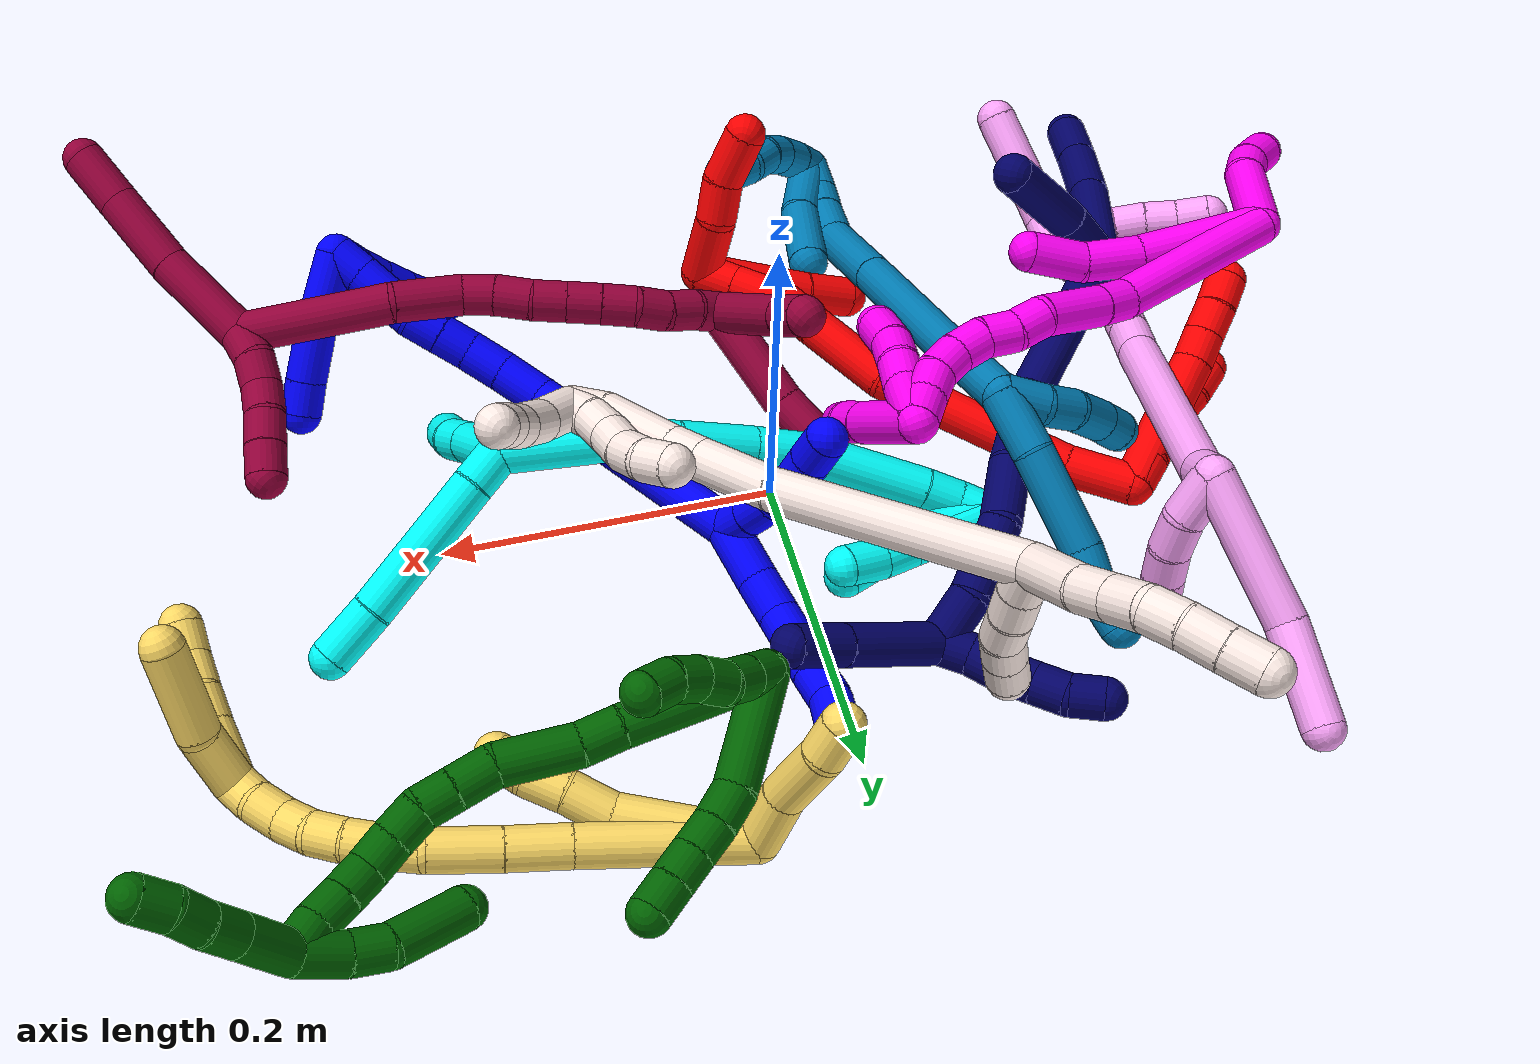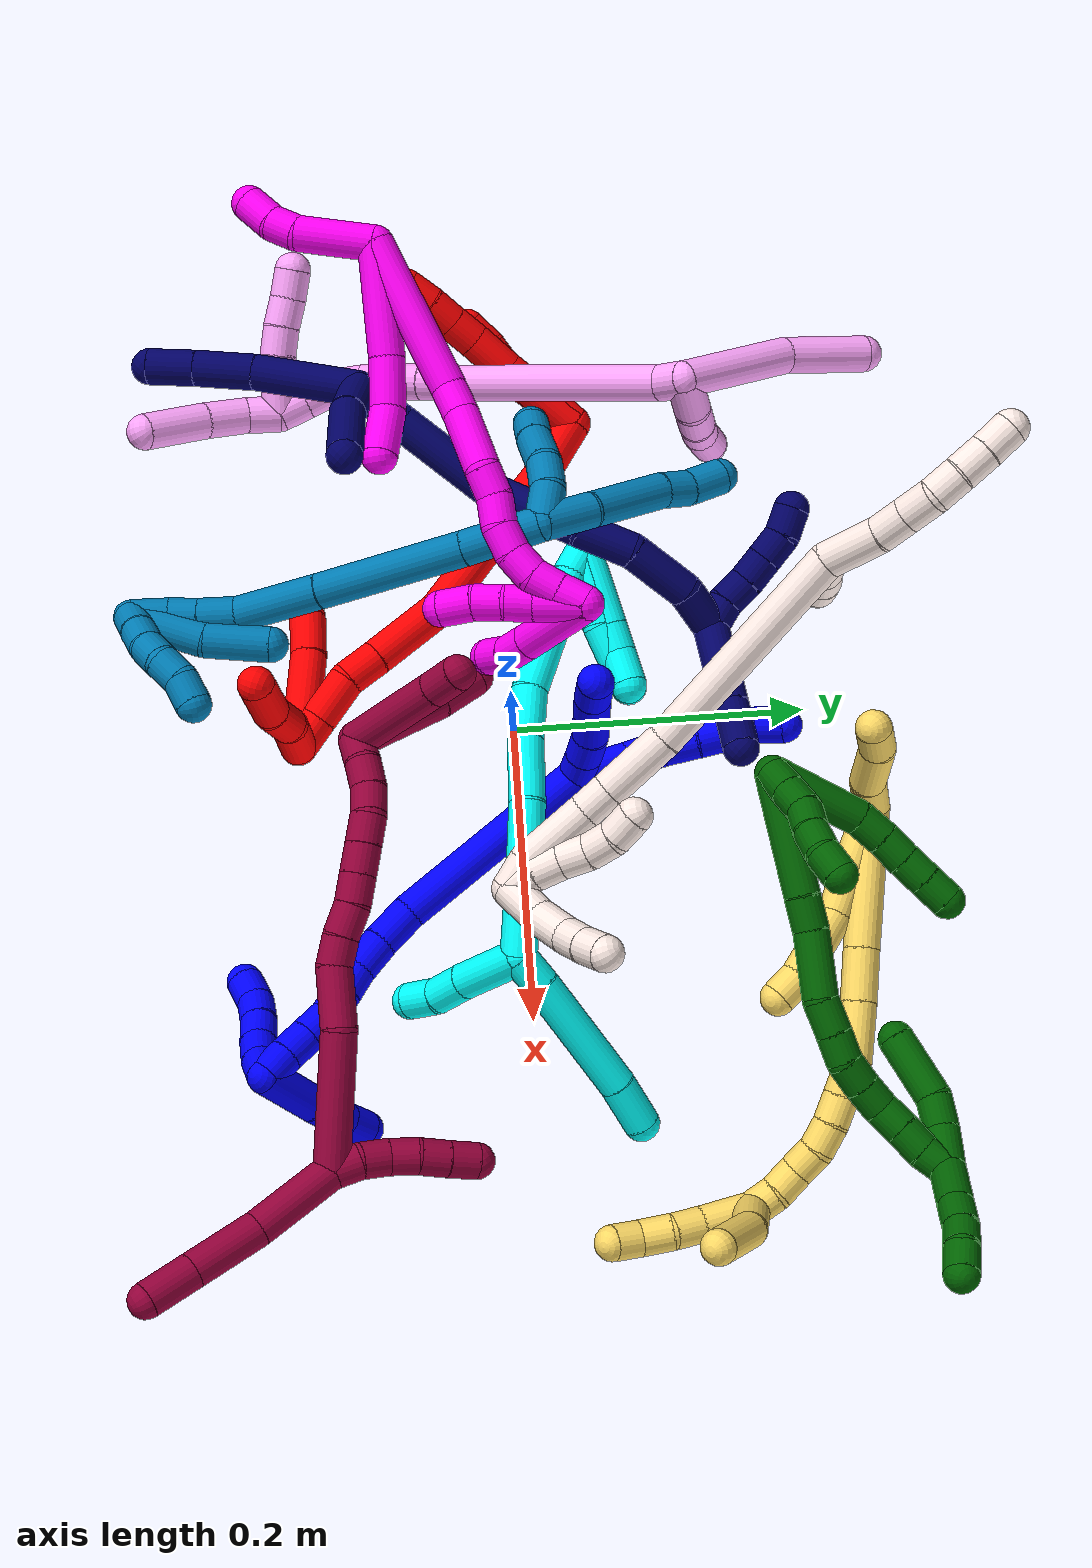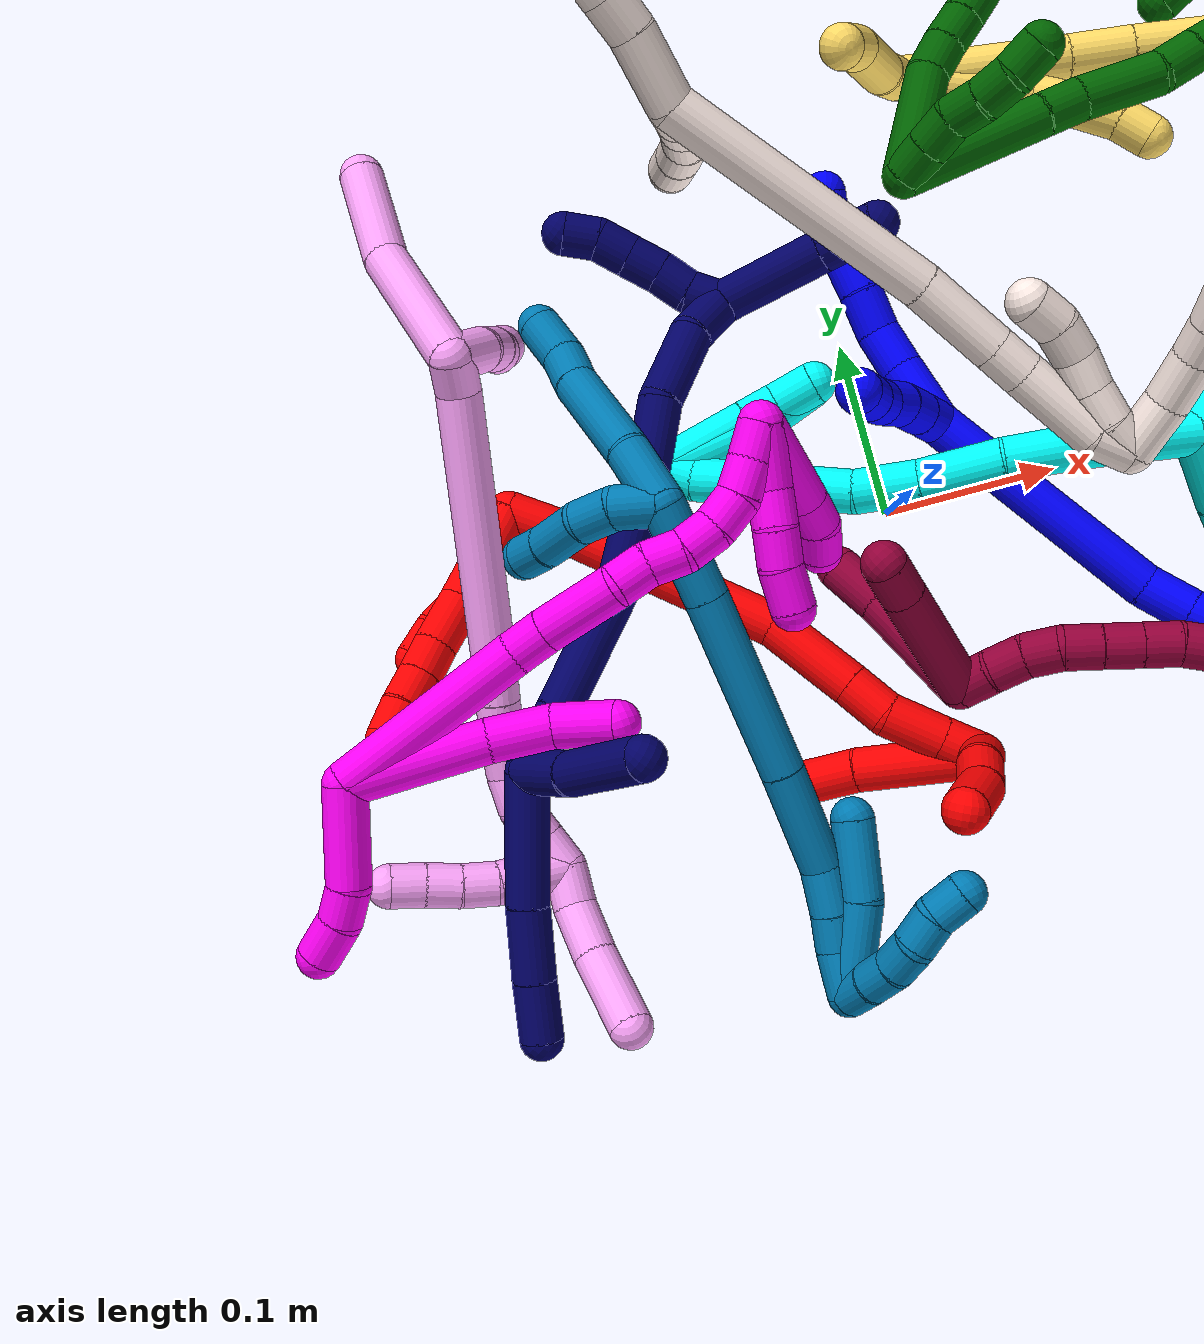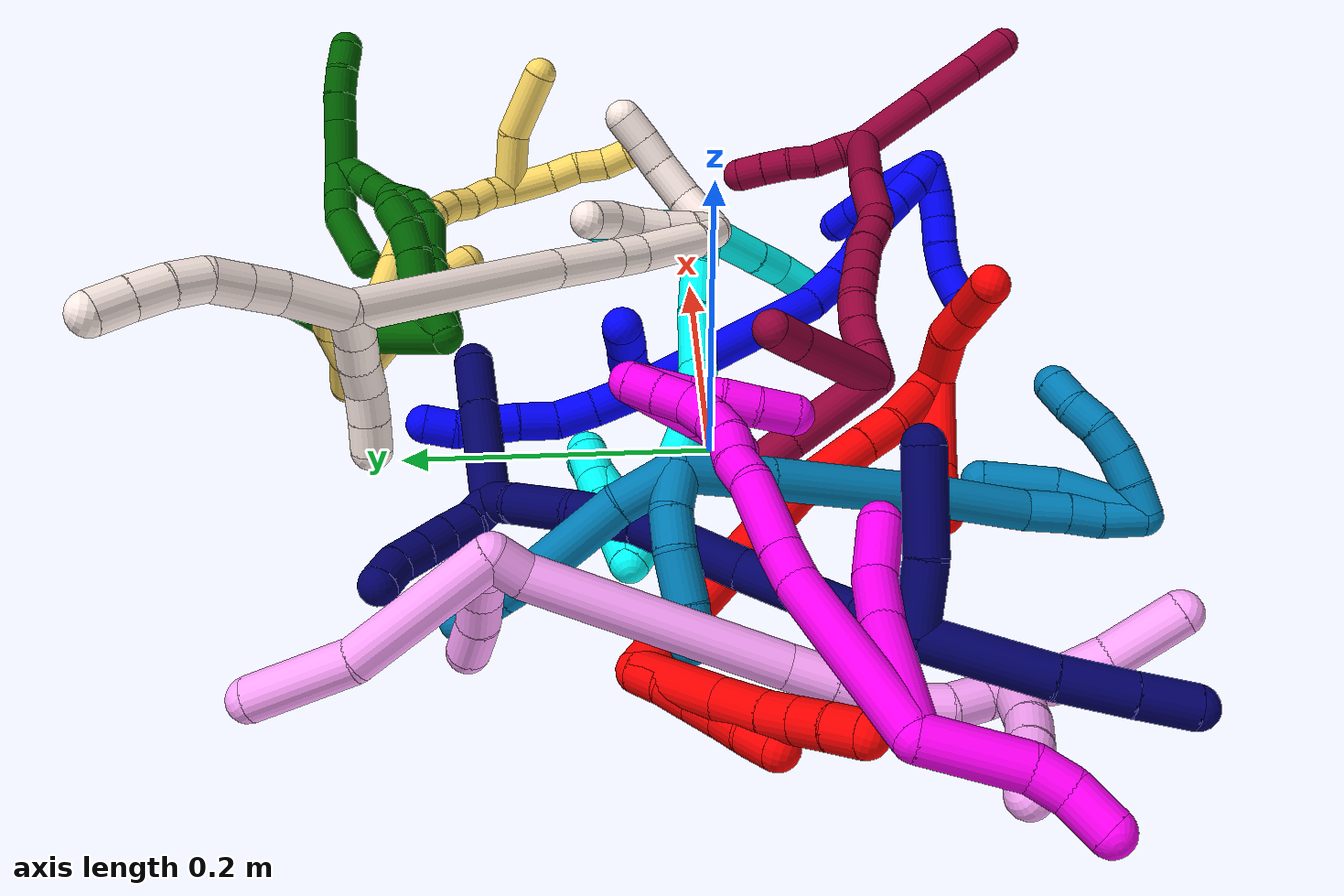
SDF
<sdf version="1.7">
 <world name="default">
  <plugin name="TubeGeneratorPlugin" filename="libtube_generator_plugin.so"/>
  <model name="photoneo_s_sensor">
   <static>1</static>
   <pose>0 0 2 1.57079 1.57079 3.14159</pose>
   <link name="link">
    <inertial><mass>0.1</mass></inertial>
    <sensor name="sensor" type="depth">
     <update_rate>30</update_rate>
     <camera>
      <horizontal_fov>1.22</horizontal_fov>
      <image><width>1920</width><height>1200</height><format>B8G8R8</format></image>
      <clip><near>0.1</near><far>4</far></clip>
      <depth_camera><output>points</output></depth_camera>
     </camera>
     <plugin name="camera_plugin" filename="libgazebo_ros_depth_camera.so">
      <baseline>0.2</baseline>
      <alwaysOn>1</alwaysOn>
      <updateRate>0.0</updateRate>
      <cameraName>camera_ir</cameraName>
      <imageTopicName>/camera/color/image_raw</imageTopicName>
      <cameraInfoTopicName>/camera/color/camera_info</cameraInfoTopicName>
      <depthImageTopicName>/camera/depth/image_raw</depthImageTopicName>
      <depthImageCameraInfoTopicName>/camera/depth/camera_info</depthImageCameraInfoTopicName>
      <pointCloudTopicName>/camera/depth/points</pointCloudTopicName>
      <frameName>fr_optical</frameName>
      <pointCloudCutoff>0.1</pointCloudCutoff>
      <pointCloudCutoffMax>2.0</pointCloudCutoffMax>
      <distortionK1>0</distortionK1>
      <distortionK2>0</distortionK2>
      <distortionK3>0</distortionK3>
      <distortionT1>0</distortionT1>
      <distortionT2>0</distortionT2>
      <CxPrime>0</CxPrime>
      <Cx>0</Cx>
      <Cy>0</Cy>
      <focalLength>0</focalLength>
      <hackBaseline>0</hackBaseline>
     </plugin>
    </sensor>
   </link>
  </model>
  <gravity>0 0 -9.8</gravity>
  <magnetic_field>6e-06 2.3e-05 -4.2e-05</magnetic_field>
  <atmosphere type="adiabatic"/>
  <physics name="default_physics" default="0" type="ode">
   <max_step_size>0.003</max_step_size>
   <real_time_factor>1</real_time_factor>
   <real_time_update_rate>1000</real_time_update_rate>
   <max_contacts>10000</max_contacts>
   <ode>
    <solver>
     <type>quick</type>
     <iters>100</iters>
     <sor>1.3</sor>
     <use_dynamic_moi_rescaling>0</use_dynamic_moi_rescaling>
    </solver>
    <constraints>
     <contact_max_correcting_vel>0</contact_max_correcting_vel>
     <contact_surface_layer>0.001</contact_surface_layer>
     <cfm>0</cfm>
     <erp>0.2</erp>
    </constraints>
   </ode>
  </physics>
  <scene><ambient>0.4 0.4 0.4 1</ambient><background>0.7 0.7 0.7 1</background><shadows>0</shadows></scene>
  <audio><device>default</device></audio>
  <spherical_coordinates>
   <surface_model>EARTH_WGS84</surface_model>
   <latitude_deg>0</latitude_deg>
   <longitude_deg>0</longitude_deg>
   <elevation>0</elevation>
   <heading_deg>0</heading_deg>
  </spherical_coordinates>
  <model name="bin">
   <static>1</static>
   <link name="bottom">
    <collision name="collision-bottom">
     <pose>0 0 -0.01 0 -0 0</pose>
     <geometry><box><size>0.8 0.6 0.02</size></box></geometry>
     <surface>
      <friction><ode><mu>100</mu><mu2>100</mu2></ode></friction>
      <contact><collide_bitmask>65535</collide_bitmask></contact>
     </surface>
    </collision>
   </link>
   <link name="west_wall">
    <collision name="collision-west_wall">
     <pose>-0.41 0 0.1 0 -0 0</pose>
     <geometry><box><size>0.02 0.6 0.2</size></box></geometry>
     <surface>
      <friction><ode><mu>100</mu><mu2>100</mu2></ode></friction>
      <contact><collide_bitmask>65535</collide_bitmask></contact>
     </surface>
    </collision>
   </link>
   <link name="east_wall">
    <collision name="collision-east_wall">
     <pose>0.41 0 0.1 0 -0 0</pose>
     <geometry><box><size>0.02 0.6 0.2</size></box></geometry>
     <surface>
      <friction><ode><mu>100</mu><mu2>100</mu2></ode></friction>
      <contact><collide_bitmask>65535</collide_bitmask></contact>
     </surface>
    </collision>
   </link>
   <link name="south_wall">
    <collision name="collision-south_wall">
     <pose>0 -0.31 0.1 0 -0 0</pose>
     <geometry><box><size>0.8 0.02 0.2</size></box></geometry>
     <surface>
      <friction><ode><mu>100</mu><mu2>100</mu2></ode></friction>
      <contact><collide_bitmask>65535</collide_bitmask></contact>
     </surface>
    </collision>
   </link>
   <link name="north_wall">
    <collision name="collision-north_wall">
     <pose>0 0.31 0.1 0 -0 0</pose>
     <geometry><box><size>0.8 0.02 0.2</size></box></geometry>
     <surface>
      <friction><ode><mu>100</mu><mu2>100</mu2></ode></friction>
      <contact><collide_bitmask>65535</collide_bitmask></contact>
     </surface>
    </collision>
   </link>
  </model>
  <model name="1">
   <static>0</static>
   <link name="1">
    <collision name="collision-cylinder-e_1_2_8">
     <pose>-0.012828 -0.002999 -0.013653 2.92537 -0.742491 -2.5978</pose>
     <geometry><cylinder><radius>0.0125</radius><length>0.037945</length></cylinder></geometry>
     <surface>
      <friction><ode><mu>1.16</mu><mu2>1.16</mu2><slip1>0</slip1><slip2>0</slip2></ode></friction>
      <contact><ode><kp>1e+06</kp><kd>1</kd><max_vel>0</max_vel><min_depth>0.001</min_depth></ode></contact>
     </surface>
    </collision>
    <visual name="visual-cylinder-e_1_2_8">
     <pose>-0.012828 -0.002999 -0.013653 2.92537 -0.742491 -2.5978</pose>
     <geometry><cylinder><radius>0.0125</radius><length>0.037945</length></cylinder></geometry>
     <material><ambient>0 0 1 1</ambient></material>
    </visual>
    <collision name="collision-cylinder-e_2_8_9">
     <pose>-0.035204 -0.007607 -0.036035 2.95936 -0.821895 -2.72823</pose>
     <geometry><cylinder><radius>0.0125</radius><length>0.026073</length></cylinder></geometry>
     <surface>
      <friction><ode><mu>1.16</mu><mu2>1.16</mu2><slip1>0</slip1><slip2>0</slip2></ode></friction>
      <contact><ode><kp>1e+06</kp><kd>1</kd><max_vel>0</max_vel><min_depth>0.001</min_depth></ode></contact>
     </surface>
    </collision>
    <visual name="visual-cylinder-e_2_8_9">
     <pose>-0.035204 -0.007607 -0.036035 2.95936 -0.821895 -2.72823</pose>
     <geometry><cylinder><radius>0.0125</radius><length>0.026073</length></cylinder></geometry>
     <material><ambient>0 0 1 1</ambient></material>
    </visual>
    <collision name="collision-cylinder-e_3_9_10">
     <pose>-0.055721 -0.008224 -0.051064 -2.98558 -1.04409 2.8715</pose>
     <geometry><cylinder><radius>0.0125</radius><length>0.025376</length></cylinder></geometry>
     <surface>
      <friction><ode><mu>1.16</mu><mu2>1.16</mu2><slip1>0</slip1><slip2>0</slip2></ode></friction>
      <contact><ode><kp>1e+06</kp><kd>1</kd><max_vel>0</max_vel><min_depth>0.001</min_depth></ode></contact>
     </surface>
    </collision>
    <visual name="visual-cylinder-e_3_9_10">
     <pose>-0.055721 -0.008224 -0.051064 -2.98558 -1.04409 2.8715</pose>
     <geometry><cylinder><radius>0.0125</radius><length>0.025376</length></cylinder></geometry>
     <material><ambient>0 0 1 1</ambient></material>
    </visual>
    <collision name="collision-cylinder-e_4_10_11">
     <pose>-0.074918 -0.00704 -0.063184 -3.10836 -0.955026 3.07738</pose>
     <geometry><cylinder><radius>0.0125</radius><length>0.02016</length></cylinder></geometry>
     <surface>
      <friction><ode><mu>1.16</mu><mu2>1.16</mu2><slip1>0</slip1><slip2>0</slip2></ode></friction>
      <contact><ode><kp>1e+06</kp><kd>1</kd><max_vel>0</max_vel><min_depth>0.001</min_depth></ode></contact>
     </surface>
    </collision>
    <visual name="visual-cylinder-e_4_10_11">
     <pose>-0.074918 -0.00704 -0.063184 -3.10836 -0.955026 3.07738</pose>
     <geometry><cylinder><radius>0.0125</radius><length>0.02016</length></cylinder></geometry>
     <material><ambient>0 0 1 1</ambient></material>
    </visual>
    <collision name="collision-cylinder-e_5_11_12">
     <pose>-0.091742 -0.006859 -0.074432 3.1393 -1.00749 -3.13742</pose>
     <geometry><cylinder><radius>0.0125</radius><length>0.020334</length></cylinder></geometry>
     <surface>
      <friction><ode><mu>1.16</mu><mu2>1.16</mu2><slip1>0</slip1><slip2>0</slip2></ode></friction>
      <contact><ode><kp>1e+06</kp><kd>1</kd><max_vel>0</max_vel><min_depth>0.001</min_depth></ode></contact>
     </surface>
    </collision>
    <visual name="visual-cylinder-e_5_11_12">
     <pose>-0.091742 -0.006859 -0.074432 3.1393 -1.00749 -3.13742</pose>
     <geometry><cylinder><radius>0.0125</radius><length>0.020334</length></cylinder></geometry>
     <material><ambient>0 0 1 1</ambient></material>
    </visual>
    <collision name="collision-cylinder-e_6_12_6">
     <pose>-0.108489 -0.003588 -0.084751 -2.55035 -0.945098 2.06698</pose>
     <geometry><cylinder><radius>0.0125</radius><length>0.020112</length></cylinder></geometry>
     <surface>
      <friction><ode><mu>1.16</mu><mu2>1.16</mu2><slip1>0</slip1><slip2>0</slip2></ode></friction>
      <contact><ode><kp>1e+06</kp><kd>1</kd><max_vel>0</max_vel><min_depth>0.001</min_depth></ode></contact>
     </surface>
    </collision>
    <visual name="visual-cylinder-e_6_12_6">
     <pose>-0.108489 -0.003588 -0.084751 -2.55035 -0.945098 2.06698</pose>
     <geometry><cylinder><radius>0.0125</radius><length>0.020112</length></cylinder></geometry>
     <material><ambient>0 0 1 1</ambient></material>
    </visual>
    <collision name="collision-cylinder-e_1_2_13">
     <pose>-0.008514 -0.001718 0.004957 0.333691 -1.01856 -0.187534</pose>
     <geometry><cylinder><radius>0.0125</radius><length>0.02</length></cylinder></geometry>
     <surface>
      <friction><ode><mu>1.16</mu><mu2>1.16</mu2><slip1>0</slip1><slip2>0</slip2></ode></friction>
      <contact><ode><kp>1e+06</kp><kd>1</kd><max_vel>0</max_vel><min_depth>0.001</min_depth></ode></contact>
     </surface>
    </collision>
    <visual name="visual-cylinder-e_1_2_13">
     <pose>-0.008514 -0.001718 0.004957 0.333691 -1.01856 -0.187534</pose>
     <geometry><cylinder><radius>0.0125</radius><length>0.02</length></cylinder></geometry>
     <material><ambient>0 0 1 1</ambient></material>
    </visual>
    <collision name="collision-cylinder-e_2_13_14">
     <pose>-0.025313 -0.005116 0.015253 0.304773 -0.976627 -0.162807</pose>
     <geometry><cylinder><radius>0.0125</radius><length>0.02</length></cylinder></geometry>
     <surface>
      <friction><ode><mu>1.16</mu><mu2>1.16</mu2><slip1>0</slip1><slip2>0</slip2></ode></friction>
      <contact><ode><kp>1e+06</kp><kd>1</kd><max_vel>0</max_vel><min_depth>0.001</min_depth></ode></contact>
     </surface>
    </collision>
    <visual name="visual-cylinder-e_2_13_14">
     <pose>-0.025313 -0.005116 0.015253 0.304773 -0.976627 -0.162807</pose>
     <geometry><cylinder><radius>0.0125</radius><length>0.02</length></cylinder></geometry>
     <material><ambient>0 0 1 1</ambient></material>
    </visual>
    <collision name="collision-cylinder-e_3_14_15">
     <pose>-0.040699 -0.009541 0.027079 0.400343 -0.789427 -0.168636</pose>
     <geometry><cylinder><radius>0.0125</radius><length>0.02</length></cylinder></geometry>
     <surface>
      <friction><ode><mu>1.16</mu><mu2>1.16</mu2><slip1>0</slip1><slip2>0</slip2></ode></friction>
      <contact><ode><kp>1e+06</kp><kd>1</kd><max_vel>0</max_vel><min_depth>0.001</min_depth></ode></contact>
     </surface>
    </collision>
    <visual name="visual-cylinder-e_3_14_15">
     <pose>-0.040699 -0.009541 0.027079 0.400343 -0.789427 -0.168636</pose>
     <geometry><cylinder><radius>0.0125</radius><length>0.02</length></cylinder></geometry>
     <material><ambient>0 0 1 1</ambient></material>
    </visual>
    <collision name="collision-cylinder-e_4_15_16">
     <pose>-0.05462 -0.012449 0.040875 0.022304 -0.750685 -0.008788</pose>
     <geometry><cylinder><radius>0.0125</radius><length>0.02</length></cylinder></geometry>
     <surface>
      <friction><ode><mu>1.16</mu><mu2>1.16</mu2><slip1>0</slip1><slip2>0</slip2></ode></friction>
      <contact><ode><kp>1e+06</kp><kd>1</kd><max_vel>0</max_vel><min_depth>0.001</min_depth></ode></contact>
     </surface>
    </collision>
    <visual name="visual-cylinder-e_4_15_16">
     <pose>-0.05462 -0.012449 0.040875 0.022304 -0.750685 -0.008788</pose>
     <geometry><cylinder><radius>0.0125</radius><length>0.02</length></cylinder></geometry>
     <material><ambient>0 0 1 1</ambient></material>
    </visual>
    <collision name="collision-cylinder-e_5_16_5">
     <pose>-0.068672 -0.012322 0.055087 -0.041925 -0.80822 0.017931</pose>
     <geometry><cylinder><radius>0.0125</radius><length>0.02</length></cylinder></geometry>
     <surface>
      <friction><ode><mu>1.16</mu><mu2>1.16</mu2><slip1>0</slip1><slip2>0</slip2></ode></friction>
      <contact><ode><kp>1e+06</kp><kd>1</kd><max_vel>0</max_vel><min_depth>0.001</min_depth></ode></contact>
     </surface>
    </collision>
    <visual name="visual-cylinder-e_5_16_5">
     <pose>-0.068672 -0.012322 0.055087 -0.041925 -0.80822 0.017931</pose>
     <geometry><cylinder><radius>0.0125</radius><length>0.02</length></cylinder></geometry>
     <material><ambient>0 0 1 1</ambient></material>
    </visual>
    <collision name="collision-cylinder-e_1_2_17">
     <pose>0.05919 0.029437 0.031293 -0.754841 0.942941 -0.398836</pose>
     <geometry><cylinder><radius>0.0125</radius><length>0.146277</length></cylinder></geometry>
     <surface>
      <friction><ode><mu>1.16</mu><mu2>1.16</mu2><slip1>0</slip1><slip2>0</slip2></ode></friction>
      <contact><ode><kp>1e+06</kp><kd>1</kd><max_vel>0</max_vel><min_depth>0.001</min_depth></ode></contact>
     </surface>
    </collision>
    <visual name="visual-cylinder-e_1_2_17">
     <pose>0.05919 0.029437 0.031293 -0.754841 0.942941 -0.398836</pose>
     <geometry><cylinder><radius>0.0125</radius><length>0.146277</length></cylinder></geometry>
     <material><ambient>0 0 1 1</ambient></material>
    </visual>
    <collision name="collision-cylinder-e_2_17_18">
     <pose>0.128143 0.067048 0.069359 -0.87886 0.743529 -0.362543</pose>
     <geometry><cylinder><radius>0.0125</radius><length>0.028844</length></cylinder></geometry>
     <surface>
      <friction><ode><mu>1.16</mu><mu2>1.16</mu2><slip1>0</slip1><slip2>0</slip2></ode></friction>
      <contact><ode><kp>1e+06</kp><kd>1</kd><max_vel>0</max_vel><min_depth>0.001</min_depth></ode></contact>
     </surface>
    </collision>
    <visual name="visual-cylinder-e_2_17_18">
     <pose>0.128143 0.067048 0.069359 -0.87886 0.743529 -0.362543</pose>
     <geometry><cylinder><radius>0.0125</radius><length>0.028844</length></cylinder></geometry>
     <material><ambient>0 0 1 1</ambient></material>
    </visual>
    <collision name="collision-cylinder-e_3_18_19">
     <pose>0.145469 0.083074 0.08182 -0.943957 0.662541 -0.347596</pose>
     <geometry><cylinder><radius>0.0125</radius><length>0.024594</length></cylinder></geometry>
     <surface>
      <friction><ode><mu>1.16</mu><mu2>1.16</mu2><slip1>0</slip1><slip2>0</slip2></ode></friction>
      <contact><ode><kp>1e+06</kp><kd>1</kd><max_vel>0</max_vel><min_depth>0.001</min_depth></ode></contact>
     </surface>
    </collision>
    <visual name="visual-cylinder-e_3_18_19">
     <pose>0.145469 0.083074 0.08182 -0.943957 0.662541 -0.347596</pose>
     <geometry><cylinder><radius>0.0125</radius><length>0.024594</length></cylinder></geometry>
     <material><ambient>0 0 1 1</ambient></material>
    </visual>
    <collision name="collision-cylinder-e_4_19_20">
     <pose>0.157692 0.098555 0.092175 -1.02168 0.480206 -0.272729</pose>
     <geometry><cylinder><radius>0.0125</radius><length>0.020168</length></cylinder></geometry>
     <surface>
      <friction><ode><mu>1.16</mu><mu2>1.16</mu2><slip1>0</slip1><slip2>0</slip2></ode></friction>
      <contact><ode><kp>1e+06</kp><kd>1</kd><max_vel>0</max_vel><min_depth>0.001</min_depth></ode></contact>
     </surface>
    </collision>
    <visual name="visual-cylinder-e_4_19_20">
     <pose>0.157692 0.098555 0.092175 -1.02168 0.480206 -0.272729</pose>
     <geometry><cylinder><radius>0.0125</radius><length>0.020168</length></cylinder></geometry>
     <material><ambient>0 0 1 1</ambient></material>
    </visual>
    <collision name="collision-cylinder-e_5_20_21">
     <pose>0.167356 0.113574 0.101462 -1.01212 0.521364 -0.293542</pose>
     <geometry><cylinder><radius>0.0125</radius><length>0.020102</length></cylinder></geometry>
     <surface>
      <friction><ode><mu>1.16</mu><mu2>1.16</mu2><slip1>0</slip1><slip2>0</slip2></ode></friction>
      <contact><ode><kp>1e+06</kp><kd>1</kd><max_vel>0</max_vel><min_depth>0.001</min_depth></ode></contact>
     </surface>
    </collision>
    <visual name="visual-cylinder-e_5_20_21">
     <pose>0.167356 0.113574 0.101462 -1.01212 0.521364 -0.293542</pose>
     <geometry><cylinder><radius>0.0125</radius><length>0.020102</length></cylinder></geometry>
     <material><ambient>0 0 1 1</ambient></material>
    </visual>
    <collision name="collision-cylinder-e_6_21_22">
     <pose>0.178132 0.126598 0.112008 -0.760062 0.614537 -0.25216</pose>
     <geometry><cylinder><radius>0.0125</radius><length>0.020014</length></cylinder></geometry>
     <surface>
      <friction><ode><mu>1.16</mu><mu2>1.16</mu2><slip1>0</slip1><slip2>0</slip2></ode></friction>
      <contact><ode><kp>1e+06</kp><kd>1</kd><max_vel>0</max_vel><min_depth>0.001</min_depth></ode></contact>
     </surface>
    </collision>
    <visual name="visual-cylinder-e_6_21_22">
     <pose>0.178132 0.126598 0.112008 -0.760062 0.614537 -0.25216</pose>
     <geometry><cylinder><radius>0.0125</radius><length>0.020014</length></cylinder></geometry>
     <material><ambient>0 0 1 1</ambient></material>
    </visual>
    <collision name="collision-cylinder-e_7_22_23">
     <pose>0.189621 0.137874 0.123888 -0.758562 0.608838 -0.249158</pose>
     <geometry><cylinder><radius>0.0125</radius><length>0.02</length></cylinder></geometry>
     <surface>
      <friction><ode><mu>1.16</mu><mu2>1.16</mu2><slip1>0</slip1><slip2>0</slip2></ode></friction>
      <contact><ode><kp>1e+06</kp><kd>1</kd><max_vel>0</max_vel><min_depth>0.001</min_depth></ode></contact>
     </surface>
    </collision>
    <visual name="visual-cylinder-e_7_22_23">
     <pose>0.189621 0.137874 0.123888 -0.758562 0.608838 -0.249158</pose>
     <geometry><cylinder><radius>0.0125</radius><length>0.02</length></cylinder></geometry>
     <material><ambient>0 0 1 1</ambient></material>
    </visual>
    <collision name="collision-cylinder-e_8_23_1">
     <pose>0.200767 0.149628 0.135605 -0.814827 0.57358 -0.25319</pose>
     <geometry><cylinder><radius>0.0125</radius><length>0.02</length></cylinder></geometry>
     <surface>
      <friction><ode><mu>1.16</mu><mu2>1.16</mu2><slip1>0</slip1><slip2>0</slip2></ode></friction>
      <contact><ode><kp>1e+06</kp><kd>1</kd><max_vel>0</max_vel><min_depth>0.001</min_depth></ode></contact>
     </surface>
    </collision>
    <visual name="visual-cylinder-e_8_23_1">
     <pose>0.200767 0.149628 0.135605 -0.814827 0.57358 -0.25319</pose>
     <geometry><cylinder><radius>0.0125</radius><length>0.02</length></cylinder></geometry>
     <material><ambient>0 0 1 1</ambient></material>
    </visual>
    <collision name="collision-cylinder-e_1_1_24">
     <pose>0.207308 0.161201 0.119229 -2.89973 0.048851 -0.396772</pose>
     <geometry><cylinder><radius>0.0125</radius><length>0.045657</length></cylinder></geometry>
     <surface>
      <friction><ode><mu>1.16</mu><mu2>1.16</mu2><slip1>0</slip1><slip2>0</slip2></ode></friction>
      <contact><ode><kp>1e+06</kp><kd>1</kd><max_vel>0</max_vel><min_depth>0.001</min_depth></ode></contact>
     </surface>
    </collision>
    <visual name="visual-cylinder-e_1_1_24">
     <pose>0.207308 0.161201 0.119229 -2.89973 0.048851 -0.396772</pose>
     <geometry><cylinder><radius>0.0125</radius><length>0.045657</length></cylinder></geometry>
     <material><ambient>0 0 1 1</ambient></material>
    </visual>
    <collision name="collision-cylinder-e_2_24_25">
     <pose>0.210108 0.168878 0.080492 -3.00889 0.100311 -1.29395</pose>
     <geometry><cylinder><radius>0.0125</radius><length>0.033662</length></cylinder></geometry>
     <surface>
      <friction><ode><mu>1.16</mu><mu2>1.16</mu2><slip1>0</slip1><slip2>0</slip2></ode></friction>
      <contact><ode><kp>1e+06</kp><kd>1</kd><max_vel>0</max_vel><min_depth>0.001</min_depth></ode></contact>
     </surface>
    </collision>
    <visual name="visual-cylinder-e_2_24_25">
     <pose>0.210108 0.168878 0.080492 -3.00889 0.100311 -1.29395</pose>
     <geometry><cylinder><radius>0.0125</radius><length>0.033662</length></cylinder></geometry>
     <material><ambient>0 0 1 1</ambient></material>
    </visual>
    <collision name="collision-cylinder-e_3_25_4">
     <pose>0.212347 0.172211 0.053628 -3.03322 0.053542 -0.917184</pose>
     <geometry><cylinder><radius>0.0125</radius><length>0.02068</length></cylinder></geometry>
     <surface>
      <friction><ode><mu>1.16</mu><mu2>1.16</mu2><slip1>0</slip1><slip2>0</slip2></ode></friction>
      <contact><ode><kp>1e+06</kp><kd>1</kd><max_vel>0</max_vel><min_depth>0.001</min_depth></ode></contact>
     </surface>
    </collision>
    <visual name="visual-cylinder-e_3_25_4">
     <pose>0.212347 0.172211 0.053628 -3.03322 0.053542 -0.917184</pose>
     <geometry><cylinder><radius>0.0125</radius><length>0.02068</length></cylinder></geometry>
     <material><ambient>0 0 1 1</ambient></material>
    </visual>
    <collision name="collision-cylinder-e_1_1_26">
     <pose>0.210346 0.147499 0.137513 2.00823 0.428194 0.658545</pose>
     <geometry><cylinder><radius>0.0125</radius><length>0.02</length></cylinder></geometry>
     <surface>
      <friction><ode><mu>1.16</mu><mu2>1.16</mu2><slip1>0</slip1><slip2>0</slip2></ode></friction>
      <contact><ode><kp>1e+06</kp><kd>1</kd><max_vel>0</max_vel><min_depth>0.001</min_depth></ode></contact>
     </surface>
    </collision>
    <visual name="visual-cylinder-e_1_1_26">
     <pose>0.210346 0.147499 0.137513 2.00823 0.428194 0.658545</pose>
     <geometry><cylinder><radius>0.0125</radius><length>0.02</length></cylinder></geometry>
     <material><ambient>0 0 1 1</ambient></material>
    </visual>
    <collision name="collision-cylinder-e_2_26_27">
     <pose>0.216717 0.130301 0.129808 1.97687 0.22374 0.337917</pose>
     <geometry><cylinder><radius>0.0125</radius><length>0.02</length></cylinder></geometry>
     <surface>
      <friction><ode><mu>1.16</mu><mu2>1.16</mu2><slip1>0</slip1><slip2>0</slip2></ode></friction>
      <contact><ode><kp>1e+06</kp><kd>1</kd><max_vel>0</max_vel><min_depth>0.001</min_depth></ode></contact>
     </surface>
    </collision>
    <visual name="visual-cylinder-e_2_26_27">
     <pose>0.216717 0.130301 0.129808 1.97687 0.22374 0.337917</pose>
     <geometry><cylinder><radius>0.0125</radius><length>0.02</length></cylinder></geometry>
     <material><ambient>0 0 1 1</ambient></material>
    </visual>
    <collision name="collision-cylinder-e_3_27_28">
     <pose>0.219806 0.112097 0.122249 1.95212 0.087139 0.128724</pose>
     <geometry><cylinder><radius>0.0125</radius><length>0.02</length></cylinder></geometry>
     <surface>
      <friction><ode><mu>1.16</mu><mu2>1.16</mu2><slip1>0</slip1><slip2>0</slip2></ode></friction>
      <contact><ode><kp>1e+06</kp><kd>1</kd><max_vel>0</max_vel><min_depth>0.001</min_depth></ode></contact>
     </surface>
    </collision>
    <visual name="visual-cylinder-e_3_27_28">
     <pose>0.219806 0.112097 0.122249 1.95212 0.087139 0.128724</pose>
     <geometry><cylinder><radius>0.0125</radius><length>0.02</length></cylinder></geometry>
     <material><ambient>0 0 1 1</ambient></material>
    </visual>
    <collision name="collision-cylinder-e_4_28_29">
     <pose>0.222798 0.093589 0.115424 1.89552 0.21386 0.296594</pose>
     <geometry><cylinder><radius>0.0125</radius><length>0.02</length></cylinder></geometry>
     <surface>
      <friction><ode><mu>1.16</mu><mu2>1.16</mu2><slip1>0</slip1><slip2>0</slip2></ode></friction>
      <contact><ode><kp>1e+06</kp><kd>1</kd><max_vel>0</max_vel><min_depth>0.001</min_depth></ode></contact>
     </surface>
    </collision>
    <visual name="visual-cylinder-e_4_28_29">
     <pose>0.222798 0.093589 0.115424 1.89552 0.21386 0.296594</pose>
     <geometry><cylinder><radius>0.0125</radius><length>0.02</length></cylinder></geometry>
     <material><ambient>0 0 1 1</ambient></material>
    </visual>
    <collision name="collision-cylinder-e_5_29_3">
     <pose>0.22801 0.074835 0.111708 1.63373 0.31407 0.334116</pose>
     <geometry><cylinder><radius>0.0125</radius><length>0.02</length></cylinder></geometry>
     <surface>
      <friction><ode><mu>1.16</mu><mu2>1.16</mu2><slip1>0</slip1><slip2>0</slip2></ode></friction>
      <contact><ode><kp>1e+06</kp><kd>1</kd><max_vel>0</max_vel><min_depth>0.001</min_depth></ode></contact>
     </surface>
    </collision>
    <visual name="visual-cylinder-e_5_29_3">
     <pose>0.22801 0.074835 0.111708 1.63373 0.31407 0.334116</pose>
     <geometry><cylinder><radius>0.0125</radius><length>0.02</length></cylinder></geometry>
     <material><ambient>0 0 1 1</ambient></material>
    </visual>
    <collision name="collision-sphere-3">
     <pose>0.231099 0.065343 0.11111 0 -0 0</pose>
     <geometry><sphere><radius>0.0125</radius></sphere></geometry>
     <surface>
      <friction><ode><mu>1.16</mu><mu2>1.16</mu2><slip1>0</slip1><slip2>0</slip2></ode></friction>
      <contact><ode><kp>1e+06</kp><kd>1</kd><max_vel>0</max_vel><min_depth>0.001</min_depth></ode></contact>
     </surface>
    </collision>
    <visual name="visual-sphere-3">
     <pose>0.231099 0.065343 0.11111 0 -0 0</pose>
     <geometry><sphere><radius>0.0125</radius></sphere></geometry>
     <material><ambient>0 0 1 1</ambient></material>
    </visual>
    <collision name="collision-sphere-29">
     <pose>0.224921 0.084327 0.112306 0 -0 0</pose>
     <geometry><sphere><radius>0.0125</radius></sphere></geometry>
     <surface>
      <friction><ode><mu>1.16</mu><mu2>1.16</mu2><slip1>0</slip1><slip2>0</slip2></ode></friction>
      <contact><ode><kp>1e+06</kp><kd>1</kd><max_vel>0</max_vel><min_depth>0.001</min_depth></ode></contact>
     </surface>
    </collision>
    <visual name="visual-sphere-29">
     <pose>0.224921 0.084327 0.112306 0 -0 0</pose>
     <geometry><sphere><radius>0.0125</radius></sphere></geometry>
     <material><ambient>0 0 1 1</ambient></material>
    </visual>
    <collision name="collision-sphere-28">
     <pose>0.220676 0.10285 0.118541 0 -0 0</pose>
     <geometry><sphere><radius>0.0125</radius></sphere></geometry>
     <surface>
      <friction><ode><mu>1.16</mu><mu2>1.16</mu2><slip1>0</slip1><slip2>0</slip2></ode></friction>
      <contact><ode><kp>1e+06</kp><kd>1</kd><max_vel>0</max_vel><min_depth>0.001</min_depth></ode></contact>
     </surface>
    </collision>
    <visual name="visual-sphere-28">
     <pose>0.220676 0.10285 0.118541 0 -0 0</pose>
     <geometry><sphere><radius>0.0125</radius></sphere></geometry>
     <material><ambient>0 0 1 1</ambient></material>
    </visual>
    <collision name="collision-sphere-27">
     <pose>0.218935 0.121343 0.125956 0 -0 0</pose>
     <geometry><sphere><radius>0.0125</radius></sphere></geometry>
     <surface>
      <friction><ode><mu>1.16</mu><mu2>1.16</mu2><slip1>0</slip1><slip2>0</slip2></ode></friction>
      <contact><ode><kp>1e+06</kp><kd>1</kd><max_vel>0</max_vel><min_depth>0.001</min_depth></ode></contact>
     </surface>
    </collision>
    <visual name="visual-sphere-27">
     <pose>0.218935 0.121343 0.125956 0 -0 0</pose>
     <geometry><sphere><radius>0.0125</radius></sphere></geometry>
     <material><ambient>0 0 1 1</ambient></material>
    </visual>
    <collision name="collision-sphere-26">
     <pose>0.214498 0.139259 0.133659 0 -0 0</pose>
     <geometry><sphere><radius>0.0125</radius></sphere></geometry>
     <surface>
      <friction><ode><mu>1.16</mu><mu2>1.16</mu2><slip1>0</slip1><slip2>0</slip2></ode></friction>
      <contact><ode><kp>1e+06</kp><kd>1</kd><max_vel>0</max_vel><min_depth>0.001</min_depth></ode></contact>
     </surface>
    </collision>
    <visual name="visual-sphere-26">
     <pose>0.214498 0.139259 0.133659 0 -0 0</pose>
     <geometry><sphere><radius>0.0125</radius></sphere></geometry>
     <material><ambient>0 0 1 1</ambient></material>
    </visual>
    <collision name="collision-sphere-4">
     <pose>0.212901 0.173328 0.043363 0 -0 0</pose>
     <geometry><sphere><radius>0.0125</radius></sphere></geometry>
     <surface>
      <friction><ode><mu>1.16</mu><mu2>1.16</mu2><slip1>0</slip1><slip2>0</slip2></ode></friction>
      <contact><ode><kp>1e+06</kp><kd>1</kd><max_vel>0</max_vel><min_depth>0.001</min_depth></ode></contact>
     </surface>
    </collision>
    <visual name="visual-sphere-4">
     <pose>0.212901 0.173328 0.043363 0 -0 0</pose>
     <geometry><sphere><radius>0.0125</radius></sphere></geometry>
     <material><ambient>0 0 1 1</ambient></material>
    </visual>
    <collision name="collision-sphere-25">
     <pose>0.211794 0.171094 0.063892 0 -0 0</pose>
     <geometry><sphere><radius>0.0125</radius></sphere></geometry>
     <surface>
      <friction><ode><mu>1.16</mu><mu2>1.16</mu2><slip1>0</slip1><slip2>0</slip2></ode></friction>
      <contact><ode><kp>1e+06</kp><kd>1</kd><max_vel>0</max_vel><min_depth>0.001</min_depth></ode></contact>
     </surface>
    </collision>
    <visual name="visual-sphere-25">
     <pose>0.211794 0.171094 0.063892 0 -0 0</pose>
     <geometry><sphere><radius>0.0125</radius></sphere></geometry>
     <material><ambient>0 0 1 1</ambient></material>
    </visual>
    <collision name="collision-sphere-24">
     <pose>0.208423 0.166662 0.097091 0 -0 0</pose>
     <geometry><sphere><radius>0.0125</radius></sphere></geometry>
     <surface>
      <friction><ode><mu>1.16</mu><mu2>1.16</mu2><slip1>0</slip1><slip2>0</slip2></ode></friction>
      <contact><ode><kp>1e+06</kp><kd>1</kd><max_vel>0</max_vel><min_depth>0.001</min_depth></ode></contact>
     </surface>
    </collision>
    <visual name="visual-sphere-24">
     <pose>0.208423 0.166662 0.097091 0 -0 0</pose>
     <geometry><sphere><radius>0.0125</radius></sphere></geometry>
     <material><ambient>0 0 1 1</ambient></material>
    </visual>
    <collision name="collision-sphere-1">
     <pose>0.206193 0.15574 0.141367 0 -0 0</pose>
     <geometry><sphere><radius>0.0125</radius></sphere></geometry>
     <surface>
      <friction><ode><mu>1.16</mu><mu2>1.16</mu2><slip1>0</slip1><slip2>0</slip2></ode></friction>
      <contact><ode><kp>1e+06</kp><kd>1</kd><max_vel>0</max_vel><min_depth>0.001</min_depth></ode></contact>
     </surface>
    </collision>
    <visual name="visual-sphere-1">
     <pose>0.206193 0.15574 0.141367 0 -0 0</pose>
     <geometry><sphere><radius>0.0125</radius></sphere></geometry>
     <material><ambient>0 0 1 1</ambient></material>
    </visual>
    <collision name="collision-sphere-23">
     <pose>0.19534 0.143517 0.129842 0 -0 0</pose>
     <geometry><sphere><radius>0.0125</radius></sphere></geometry>
     <surface>
      <friction><ode><mu>1.16</mu><mu2>1.16</mu2><slip1>0</slip1><slip2>0</slip2></ode></friction>
      <contact><ode><kp>1e+06</kp><kd>1</kd><max_vel>0</max_vel><min_depth>0.001</min_depth></ode></contact>
     </surface>
    </collision>
    <visual name="visual-sphere-23">
     <pose>0.19534 0.143517 0.129842 0 -0 0</pose>
     <geometry><sphere><radius>0.0125</radius></sphere></geometry>
     <material><ambient>0 0 1 1</ambient></material>
    </visual>
    <collision name="collision-sphere-22">
     <pose>0.183902 0.132231 0.117934 0 -0 0</pose>
     <geometry><sphere><radius>0.0125</radius></sphere></geometry>
     <surface>
      <friction><ode><mu>1.16</mu><mu2>1.16</mu2><slip1>0</slip1><slip2>0</slip2></ode></friction>
      <contact><ode><kp>1e+06</kp><kd>1</kd><max_vel>0</max_vel><min_depth>0.001</min_depth></ode></contact>
     </surface>
    </collision>
    <visual name="visual-sphere-22">
     <pose>0.183902 0.132231 0.117934 0 -0 0</pose>
     <geometry><sphere><radius>0.0125</radius></sphere></geometry>
     <material><ambient>0 0 1 1</ambient></material>
    </visual>
    <collision name="collision-sphere-21">
     <pose>0.172362 0.120965 0.106082 0 -0 0</pose>
     <geometry><sphere><radius>0.0125</radius></sphere></geometry>
     <surface>
      <friction><ode><mu>1.16</mu><mu2>1.16</mu2><slip1>0</slip1><slip2>0</slip2></ode></friction>
      <contact><ode><kp>1e+06</kp><kd>1</kd><max_vel>0</max_vel><min_depth>0.001</min_depth></ode></contact>
     </surface>
    </collision>
    <visual name="visual-sphere-21">
     <pose>0.172362 0.120965 0.106082 0 -0 0</pose>
     <geometry><sphere><radius>0.0125</radius></sphere></geometry>
     <material><ambient>0 0 1 1</ambient></material>
    </visual>
    <collision name="collision-sphere-12">
     <pose>-0.100338 -0.006871 -0.079861 0 -0 0</pose>
     <geometry><sphere><radius>0.0125</radius></sphere></geometry>
     <surface>
      <friction><ode><mu>1.16</mu><mu2>1.16</mu2><slip1>0</slip1><slip2>0</slip2></ode></friction>
      <contact><ode><kp>1e+06</kp><kd>1</kd><max_vel>0</max_vel><min_depth>0.001</min_depth></ode></contact>
     </surface>
    </collision>
    <visual name="visual-sphere-12">
     <pose>-0.100338 -0.006871 -0.079861 0 -0 0</pose>
     <geometry><sphere><radius>0.0125</radius></sphere></geometry>
     <material><ambient>0 0 1 1</ambient></material>
    </visual>
    <collision name="collision-sphere-11">
     <pose>-0.083146 -0.006846 -0.069003 0 -0 0</pose>
     <geometry><sphere><radius>0.0125</radius></sphere></geometry>
     <surface>
      <friction><ode><mu>1.16</mu><mu2>1.16</mu2><slip1>0</slip1><slip2>0</slip2></ode></friction>
      <contact><ode><kp>1e+06</kp><kd>1</kd><max_vel>0</max_vel><min_depth>0.001</min_depth></ode></contact>
     </surface>
    </collision>
    <visual name="visual-sphere-11">
     <pose>-0.083146 -0.006846 -0.069003 0 -0 0</pose>
     <geometry><sphere><radius>0.0125</radius></sphere></geometry>
     <material><ambient>0 0 1 1</ambient></material>
    </visual>
    <collision name="collision-sphere-10">
     <pose>-0.066689 -0.007233 -0.057365 0 -0 0</pose>
     <geometry><sphere><radius>0.0125</radius></sphere></geometry>
     <surface>
      <friction><ode><mu>1.16</mu><mu2>1.16</mu2><slip1>0</slip1><slip2>0</slip2></ode></friction>
      <contact><ode><kp>1e+06</kp><kd>1</kd><max_vel>0</max_vel><min_depth>0.001</min_depth></ode></contact>
     </surface>
    </collision>
    <visual name="visual-sphere-10">
     <pose>-0.066689 -0.007233 -0.057365 0 -0 0</pose>
     <geometry><sphere><radius>0.0125</radius></sphere></geometry>
     <material><ambient>0 0 1 1</ambient></material>
    </visual>
    <collision name="collision-sphere-9">
     <pose>-0.044752 -0.009215 -0.044764 0 -0 0</pose>
     <geometry><sphere><radius>0.0125</radius></sphere></geometry>
     <surface>
      <friction><ode><mu>1.16</mu><mu2>1.16</mu2><slip1>0</slip1><slip2>0</slip2></ode></friction>
      <contact><ode><kp>1e+06</kp><kd>1</kd><max_vel>0</max_vel><min_depth>0.001</min_depth></ode></contact>
     </surface>
    </collision>
    <visual name="visual-sphere-9">
     <pose>-0.044752 -0.009215 -0.044764 0 -0 0</pose>
     <geometry><sphere><radius>0.0125</radius></sphere></geometry>
     <material><ambient>0 0 1 1</ambient></material>
    </visual>
    <collision name="collision-sphere-2">
     <geometry><sphere><radius>0.0125</radius></sphere></geometry>
     <surface>
      <friction><ode><mu>1.16</mu><mu2>1.16</mu2><slip1>0</slip1><slip2>0</slip2></ode></friction>
      <contact><ode><kp>1e+06</kp><kd>1</kd><max_vel>0</max_vel><min_depth>0.001</min_depth></ode></contact>
     </surface>
    </collision>
    <visual name="visual-sphere-2">
     <geometry><sphere><radius>0.0125</radius></sphere></geometry>
     <material><ambient>0 0 1 1</ambient></material>
    </visual>
    <collision name="collision-sphere-19">
     <pose>0.153033 0.090926 0.087507 0 -0 0</pose>
     <geometry><sphere><radius>0.0125</radius></sphere></geometry>
     <surface>
      <friction><ode><mu>1.16</mu><mu2>1.16</mu2><slip1>0</slip1><slip2>0</slip2></ode></friction>
      <contact><ode><kp>1e+06</kp><kd>1</kd><max_vel>0</max_vel><min_depth>0.001</min_depth></ode></contact>
     </surface>
    </collision>
    <visual name="visual-sphere-19">
     <pose>0.153033 0.090926 0.087507 0 -0 0</pose>
     <geometry><sphere><radius>0.0125</radius></sphere></geometry>
     <material><ambient>0 0 1 1</ambient></material>
    </visual>
    <collision name="collision-sphere-8">
     <pose>-0.025655 -0.005998 -0.027306 0 -0 0</pose>
     <geometry><sphere><radius>0.0125</radius></sphere></geometry>
     <surface>
      <friction><ode><mu>1.16</mu><mu2>1.16</mu2><slip1>0</slip1><slip2>0</slip2></ode></friction>
      <contact><ode><kp>1e+06</kp><kd>1</kd><max_vel>0</max_vel><min_depth>0.001</min_depth></ode></contact>
     </surface>
    </collision>
    <visual name="visual-sphere-8">
     <pose>-0.025655 -0.005998 -0.027306 0 -0 0</pose>
     <geometry><sphere><radius>0.0125</radius></sphere></geometry>
     <material><ambient>0 0 1 1</ambient></material>
    </visual>
    <collision name="collision-sphere-6">
     <pose>-0.11664 -0.000305 -0.08964 0 -0 0</pose>
     <geometry><sphere><radius>0.0125</radius></sphere></geometry>
     <surface>
      <friction><ode><mu>1.16</mu><mu2>1.16</mu2><slip1>0</slip1><slip2>0</slip2></ode></friction>
      <contact><ode><kp>1e+06</kp><kd>1</kd><max_vel>0</max_vel><min_depth>0.001</min_depth></ode></contact>
     </surface>
    </collision>
    <visual name="visual-sphere-6">
     <pose>-0.11664 -0.000305 -0.08964 0 -0 0</pose>
     <geometry><sphere><radius>0.0125</radius></sphere></geometry>
     <material><ambient>0 0 1 1</ambient></material>
    </visual>
    <collision name="collision-sphere-13">
     <pose>-0.017027 -0.003436 0.009913 0 -0 0</pose>
     <geometry><sphere><radius>0.0125</radius></sphere></geometry>
     <surface>
      <friction><ode><mu>1.16</mu><mu2>1.16</mu2><slip1>0</slip1><slip2>0</slip2></ode></friction>
      <contact><ode><kp>1e+06</kp><kd>1</kd><max_vel>0</max_vel><min_depth>0.001</min_depth></ode></contact>
     </surface>
    </collision>
    <visual name="visual-sphere-13">
     <pose>-0.017027 -0.003436 0.009913 0 -0 0</pose>
     <geometry><sphere><radius>0.0125</radius></sphere></geometry>
     <material><ambient>0 0 1 1</ambient></material>
    </visual>
    <collision name="collision-sphere-14">
     <pose>-0.033599 -0.006796 0.020594 0 -0 0</pose>
     <geometry><sphere><radius>0.0125</radius></sphere></geometry>
     <surface>
      <friction><ode><mu>1.16</mu><mu2>1.16</mu2><slip1>0</slip1><slip2>0</slip2></ode></friction>
      <contact><ode><kp>1e+06</kp><kd>1</kd><max_vel>0</max_vel><min_depth>0.001</min_depth></ode></contact>
     </surface>
    </collision>
    <visual name="visual-sphere-14">
     <pose>-0.033599 -0.006796 0.020594 0 -0 0</pose>
     <geometry><sphere><radius>0.0125</radius></sphere></geometry>
     <material><ambient>0 0 1 1</ambient></material>
    </visual>
    <collision name="collision-sphere-15">
     <pose>-0.047798 -0.012286 0.033565 0 -0 0</pose>
     <geometry><sphere><radius>0.0125</radius></sphere></geometry>
     <surface>
      <friction><ode><mu>1.16</mu><mu2>1.16</mu2><slip1>0</slip1><slip2>0</slip2></ode></friction>
      <contact><ode><kp>1e+06</kp><kd>1</kd><max_vel>0</max_vel><min_depth>0.001</min_depth></ode></contact>
     </surface>
    </collision>
    <visual name="visual-sphere-15">
     <pose>-0.047798 -0.012286 0.033565 0 -0 0</pose>
     <geometry><sphere><radius>0.0125</radius></sphere></geometry>
     <material><ambient>0 0 1 1</ambient></material>
    </visual>
    <collision name="collision-sphere-16">
     <pose>-0.061441 -0.012612 0.048186 0 -0 0</pose>
     <geometry><sphere><radius>0.0125</radius></sphere></geometry>
     <surface>
      <friction><ode><mu>1.16</mu><mu2>1.16</mu2><slip1>0</slip1><slip2>0</slip2></ode></friction>
      <contact><ode><kp>1e+06</kp><kd>1</kd><max_vel>0</max_vel><min_depth>0.001</min_depth></ode></contact>
     </surface>
    </collision>
    <visual name="visual-sphere-16">
     <pose>-0.061441 -0.012612 0.048186 0 -0 0</pose>
     <geometry><sphere><radius>0.0125</radius></sphere></geometry>
     <material><ambient>0 0 1 1</ambient></material>
    </visual>
    <collision name="collision-sphere-5">
     <pose>-0.075902 -0.012033 0.061989 0 -0 0</pose>
     <geometry><sphere><radius>0.0125</radius></sphere></geometry>
     <surface>
      <friction><ode><mu>1.16</mu><mu2>1.16</mu2><slip1>0</slip1><slip2>0</slip2></ode></friction>
      <contact><ode><kp>1e+06</kp><kd>1</kd><max_vel>0</max_vel><min_depth>0.001</min_depth></ode></contact>
     </surface>
    </collision>
    <visual name="visual-sphere-5">
     <pose>-0.075902 -0.012033 0.061989 0 -0 0</pose>
     <geometry><sphere><radius>0.0125</radius></sphere></geometry>
     <material><ambient>0 0 1 1</ambient></material>
    </visual>
    <collision name="collision-sphere-17">
     <pose>0.118381 0.058873 0.062586 0 -0 0</pose>
     <geometry><sphere><radius>0.0125</radius></sphere></geometry>
     <surface>
      <friction><ode><mu>1.16</mu><mu2>1.16</mu2><slip1>0</slip1><slip2>0</slip2></ode></friction>
      <contact><ode><kp>1e+06</kp><kd>1</kd><max_vel>0</max_vel><min_depth>0.001</min_depth></ode></contact>
     </surface>
    </collision>
    <visual name="visual-sphere-17">
     <pose>0.118381 0.058873 0.062586 0 -0 0</pose>
     <geometry><sphere><radius>0.0125</radius></sphere></geometry>
     <material><ambient>0 0 1 1</ambient></material>
    </visual>
    <collision name="collision-sphere-18">
     <pose>0.137905 0.075222 0.076132 0 -0 0</pose>
     <geometry><sphere><radius>0.0125</radius></sphere></geometry>
     <surface>
      <friction><ode><mu>1.16</mu><mu2>1.16</mu2><slip1>0</slip1><slip2>0</slip2></ode></friction>
      <contact><ode><kp>1e+06</kp><kd>1</kd><max_vel>0</max_vel><min_depth>0.001</min_depth></ode></contact>
     </surface>
    </collision>
    <visual name="visual-sphere-18">
     <pose>0.137905 0.075222 0.076132 0 -0 0</pose>
     <geometry><sphere><radius>0.0125</radius></sphere></geometry>
     <material><ambient>0 0 1 1</ambient></material>
    </visual>
    <collision name="collision-sphere-20">
     <pose>0.16235 0.106184 0.096843 0 -0 0</pose>
     <geometry><sphere><radius>0.0125</radius></sphere></geometry>
     <surface>
      <friction><ode><mu>1.16</mu><mu2>1.16</mu2><slip1>0</slip1><slip2>0</slip2></ode></friction>
      <contact><ode><kp>1e+06</kp><kd>1</kd><max_vel>0</max_vel><min_depth>0.001</min_depth></ode></contact>
     </surface>
    </collision>
    <visual name="visual-sphere-20">
     <pose>0.16235 0.106184 0.096843 0 -0 0</pose>
     <geometry><sphere><radius>0.0125</radius></sphere></geometry>
     <material><ambient>0 0 1 1</ambient></material>
    </visual>
    <inertial>
     <pose>0.085866 0.062551 0.049516 0 -0 0</pose>
     <mass>0.75</mass>
     <inertia>
      <ixx>9.8e-05</ixx>
      <ixy>0</ixy>
      <ixz>0</ixz>
      <iyy>0.000187</iyy>
      <iyz>0</iyz>
      <izz>-0.00032</izz>
     </inertia>
    </inertial>
   </link>
   <pose>0.037487 0.039794 0.025756 0.476928 0.562071 -1.11236</pose>
  </model>
  <model name="2">
   <static>0</static>
   <link name="2">
    <collision name="collision-cylinder-e_1_2_8">
     <pose>0.010659 0.009315 0.026101 -0.342784 0.367171 -0.064255</pose>
     <geometry><cylinder><radius>0.0125</radius><length>0.059385</length></cylinder></geometry>
     <surface>
      <friction><ode><mu>1.16</mu><mu2>1.16</mu2><slip1>0</slip1><slip2>0</slip2></ode></friction>
      <contact><ode><kp>1e+06</kp><kd>1</kd><max_vel>0</max_vel><min_depth>0.001</min_depth></ode></contact>
     </surface>
    </collision>
    <visual name="visual-cylinder-e_1_2_8">
     <pose>0.010659 0.009315 0.026101 -0.342784 0.367171 -0.064255</pose>
     <geometry><cylinder><radius>0.0125</radius><length>0.059385</length></cylinder></geometry>
     <material><ambient>1 0 0 1</ambient></material>
    </visual>
    <collision name="collision-cylinder-e_2_8_9">
     <pose>0.027607 0.0237 0.065172 -0.372684 0.424201 -0.081151</pose>
     <geometry><cylinder><radius>0.0125</radius><length>0.03056</length></cylinder></geometry>
     <surface>
      <friction><ode><mu>1.16</mu><mu2>1.16</mu2><slip1>0</slip1><slip2>0</slip2></ode></friction>
      <contact><ode><kp>1e+06</kp><kd>1</kd><max_vel>0</max_vel><min_depth>0.001</min_depth></ode></contact>
     </surface>
    </collision>
    <visual name="visual-cylinder-e_2_8_9">
     <pose>0.027607 0.0237 0.065172 -0.372684 0.424201 -0.081151</pose>
     <geometry><cylinder><radius>0.0125</radius><length>0.03056</length></cylinder></geometry>
     <material><ambient>1 0 0 1</ambient></material>
    </visual>
    <collision name="collision-cylinder-e_3_9_10">
     <pose>0.038675 0.03153 0.086496 -0.319046 0.49755 -0.081699</pose>
     <geometry><cylinder><radius>0.0125</radius><length>0.020024</length></cylinder></geometry>
     <surface>
      <friction><ode><mu>1.16</mu><mu2>1.16</mu2><slip1>0</slip1><slip2>0</slip2></ode></friction>
      <contact><ode><kp>1e+06</kp><kd>1</kd><max_vel>0</max_vel><min_depth>0.001</min_depth></ode></contact>
     </surface>
    </collision>
    <visual name="visual-cylinder-e_3_9_10">
     <pose>0.038675 0.03153 0.086496 -0.319046 0.49755 -0.081699</pose>
     <geometry><cylinder><radius>0.0125</radius><length>0.020024</length></cylinder></geometry>
     <material><ambient>1 0 0 1</ambient></material>
    </visual>
    <collision name="collision-cylinder-e_4_10_11">
     <pose>0.048406 0.037258 0.103019 -0.348472 0.517931 -0.093193</pose>
     <geometry><cylinder><radius>0.0125</radius><length>0.020007</length></cylinder></geometry>
     <surface>
      <friction><ode><mu>1.16</mu><mu2>1.16</mu2><slip1>0</slip1><slip2>0</slip2></ode></friction>
      <contact><ode><kp>1e+06</kp><kd>1</kd><max_vel>0</max_vel><min_depth>0.001</min_depth></ode></contact>
     </surface>
    </collision>
    <visual name="visual-cylinder-e_4_10_11">
     <pose>0.048406 0.037258 0.103019 -0.348472 0.517931 -0.093193</pose>
     <geometry><cylinder><radius>0.0125</radius><length>0.020007</length></cylinder></geometry>
     <material><ambient>1 0 0 1</ambient></material>
    </visual>
    <collision name="collision-cylinder-e_5_11_6">
     <pose>0.057647 0.042578 0.119924 -0.263081 0.442707 -0.05953</pose>
     <geometry><cylinder><radius>0.0125</radius><length>0.020024</length></cylinder></geometry>
     <surface>
      <friction><ode><mu>1.16</mu><mu2>1.16</mu2><slip1>0</slip1><slip2>0</slip2></ode></friction>
      <contact><ode><kp>1e+06</kp><kd>1</kd><max_vel>0</max_vel><min_depth>0.001</min_depth></ode></contact>
     </surface>
    </collision>
    <visual name="visual-cylinder-e_5_11_6">
     <pose>0.057647 0.042578 0.119924 -0.263081 0.442707 -0.05953</pose>
     <geometry><cylinder><radius>0.0125</radius><length>0.020024</length></cylinder></geometry>
     <material><ambient>1 0 0 1</ambient></material>
    </visual>
    <collision name="collision-cylinder-e_1_2_12">
     <pose>0.003216 0.003638 0.008742 -0.394374 0.327457 -0.065987</pose>
     <geometry><cylinder><radius>0.0125</radius><length>0.02</length></cylinder></geometry>
     <surface>
      <friction><ode><mu>1.16</mu><mu2>1.16</mu2><slip1>0</slip1><slip2>0</slip2></ode></friction>
      <contact><ode><kp>1e+06</kp><kd>1</kd><max_vel>0</max_vel><min_depth>0.001</min_depth></ode></contact>
     </surface>
    </collision>
    <visual name="visual-cylinder-e_1_2_12">
     <pose>0.003216 0.003638 0.008742 -0.394374 0.327457 -0.065987</pose>
     <geometry><cylinder><radius>0.0125</radius><length>0.02</length></cylinder></geometry>
     <material><ambient>1 0 0 1</ambient></material>
    </visual>
    <collision name="collision-cylinder-e_2_12_13">
     <pose>0.007141 0.009999 0.02708 -0.276512 0.070871 -0.009865</pose>
     <geometry><cylinder><radius>0.0125</radius><length>0.02</length></cylinder></geometry>
     <surface>
      <friction><ode><mu>1.16</mu><mu2>1.16</mu2><slip1>0</slip1><slip2>0</slip2></ode></friction>
      <contact><ode><kp>1e+06</kp><kd>1</kd><max_vel>0</max_vel><min_depth>0.001</min_depth></ode></contact>
     </surface>
    </collision>
    <visual name="visual-cylinder-e_2_12_13">
     <pose>0.007141 0.009999 0.02708 -0.276512 0.070871 -0.009865</pose>
     <geometry><cylinder><radius>0.0125</radius><length>0.02</length></cylinder></geometry>
     <material><ambient>1 0 0 1</ambient></material>
    </visual>
    <collision name="collision-cylinder-e_3_13_14">
     <pose>0.009366 0.016068 0.045976 -0.345259 0.15233 -0.026611</pose>
     <geometry><cylinder><radius>0.0125</radius><length>0.02</length></cylinder></geometry>
     <surface>
      <friction><ode><mu>1.16</mu><mu2>1.16</mu2><slip1>0</slip1><slip2>0</slip2></ode></friction>
      <contact><ode><kp>1e+06</kp><kd>1</kd><max_vel>0</max_vel><min_depth>0.001</min_depth></ode></contact>
     </surface>
    </collision>
    <visual name="visual-cylinder-e_3_13_14">
     <pose>0.009366 0.016068 0.045976 -0.345259 0.15233 -0.026611</pose>
     <geometry><cylinder><radius>0.0125</radius><length>0.02</length></cylinder></geometry>
     <material><ambient>1 0 0 1</ambient></material>
    </visual>
    <collision name="collision-cylinder-e_4_14_15">
     <pose>0.014591 0.024729 0.062893 -0.609372 0.379737 -0.120728</pose>
     <geometry><cylinder><radius>0.0125</radius><length>0.02</length></cylinder></geometry>
     <surface>
      <friction><ode><mu>1.16</mu><mu2>1.16</mu2><slip1>0</slip1><slip2>0</slip2></ode></friction>
      <contact><ode><kp>1e+06</kp><kd>1</kd><max_vel>0</max_vel><min_depth>0.001</min_depth></ode></contact>
     </surface>
    </collision>
    <visual name="visual-cylinder-e_4_14_15">
     <pose>0.014591 0.024729 0.062893 -0.609372 0.379737 -0.120728</pose>
     <geometry><cylinder><radius>0.0125</radius><length>0.02</length></cylinder></geometry>
     <material><ambient>1 0 0 1</ambient></material>
    </visual>
    <collision name="collision-cylinder-e_5_15_5">
     <pose>0.021 0.034038 0.07927 -0.427718 0.273723 -0.059803</pose>
     <geometry><cylinder><radius>0.0125</radius><length>0.02</length></cylinder></geometry>
     <surface>
      <friction><ode><mu>1.16</mu><mu2>1.16</mu2><slip1>0</slip1><slip2>0</slip2></ode></friction>
      <contact><ode><kp>1e+06</kp><kd>1</kd><max_vel>0</max_vel><min_depth>0.001</min_depth></ode></contact>
     </surface>
    </collision>
    <visual name="visual-cylinder-e_5_15_5">
     <pose>0.021 0.034038 0.07927 -0.427718 0.273723 -0.059803</pose>
     <geometry><cylinder><radius>0.0125</radius><length>0.02</length></cylinder></geometry>
     <material><ambient>1 0 0 1</ambient></material>
    </visual>
    <collision name="collision-cylinder-e_1_2_16">
     <pose>0.001582 -0.020021 0.003889 1.37895 0.077402 0.063825</pose>
     <geometry><cylinder><radius>0.0125</radius><length>0.040913</length></cylinder></geometry>
     <surface>
      <friction><ode><mu>1.16</mu><mu2>1.16</mu2><slip1>0</slip1><slip2>0</slip2></ode></friction>
      <contact><ode><kp>1e+06</kp><kd>1</kd><max_vel>0</max_vel><min_depth>0.001</min_depth></ode></contact>
     </surface>
    </collision>
    <visual name="visual-cylinder-e_1_2_16">
     <pose>0.001582 -0.020021 0.003889 1.37895 0.077402 0.063825</pose>
     <geometry><cylinder><radius>0.0125</radius><length>0.040913</length></cylinder></geometry>
     <material><ambient>1 0 0 1</ambient></material>
    </visual>
    <collision name="collision-cylinder-e_2_16_17">
     <pose>0.016634 -0.097999 0.02358 1.30461 0.220591 0.168783</pose>
     <geometry><cylinder><radius>0.0125</radius><length>0.123129</length></cylinder></geometry>
     <surface>
      <friction><ode><mu>1.16</mu><mu2>1.16</mu2><slip1>0</slip1><slip2>0</slip2></ode></friction>
      <contact><ode><kp>1e+06</kp><kd>1</kd><max_vel>0</max_vel><min_depth>0.001</min_depth></ode></contact>
     </surface>
    </collision>
    <visual name="visual-cylinder-e_2_16_17">
     <pose>0.016634 -0.097999 0.02358 1.30461 0.220591 0.168783</pose>
     <geometry><cylinder><radius>0.0125</radius><length>0.123129</length></cylinder></geometry>
     <material><ambient>1 0 0 1</ambient></material>
    </visual>
    <collision name="collision-cylinder-e_3_17_18">
     <pose>0.037847 -0.178528 0.052016 1.06056 0.290812 0.171293</pose>
     <geometry><cylinder><radius>0.0125</radius><length>0.054001</length></cylinder></geometry>
     <surface>
      <friction><ode><mu>1.16</mu><mu2>1.16</mu2><slip1>0</slip1><slip2>0</slip2></ode></friction>
      <contact><ode><kp>1e+06</kp><kd>1</kd><max_vel>0</max_vel><min_depth>0.001</min_depth></ode></contact>
     </surface>
    </collision>
    <visual name="visual-cylinder-e_3_17_18">
     <pose>0.037847 -0.178528 0.052016 1.06056 0.290812 0.171293</pose>
     <geometry><cylinder><radius>0.0125</radius><length>0.054001</length></cylinder></geometry>
     <material><ambient>1 0 0 1</ambient></material>
    </visual>
    <collision name="collision-cylinder-e_4_18_19">
     <pose>0.049105 -0.211602 0.070886 1.03481 0.280281 0.160222</pose>
     <geometry><cylinder><radius>0.0125</radius><length>0.025421</length></cylinder></geometry>
     <surface>
      <friction><ode><mu>1.16</mu><mu2>1.16</mu2><slip1>0</slip1><slip2>0</slip2></ode></friction>
      <contact><ode><kp>1e+06</kp><kd>1</kd><max_vel>0</max_vel><min_depth>0.001</min_depth></ode></contact>
     </surface>
    </collision>
    <visual name="visual-cylinder-e_4_18_19">
     <pose>0.049105 -0.211602 0.070886 1.03481 0.280281 0.160222</pose>
     <geometry><cylinder><radius>0.0125</radius><length>0.025421</length></cylinder></geometry>
     <material><ambient>1 0 0 1</ambient></material>
    </visual>
    <collision name="collision-cylinder-e_5_19_20">
     <pose>0.054301 -0.238027 0.081371 1.31014 0.101605 0.078085</pose>
     <geometry><cylinder><radius>0.0125</radius><length>0.033131</length></cylinder></geometry>
     <surface>
      <friction><ode><mu>1.16</mu><mu2>1.16</mu2><slip1>0</slip1><slip2>0</slip2></ode></friction>
      <contact><ode><kp>1e+06</kp><kd>1</kd><max_vel>0</max_vel><min_depth>0.001</min_depth></ode></contact>
     </surface>
    </collision>
    <visual name="visual-cylinder-e_5_19_20">
     <pose>0.054301 -0.238027 0.081371 1.31014 0.101605 0.078085</pose>
     <geometry><cylinder><radius>0.0125</radius><length>0.033131</length></cylinder></geometry>
     <material><ambient>1 0 0 1</ambient></material>
    </visual>
    <collision name="collision-cylinder-e_6_20_1">
     <pose>0.057364 -0.265211 0.088489 1.32119 0.118405 0.092051</pose>
     <geometry><cylinder><radius>0.0125</radius><length>0.023405</length></cylinder></geometry>
     <surface>
      <friction><ode><mu>1.16</mu><mu2>1.16</mu2><slip1>0</slip1><slip2>0</slip2></ode></friction>
      <contact><ode><kp>1e+06</kp><kd>1</kd><max_vel>0</max_vel><min_depth>0.001</min_depth></ode></contact>
     </surface>
    </collision>
    <visual name="visual-cylinder-e_6_20_1">
     <pose>0.057364 -0.265211 0.088489 1.32119 0.118405 0.092051</pose>
     <geometry><cylinder><radius>0.0125</radius><length>0.023405</length></cylinder></geometry>
     <material><ambient>1 0 0 1</ambient></material>
    </visual>
    <collision name="collision-cylinder-e_1_1_21">
     <pose>0.079316 -0.271607 0.091599 -1.52154 1.33832 -1.29066</pose>
     <geometry><cylinder><radius>0.0125</radius><length>0.042277</length></cylinder></geometry>
     <surface>
      <friction><ode><mu>1.16</mu><mu2>1.16</mu2><slip1>0</slip1><slip2>0</slip2></ode></friction>
      <contact><ode><kp>1e+06</kp><kd>1</kd><max_vel>0</max_vel><min_depth>0.001</min_depth></ode></contact>
     </surface>
    </collision>
    <visual name="visual-cylinder-e_1_1_21">
     <pose>0.079316 -0.271607 0.091599 -1.52154 1.33832 -1.29066</pose>
     <geometry><cylinder><radius>0.0125</radius><length>0.042277</length></cylinder></geometry>
     <material><ambient>1 0 0 1</ambient></material>
    </visual>
    <collision name="collision-cylinder-e_2_21_22">
     <pose>0.111723 -0.265202 0.095966 -0.35746 1.21452 -0.249752</pose>
     <geometry><cylinder><radius>0.0125</radius><length>0.025261</length></cylinder></geometry>
     <surface>
      <friction><ode><mu>1.16</mu><mu2>1.16</mu2><slip1>0</slip1><slip2>0</slip2></ode></friction>
      <contact><ode><kp>1e+06</kp><kd>1</kd><max_vel>0</max_vel><min_depth>0.001</min_depth></ode></contact>
     </surface>
    </collision>
    <visual name="visual-cylinder-e_2_21_22">
     <pose>0.111723 -0.265202 0.095966 -0.35746 1.21452 -0.249752</pose>
     <geometry><cylinder><radius>0.0125</radius><length>0.025261</length></cylinder></geometry>
     <material><ambient>1 0 0 1</ambient></material>
    </visual>
    <collision name="collision-cylinder-e_3_22_4">
     <pose>0.138001 -0.257481 0.104184 -0.985966 1.09669 -0.634164</pose>
     <geometry><cylinder><radius>0.0125</radius><length>0.032462</length></cylinder></geometry>
     <surface>
      <friction><ode><mu>1.16</mu><mu2>1.16</mu2><slip1>0</slip1><slip2>0</slip2></ode></friction>
      <contact><ode><kp>1e+06</kp><kd>1</kd><max_vel>0</max_vel><min_depth>0.001</min_depth></ode></contact>
     </surface>
    </collision>
    <visual name="visual-cylinder-e_3_22_4">
     <pose>0.138001 -0.257481 0.104184 -0.985966 1.09669 -0.634164</pose>
     <geometry><cylinder><radius>0.0125</radius><length>0.032462</length></cylinder></geometry>
     <material><ambient>1 0 0 1</ambient></material>
    </visual>
    <collision name="collision-cylinder-e_1_1_23">
     <pose>0.046997 -0.245317 0.101847 -1.24608 -0.343272 0.24782</pose>
     <geometry><cylinder><radius>0.0125</radius><length>0.069816</length></cylinder></geometry>
     <surface>
      <friction><ode><mu>1.16</mu><mu2>1.16</mu2><slip1>0</slip1><slip2>0</slip2></ode></friction>
      <contact><ode><kp>1e+06</kp><kd>1</kd><max_vel>0</max_vel><min_depth>0.001</min_depth></ode></contact>
     </surface>
    </collision>
    <visual name="visual-cylinder-e_1_1_23">
     <pose>0.046997 -0.245317 0.101847 -1.24608 -0.343272 0.24782</pose>
     <geometry><cylinder><radius>0.0125</radius><length>0.069816</length></cylinder></geometry>
     <material><ambient>1 0 0 1</ambient></material>
    </visual>
    <collision name="collision-cylinder-e_2_23_3">
     <pose>0.029977 -0.201474 0.118574 -1.11375 -0.356772 0.223578</pose>
     <geometry><cylinder><radius>0.0125</radius><length>0.030184</length></cylinder></geometry>
     <surface>
      <friction><ode><mu>1.16</mu><mu2>1.16</mu2><slip1>0</slip1><slip2>0</slip2></ode></friction>
      <contact><ode><kp>1e+06</kp><kd>1</kd><max_vel>0</max_vel><min_depth>0.001</min_depth></ode></contact>
     </surface>
    </collision>
    <visual name="visual-cylinder-e_2_23_3">
     <pose>0.029977 -0.201474 0.118574 -1.11375 -0.356772 0.223578</pose>
     <geometry><cylinder><radius>0.0125</radius><length>0.030184</length></cylinder></geometry>
     <material><ambient>1 0 0 1</ambient></material>
    </visual>
    <collision name="collision-sphere-3">
     <pose>0.024707 -0.188784 0.124815 0 -0 0</pose>
     <geometry><sphere><radius>0.0125</radius></sphere></geometry>
     <surface>
      <friction><ode><mu>1.16</mu><mu2>1.16</mu2><slip1>0</slip1><slip2>0</slip2></ode></friction>
      <contact><ode><kp>1e+06</kp><kd>1</kd><max_vel>0</max_vel><min_depth>0.001</min_depth></ode></contact>
     </surface>
    </collision>
    <visual name="visual-sphere-3">
     <pose>0.024707 -0.188784 0.124815 0 -0 0</pose>
     <geometry><sphere><radius>0.0125</radius></sphere></geometry>
     <material><ambient>1 0 0 1</ambient></material>
    </visual>
    <collision name="collision-sphere-23">
     <pose>0.035248 -0.214164 0.112334 0 -0 0</pose>
     <geometry><sphere><radius>0.0125</radius></sphere></geometry>
     <surface>
      <friction><ode><mu>1.16</mu><mu2>1.16</mu2><slip1>0</slip1><slip2>0</slip2></ode></friction>
      <contact><ode><kp>1e+06</kp><kd>1</kd><max_vel>0</max_vel><min_depth>0.001</min_depth></ode></contact>
     </surface>
    </collision>
    <visual name="visual-sphere-23">
     <pose>0.035248 -0.214164 0.112334 0 -0 0</pose>
     <geometry><sphere><radius>0.0125</radius></sphere></geometry>
     <material><ambient>1 0 0 1</ambient></material>
    </visual>
    <collision name="collision-sphere-4">
     <pose>0.152442 -0.251303 0.108275 0 -0 0</pose>
     <geometry><sphere><radius>0.0125</radius></sphere></geometry>
     <surface>
      <friction><ode><mu>1.16</mu><mu2>1.16</mu2><slip1>0</slip1><slip2>0</slip2></ode></friction>
      <contact><ode><kp>1e+06</kp><kd>1</kd><max_vel>0</max_vel><min_depth>0.001</min_depth></ode></contact>
     </surface>
    </collision>
    <visual name="visual-sphere-4">
     <pose>0.152442 -0.251303 0.108275 0 -0 0</pose>
     <geometry><sphere><radius>0.0125</radius></sphere></geometry>
     <material><ambient>1 0 0 1</ambient></material>
    </visual>
    <collision name="collision-sphere-22">
     <pose>0.123561 -0.26366 0.100093 0 -0 0</pose>
     <geometry><sphere><radius>0.0125</radius></sphere></geometry>
     <surface>
      <friction><ode><mu>1.16</mu><mu2>1.16</mu2><slip1>0</slip1><slip2>0</slip2></ode></friction>
      <contact><ode><kp>1e+06</kp><kd>1</kd><max_vel>0</max_vel><min_depth>0.001</min_depth></ode></contact>
     </surface>
    </collision>
    <visual name="visual-sphere-22">
     <pose>0.123561 -0.26366 0.100093 0 -0 0</pose>
     <geometry><sphere><radius>0.0125</radius></sphere></geometry>
     <material><ambient>1 0 0 1</ambient></material>
    </visual>
    <collision name="collision-sphere-21">
     <pose>0.099886 -0.266743 0.091839 0 -0 0</pose>
     <geometry><sphere><radius>0.0125</radius></sphere></geometry>
     <surface>
      <friction><ode><mu>1.16</mu><mu2>1.16</mu2><slip1>0</slip1><slip2>0</slip2></ode></friction>
      <contact><ode><kp>1e+06</kp><kd>1</kd><max_vel>0</max_vel><min_depth>0.001</min_depth></ode></contact>
     </surface>
    </collision>
    <visual name="visual-sphere-21">
     <pose>0.099886 -0.266743 0.091839 0 -0 0</pose>
     <geometry><sphere><radius>0.0125</radius></sphere></geometry>
     <material><ambient>1 0 0 1</ambient></material>
    </visual>
    <collision name="collision-sphere-1">
     <pose>0.058746 -0.276471 0.091359 0 -0 0</pose>
     <geometry><sphere><radius>0.0125</radius></sphere></geometry>
     <surface>
      <friction><ode><mu>1.16</mu><mu2>1.16</mu2><slip1>0</slip1><slip2>0</slip2></ode></friction>
      <contact><ode><kp>1e+06</kp><kd>1</kd><max_vel>0</max_vel><min_depth>0.001</min_depth></ode></contact>
     </surface>
    </collision>
    <visual name="visual-sphere-1">
     <pose>0.058746 -0.276471 0.091359 0 -0 0</pose>
     <geometry><sphere><radius>0.0125</radius></sphere></geometry>
     <material><ambient>1 0 0 1</ambient></material>
    </visual>
    <collision name="collision-sphere-6">
     <pose>0.061936 0.044931 0.128659 0 -0 0</pose>
     <geometry><sphere><radius>0.0125</radius></sphere></geometry>
     <surface>
      <friction><ode><mu>1.16</mu><mu2>1.16</mu2><slip1>0</slip1><slip2>0</slip2></ode></friction>
      <contact><ode><kp>1e+06</kp><kd>1</kd><max_vel>0</max_vel><min_depth>0.001</min_depth></ode></contact>
     </surface>
    </collision>
    <visual name="visual-sphere-6">
     <pose>0.061936 0.044931 0.128659 0 -0 0</pose>
     <geometry><sphere><radius>0.0125</radius></sphere></geometry>
     <material><ambient>1 0 0 1</ambient></material>
    </visual>
    <collision name="collision-sphere-11">
     <pose>0.053358 0.040226 0.111188 0 -0 0</pose>
     <geometry><sphere><radius>0.0125</radius></sphere></geometry>
     <surface>
      <friction><ode><mu>1.16</mu><mu2>1.16</mu2><slip1>0</slip1><slip2>0</slip2></ode></friction>
      <contact><ode><kp>1e+06</kp><kd>1</kd><max_vel>0</max_vel><min_depth>0.001</min_depth></ode></contact>
     </surface>
    </collision>
    <visual name="visual-sphere-11">
     <pose>0.053358 0.040226 0.111188 0 -0 0</pose>
     <geometry><sphere><radius>0.0125</radius></sphere></geometry>
     <material><ambient>1 0 0 1</ambient></material>
    </visual>
    <collision name="collision-sphere-10">
     <pose>0.043453 0.03429 0.09485 0 -0 0</pose>
     <geometry><sphere><radius>0.0125</radius></sphere></geometry>
     <surface>
      <friction><ode><mu>1.16</mu><mu2>1.16</mu2><slip1>0</slip1><slip2>0</slip2></ode></friction>
      <contact><ode><kp>1e+06</kp><kd>1</kd><max_vel>0</max_vel><min_depth>0.001</min_depth></ode></contact>
     </surface>
    </collision>
    <visual name="visual-sphere-10">
     <pose>0.043453 0.03429 0.09485 0 -0 0</pose>
     <geometry><sphere><radius>0.0125</radius></sphere></geometry>
     <material><ambient>1 0 0 1</ambient></material>
    </visual>
    <collision name="collision-sphere-9">
     <pose>0.033896 0.028771 0.078142 0 -0 0</pose>
     <geometry><sphere><radius>0.0125</radius></sphere></geometry>
     <surface>
      <friction><ode><mu>1.16</mu><mu2>1.16</mu2><slip1>0</slip1><slip2>0</slip2></ode></friction>
      <contact><ode><kp>1e+06</kp><kd>1</kd><max_vel>0</max_vel><min_depth>0.001</min_depth></ode></contact>
     </surface>
    </collision>
    <visual name="visual-sphere-9">
     <pose>0.033896 0.028771 0.078142 0 -0 0</pose>
     <geometry><sphere><radius>0.0125</radius></sphere></geometry>
     <material><ambient>1 0 0 1</ambient></material>
    </visual>
    <collision name="collision-sphere-2">
     <geometry><sphere><radius>0.0125</radius></sphere></geometry>
     <surface>
      <friction><ode><mu>1.16</mu><mu2>1.16</mu2><slip1>0</slip1><slip2>0</slip2></ode></friction>
      <contact><ode><kp>1e+06</kp><kd>1</kd><max_vel>0</max_vel><min_depth>0.001</min_depth></ode></contact>
     </surface>
    </collision>
    <visual name="visual-sphere-2">
     <geometry><sphere><radius>0.0125</radius></sphere></geometry>
     <material><ambient>1 0 0 1</ambient></material>
    </visual>
    <collision name="collision-sphere-19">
     <pose>0.052621 -0.222104 0.077124 0 -0 0</pose>
     <geometry><sphere><radius>0.0125</radius></sphere></geometry>
     <surface>
      <friction><ode><mu>1.16</mu><mu2>1.16</mu2><slip1>0</slip1><slip2>0</slip2></ode></friction>
      <contact><ode><kp>1e+06</kp><kd>1</kd><max_vel>0</max_vel><min_depth>0.001</min_depth></ode></contact>
     </surface>
    </collision>
    <visual name="visual-sphere-19">
     <pose>0.052621 -0.222104 0.077124 0 -0 0</pose>
     <geometry><sphere><radius>0.0125</radius></sphere></geometry>
     <material><ambient>1 0 0 1</ambient></material>
    </visual>
    <collision name="collision-sphere-8">
     <pose>0.021318 0.01863 0.052203 0 -0 0</pose>
     <geometry><sphere><radius>0.0125</radius></sphere></geometry>
     <surface>
      <friction><ode><mu>1.16</mu><mu2>1.16</mu2><slip1>0</slip1><slip2>0</slip2></ode></friction>
      <contact><ode><kp>1e+06</kp><kd>1</kd><max_vel>0</max_vel><min_depth>0.001</min_depth></ode></contact>
     </surface>
    </collision>
    <visual name="visual-sphere-8">
     <pose>0.021318 0.01863 0.052203 0 -0 0</pose>
     <geometry><sphere><radius>0.0125</radius></sphere></geometry>
     <material><ambient>1 0 0 1</ambient></material>
    </visual>
    <collision name="collision-sphere-12">
     <pose>0.006433 0.007276 0.017484 0 -0 0</pose>
     <geometry><sphere><radius>0.0125</radius></sphere></geometry>
     <surface>
      <friction><ode><mu>1.16</mu><mu2>1.16</mu2><slip1>0</slip1><slip2>0</slip2></ode></friction>
      <contact><ode><kp>1e+06</kp><kd>1</kd><max_vel>0</max_vel><min_depth>0.001</min_depth></ode></contact>
     </surface>
    </collision>
    <visual name="visual-sphere-12">
     <pose>0.006433 0.007276 0.017484 0 -0 0</pose>
     <geometry><sphere><radius>0.0125</radius></sphere></geometry>
     <material><ambient>1 0 0 1</ambient></material>
    </visual>
    <collision name="collision-sphere-13">
     <pose>0.007849 0.012723 0.036676 0 -0 0</pose>
     <geometry><sphere><radius>0.0125</radius></sphere></geometry>
     <surface>
      <friction><ode><mu>1.16</mu><mu2>1.16</mu2><slip1>0</slip1><slip2>0</slip2></ode></friction>
      <contact><ode><kp>1e+06</kp><kd>1</kd><max_vel>0</max_vel><min_depth>0.001</min_depth></ode></contact>
     </surface>
    </collision>
    <visual name="visual-sphere-13">
     <pose>0.007849 0.012723 0.036676 0 -0 0</pose>
     <geometry><sphere><radius>0.0125</radius></sphere></geometry>
     <material><ambient>1 0 0 1</ambient></material>
    </visual>
    <collision name="collision-sphere-14">
     <pose>0.010884 0.019413 0.055277 0 -0 0</pose>
     <geometry><sphere><radius>0.0125</radius></sphere></geometry>
     <surface>
      <friction><ode><mu>1.16</mu><mu2>1.16</mu2><slip1>0</slip1><slip2>0</slip2></ode></friction>
      <contact><ode><kp>1e+06</kp><kd>1</kd><max_vel>0</max_vel><min_depth>0.001</min_depth></ode></contact>
     </surface>
    </collision>
    <visual name="visual-sphere-14">
     <pose>0.010884 0.019413 0.055277 0 -0 0</pose>
     <geometry><sphere><radius>0.0125</radius></sphere></geometry>
     <material><ambient>1 0 0 1</ambient></material>
    </visual>
    <collision name="collision-sphere-15">
     <pose>0.018297 0.030045 0.070509 0 -0 0</pose>
     <geometry><sphere><radius>0.0125</radius></sphere></geometry>
     <surface>
      <friction><ode><mu>1.16</mu><mu2>1.16</mu2><slip1>0</slip1><slip2>0</slip2></ode></friction>
      <contact><ode><kp>1e+06</kp><kd>1</kd><max_vel>0</max_vel><min_depth>0.001</min_depth></ode></contact>
     </surface>
    </collision>
    <visual name="visual-sphere-15">
     <pose>0.018297 0.030045 0.070509 0 -0 0</pose>
     <geometry><sphere><radius>0.0125</radius></sphere></geometry>
     <material><ambient>1 0 0 1</ambient></material>
    </visual>
    <collision name="collision-sphere-5">
     <pose>0.023704 0.038032 0.08803 0 -0 0</pose>
     <geometry><sphere><radius>0.0125</radius></sphere></geometry>
     <surface>
      <friction><ode><mu>1.16</mu><mu2>1.16</mu2><slip1>0</slip1><slip2>0</slip2></ode></friction>
      <contact><ode><kp>1e+06</kp><kd>1</kd><max_vel>0</max_vel><min_depth>0.001</min_depth></ode></contact>
     </surface>
    </collision>
    <visual name="visual-sphere-5">
     <pose>0.023704 0.038032 0.08803 0 -0 0</pose>
     <geometry><sphere><radius>0.0125</radius></sphere></geometry>
     <material><ambient>1 0 0 1</ambient></material>
    </visual>
    <collision name="collision-sphere-16">
     <pose>0.003164 -0.040042 0.007778 0 -0 0</pose>
     <geometry><sphere><radius>0.0125</radius></sphere></geometry>
     <surface>
      <friction><ode><mu>1.16</mu><mu2>1.16</mu2><slip1>0</slip1><slip2>0</slip2></ode></friction>
      <contact><ode><kp>1e+06</kp><kd>1</kd><max_vel>0</max_vel><min_depth>0.001</min_depth></ode></contact>
     </surface>
    </collision>
    <visual name="visual-sphere-16">
     <pose>0.003164 -0.040042 0.007778 0 -0 0</pose>
     <geometry><sphere><radius>0.0125</radius></sphere></geometry>
     <material><ambient>1 0 0 1</ambient></material>
    </visual>
    <collision name="collision-sphere-17">
     <pose>0.030105 -0.155956 0.039383 0 -0 0</pose>
     <geometry><sphere><radius>0.0125</radius></sphere></geometry>
     <surface>
      <friction><ode><mu>1.16</mu><mu2>1.16</mu2><slip1>0</slip1><slip2>0</slip2></ode></friction>
      <contact><ode><kp>1e+06</kp><kd>1</kd><max_vel>0</max_vel><min_depth>0.001</min_depth></ode></contact>
     </surface>
    </collision>
    <visual name="visual-sphere-17">
     <pose>0.030105 -0.155956 0.039383 0 -0 0</pose>
     <geometry><sphere><radius>0.0125</radius></sphere></geometry>
     <material><ambient>1 0 0 1</ambient></material>
    </visual>
    <collision name="collision-sphere-18">
     <pose>0.045589 -0.201101 0.064648 0 -0 0</pose>
     <geometry><sphere><radius>0.0125</radius></sphere></geometry>
     <surface>
      <friction><ode><mu>1.16</mu><mu2>1.16</mu2><slip1>0</slip1><slip2>0</slip2></ode></friction>
      <contact><ode><kp>1e+06</kp><kd>1</kd><max_vel>0</max_vel><min_depth>0.001</min_depth></ode></contact>
     </surface>
    </collision>
    <visual name="visual-sphere-18">
     <pose>0.045589 -0.201101 0.064648 0 -0 0</pose>
     <geometry><sphere><radius>0.0125</radius></sphere></geometry>
     <material><ambient>1 0 0 1</ambient></material>
    </visual>
    <collision name="collision-sphere-20">
     <pose>0.055982 -0.253951 0.085619 0 -0 0</pose>
     <geometry><sphere><radius>0.0125</radius></sphere></geometry>
     <surface>
      <friction><ode><mu>1.16</mu><mu2>1.16</mu2><slip1>0</slip1><slip2>0</slip2></ode></friction>
      <contact><ode><kp>1e+06</kp><kd>1</kd><max_vel>0</max_vel><min_depth>0.001</min_depth></ode></contact>
     </surface>
    </collision>
    <visual name="visual-sphere-20">
     <pose>0.055982 -0.253951 0.085619 0 -0 0</pose>
     <geometry><sphere><radius>0.0125</radius></sphere></geometry>
     <material><ambient>1 0 0 1</ambient></material>
    </visual>
    <inertial>
     <pose>0.038491 -0.115295 0.062699 0 -0 0</pose>
     <mass>0.75</mass>
     <inertia><ixx>0.0003</ixx><ixy>0</ixy><ixz>0</ixz><iyy>0.000146</iyy><iyz>0</iyz><izz>0.000106</izz></inertia>
    </inertial>
   </link>
   <pose>-0.209078 0.055346 0.012424 2.86628 -1.42229 -1.70596</pose>
  </model>
  <model name="3">
   <static>0</static>
   <link name="3">
    <collision name="collision-cylinder-e_1_2_8">
     <pose>-0.006039 0.00526 0.009079 -0.525087 -0.522267 0.143391</pose>
     <geometry><cylinder><radius>0.0125</radius><length>0.024212</length></cylinder></geometry>
     <surface>
      <friction><ode><mu>1.16</mu><mu2>1.16</mu2><slip1>0</slip1><slip2>0</slip2></ode></friction>
      <contact><ode><kp>1e+06</kp><kd>1</kd><max_vel>0</max_vel><min_depth>0.001</min_depth></ode></contact>
     </surface>
    </collision>
    <visual name="visual-cylinder-e_1_2_8">
     <pose>-0.006039 0.00526 0.009079 -0.525087 -0.522267 0.143391</pose>
     <geometry><cylinder><radius>0.0125</radius><length>0.024212</length></cylinder></geometry>
     <material><ambient>0.003922 1 0.996078 1</ambient></material>
    </visual>
    <collision name="collision-cylinder-e_2_8_9">
     <pose>-0.032366 0.033656 0.051547 -0.605956 -0.463181 0.14717</pose>
     <geometry><cylinder><radius>0.0125</radius><length>0.090813</length></cylinder></geometry>
     <surface>
      <friction><ode><mu>1.16</mu><mu2>1.16</mu2><slip1>0</slip1><slip2>0</slip2></ode></friction>
      <contact><ode><kp>1e+06</kp><kd>1</kd><max_vel>0</max_vel><min_depth>0.001</min_depth></ode></contact>
     </surface>
    </collision>
    <visual name="visual-cylinder-e_2_8_9">
     <pose>-0.032366 0.033656 0.051547 -0.605956 -0.463181 0.14717</pose>
     <geometry><cylinder><radius>0.0125</radius><length>0.090813</length></cylinder></geometry>
     <material><ambient>0.003922 1 0.996078 1</ambient></material>
    </visual>
    <collision name="collision-cylinder-e_3_9_6">
     <pose>-0.058968 0.066537 0.098013 -0.64046 -0.369433 0.123775</pose>
     <geometry><cylinder><radius>0.0125</radius><length>0.034975</length></cylinder></geometry>
     <surface>
      <friction><ode><mu>1.16</mu><mu2>1.16</mu2><slip1>0</slip1><slip2>0</slip2></ode></friction>
      <contact><ode><kp>1e+06</kp><kd>1</kd><max_vel>0</max_vel><min_depth>0.001</min_depth></ode></contact>
     </surface>
    </collision>
    <visual name="visual-cylinder-e_3_9_6">
     <pose>-0.058968 0.066537 0.098013 -0.64046 -0.369433 0.123775</pose>
     <geometry><cylinder><radius>0.0125</radius><length>0.034975</length></cylinder></geometry>
     <material><ambient>0.003922 1 0.996078 1</ambient></material>
    </visual>
    <collision name="collision-cylinder-e_1_2_10">
     <pose>0.019605 0.014816 0.003056 -1.36737 0.913595 -0.761764</pose>
     <geometry><cylinder><radius>0.0125</radius><length>0.049526</length></cylinder></geometry>
     <surface>
      <friction><ode><mu>1.16</mu><mu2>1.16</mu2><slip1>0</slip1><slip2>0</slip2></ode></friction>
      <contact><ode><kp>1e+06</kp><kd>1</kd><max_vel>0</max_vel><min_depth>0.001</min_depth></ode></contact>
     </surface>
    </collision>
    <visual name="visual-cylinder-e_1_2_10">
     <pose>0.019605 0.014816 0.003056 -1.36737 0.913595 -0.761764</pose>
     <geometry><cylinder><radius>0.0125</radius><length>0.049526</length></cylinder></geometry>
     <material><ambient>0.003922 1 0.996078 1</ambient></material>
    </visual>
    <collision name="collision-cylinder-e_2_10_11">
     <pose>0.049321 0.037605 0.008503 -1.27952 0.882068 -0.675633</pose>
     <geometry><cylinder><radius>0.0125</radius><length>0.026193</length></cylinder></geometry>
     <surface>
      <friction><ode><mu>1.16</mu><mu2>1.16</mu2><slip1>0</slip1><slip2>0</slip2></ode></friction>
      <contact><ode><kp>1e+06</kp><kd>1</kd><max_vel>0</max_vel><min_depth>0.001</min_depth></ode></contact>
     </surface>
    </collision>
    <visual name="visual-cylinder-e_2_10_11">
     <pose>0.049321 0.037605 0.008503 -1.27952 0.882068 -0.675633</pose>
     <geometry><cylinder><radius>0.0125</radius><length>0.026193</length></cylinder></geometry>
     <material><ambient>0.003922 1 0.996078 1</ambient></material>
    </visual>
    <collision name="collision-cylinder-e_3_11_5">
     <pose>0.069193 0.05276 0.010147 -1.67426 0.933861 -1.01971</pose>
     <geometry><cylinder><radius>0.0125</radius><length>0.024281</length></cylinder></geometry>
     <surface>
      <friction><ode><mu>1.16</mu><mu2>1.16</mu2><slip1>0</slip1><slip2>0</slip2></ode></friction>
      <contact><ode><kp>1e+06</kp><kd>1</kd><max_vel>0</max_vel><min_depth>0.001</min_depth></ode></contact>
     </surface>
    </collision>
    <visual name="visual-cylinder-e_3_11_5">
     <pose>0.069193 0.05276 0.010147 -1.67426 0.933861 -1.01971</pose>
     <geometry><cylinder><radius>0.0125</radius><length>0.024281</length></cylinder></geometry>
     <material><ambient>0.003922 1 0.996078 1</ambient></material>
    </visual>
    <collision name="collision-cylinder-e_1_2_12">
     <pose>-0.006477 -0.005039 -0.03088 2.97984 -0.204136 -1.8027</pose>
     <geometry><cylinder><radius>0.0125</radius><length>0.063903</length></cylinder></geometry>
     <surface>
      <friction><ode><mu>1.16</mu><mu2>1.16</mu2><slip1>0</slip1><slip2>0</slip2></ode></friction>
      <contact><ode><kp>1e+06</kp><kd>1</kd><max_vel>0</max_vel><min_depth>0.001</min_depth></ode></contact>
     </surface>
    </collision>
    <visual name="visual-cylinder-e_1_2_12">
     <pose>-0.006477 -0.005039 -0.03088 2.97984 -0.204136 -1.8027</pose>
     <geometry><cylinder><radius>0.0125</radius><length>0.063903</length></cylinder></geometry>
     <material><ambient>0.003922 1 0.996078 1</ambient></material>
    </visual>
    <collision name="collision-cylinder-e_2_12_13">
     <pose>-0.016142 -0.008617 -0.081348 -3.06716 -0.160874 2.27618</pose>
     <geometry><cylinder><radius>0.0125</radius><length>0.039801</length></cylinder></geometry>
     <surface>
      <friction><ode><mu>1.16</mu><mu2>1.16</mu2><slip1>0</slip1><slip2>0</slip2></ode></friction>
      <contact><ode><kp>1e+06</kp><kd>1</kd><max_vel>0</max_vel><min_depth>0.001</min_depth></ode></contact>
     </surface>
    </collision>
    <visual name="visual-cylinder-e_2_12_13">
     <pose>-0.016142 -0.008617 -0.081348 -3.06716 -0.160874 2.27618</pose>
     <geometry><cylinder><radius>0.0125</radius><length>0.039801</length></cylinder></geometry>
     <material><ambient>0.003922 1 0.996078 1</ambient></material>
    </visual>
    <collision name="collision-cylinder-e_3_13_14">
     <pose>-0.0214 -0.002152 -0.123617 -2.92441 -0.088893 0.774713</pose>
     <geometry><cylinder><radius>0.0125</radius><length>0.046635</length></cylinder></geometry>
     <surface>
      <friction><ode><mu>1.16</mu><mu2>1.16</mu2><slip1>0</slip1><slip2>0</slip2></ode></friction>
      <contact><ode><kp>1e+06</kp><kd>1</kd><max_vel>0</max_vel><min_depth>0.001</min_depth></ode></contact>
     </surface>
    </collision>
    <visual name="visual-cylinder-e_3_13_14">
     <pose>-0.0214 -0.002152 -0.123617 -2.92441 -0.088893 0.774713</pose>
     <geometry><cylinder><radius>0.0125</radius><length>0.046635</length></cylinder></geometry>
     <material><ambient>0.003922 1 0.996078 1</ambient></material>
    </visual>
    <collision name="collision-cylinder-e_4_14_15">
     <pose>-0.026877 0.006133 -0.163982 -2.9582 -0.187188 1.59142</pose>
     <geometry><cylinder><radius>0.0125</radius><length>0.036613</length></cylinder></geometry>
     <surface>
      <friction><ode><mu>1.16</mu><mu2>1.16</mu2><slip1>0</slip1><slip2>0</slip2></ode></friction>
      <contact><ode><kp>1e+06</kp><kd>1</kd><max_vel>0</max_vel><min_depth>0.001</min_depth></ode></contact>
     </surface>
    </collision>
    <visual name="visual-cylinder-e_4_14_15">
     <pose>-0.026877 0.006133 -0.163982 -2.9582 -0.187188 1.59142</pose>
     <geometry><cylinder><radius>0.0125</radius><length>0.036613</length></cylinder></geometry>
     <material><ambient>0.003922 1 0.996078 1</ambient></material>
    </visual>
    <collision name="collision-cylinder-e_5_15_16">
     <pose>-0.044618 0.01631 -0.212882 -2.92412 -0.42152 2.19792</pose>
     <geometry><cylinder><radius>0.0125</radius><length>0.070068</length></cylinder></geometry>
     <surface>
      <friction><ode><mu>1.16</mu><mu2>1.16</mu2><slip1>0</slip1><slip2>0</slip2></ode></friction>
      <contact><ode><kp>1e+06</kp><kd>1</kd><max_vel>0</max_vel><min_depth>0.001</min_depth></ode></contact>
     </surface>
    </collision>
    <visual name="visual-cylinder-e_5_15_16">
     <pose>-0.044618 0.01631 -0.212882 -2.92412 -0.42152 2.19792</pose>
     <geometry><cylinder><radius>0.0125</radius><length>0.070068</length></cylinder></geometry>
     <material><ambient>0.003922 1 0.996078 1</ambient></material>
    </visual>
    <collision name="collision-cylinder-e_6_16_17">
     <pose>-0.063164 0.026242 -0.253632 -2.83348 -0.398444 1.83032</pose>
     <geometry><cylinder><radius>0.0125</radius><length>0.021713</length></cylinder></geometry>
     <surface>
      <friction><ode><mu>1.16</mu><mu2>1.16</mu2><slip1>0</slip1><slip2>0</slip2></ode></friction>
      <contact><ode><kp>1e+06</kp><kd>1</kd><max_vel>0</max_vel><min_depth>0.001</min_depth></ode></contact>
     </surface>
    </collision>
    <visual name="visual-cylinder-e_6_16_17">
     <pose>-0.063164 0.026242 -0.253632 -2.83348 -0.398444 1.83032</pose>
     <geometry><cylinder><radius>0.0125</radius><length>0.021713</length></cylinder></geometry>
     <material><ambient>0.003922 1 0.996078 1</ambient></material>
    </visual>
    <collision name="collision-cylinder-e_7_17_1">
     <pose>-0.073435 0.03088 -0.271757 -2.95714 -0.606271 2.56657</pose>
     <geometry><cylinder><radius>0.0125</radius><length>0.021266</length></cylinder></geometry>
     <surface>
      <friction><ode><mu>1.16</mu><mu2>1.16</mu2><slip1>0</slip1><slip2>0</slip2></ode></friction>
      <contact><ode><kp>1e+06</kp><kd>1</kd><max_vel>0</max_vel><min_depth>0.001</min_depth></ode></contact>
     </surface>
    </collision>
    <visual name="visual-cylinder-e_7_17_1">
     <pose>-0.073435 0.03088 -0.271757 -2.95714 -0.606271 2.56657</pose>
     <geometry><cylinder><radius>0.0125</radius><length>0.021266</length></cylinder></geometry>
     <material><ambient>0.003922 1 0.996078 1</ambient></material>
    </visual>
    <collision name="collision-cylinder-e_1_1_18">
     <pose>-0.084572 0.034444 -0.253053 -0.071769 -0.183473 0.006605</pose>
     <geometry><cylinder><radius>0.0125</radius><length>0.055662</length></cylinder></geometry>
     <surface>
      <friction><ode><mu>1.16</mu><mu2>1.16</mu2><slip1>0</slip1><slip2>0</slip2></ode></friction>
      <contact><ode><kp>1e+06</kp><kd>1</kd><max_vel>0</max_vel><min_depth>0.001</min_depth></ode></contact>
     </surface>
    </collision>
    <visual name="visual-cylinder-e_1_1_18">
     <pose>-0.084572 0.034444 -0.253053 -0.071769 -0.183473 0.006605</pose>
     <geometry><cylinder><radius>0.0125</radius><length>0.055662</length></cylinder></geometry>
     <material><ambient>0.003922 1 0.996078 1</ambient></material>
    </visual>
    <collision name="collision-cylinder-e_2_18_19">
     <pose>-0.091449 0.037272 -0.215879 -0.087333 -0.179489 0.007864</pose>
     <geometry><cylinder><radius>0.0125</radius><length>0.020159</length></cylinder></geometry>
     <surface>
      <friction><ode><mu>1.16</mu><mu2>1.16</mu2><slip1>0</slip1><slip2>0</slip2></ode></friction>
      <contact><ode><kp>1e+06</kp><kd>1</kd><max_vel>0</max_vel><min_depth>0.001</min_depth></ode></contact>
     </surface>
    </collision>
    <visual name="visual-cylinder-e_2_18_19">
     <pose>-0.091449 0.037272 -0.215879 -0.087333 -0.179489 0.007864</pose>
     <geometry><cylinder><radius>0.0125</radius><length>0.020159</length></cylinder></geometry>
     <material><ambient>0.003922 1 0.996078 1</ambient></material>
    </visual>
    <collision name="collision-cylinder-e_3_19_4">
     <pose>-0.095301 0.036651 -0.194179 0.125039 -0.170663 -0.01071</pose>
     <geometry><cylinder><radius>0.0125</radius><length>0.024178</length></cylinder></geometry>
     <surface>
      <friction><ode><mu>1.16</mu><mu2>1.16</mu2><slip1>0</slip1><slip2>0</slip2></ode></friction>
      <contact><ode><kp>1e+06</kp><kd>1</kd><max_vel>0</max_vel><min_depth>0.001</min_depth></ode></contact>
     </surface>
    </collision>
    <visual name="visual-cylinder-e_3_19_4">
     <pose>-0.095301 0.036651 -0.194179 0.125039 -0.170663 -0.01071</pose>
     <geometry><cylinder><radius>0.0125</radius><length>0.024178</length></cylinder></geometry>
     <material><ambient>0.003922 1 0.996078 1</ambient></material>
    </visual>
    <collision name="collision-cylinder-e_1_1_20">
     <pose>-0.081707 0.034174 -0.253425 -0.062744 -0.081852 0.00257</pose>
     <geometry><cylinder><radius>0.0125</radius><length>0.05413</length></cylinder></geometry>
     <surface>
      <friction><ode><mu>1.16</mu><mu2>1.16</mu2><slip1>0</slip1><slip2>0</slip2></ode></friction>
      <contact><ode><kp>1e+06</kp><kd>1</kd><max_vel>0</max_vel><min_depth>0.001</min_depth></ode></contact>
     </surface>
    </collision>
    <visual name="visual-cylinder-e_1_1_20">
     <pose>-0.081707 0.034174 -0.253425 -0.062744 -0.081852 0.00257</pose>
     <geometry><cylinder><radius>0.0125</radius><length>0.05413</length></cylinder></geometry>
     <material><ambient>0.003922 1 0.996078 1</ambient></material>
    </visual>
    <collision name="collision-cylinder-e_2_20_3">
     <pose>-0.090621 0.039788 -0.204923 -0.179826 -0.296527 0.02693</pose>
     <geometry><cylinder><radius>0.0125</radius><length>0.04587</length></cylinder></geometry>
     <surface>
      <friction><ode><mu>1.16</mu><mu2>1.16</mu2><slip1>0</slip1><slip2>0</slip2></ode></friction>
      <contact><ode><kp>1e+06</kp><kd>1</kd><max_vel>0</max_vel><min_depth>0.001</min_depth></ode></contact>
     </surface>
    </collision>
    <visual name="visual-cylinder-e_2_20_3">
     <pose>-0.090621 0.039788 -0.204923 -0.179826 -0.296527 0.02693</pose>
     <geometry><cylinder><radius>0.0125</radius><length>0.04587</length></cylinder></geometry>
     <material><ambient>0.003922 1 0.996078 1</ambient></material>
    </visual>
    <collision name="collision-sphere-3">
     <pose>-0.097323 0.043711 -0.183343 0 -0 0</pose>
     <geometry><sphere><radius>0.0125</radius></sphere></geometry>
     <surface>
      <friction><ode><mu>1.16</mu><mu2>1.16</mu2><slip1>0</slip1><slip2>0</slip2></ode></friction>
      <contact><ode><kp>1e+06</kp><kd>1</kd><max_vel>0</max_vel><min_depth>0.001</min_depth></ode></contact>
     </surface>
    </collision>
    <visual name="visual-sphere-3">
     <pose>-0.097323 0.043711 -0.183343 0 -0 0</pose>
     <geometry><sphere><radius>0.0125</radius></sphere></geometry>
     <material><ambient>0.003922 1 0.996078 1</ambient></material>
    </visual>
    <collision name="collision-sphere-20">
     <pose>-0.08392 0.035865 -0.226503 0 -0 0</pose>
     <geometry><sphere><radius>0.0125</radius></sphere></geometry>
     <surface>
      <friction><ode><mu>1.16</mu><mu2>1.16</mu2><slip1>0</slip1><slip2>0</slip2></ode></friction>
      <contact><ode><kp>1e+06</kp><kd>1</kd><max_vel>0</max_vel><min_depth>0.001</min_depth></ode></contact>
     </surface>
    </collision>
    <visual name="visual-sphere-20">
     <pose>-0.08392 0.035865 -0.226503 0 -0 0</pose>
     <geometry><sphere><radius>0.0125</radius></sphere></geometry>
     <material><ambient>0.003922 1 0.996078 1</ambient></material>
    </visual>
    <collision name="collision-sphere-4">
     <pose>-0.097355 0.035165 -0.182358 0 -0 0</pose>
     <geometry><sphere><radius>0.0125</radius></sphere></geometry>
     <surface>
      <friction><ode><mu>1.16</mu><mu2>1.16</mu2><slip1>0</slip1><slip2>0</slip2></ode></friction>
      <contact><ode><kp>1e+06</kp><kd>1</kd><max_vel>0</max_vel><min_depth>0.001</min_depth></ode></contact>
     </surface>
    </collision>
    <visual name="visual-sphere-4">
     <pose>-0.097355 0.035165 -0.182358 0 -0 0</pose>
     <geometry><sphere><radius>0.0125</radius></sphere></geometry>
     <material><ambient>0.003922 1 0.996078 1</ambient></material>
    </visual>
    <collision name="collision-sphere-11">
     <pose>0.059433 0.045578 0.010893 0 -0 0</pose>
     <geometry><sphere><radius>0.0125</radius></sphere></geometry>
     <surface>
      <friction><ode><mu>1.16</mu><mu2>1.16</mu2><slip1>0</slip1><slip2>0</slip2></ode></friction>
      <contact><ode><kp>1e+06</kp><kd>1</kd><max_vel>0</max_vel><min_depth>0.001</min_depth></ode></contact>
     </surface>
    </collision>
    <visual name="visual-sphere-11">
     <pose>0.059433 0.045578 0.010893 0 -0 0</pose>
     <geometry><sphere><radius>0.0125</radius></sphere></geometry>
     <material><ambient>0.003922 1 0.996078 1</ambient></material>
    </visual>
    <collision name="collision-sphere-10">
     <pose>0.03921 0.029632 0.006112 0 -0 0</pose>
     <geometry><sphere><radius>0.0125</radius></sphere></geometry>
     <surface>
      <friction><ode><mu>1.16</mu><mu2>1.16</mu2><slip1>0</slip1><slip2>0</slip2></ode></friction>
      <contact><ode><kp>1e+06</kp><kd>1</kd><max_vel>0</max_vel><min_depth>0.001</min_depth></ode></contact>
     </surface>
    </collision>
    <visual name="visual-sphere-10">
     <pose>0.03921 0.029632 0.006112 0 -0 0</pose>
     <geometry><sphere><radius>0.0125</radius></sphere></geometry>
     <material><ambient>0.003922 1 0.996078 1</ambient></material>
    </visual>
    <collision name="collision-sphere-6">
     <pose>-0.065282 0.076282 0.111089 0 -0 0</pose>
     <geometry><sphere><radius>0.0125</radius></sphere></geometry>
     <surface>
      <friction><ode><mu>1.16</mu><mu2>1.16</mu2><slip1>0</slip1><slip2>0</slip2></ode></friction>
      <contact><ode><kp>1e+06</kp><kd>1</kd><max_vel>0</max_vel><min_depth>0.001</min_depth></ode></contact>
     </surface>
    </collision>
    <visual name="visual-sphere-6">
     <pose>-0.065282 0.076282 0.111089 0 -0 0</pose>
     <geometry><sphere><radius>0.0125</radius></sphere></geometry>
     <material><ambient>0.003922 1 0.996078 1</ambient></material>
    </visual>
    <collision name="collision-sphere-9">
     <pose>-0.052653 0.056792 0.084937 0 -0 0</pose>
     <geometry><sphere><radius>0.0125</radius></sphere></geometry>
     <surface>
      <friction><ode><mu>1.16</mu><mu2>1.16</mu2><slip1>0</slip1><slip2>0</slip2></ode></friction>
      <contact><ode><kp>1e+06</kp><kd>1</kd><max_vel>0</max_vel><min_depth>0.001</min_depth></ode></contact>
     </surface>
    </collision>
    <visual name="visual-sphere-9">
     <pose>-0.052653 0.056792 0.084937 0 -0 0</pose>
     <geometry><sphere><radius>0.0125</radius></sphere></geometry>
     <material><ambient>0.003922 1 0.996078 1</ambient></material>
    </visual>
    <collision name="collision-sphere-2">
     <geometry><sphere><radius>0.0125</radius></sphere></geometry>
     <surface>
      <friction><ode><mu>1.16</mu><mu2>1.16</mu2><slip1>0</slip1><slip2>0</slip2></ode></friction>
      <contact><ode><kp>1e+06</kp><kd>1</kd><max_vel>0</max_vel><min_depth>0.001</min_depth></ode></contact>
     </surface>
    </collision>
    <visual name="visual-sphere-2">
     <geometry><sphere><radius>0.0125</radius></sphere></geometry>
     <material><ambient>0.003922 1 0.996078 1</ambient></material>
    </visual>
    <collision name="collision-sphere-19">
     <pose>-0.093248 0.038137 -0.205999 0 -0 0</pose>
     <geometry><sphere><radius>0.0125</radius></sphere></geometry>
     <surface>
      <friction><ode><mu>1.16</mu><mu2>1.16</mu2><slip1>0</slip1><slip2>0</slip2></ode></friction>
      <contact><ode><kp>1e+06</kp><kd>1</kd><max_vel>0</max_vel><min_depth>0.001</min_depth></ode></contact>
     </surface>
    </collision>
    <visual name="visual-sphere-19">
     <pose>-0.093248 0.038137 -0.205999 0 -0 0</pose>
     <geometry><sphere><radius>0.0125</radius></sphere></geometry>
     <material><ambient>0.003922 1 0.996078 1</ambient></material>
    </visual>
    <collision name="collision-sphere-8">
     <pose>-0.012078 0.010519 0.018158 0 -0 0</pose>
     <geometry><sphere><radius>0.0125</radius></sphere></geometry>
     <surface>
      <friction><ode><mu>1.16</mu><mu2>1.16</mu2><slip1>0</slip1><slip2>0</slip2></ode></friction>
      <contact><ode><kp>1e+06</kp><kd>1</kd><max_vel>0</max_vel><min_depth>0.001</min_depth></ode></contact>
     </surface>
    </collision>
    <visual name="visual-sphere-8">
     <pose>-0.012078 0.010519 0.018158 0 -0 0</pose>
     <geometry><sphere><radius>0.0125</radius></sphere></geometry>
     <material><ambient>0.003922 1 0.996078 1</ambient></material>
    </visual>
    <collision name="collision-sphere-5">
     <pose>0.078952 0.059941 0.009402 0 -0 0</pose>
     <geometry><sphere><radius>0.0125</radius></sphere></geometry>
     <surface>
      <friction><ode><mu>1.16</mu><mu2>1.16</mu2><slip1>0</slip1><slip2>0</slip2></ode></friction>
      <contact><ode><kp>1e+06</kp><kd>1</kd><max_vel>0</max_vel><min_depth>0.001</min_depth></ode></contact>
     </surface>
    </collision>
    <visual name="visual-sphere-5">
     <pose>0.078952 0.059941 0.009402 0 -0 0</pose>
     <geometry><sphere><radius>0.0125</radius></sphere></geometry>
     <material><ambient>0.003922 1 0.996078 1</ambient></material>
    </visual>
    <collision name="collision-sphere-12">
     <pose>-0.012954 -0.010078 -0.061759 0 -0 0</pose>
     <geometry><sphere><radius>0.0125</radius></sphere></geometry>
     <surface>
      <friction><ode><mu>1.16</mu><mu2>1.16</mu2><slip1>0</slip1><slip2>0</slip2></ode></friction>
      <contact><ode><kp>1e+06</kp><kd>1</kd><max_vel>0</max_vel><min_depth>0.001</min_depth></ode></contact>
     </surface>
    </collision>
    <visual name="visual-sphere-12">
     <pose>-0.012954 -0.010078 -0.061759 0 -0 0</pose>
     <geometry><sphere><radius>0.0125</radius></sphere></geometry>
     <material><ambient>0.003922 1 0.996078 1</ambient></material>
    </visual>
    <collision name="collision-sphere-13">
     <pose>-0.01933 -0.007156 -0.100938 0 -0 0</pose>
     <geometry><sphere><radius>0.0125</radius></sphere></geometry>
     <surface>
      <friction><ode><mu>1.16</mu><mu2>1.16</mu2><slip1>0</slip1><slip2>0</slip2></ode></friction>
      <contact><ode><kp>1e+06</kp><kd>1</kd><max_vel>0</max_vel><min_depth>0.001</min_depth></ode></contact>
     </surface>
    </collision>
    <visual name="visual-sphere-13">
     <pose>-0.01933 -0.007156 -0.100938 0 -0 0</pose>
     <geometry><sphere><radius>0.0125</radius></sphere></geometry>
     <material><ambient>0.003922 1 0.996078 1</ambient></material>
    </visual>
    <collision name="collision-sphere-14">
     <pose>-0.02347 0.002853 -0.146297 0 -0 0</pose>
     <geometry><sphere><radius>0.0125</radius></sphere></geometry>
     <surface>
      <friction><ode><mu>1.16</mu><mu2>1.16</mu2><slip1>0</slip1><slip2>0</slip2></ode></friction>
      <contact><ode><kp>1e+06</kp><kd>1</kd><max_vel>0</max_vel><min_depth>0.001</min_depth></ode></contact>
     </surface>
    </collision>
    <visual name="visual-sphere-14">
     <pose>-0.02347 0.002853 -0.146297 0 -0 0</pose>
     <geometry><sphere><radius>0.0125</radius></sphere></geometry>
     <material><ambient>0.003922 1 0.996078 1</ambient></material>
    </visual>
    <collision name="collision-sphere-15">
     <pose>-0.030284 0.009413 -0.181667 0 -0 0</pose>
     <geometry><sphere><radius>0.0125</radius></sphere></geometry>
     <surface>
      <friction><ode><mu>1.16</mu><mu2>1.16</mu2><slip1>0</slip1><slip2>0</slip2></ode></friction>
      <contact><ode><kp>1e+06</kp><kd>1</kd><max_vel>0</max_vel><min_depth>0.001</min_depth></ode></contact>
     </surface>
    </collision>
    <visual name="visual-sphere-15">
     <pose>-0.030284 0.009413 -0.181667 0 -0 0</pose>
     <geometry><sphere><radius>0.0125</radius></sphere></geometry>
     <material><ambient>0.003922 1 0.996078 1</ambient></material>
    </visual>
    <collision name="collision-sphere-16">
     <pose>-0.058952 0.023208 -0.244097 0 -0 0</pose>
     <geometry><sphere><radius>0.0125</radius></sphere></geometry>
     <surface>
      <friction><ode><mu>1.16</mu><mu2>1.16</mu2><slip1>0</slip1><slip2>0</slip2></ode></friction>
      <contact><ode><kp>1e+06</kp><kd>1</kd><max_vel>0</max_vel><min_depth>0.001</min_depth></ode></contact>
     </surface>
    </collision>
    <visual name="visual-sphere-16">
     <pose>-0.058952 0.023208 -0.244097 0 -0 0</pose>
     <geometry><sphere><radius>0.0125</radius></sphere></geometry>
     <material><ambient>0.003922 1 0.996078 1</ambient></material>
    </visual>
    <collision name="collision-sphere-17">
     <pose>-0.067376 0.029277 -0.263167 0 -0 0</pose>
     <geometry><sphere><radius>0.0125</radius></sphere></geometry>
     <surface>
      <friction><ode><mu>1.16</mu><mu2>1.16</mu2><slip1>0</slip1><slip2>0</slip2></ode></friction>
      <contact><ode><kp>1e+06</kp><kd>1</kd><max_vel>0</max_vel><min_depth>0.001</min_depth></ode></contact>
     </surface>
    </collision>
    <visual name="visual-sphere-17">
     <pose>-0.067376 0.029277 -0.263167 0 -0 0</pose>
     <geometry><sphere><radius>0.0125</radius></sphere></geometry>
     <material><ambient>0.003922 1 0.996078 1</ambient></material>
    </visual>
    <collision name="collision-sphere-1">
     <pose>-0.079494 0.032482 -0.280346 0 -0 0</pose>
     <geometry><sphere><radius>0.0125</radius></sphere></geometry>
     <surface>
      <friction><ode><mu>1.16</mu><mu2>1.16</mu2><slip1>0</slip1><slip2>0</slip2></ode></friction>
      <contact><ode><kp>1e+06</kp><kd>1</kd><max_vel>0</max_vel><min_depth>0.001</min_depth></ode></contact>
     </surface>
    </collision>
    <visual name="visual-sphere-1">
     <pose>-0.079494 0.032482 -0.280346 0 -0 0</pose>
     <geometry><sphere><radius>0.0125</radius></sphere></geometry>
     <material><ambient>0.003922 1 0.996078 1</ambient></material>
    </visual>
    <collision name="collision-sphere-18">
     <pose>-0.089649 0.036407 -0.225759 0 -0 0</pose>
     <geometry><sphere><radius>0.0125</radius></sphere></geometry>
     <surface>
      <friction><ode><mu>1.16</mu><mu2>1.16</mu2><slip1>0</slip1><slip2>0</slip2></ode></friction>
      <contact><ode><kp>1e+06</kp><kd>1</kd><max_vel>0</max_vel><min_depth>0.001</min_depth></ode></contact>
     </surface>
    </collision>
    <visual name="visual-sphere-18">
     <pose>-0.089649 0.036407 -0.225759 0 -0 0</pose>
     <geometry><sphere><radius>0.0125</radius></sphere></geometry>
     <material><ambient>0.003922 1 0.996078 1</ambient></material>
    </visual>
    <inertial>
     <pose>-0.036984 0.023425 -0.107311 0 -0 0</pose>
     <mass>0.75</mass>
     <inertia><ixx>0.00011</ixx><ixy>0</ixy><ixz>0</ixz><iyy>0.000182</iyy><iyz>0</iyz><izz>-6e-06</izz></inertia>
    </inertial>
   </link>
   <pose>0.160183 -0.007189 0.072754 -1.45783 0.035485 -1.50655</pose>
  </model>
  <model name="4">
   <static>0</static>
   <link name="4">
    <collision name="collision-cylinder-e_1_2_8">
     <pose>-0.010547 0.042479 0.009143 -1.35879 -0.238123 0.192638</pose>
     <geometry><cylinder><radius>0.0125</radius><length>0.089428</length></cylinder></geometry>
     <surface>
      <friction><ode><mu>1.16</mu><mu2>1.16</mu2><slip1>0</slip1><slip2>0</slip2></ode></friction>
      <contact><ode><kp>1e+06</kp><kd>1</kd><max_vel>0</max_vel><min_depth>0.001</min_depth></ode></contact>
     </surface>
    </collision>
    <visual name="visual-cylinder-e_1_2_8">
     <pose>-0.010547 0.042479 0.009143 -1.35879 -0.238123 0.192638</pose>
     <geometry><cylinder><radius>0.0125</radius><length>0.089428</length></cylinder></geometry>
     <material><ambient>1 0.65098 0.996078 1</ambient></material>
    </visual>
    <collision name="collision-cylinder-e_2_8_6">
     <pose>-0.021162 0.113003 0.029721 -1.18366 -0.002228 0.001498</pose>
     <geometry><cylinder><radius>0.0125</radius><length>0.060572</length></cylinder></geometry>
     <surface>
      <friction><ode><mu>1.16</mu><mu2>1.16</mu2><slip1>0</slip1><slip2>0</slip2></ode></friction>
      <contact><ode><kp>1e+06</kp><kd>1</kd><max_vel>0</max_vel><min_depth>0.001</min_depth></ode></contact>
     </surface>
    </collision>
    <visual name="visual-cylinder-e_2_8_6">
     <pose>-0.021162 0.113003 0.029721 -1.18366 -0.002228 0.001498</pose>
     <geometry><cylinder><radius>0.0125</radius><length>0.060572</length></cylinder></geometry>
     <material><ambient>1 0.65098 0.996078 1</ambient></material>
    </visual>
    <collision name="collision-cylinder-e_1_2_9">
     <pose>0.006733 0.010503 -0.007835 -2.21176 0.474653 -0.898674</pose>
     <geometry><cylinder><radius>0.0125</radius><length>0.029464</length></cylinder></geometry>
     <surface>
      <friction><ode><mu>1.16</mu><mu2>1.16</mu2><slip1>0</slip1><slip2>0</slip2></ode></friction>
      <contact><ode><kp>1e+06</kp><kd>1</kd><max_vel>0</max_vel><min_depth>0.001</min_depth></ode></contact>
     </surface>
    </collision>
    <visual name="visual-cylinder-e_1_2_9">
     <pose>0.006733 0.010503 -0.007835 -2.21176 0.474653 -0.898674</pose>
     <geometry><cylinder><radius>0.0125</radius><length>0.029464</length></cylinder></geometry>
     <material><ambient>1 0.65098 0.996078 1</ambient></material>
    </visual>
    <collision name="collision-cylinder-e_2_9_10">
     <pose>0.015504 0.029865 -0.022666 -2.23909 0.178663 -0.36554</pose>
     <geometry><cylinder><radius>0.0125</radius><length>0.022942</length></cylinder></geometry>
     <surface>
      <friction><ode><mu>1.16</mu><mu2>1.16</mu2><slip1>0</slip1><slip2>0</slip2></ode></friction>
      <contact><ode><kp>1e+06</kp><kd>1</kd><max_vel>0</max_vel><min_depth>0.001</min_depth></ode></contact>
     </surface>
    </collision>
    <visual name="visual-cylinder-e_2_9_10">
     <pose>0.015504 0.029865 -0.022666 -2.23909 0.178663 -0.36554</pose>
     <geometry><cylinder><radius>0.0125</radius><length>0.022942</length></cylinder></geometry>
     <material><ambient>1 0.65098 0.996078 1</ambient></material>
    </visual>
    <collision name="collision-cylinder-e_3_10_11">
     <pose>0.017402 0.046996 -0.036306 -2.24771 -0.013246 0.027635</pose>
     <geometry><cylinder><radius>0.0125</radius><length>0.02122</length></cylinder></geometry>
     <surface>
      <friction><ode><mu>1.16</mu><mu2>1.16</mu2><slip1>0</slip1><slip2>0</slip2></ode></friction>
      <contact><ode><kp>1e+06</kp><kd>1</kd><max_vel>0</max_vel><min_depth>0.001</min_depth></ode></contact>
     </surface>
    </collision>
    <visual name="visual-cylinder-e_3_10_11">
     <pose>0.017402 0.046996 -0.036306 -2.24771 -0.013246 0.027635</pose>
     <geometry><cylinder><radius>0.0125</radius><length>0.02122</length></cylinder></geometry>
     <material><ambient>1 0.65098 0.996078 1</ambient></material>
    </visual>
    <collision name="collision-cylinder-e_4_11_5">
     <pose>0.017984 0.066585 -0.049677 -2.10687 0.054815 -0.096274</pose>
     <geometry><cylinder><radius>0.0125</radius><length>0.026374</length></cylinder></geometry>
     <surface>
      <friction><ode><mu>1.16</mu><mu2>1.16</mu2><slip1>0</slip1><slip2>0</slip2></ode></friction>
      <contact><ode><kp>1e+06</kp><kd>1</kd><max_vel>0</max_vel><min_depth>0.001</min_depth></ode></contact>
     </surface>
    </collision>
    <visual name="visual-cylinder-e_4_11_5">
     <pose>0.017984 0.066585 -0.049677 -2.10687 0.054815 -0.096274</pose>
     <geometry><cylinder><radius>0.0125</radius><length>0.026374</length></cylinder></geometry>
     <material><ambient>1 0.65098 0.996078 1</ambient></material>
    </visual>
    <collision name="collision-cylinder-e_1_2_12">
     <pose>-0.002005 -0.001072 -0.009877 3.03344 -0.199159 -2.14856</pose>
     <geometry><cylinder><radius>0.0125</radius><length>0.020271</length></cylinder></geometry>
     <surface>
      <friction><ode><mu>1.16</mu><mu2>1.16</mu2><slip1>0</slip1><slip2>0</slip2></ode></friction>
      <contact><ode><kp>1e+06</kp><kd>1</kd><max_vel>0</max_vel><min_depth>0.001</min_depth></ode></contact>
     </surface>
    </collision>
    <visual name="visual-cylinder-e_1_2_12">
     <pose>-0.002005 -0.001072 -0.009877 3.03344 -0.199159 -2.14856</pose>
     <geometry><cylinder><radius>0.0125</radius><length>0.020271</length></cylinder></geometry>
     <material><ambient>1 0.65098 0.996078 1</ambient></material>
    </visual>
    <collision name="collision-cylinder-e_2_12_13">
     <pose>-0.022458 -0.033554 -0.083421 2.68329 -0.254225 -1.00249</pose>
     <geometry><cylinder><radius>0.0125</radius><length>0.1467</length></cylinder></geometry>
     <surface>
      <friction><ode><mu>1.16</mu><mu2>1.16</mu2><slip1>0</slip1><slip2>0</slip2></ode></friction>
      <contact><ode><kp>1e+06</kp><kd>1</kd><max_vel>0</max_vel><min_depth>0.001</min_depth></ode></contact>
     </surface>
    </collision>
    <visual name="visual-cylinder-e_2_12_13">
     <pose>-0.022458 -0.033554 -0.083421 2.68329 -0.254225 -1.00249</pose>
     <geometry><cylinder><radius>0.0125</radius><length>0.1467</length></cylinder></geometry>
     <material><ambient>1 0.65098 0.996078 1</ambient></material>
    </visual>
    <collision name="collision-cylinder-e_3_13_14">
     <pose>-0.044604 -0.071267 -0.158394 2.63299 -0.278345 -0.988575</pose>
     <geometry><cylinder><radius>0.0125</radius><length>0.026928</length></cylinder></geometry>
     <surface>
      <friction><ode><mu>1.16</mu><mu2>1.16</mu2><slip1>0</slip1><slip2>0</slip2></ode></friction>
      <contact><ode><kp>1e+06</kp><kd>1</kd><max_vel>0</max_vel><min_depth>0.001</min_depth></ode></contact>
     </surface>
    </collision>
    <visual name="visual-cylinder-e_3_13_14">
     <pose>-0.044604 -0.071267 -0.158394 2.63299 -0.278345 -0.988575</pose>
     <geometry><cylinder><radius>0.0125</radius><length>0.026928</length></cylinder></geometry>
     <material><ambient>1 0.65098 0.996078 1</ambient></material>
    </visual>
    <collision name="collision-cylinder-e_4_14_15">
     <pose>-0.051195 -0.082257 -0.178837 2.66762 -0.274507 -1.03896</pose>
     <geometry><cylinder><radius>0.0125</radius><length>0.021335</length></cylinder></geometry>
     <surface>
      <friction><ode><mu>1.16</mu><mu2>1.16</mu2><slip1>0</slip1><slip2>0</slip2></ode></friction>
      <contact><ode><kp>1e+06</kp><kd>1</kd><max_vel>0</max_vel><min_depth>0.001</min_depth></ode></contact>
     </surface>
    </collision>
    <visual name="visual-cylinder-e_4_14_15">
     <pose>-0.051195 -0.082257 -0.178837 2.66762 -0.274507 -1.03896</pose>
     <geometry><cylinder><radius>0.0125</radius><length>0.021335</length></cylinder></geometry>
     <material><ambient>1 0.65098 0.996078 1</ambient></material>
    </visual>
    <collision name="collision-cylinder-e_5_15_16">
     <pose>-0.056475 -0.091663 -0.197784 2.69326 -0.215918 -0.887483</pose>
     <geometry><cylinder><radius>0.0125</radius><length>0.022291</length></cylinder></geometry>
     <surface>
      <friction><ode><mu>1.16</mu><mu2>1.16</mu2><slip1>0</slip1><slip2>0</slip2></ode></friction>
      <contact><ode><kp>1e+06</kp><kd>1</kd><max_vel>0</max_vel><min_depth>0.001</min_depth></ode></contact>
     </surface>
    </collision>
    <visual name="visual-cylinder-e_5_15_16">
     <pose>-0.056475 -0.091663 -0.197784 2.69326 -0.215918 -0.887483</pose>
     <geometry><cylinder><radius>0.0125</radius><length>0.022291</length></cylinder></geometry>
     <material><ambient>1 0.65098 0.996078 1</ambient></material>
    </visual>
    <collision name="collision-cylinder-e_6_16_17">
     <pose>-0.059195 -0.102937 -0.215665 2.4594 -0.031939 -0.089923</pose>
     <geometry><cylinder><radius>0.0125</radius><length>0.020805</length></cylinder></geometry>
     <surface>
      <friction><ode><mu>1.16</mu><mu2>1.16</mu2><slip1>0</slip1><slip2>0</slip2></ode></friction>
      <contact><ode><kp>1e+06</kp><kd>1</kd><max_vel>0</max_vel><min_depth>0.001</min_depth></ode></contact>
     </surface>
    </collision>
    <visual name="visual-cylinder-e_6_16_17">
     <pose>-0.059195 -0.102937 -0.215665 2.4594 -0.031939 -0.089923</pose>
     <geometry><cylinder><radius>0.0125</radius><length>0.020805</length></cylinder></geometry>
     <material><ambient>1 0.65098 0.996078 1</ambient></material>
    </visual>
    <collision name="collision-cylinder-e_7_17_18">
     <pose>-0.056542 -0.115781 -0.231871 2.48353 0.282532 0.78931</pose>
     <geometry><cylinder><radius>0.0125</radius><length>0.021414</length></cylinder></geometry>
     <surface>
      <friction><ode><mu>1.16</mu><mu2>1.16</mu2><slip1>0</slip1><slip2>0</slip2></ode></friction>
      <contact><ode><kp>1e+06</kp><kd>1</kd><max_vel>0</max_vel><min_depth>0.001</min_depth></ode></contact>
     </surface>
    </collision>
    <visual name="visual-cylinder-e_7_17_18">
     <pose>-0.056542 -0.115781 -0.231871 2.48353 0.282532 0.78931</pose>
     <geometry><cylinder><radius>0.0125</radius><length>0.021414</length></cylinder></geometry>
     <material><ambient>1 0.65098 0.996078 1</ambient></material>
    </visual>
    <collision name="collision-cylinder-e_8_18_1">
     <pose>-0.050434 -0.128757 -0.246942 2.37449 0.313504 0.746589</pose>
     <geometry><cylinder><radius>0.0125</radius><length>0.020257</length></cylinder></geometry>
     <surface>
      <friction><ode><mu>1.16</mu><mu2>1.16</mu2><slip1>0</slip1><slip2>0</slip2></ode></friction>
      <contact><ode><kp>1e+06</kp><kd>1</kd><max_vel>0</max_vel><min_depth>0.001</min_depth></ode></contact>
     </surface>
    </collision>
    <visual name="visual-cylinder-e_8_18_1">
     <pose>-0.050434 -0.128757 -0.246942 2.37449 0.313504 0.746589</pose>
     <geometry><cylinder><radius>0.0125</radius><length>0.020257</length></cylinder></geometry>
     <material><ambient>1 0.65098 0.996078 1</ambient></material>
    </visual>
    <collision name="collision-cylinder-e_1_1_19">
     <pose>-0.048177 -0.144577 -0.260949 2.22954 -0.074947 -0.152569</pose>
     <geometry><cylinder><radius>0.0125</radius><length>0.023167</length></cylinder></geometry>
     <surface>
      <friction><ode><mu>1.16</mu><mu2>1.16</mu2><slip1>0</slip1><slip2>0</slip2></ode></friction>
      <contact><ode><kp>1e+06</kp><kd>1</kd><max_vel>0</max_vel><min_depth>0.001</min_depth></ode></contact>
     </surface>
    </collision>
    <visual name="visual-cylinder-e_1_1_19">
     <pose>-0.048177 -0.144577 -0.260949 2.22954 -0.074947 -0.152569</pose>
     <geometry><cylinder><radius>0.0125</radius><length>0.023167</length></cylinder></geometry>
     <material><ambient>1 0.65098 0.996078 1</ambient></material>
    </visual>
    <collision name="collision-cylinder-e_2_19_20">
     <pose>-0.047426 -0.167853 -0.273739 1.95515 0.10574 0.156655</pose>
     <geometry><cylinder><radius>0.0125</radius><length>0.03068</length></cylinder></geometry>
     <surface>
      <friction><ode><mu>1.16</mu><mu2>1.16</mu2><slip1>0</slip1><slip2>0</slip2></ode></friction>
      <contact><ode><kp>1e+06</kp><kd>1</kd><max_vel>0</max_vel><min_depth>0.001</min_depth></ode></contact>
     </surface>
    </collision>
    <visual name="visual-cylinder-e_2_19_20">
     <pose>-0.047426 -0.167853 -0.273739 1.95515 0.10574 0.156655</pose>
     <geometry><cylinder><radius>0.0125</radius><length>0.03068</length></cylinder></geometry>
     <material><ambient>1 0.65098 0.996078 1</ambient></material>
    </visual>
    <collision name="collision-cylinder-e_3_20_4">
     <pose>-0.041552 -0.203759 -0.285839 1.85595 0.185437 0.247047</pose>
     <geometry><cylinder><radius>0.0125</radius><length>0.046153</length></cylinder></geometry>
     <surface>
      <friction><ode><mu>1.16</mu><mu2>1.16</mu2><slip1>0</slip1><slip2>0</slip2></ode></friction>
      <contact><ode><kp>1e+06</kp><kd>1</kd><max_vel>0</max_vel><min_depth>0.001</min_depth></ode></contact>
     </surface>
    </collision>
    <visual name="visual-cylinder-e_3_20_4">
     <pose>-0.041552 -0.203759 -0.285839 1.85595 0.185437 0.247047</pose>
     <geometry><cylinder><radius>0.0125</radius><length>0.046153</length></cylinder></geometry>
     <material><ambient>1 0.65098 0.996078 1</ambient></material>
    </visual>
    <collision name="collision-cylinder-e_1_1_21">
     <pose>-0.065428 -0.139294 -0.246438 0.477522 -1.1377 -0.308763</pose>
     <geometry><cylinder><radius>0.0125</radius><length>0.039923</length></cylinder></geometry>
     <surface>
      <friction><ode><mu>1.16</mu><mu2>1.16</mu2><slip1>0</slip1><slip2>0</slip2></ode></friction>
      <contact><ode><kp>1e+06</kp><kd>1</kd><max_vel>0</max_vel><min_depth>0.001</min_depth></ode></contact>
     </surface>
    </collision>
    <visual name="visual-cylinder-e_1_1_21">
     <pose>-0.065428 -0.139294 -0.246438 0.477522 -1.1377 -0.308763</pose>
     <geometry><cylinder><radius>0.0125</radius><length>0.039923</length></cylinder></geometry>
     <material><ambient>1 0.65098 0.996078 1</ambient></material>
    </visual>
    <collision name="collision-cylinder-e_2_21_22">
     <pose>-0.092734 -0.143195 -0.235 0.012883 -1.16035 -0.008444</pose>
     <geometry><cylinder><radius>0.0125</radius><length>0.020039</length></cylinder></geometry>
     <surface>
      <friction><ode><mu>1.16</mu><mu2>1.16</mu2><slip1>0</slip1><slip2>0</slip2></ode></friction>
      <contact><ode><kp>1e+06</kp><kd>1</kd><max_vel>0</max_vel><min_depth>0.001</min_depth></ode></contact>
     </surface>
    </collision>
    <visual name="visual-cylinder-e_2_21_22">
     <pose>-0.092734 -0.143195 -0.235 0.012883 -1.16035 -0.008444</pose>
     <geometry><cylinder><radius>0.0125</radius><length>0.020039</length></cylinder></geometry>
     <material><ambient>1 0.65098 0.996078 1</ambient></material>
    </visual>
    <collision name="collision-cylinder-e_3_22_23">
     <pose>-0.11089 -0.142236 -0.226686 -0.229946 -1.1117 0.143227</pose>
     <geometry><cylinder><radius>0.0125</radius><length>0.020008</length></cylinder></geometry>
     <surface>
      <friction><ode><mu>1.16</mu><mu2>1.16</mu2><slip1>0</slip1><slip2>0</slip2></ode></friction>
      <contact><ode><kp>1e+06</kp><kd>1</kd><max_vel>0</max_vel><min_depth>0.001</min_depth></ode></contact>
     </surface>
    </collision>
    <visual name="visual-cylinder-e_3_22_23">
     <pose>-0.11089 -0.142236 -0.226686 -0.229946 -1.1117 0.143227</pose>
     <geometry><cylinder><radius>0.0125</radius><length>0.020008</length></cylinder></geometry>
     <material><ambient>1 0.65098 0.996078 1</ambient></material>
    </visual>
    <collision name="collision-cylinder-e_4_23_3">
     <pose>-0.12886 -0.141087 -0.217982 -0.031592 -1.11708 0.019743</pose>
     <geometry><cylinder><radius>0.0125</radius><length>0.02003</length></cylinder></geometry>
     <surface>
      <friction><ode><mu>1.16</mu><mu2>1.16</mu2><slip1>0</slip1><slip2>0</slip2></ode></friction>
      <contact><ode><kp>1e+06</kp><kd>1</kd><max_vel>0</max_vel><min_depth>0.001</min_depth></ode></contact>
     </surface>
    </collision>
    <visual name="visual-cylinder-e_4_23_3">
     <pose>-0.12886 -0.141087 -0.217982 -0.031592 -1.11708 0.019743</pose>
     <geometry><cylinder><radius>0.0125</radius><length>0.02003</length></cylinder></geometry>
     <material><ambient>1 0.65098 0.996078 1</ambient></material>
    </visual>
    <collision name="collision-sphere-3">
     <pose>-0.137861 -0.140948 -0.213594 0 -0 0</pose>
     <geometry><sphere><radius>0.0125</radius></sphere></geometry>
     <surface>
      <friction><ode><mu>1.16</mu><mu2>1.16</mu2><slip1>0</slip1><slip2>0</slip2></ode></friction>
      <contact><ode><kp>1e+06</kp><kd>1</kd><max_vel>0</max_vel><min_depth>0.001</min_depth></ode></contact>
     </surface>
    </collision>
    <visual name="visual-sphere-3">
     <pose>-0.137861 -0.140948 -0.213594 0 -0 0</pose>
     <geometry><sphere><radius>0.0125</radius></sphere></geometry>
     <material><ambient>1 0.65098 0.996078 1</ambient></material>
    </visual>
    <collision name="collision-sphere-23">
     <pose>-0.119858 -0.141226 -0.222369 0 -0 0</pose>
     <geometry><sphere><radius>0.0125</radius></sphere></geometry>
     <surface>
      <friction><ode><mu>1.16</mu><mu2>1.16</mu2><slip1>0</slip1><slip2>0</slip2></ode></friction>
      <contact><ode><kp>1e+06</kp><kd>1</kd><max_vel>0</max_vel><min_depth>0.001</min_depth></ode></contact>
     </surface>
    </collision>
    <visual name="visual-sphere-23">
     <pose>-0.119858 -0.141226 -0.222369 0 -0 0</pose>
     <geometry><sphere><radius>0.0125</radius></sphere></geometry>
     <material><ambient>1 0.65098 0.996078 1</ambient></material>
    </visual>
    <collision name="collision-sphere-22">
     <pose>-0.101921 -0.143247 -0.231002 0 -0 0</pose>
     <geometry><sphere><radius>0.0125</radius></sphere></geometry>
     <surface>
      <friction><ode><mu>1.16</mu><mu2>1.16</mu2><slip1>0</slip1><slip2>0</slip2></ode></friction>
      <contact><ode><kp>1e+06</kp><kd>1</kd><max_vel>0</max_vel><min_depth>0.001</min_depth></ode></contact>
     </surface>
    </collision>
    <visual name="visual-sphere-22">
     <pose>-0.101921 -0.143247 -0.231002 0 -0 0</pose>
     <geometry><sphere><radius>0.0125</radius></sphere></geometry>
     <material><ambient>1 0.65098 0.996078 1</ambient></material>
    </visual>
    <collision name="collision-sphere-21">
     <pose>-0.083547 -0.143144 -0.238998 0 -0 0</pose>
     <geometry><sphere><radius>0.0125</radius></sphere></geometry>
     <surface>
      <friction><ode><mu>1.16</mu><mu2>1.16</mu2><slip1>0</slip1><slip2>0</slip2></ode></friction>
      <contact><ode><kp>1e+06</kp><kd>1</kd><max_vel>0</max_vel><min_depth>0.001</min_depth></ode></contact>
     </surface>
    </collision>
    <visual name="visual-sphere-21">
     <pose>-0.083547 -0.143144 -0.238998 0 -0 0</pose>
     <geometry><sphere><radius>0.0125</radius></sphere></geometry>
     <material><ambient>1 0.65098 0.996078 1</ambient></material>
    </visual>
    <collision name="collision-sphere-4">
     <pose>-0.037297 -0.225524 -0.292219 0 -0 0</pose>
     <geometry><sphere><radius>0.0125</radius></sphere></geometry>
     <surface>
      <friction><ode><mu>1.16</mu><mu2>1.16</mu2><slip1>0</slip1><slip2>0</slip2></ode></friction>
      <contact><ode><kp>1e+06</kp><kd>1</kd><max_vel>0</max_vel><min_depth>0.001</min_depth></ode></contact>
     </surface>
    </collision>
    <visual name="visual-sphere-4">
     <pose>-0.037297 -0.225524 -0.292219 0 -0 0</pose>
     <geometry><sphere><radius>0.0125</radius></sphere></geometry>
     <material><ambient>1 0.65098 0.996078 1</ambient></material>
    </visual>
    <collision name="collision-sphere-20">
     <pose>-0.045807 -0.181994 -0.279459 0 -0 0</pose>
     <geometry><sphere><radius>0.0125</radius></sphere></geometry>
     <surface>
      <friction><ode><mu>1.16</mu><mu2>1.16</mu2><slip1>0</slip1><slip2>0</slip2></ode></friction>
      <contact><ode><kp>1e+06</kp><kd>1</kd><max_vel>0</max_vel><min_depth>0.001</min_depth></ode></contact>
     </surface>
    </collision>
    <visual name="visual-sphere-20">
     <pose>-0.045807 -0.181994 -0.279459 0 -0 0</pose>
     <geometry><sphere><radius>0.0125</radius></sphere></geometry>
     <material><ambient>1 0.65098 0.996078 1</ambient></material>
    </visual>
    <collision name="collision-sphere-11">
     <pose>0.017262 0.055266 -0.042952 0 -0 0</pose>
     <geometry><sphere><radius>0.0125</radius></sphere></geometry>
     <surface>
      <friction><ode><mu>1.16</mu><mu2>1.16</mu2><slip1>0</slip1><slip2>0</slip2></ode></friction>
      <contact><ode><kp>1e+06</kp><kd>1</kd><max_vel>0</max_vel><min_depth>0.001</min_depth></ode></contact>
     </surface>
    </collision>
    <visual name="visual-sphere-11">
     <pose>0.017262 0.055266 -0.042952 0 -0 0</pose>
     <geometry><sphere><radius>0.0125</radius></sphere></geometry>
     <material><ambient>1 0.65098 0.996078 1</ambient></material>
    </visual>
    <collision name="collision-sphere-10">
     <pose>0.017543 0.038726 -0.029661 0 -0 0</pose>
     <geometry><sphere><radius>0.0125</radius></sphere></geometry>
     <surface>
      <friction><ode><mu>1.16</mu><mu2>1.16</mu2><slip1>0</slip1><slip2>0</slip2></ode></friction>
      <contact><ode><kp>1e+06</kp><kd>1</kd><max_vel>0</max_vel><min_depth>0.001</min_depth></ode></contact>
     </surface>
    </collision>
    <visual name="visual-sphere-10">
     <pose>0.017543 0.038726 -0.029661 0 -0 0</pose>
     <geometry><sphere><radius>0.0125</radius></sphere></geometry>
     <material><ambient>1 0.65098 0.996078 1</ambient></material>
    </visual>
    <collision name="collision-sphere-6">
     <pose>-0.021229 0.141048 0.041155 0 -0 0</pose>
     <geometry><sphere><radius>0.0125</radius></sphere></geometry>
     <surface>
      <friction><ode><mu>1.16</mu><mu2>1.16</mu2><slip1>0</slip1><slip2>0</slip2></ode></friction>
      <contact><ode><kp>1e+06</kp><kd>1</kd><max_vel>0</max_vel><min_depth>0.001</min_depth></ode></contact>
     </surface>
    </collision>
    <visual name="visual-sphere-6">
     <pose>-0.021229 0.141048 0.041155 0 -0 0</pose>
     <geometry><sphere><radius>0.0125</radius></sphere></geometry>
     <material><ambient>1 0.65098 0.996078 1</ambient></material>
    </visual>
    <collision name="collision-sphere-9">
     <pose>0.013466 0.021005 -0.015671 0 -0 0</pose>
     <geometry><sphere><radius>0.0125</radius></sphere></geometry>
     <surface>
      <friction><ode><mu>1.16</mu><mu2>1.16</mu2><slip1>0</slip1><slip2>0</slip2></ode></friction>
      <contact><ode><kp>1e+06</kp><kd>1</kd><max_vel>0</max_vel><min_depth>0.001</min_depth></ode></contact>
     </surface>
    </collision>
    <visual name="visual-sphere-9">
     <pose>0.013466 0.021005 -0.015671 0 -0 0</pose>
     <geometry><sphere><radius>0.0125</radius></sphere></geometry>
     <material><ambient>1 0.65098 0.996078 1</ambient></material>
    </visual>
    <collision name="collision-sphere-2">
     <geometry><sphere><radius>0.0125</radius></sphere></geometry>
     <surface>
      <friction><ode><mu>1.16</mu><mu2>1.16</mu2><slip1>0</slip1><slip2>0</slip2></ode></friction>
      <contact><ode><kp>1e+06</kp><kd>1</kd><max_vel>0</max_vel><min_depth>0.001</min_depth></ode></contact>
     </surface>
    </collision>
    <visual name="visual-sphere-2">
     <geometry><sphere><radius>0.0125</radius></sphere></geometry>
     <material><ambient>1 0.65098 0.996078 1</ambient></material>
    </visual>
    <collision name="collision-sphere-19">
     <pose>-0.049045 -0.153711 -0.268019 0 -0 0</pose>
     <geometry><sphere><radius>0.0125</radius></sphere></geometry>
     <surface>
      <friction><ode><mu>1.16</mu><mu2>1.16</mu2><slip1>0</slip1><slip2>0</slip2></ode></friction>
      <contact><ode><kp>1e+06</kp><kd>1</kd><max_vel>0</max_vel><min_depth>0.001</min_depth></ode></contact>
     </surface>
    </collision>
    <visual name="visual-sphere-19">
     <pose>-0.049045 -0.153711 -0.268019 0 -0 0</pose>
     <geometry><sphere><radius>0.0125</radius></sphere></geometry>
     <material><ambient>1 0.65098 0.996078 1</ambient></material>
    </visual>
    <collision name="collision-sphere-8">
     <pose>-0.021094 0.084958 0.018287 0 -0 0</pose>
     <geometry><sphere><radius>0.0125</radius></sphere></geometry>
     <surface>
      <friction><ode><mu>1.16</mu><mu2>1.16</mu2><slip1>0</slip1><slip2>0</slip2></ode></friction>
      <contact><ode><kp>1e+06</kp><kd>1</kd><max_vel>0</max_vel><min_depth>0.001</min_depth></ode></contact>
     </surface>
    </collision>
    <visual name="visual-sphere-8">
     <pose>-0.021094 0.084958 0.018287 0 -0 0</pose>
     <geometry><sphere><radius>0.0125</radius></sphere></geometry>
     <material><ambient>1 0.65098 0.996078 1</ambient></material>
    </visual>
    <collision name="collision-sphere-5">
     <pose>0.018707 0.077905 -0.056402 0 -0 0</pose>
     <geometry><sphere><radius>0.0125</radius></sphere></geometry>
     <surface>
      <friction><ode><mu>1.16</mu><mu2>1.16</mu2><slip1>0</slip1><slip2>0</slip2></ode></friction>
      <contact><ode><kp>1e+06</kp><kd>1</kd><max_vel>0</max_vel><min_depth>0.001</min_depth></ode></contact>
     </surface>
    </collision>
    <visual name="visual-sphere-5">
     <pose>0.018707 0.077905 -0.056402 0 -0 0</pose>
     <geometry><sphere><radius>0.0125</radius></sphere></geometry>
     <material><ambient>1 0.65098 0.996078 1</ambient></material>
    </visual>
    <collision name="collision-sphere-12">
     <pose>-0.004011 -0.002145 -0.019754 0 -0 0</pose>
     <geometry><sphere><radius>0.0125</radius></sphere></geometry>
     <surface>
      <friction><ode><mu>1.16</mu><mu2>1.16</mu2><slip1>0</slip1><slip2>0</slip2></ode></friction>
      <contact><ode><kp>1e+06</kp><kd>1</kd><max_vel>0</max_vel><min_depth>0.001</min_depth></ode></contact>
     </surface>
    </collision>
    <visual name="visual-sphere-12">
     <pose>-0.004011 -0.002145 -0.019754 0 -0 0</pose>
     <geometry><sphere><radius>0.0125</radius></sphere></geometry>
     <material><ambient>1 0.65098 0.996078 1</ambient></material>
    </visual>
    <collision name="collision-sphere-13">
     <pose>-0.040905 -0.064963 -0.147087 0 -0 0</pose>
     <geometry><sphere><radius>0.0125</radius></sphere></geometry>
     <surface>
      <friction><ode><mu>1.16</mu><mu2>1.16</mu2><slip1>0</slip1><slip2>0</slip2></ode></friction>
      <contact><ode><kp>1e+06</kp><kd>1</kd><max_vel>0</max_vel><min_depth>0.001</min_depth></ode></contact>
     </surface>
    </collision>
    <visual name="visual-sphere-13">
     <pose>-0.040905 -0.064963 -0.147087 0 -0 0</pose>
     <geometry><sphere><radius>0.0125</radius></sphere></geometry>
     <material><ambient>1 0.65098 0.996078 1</ambient></material>
    </visual>
    <collision name="collision-sphere-14">
     <pose>-0.048304 -0.077571 -0.169701 0 -0 0</pose>
     <geometry><sphere><radius>0.0125</radius></sphere></geometry>
     <surface>
      <friction><ode><mu>1.16</mu><mu2>1.16</mu2><slip1>0</slip1><slip2>0</slip2></ode></friction>
      <contact><ode><kp>1e+06</kp><kd>1</kd><max_vel>0</max_vel><min_depth>0.001</min_depth></ode></contact>
     </surface>
    </collision>
    <visual name="visual-sphere-14">
     <pose>-0.048304 -0.077571 -0.169701 0 -0 0</pose>
     <geometry><sphere><radius>0.0125</radius></sphere></geometry>
     <material><ambient>1 0.65098 0.996078 1</ambient></material>
    </visual>
    <collision name="collision-sphere-15">
     <pose>-0.054087 -0.086944 -0.187974 0 -0 0</pose>
     <geometry><sphere><radius>0.0125</radius></sphere></geometry>
     <surface>
      <friction><ode><mu>1.16</mu><mu2>1.16</mu2><slip1>0</slip1><slip2>0</slip2></ode></friction>
      <contact><ode><kp>1e+06</kp><kd>1</kd><max_vel>0</max_vel><min_depth>0.001</min_depth></ode></contact>
     </surface>
    </collision>
    <visual name="visual-sphere-15">
     <pose>-0.054087 -0.086944 -0.187974 0 -0 0</pose>
     <geometry><sphere><radius>0.0125</radius></sphere></geometry>
     <material><ambient>1 0.65098 0.996078 1</ambient></material>
    </visual>
    <collision name="collision-sphere-16">
     <pose>-0.058863 -0.096382 -0.207595 0 -0 0</pose>
     <geometry><sphere><radius>0.0125</radius></sphere></geometry>
     <surface>
      <friction><ode><mu>1.16</mu><mu2>1.16</mu2><slip1>0</slip1><slip2>0</slip2></ode></friction>
      <contact><ode><kp>1e+06</kp><kd>1</kd><max_vel>0</max_vel><min_depth>0.001</min_depth></ode></contact>
     </surface>
    </collision>
    <visual name="visual-sphere-16">
     <pose>-0.058863 -0.096382 -0.207595 0 -0 0</pose>
     <geometry><sphere><radius>0.0125</radius></sphere></geometry>
     <material><ambient>1 0.65098 0.996078 1</ambient></material>
    </visual>
    <collision name="collision-sphere-17">
     <pose>-0.059527 -0.109493 -0.223735 0 -0 0</pose>
     <geometry><sphere><radius>0.0125</radius></sphere></geometry>
     <surface>
      <friction><ode><mu>1.16</mu><mu2>1.16</mu2><slip1>0</slip1><slip2>0</slip2></ode></friction>
      <contact><ode><kp>1e+06</kp><kd>1</kd><max_vel>0</max_vel><min_depth>0.001</min_depth></ode></contact>
     </surface>
    </collision>
    <visual name="visual-sphere-17">
     <pose>-0.059527 -0.109493 -0.223735 0 -0 0</pose>
     <geometry><sphere><radius>0.0125</radius></sphere></geometry>
     <material><ambient>1 0.65098 0.996078 1</ambient></material>
    </visual>
    <collision name="collision-sphere-18">
     <pose>-0.053557 -0.12207 -0.240006 0 -0 0</pose>
     <geometry><sphere><radius>0.0125</radius></sphere></geometry>
     <surface>
      <friction><ode><mu>1.16</mu><mu2>1.16</mu2><slip1>0</slip1><slip2>0</slip2></ode></friction>
      <contact><ode><kp>1e+06</kp><kd>1</kd><max_vel>0</max_vel><min_depth>0.001</min_depth></ode></contact>
     </surface>
    </collision>
    <visual name="visual-sphere-18">
     <pose>-0.053557 -0.12207 -0.240006 0 -0 0</pose>
     <geometry><sphere><radius>0.0125</radius></sphere></geometry>
     <material><ambient>1 0.65098 0.996078 1</ambient></material>
    </visual>
    <collision name="collision-sphere-1">
     <pose>-0.04731 -0.135444 -0.253878 0 -0 0</pose>
     <geometry><sphere><radius>0.0125</radius></sphere></geometry>
     <surface>
      <friction><ode><mu>1.16</mu><mu2>1.16</mu2><slip1>0</slip1><slip2>0</slip2></ode></friction>
      <contact><ode><kp>1e+06</kp><kd>1</kd><max_vel>0</max_vel><min_depth>0.001</min_depth></ode></contact>
     </surface>
    </collision>
    <visual name="visual-sphere-1">
     <pose>-0.04731 -0.135444 -0.253878 0 -0 0</pose>
     <geometry><sphere><radius>0.0125</radius></sphere></geometry>
     <material><ambient>1 0.65098 0.996078 1</ambient></material>
    </visual>
    <inertial>
     <pose>-0.03325 -0.047339 -0.120908 0 -0 0</pose>
     <mass>0.75</mass>
     <inertia>
      <ixx>3.2e-05</ixx>
      <ixy>0</ixy>
      <ixz>0</ixz>
      <iyy>-0.000296</iyy>
      <iyz>0</iyz>
      <izz>0.000119</izz>
     </inertia>
    </inertial>
   </link>
   <pose>-0.214792 0.129681 0.103825 -0.770007 -0.101936 0.081943</pose>
  </model>
  <model name="5">
   <static>0</static>
   <link name="5">
    <collision name="collision-cylinder-e_1_2_8">
     <pose>0.028809 -0.020367 -0.017771 2.28821 0.817242 1.52207</pose>
     <geometry><cylinder><radius>0.0125</radius><length>0.079008</length></cylinder></geometry>
     <surface>
      <friction><ode><mu>1.16</mu><mu2>1.16</mu2><slip1>0</slip1><slip2>0</slip2></ode></friction>
      <contact><ode><kp>1e+06</kp><kd>1</kd><max_vel>0</max_vel><min_depth>0.001</min_depth></ode></contact>
     </surface>
    </collision>
    <visual name="visual-cylinder-e_1_2_8">
     <pose>0.028809 -0.020367 -0.017771 2.28821 0.817242 1.52207</pose>
     <geometry><cylinder><radius>0.0125</radius><length>0.079008</length></cylinder></geometry>
     <material><ambient>1 0.858824 0.4 1</ambient></material>
    </visual>
    <collision name="collision-cylinder-e_2_8_9">
     <pose>0.066288 -0.045454 -0.044916 2.67523 0.690437 1.97426</pose>
     <geometry><cylinder><radius>0.0125</radius><length>0.027226</length></cylinder></geometry>
     <surface>
      <friction><ode><mu>1.16</mu><mu2>1.16</mu2><slip1>0</slip1><slip2>0</slip2></ode></friction>
      <contact><ode><kp>1e+06</kp><kd>1</kd><max_vel>0</max_vel><min_depth>0.001</min_depth></ode></contact>
     </surface>
    </collision>
    <visual name="visual-cylinder-e_2_8_9">
     <pose>0.066288 -0.045454 -0.044916 2.67523 0.690437 1.97426</pose>
     <geometry><cylinder><radius>0.0125</radius><length>0.027226</length></cylinder></geometry>
     <material><ambient>1 0.858824 0.4 1</ambient></material>
    </visual>
    <collision name="collision-cylinder-e_3_9_10">
     <pose>0.083753 -0.05419 -0.061192 2.61456 0.833658 2.0471</pose>
     <geometry><cylinder><radius>0.0125</radius><length>0.02376</length></cylinder></geometry>
     <surface>
      <friction><ode><mu>1.16</mu><mu2>1.16</mu2><slip1>0</slip1><slip2>0</slip2></ode></friction>
      <contact><ode><kp>1e+06</kp><kd>1</kd><max_vel>0</max_vel><min_depth>0.001</min_depth></ode></contact>
     </surface>
    </collision>
    <visual name="visual-cylinder-e_3_9_10">
     <pose>0.083753 -0.05419 -0.061192 2.61456 0.833658 2.0471</pose>
     <geometry><cylinder><radius>0.0125</radius><length>0.02376</length></cylinder></geometry>
     <material><ambient>1 0.858824 0.4 1</ambient></material>
    </visual>
    <collision name="collision-cylinder-e_4_10_6">
     <pose>0.100447 -0.05938 -0.074119 2.94921 0.910063 2.75218</pose>
     <geometry><cylinder><radius>0.0125</radius><length>0.020005</length></cylinder></geometry>
     <surface>
      <friction><ode><mu>1.16</mu><mu2>1.16</mu2><slip1>0</slip1><slip2>0</slip2></ode></friction>
      <contact><ode><kp>1e+06</kp><kd>1</kd><max_vel>0</max_vel><min_depth>0.001</min_depth></ode></contact>
     </surface>
    </collision>
    <visual name="visual-cylinder-e_4_10_6">
     <pose>0.100447 -0.05938 -0.074119 2.94921 0.910063 2.75218</pose>
     <geometry><cylinder><radius>0.0125</radius><length>0.020005</length></cylinder></geometry>
     <material><ambient>1 0.858824 0.4 1</ambient></material>
    </visual>
    <collision name="collision-cylinder-e_1_2_11">
     <pose>-0.011268 0.004994 -0.013257 -2.78133 -0.671939 2.18024</pose>
     <geometry><cylinder><radius>0.0125</radius><length>0.036203</length></cylinder></geometry>
     <surface>
      <friction><ode><mu>1.16</mu><mu2>1.16</mu2><slip1>0</slip1><slip2>0</slip2></ode></friction>
      <contact><ode><kp>1e+06</kp><kd>1</kd><max_vel>0</max_vel><min_depth>0.001</min_depth></ode></contact>
     </surface>
    </collision>
    <visual name="visual-cylinder-e_1_2_11">
     <pose>-0.011268 0.004994 -0.013257 -2.78133 -0.671939 2.18024</pose>
     <geometry><cylinder><radius>0.0125</radius><length>0.036203</length></cylinder></geometry>
     <material><ambient>1 0.858824 0.4 1</ambient></material>
    </visual>
    <collision name="collision-cylinder-e_2_11_12">
     <pose>-0.038857 0.01347 -0.038894 -2.86738 -0.903448 2.58747</pose>
     <geometry><cylinder><radius>0.0125</radius><length>0.041557</length></cylinder></geometry>
     <surface>
      <friction><ode><mu>1.16</mu><mu2>1.16</mu2><slip1>0</slip1><slip2>0</slip2></ode></friction>
      <contact><ode><kp>1e+06</kp><kd>1</kd><max_vel>0</max_vel><min_depth>0.001</min_depth></ode></contact>
     </surface>
    </collision>
    <visual name="visual-cylinder-e_2_11_12">
     <pose>-0.038857 0.01347 -0.038894 -2.86738 -0.903448 2.58747</pose>
     <geometry><cylinder><radius>0.0125</radius><length>0.041557</length></cylinder></geometry>
     <material><ambient>1 0.858824 0.4 1</ambient></material>
    </visual>
    <collision name="collision-cylinder-e_3_12_5">
     <pose>-0.062134 0.021158 -0.058862 -2.63558 -0.675856 1.87297</pose>
     <geometry><cylinder><radius>0.0125</radius><length>0.02224</length></cylinder></geometry>
     <surface>
      <friction><ode><mu>1.16</mu><mu2>1.16</mu2><slip1>0</slip1><slip2>0</slip2></ode></friction>
      <contact><ode><kp>1e+06</kp><kd>1</kd><max_vel>0</max_vel><min_depth>0.001</min_depth></ode></contact>
     </surface>
    </collision>
    <visual name="visual-cylinder-e_3_12_5">
     <pose>-0.062134 0.021158 -0.058862 -2.63558 -0.675856 1.87297</pose>
     <geometry><cylinder><radius>0.0125</radius><length>0.02224</length></cylinder></geometry>
     <material><ambient>1 0.858824 0.4 1</ambient></material>
    </visual>
    <collision name="collision-cylinder-e_1_2_13">
     <pose>0.029575 -0.035069 -0.017805 2.04061 0.644763 0.996796</pose>
     <geometry><cylinder><radius>0.0125</radius><length>0.098418</length></cylinder></geometry>
     <surface>
      <friction><ode><mu>1.16</mu><mu2>1.16</mu2><slip1>0</slip1><slip2>0</slip2></ode></friction>
      <contact><ode><kp>1e+06</kp><kd>1</kd><max_vel>0</max_vel><min_depth>0.001</min_depth></ode></contact>
     </surface>
    </collision>
    <visual name="visual-cylinder-e_1_2_13">
     <pose>0.029575 -0.035069 -0.017805 2.04061 0.644763 0.996796</pose>
     <geometry><cylinder><radius>0.0125</radius><length>0.098418</length></cylinder></geometry>
     <material><ambient>1 0.858824 0.4 1</ambient></material>
    </visual>
    <collision name="collision-cylinder-e_2_13_14">
     <pose>0.069973 -0.083337 -0.041956 2.0189 0.63644 0.965096</pose>
     <geometry><cylinder><radius>0.0125</radius><length>0.036422</length></cylinder></geometry>
     <surface>
      <friction><ode><mu>1.16</mu><mu2>1.16</mu2><slip1>0</slip1><slip2>0</slip2></ode></friction>
      <contact><ode><kp>1e+06</kp><kd>1</kd><max_vel>0</max_vel><min_depth>0.001</min_depth></ode></contact>
     </surface>
    </collision>
    <visual name="visual-cylinder-e_2_13_14">
     <pose>0.069973 -0.083337 -0.041956 2.0189 0.63644 0.965096</pose>
     <geometry><cylinder><radius>0.0125</radius><length>0.036422</length></cylinder></geometry>
     <material><ambient>1 0.858824 0.4 1</ambient></material>
    </visual>
    <collision name="collision-cylinder-e_3_14_15">
     <pose>0.093344 -0.111068 -0.055863 2.05063 0.653629 1.01872</pose>
     <geometry><cylinder><radius>0.0125</radius><length>0.041269</length></cylinder></geometry>
     <surface>
      <friction><ode><mu>1.16</mu><mu2>1.16</mu2><slip1>0</slip1><slip2>0</slip2></ode></friction>
      <contact><ode><kp>1e+06</kp><kd>1</kd><max_vel>0</max_vel><min_depth>0.001</min_depth></ode></contact>
     </surface>
    </collision>
    <visual name="visual-cylinder-e_3_14_15">
     <pose>0.093344 -0.111068 -0.055863 2.05063 0.653629 1.01872</pose>
     <geometry><cylinder><radius>0.0125</radius><length>0.041269</length></cylinder></geometry>
     <material><ambient>1 0.858824 0.4 1</ambient></material>
    </visual>
    <collision name="collision-cylinder-e_4_15_16">
     <pose>0.115513 -0.131012 -0.066737 2.11985 0.987761 1.53054</pose>
     <geometry><cylinder><radius>0.0125</radius><length>0.023051</length></cylinder></geometry>
     <surface>
      <friction><ode><mu>1.16</mu><mu2>1.16</mu2><slip1>0</slip1><slip2>0</slip2></ode></friction>
      <contact><ode><kp>1e+06</kp><kd>1</kd><max_vel>0</max_vel><min_depth>0.001</min_depth></ode></contact>
     </surface>
    </collision>
    <visual name="visual-cylinder-e_4_15_16">
     <pose>0.115513 -0.131012 -0.066737 2.11985 0.987761 1.53054</pose>
     <geometry><cylinder><radius>0.0125</radius><length>0.023051</length></cylinder></geometry>
     <material><ambient>1 0.858824 0.4 1</ambient></material>
    </visual>
    <collision name="collision-cylinder-e_5_16_17">
     <pose>0.133222 -0.141341 -0.07394 2.24043 0.91135 1.58374</pose>
     <geometry><cylinder><radius>0.0125</radius><length>0.020466</length></cylinder></geometry>
     <surface>
      <friction><ode><mu>1.16</mu><mu2>1.16</mu2><slip1>0</slip1><slip2>0</slip2></ode></friction>
      <contact><ode><kp>1e+06</kp><kd>1</kd><max_vel>0</max_vel><min_depth>0.001</min_depth></ode></contact>
     </surface>
    </collision>
    <visual name="visual-cylinder-e_5_16_17">
     <pose>0.133222 -0.141341 -0.07394 2.24043 0.91135 1.58374</pose>
     <geometry><cylinder><radius>0.0125</radius><length>0.020466</length></cylinder></geometry>
     <material><ambient>1 0.858824 0.4 1</ambient></material>
    </visual>
    <collision name="collision-cylinder-e_6_17_18">
     <pose>0.150107 -0.149763 -0.081253 2.34379 1.06271 1.8973</pose>
     <geometry><cylinder><radius>0.0125</radius><length>0.020139</length></cylinder></geometry>
     <surface>
      <friction><ode><mu>1.16</mu><mu2>1.16</mu2><slip1>0</slip1><slip2>0</slip2></ode></friction>
      <contact><ode><kp>1e+06</kp><kd>1</kd><max_vel>0</max_vel><min_depth>0.001</min_depth></ode></contact>
     </surface>
    </collision>
    <visual name="visual-cylinder-e_6_17_18">
     <pose>0.150107 -0.149763 -0.081253 2.34379 1.06271 1.8973</pose>
     <geometry><cylinder><radius>0.0125</radius><length>0.020139</length></cylinder></geometry>
     <material><ambient>1 0.858824 0.4 1</ambient></material>
    </visual>
    <collision name="collision-cylinder-e_7_18_19">
     <pose>0.168565 -0.154014 -0.08754 2.88759 1.27333 2.79957</pose>
     <geometry><cylinder><radius>0.0125</radius><length>0.020208</length></cylinder></geometry>
     <surface>
      <friction><ode><mu>1.16</mu><mu2>1.16</mu2><slip1>0</slip1><slip2>0</slip2></ode></friction>
      <contact><ode><kp>1e+06</kp><kd>1</kd><max_vel>0</max_vel><min_depth>0.001</min_depth></ode></contact>
     </surface>
    </collision>
    <visual name="visual-cylinder-e_7_18_19">
     <pose>0.168565 -0.154014 -0.08754 2.88759 1.27333 2.79957</pose>
     <geometry><cylinder><radius>0.0125</radius><length>0.020208</length></cylinder></geometry>
     <material><ambient>1 0.858824 0.4 1</ambient></material>
    </visual>
    <collision name="collision-cylinder-e_8_19_20">
     <pose>0.186505 -0.156035 -0.09589 2.91275 0.973611 2.71397</pose>
     <geometry><cylinder><radius>0.0125</radius><length>0.020026</length></cylinder></geometry>
     <surface>
      <friction><ode><mu>1.16</mu><mu2>1.16</mu2><slip1>0</slip1><slip2>0</slip2></ode></friction>
      <contact><ode><kp>1e+06</kp><kd>1</kd><max_vel>0</max_vel><min_depth>0.001</min_depth></ode></contact>
     </surface>
    </collision>
    <visual name="visual-cylinder-e_8_19_20">
     <pose>0.186505 -0.156035 -0.09589 2.91275 0.973611 2.71397</pose>
     <geometry><cylinder><radius>0.0125</radius><length>0.020026</length></cylinder></geometry>
     <material><ambient>1 0.858824 0.4 1</ambient></material>
    </visual>
    <collision name="collision-cylinder-e_9_20_1">
     <pose>0.203701 -0.156408 -0.105813 -2.94052 1.10069 -2.81569</pose>
     <geometry><cylinder><radius>0.0125</radius><length>0.02</length></cylinder></geometry>
     <surface>
      <friction><ode><mu>1.16</mu><mu2>1.16</mu2><slip1>0</slip1><slip2>0</slip2></ode></friction>
      <contact><ode><kp>1e+06</kp><kd>1</kd><max_vel>0</max_vel><min_depth>0.001</min_depth></ode></contact>
     </surface>
    </collision>
    <visual name="visual-cylinder-e_9_20_1">
     <pose>0.203701 -0.156408 -0.105813 -2.94052 1.10069 -2.81569</pose>
     <geometry><cylinder><radius>0.0125</radius><length>0.02</length></cylinder></geometry>
     <material><ambient>1 0.858824 0.4 1</ambient></material>
    </visual>
    <collision name="collision-cylinder-e_1_1_21">
     <pose>0.205804 -0.161798 -0.13132 2.85125 -0.30041 -1.60537</pose>
     <geometry><cylinder><radius>0.0125</radius><length>0.046039</length></cylinder></geometry>
     <surface>
      <friction><ode><mu>1.16</mu><mu2>1.16</mu2><slip1>0</slip1><slip2>0</slip2></ode></friction>
      <contact><ode><kp>1e+06</kp><kd>1</kd><max_vel>0</max_vel><min_depth>0.001</min_depth></ode></contact>
     </surface>
    </collision>
    <visual name="visual-cylinder-e_1_1_21">
     <pose>0.205804 -0.161798 -0.13132 2.85125 -0.30041 -1.60537</pose>
     <geometry><cylinder><radius>0.0125</radius><length>0.046039</length></cylinder></geometry>
     <material><ambient>1 0.858824 0.4 1</ambient></material>
    </visual>
    <collision name="collision-cylinder-e_2_21_4">
     <pose>0.196083 -0.168046 -0.179211 -3.13982 -0.108049 3.10876</pose>
     <geometry><cylinder><radius>0.0125</radius><length>0.053961</length></cylinder></geometry>
     <surface>
      <friction><ode><mu>1.16</mu><mu2>1.16</mu2><slip1>0</slip1><slip2>0</slip2></ode></friction>
      <contact><ode><kp>1e+06</kp><kd>1</kd><max_vel>0</max_vel><min_depth>0.001</min_depth></ode></contact>
     </surface>
    </collision>
    <visual name="visual-cylinder-e_2_21_4">
     <pose>0.196083 -0.168046 -0.179211 -3.13982 -0.108049 3.10876</pose>
     <geometry><cylinder><radius>0.0125</radius><length>0.053961</length></cylinder></geometry>
     <material><ambient>1 0.858824 0.4 1</ambient></material>
    </visual>
    <collision name="collision-cylinder-e_1_1_22">
     <pose>0.224131 -0.148792 -0.122357 -2.63539 0.693877 -1.89966</pose>
     <geometry><cylinder><radius>0.0125</radius><length>0.03601</length></cylinder></geometry>
     <surface>
      <friction><ode><mu>1.16</mu><mu2>1.16</mu2><slip1>0</slip1><slip2>0</slip2></ode></friction>
      <contact><ode><kp>1e+06</kp><kd>1</kd><max_vel>0</max_vel><min_depth>0.001</min_depth></ode></contact>
     </surface>
    </collision>
    <visual name="visual-cylinder-e_1_1_22">
     <pose>0.224131 -0.148792 -0.122357 -2.63539 0.693877 -1.89966</pose>
     <geometry><cylinder><radius>0.0125</radius><length>0.03601</length></cylinder></geometry>
     <material><ambient>1 0.858824 0.4 1</ambient></material>
    </visual>
    <collision name="collision-cylinder-e_2_22_23">
     <pose>0.241369 -0.138103 -0.142505 -2.6823 0.567818 -1.79071</pose>
     <geometry><cylinder><radius>0.0125</radius><length>0.021284</length></cylinder></geometry>
     <surface>
      <friction><ode><mu>1.16</mu><mu2>1.16</mu2><slip1>0</slip1><slip2>0</slip2></ode></friction>
      <contact><ode><kp>1e+06</kp><kd>1</kd><max_vel>0</max_vel><min_depth>0.001</min_depth></ode></contact>
     </surface>
    </collision>
    <visual name="visual-cylinder-e_2_22_23">
     <pose>0.241369 -0.138103 -0.142505 -2.6823 0.567818 -1.79071</pose>
     <geometry><cylinder><radius>0.0125</radius><length>0.021284</length></cylinder></geometry>
     <material><ambient>1 0.858824 0.4 1</ambient></material>
    </visual>
    <collision name="collision-cylinder-e_3_23_24">
     <pose>0.254798 -0.128853 -0.156981 -2.45508 0.74721 -1.66309</pose>
     <geometry><cylinder><radius>0.0125</radius><length>0.022678</length></cylinder></geometry>
     <surface>
      <friction><ode><mu>1.16</mu><mu2>1.16</mu2><slip1>0</slip1><slip2>0</slip2></ode></friction>
      <contact><ode><kp>1e+06</kp><kd>1</kd><max_vel>0</max_vel><min_depth>0.001</min_depth></ode></contact>
     </surface>
    </collision>
    <visual name="visual-cylinder-e_3_23_24">
     <pose>0.254798 -0.128853 -0.156981 -2.45508 0.74721 -1.66309</pose>
     <geometry><cylinder><radius>0.0125</radius><length>0.022678</length></cylinder></geometry>
     <material><ambient>1 0.858824 0.4 1</ambient></material>
    </visual>
    <collision name="collision-cylinder-e_4_24_3">
     <pose>0.266868 -0.119416 -0.171408 -2.66122 0.450961 -1.50531</pose>
     <geometry><cylinder><radius>0.0125</radius><length>0.020028</length></cylinder></geometry>
     <surface>
      <friction><ode><mu>1.16</mu><mu2>1.16</mu2><slip1>0</slip1><slip2>0</slip2></ode></friction>
      <contact><ode><kp>1e+06</kp><kd>1</kd><max_vel>0</max_vel><min_depth>0.001</min_depth></ode></contact>
     </surface>
    </collision>
    <visual name="visual-cylinder-e_4_24_3">
     <pose>0.266868 -0.119416 -0.171408 -2.66122 0.450961 -1.50531</pose>
     <geometry><cylinder><radius>0.0125</radius><length>0.020028</length></cylinder></geometry>
     <material><ambient>1 0.858824 0.4 1</ambient></material>
    </visual>
    <collision name="collision-sphere-3">
     <pose>0.271232 -0.115251 -0.179401 0 -0 0</pose>
     <geometry><sphere><radius>0.0125</radius></sphere></geometry>
     <surface>
      <friction><ode><mu>1.16</mu><mu2>1.16</mu2><slip1>0</slip1><slip2>0</slip2></ode></friction>
      <contact><ode><kp>1e+06</kp><kd>1</kd><max_vel>0</max_vel><min_depth>0.001</min_depth></ode></contact>
     </surface>
    </collision>
    <visual name="visual-sphere-3">
     <pose>0.271232 -0.115251 -0.179401 0 -0 0</pose>
     <geometry><sphere><radius>0.0125</radius></sphere></geometry>
     <material><ambient>1 0.858824 0.4 1</ambient></material>
    </visual>
    <collision name="collision-sphere-24">
     <pose>0.262503 -0.123581 -0.163415 0 -0 0</pose>
     <geometry><sphere><radius>0.0125</radius></sphere></geometry>
     <surface>
      <friction><ode><mu>1.16</mu><mu2>1.16</mu2><slip1>0</slip1><slip2>0</slip2></ode></friction>
      <contact><ode><kp>1e+06</kp><kd>1</kd><max_vel>0</max_vel><min_depth>0.001</min_depth></ode></contact>
     </surface>
    </collision>
    <visual name="visual-sphere-24">
     <pose>0.262503 -0.123581 -0.163415 0 -0 0</pose>
     <geometry><sphere><radius>0.0125</radius></sphere></geometry>
     <material><ambient>1 0.858824 0.4 1</ambient></material>
    </visual>
    <collision name="collision-sphere-23">
     <pose>0.247092 -0.134126 -0.150548 0 -0 0</pose>
     <geometry><sphere><radius>0.0125</radius></sphere></geometry>
     <surface>
      <friction><ode><mu>1.16</mu><mu2>1.16</mu2><slip1>0</slip1><slip2>0</slip2></ode></friction>
      <contact><ode><kp>1e+06</kp><kd>1</kd><max_vel>0</max_vel><min_depth>0.001</min_depth></ode></contact>
     </surface>
    </collision>
    <visual name="visual-sphere-23">
     <pose>0.247092 -0.134126 -0.150548 0 -0 0</pose>
     <geometry><sphere><radius>0.0125</radius></sphere></geometry>
     <material><ambient>1 0.858824 0.4 1</ambient></material>
    </visual>
    <collision name="collision-sphere-22">
     <pose>0.235645 -0.142081 -0.134463 0 -0 0</pose>
     <geometry><sphere><radius>0.0125</radius></sphere></geometry>
     <surface>
      <friction><ode><mu>1.16</mu><mu2>1.16</mu2><slip1>0</slip1><slip2>0</slip2></ode></friction>
      <contact><ode><kp>1e+06</kp><kd>1</kd><max_vel>0</max_vel><min_depth>0.001</min_depth></ode></contact>
     </surface>
    </collision>
    <visual name="visual-sphere-22">
     <pose>0.235645 -0.142081 -0.134463 0 -0 0</pose>
     <geometry><sphere><radius>0.0125</radius></sphere></geometry>
     <material><ambient>1 0.858824 0.4 1</ambient></material>
    </visual>
    <collision name="collision-sphere-4">
     <pose>0.193173 -0.167998 -0.206034 0 -0 0</pose>
     <geometry><sphere><radius>0.0125</radius></sphere></geometry>
     <surface>
      <friction><ode><mu>1.16</mu><mu2>1.16</mu2><slip1>0</slip1><slip2>0</slip2></ode></friction>
      <contact><ode><kp>1e+06</kp><kd>1</kd><max_vel>0</max_vel><min_depth>0.001</min_depth></ode></contact>
     </surface>
    </collision>
    <visual name="visual-sphere-4">
     <pose>0.193173 -0.167998 -0.206034 0 -0 0</pose>
     <geometry><sphere><radius>0.0125</radius></sphere></geometry>
     <material><ambient>1 0.858824 0.4 1</ambient></material>
    </visual>
    <collision name="collision-sphere-21">
     <pose>0.198992 -0.168093 -0.152388 0 -0 0</pose>
     <geometry><sphere><radius>0.0125</radius></sphere></geometry>
     <surface>
      <friction><ode><mu>1.16</mu><mu2>1.16</mu2><slip1>0</slip1><slip2>0</slip2></ode></friction>
      <contact><ode><kp>1e+06</kp><kd>1</kd><max_vel>0</max_vel><min_depth>0.001</min_depth></ode></contact>
     </surface>
    </collision>
    <visual name="visual-sphere-21">
     <pose>0.198992 -0.168093 -0.152388 0 -0 0</pose>
     <geometry><sphere><radius>0.0125</radius></sphere></geometry>
     <material><ambient>1 0.858824 0.4 1</ambient></material>
    </visual>
    <collision name="collision-sphere-1">
     <pose>0.212616 -0.155503 -0.110251 0 -0 0</pose>
     <geometry><sphere><radius>0.0125</radius></sphere></geometry>
     <surface>
      <friction><ode><mu>1.16</mu><mu2>1.16</mu2><slip1>0</slip1><slip2>0</slip2></ode></friction>
      <contact><ode><kp>1e+06</kp><kd>1</kd><max_vel>0</max_vel><min_depth>0.001</min_depth></ode></contact>
     </surface>
    </collision>
    <visual name="visual-sphere-1">
     <pose>0.212616 -0.155503 -0.110251 0 -0 0</pose>
     <geometry><sphere><radius>0.0125</radius></sphere></geometry>
     <material><ambient>1 0.858824 0.4 1</ambient></material>
    </visual>
    <collision name="collision-sphere-11">
     <pose>-0.022537 0.009988 -0.026514 0 -0 0</pose>
     <geometry><sphere><radius>0.0125</radius></sphere></geometry>
     <surface>
      <friction><ode><mu>1.16</mu><mu2>1.16</mu2><slip1>0</slip1><slip2>0</slip2></ode></friction>
      <contact><ode><kp>1e+06</kp><kd>1</kd><max_vel>0</max_vel><min_depth>0.001</min_depth></ode></contact>
     </surface>
    </collision>
    <visual name="visual-sphere-11">
     <pose>-0.022537 0.009988 -0.026514 0 -0 0</pose>
     <geometry><sphere><radius>0.0125</radius></sphere></geometry>
     <material><ambient>1 0.858824 0.4 1</ambient></material>
    </visual>
    <collision name="collision-sphere-6">
     <pose>0.108344 -0.060553 -0.080145 0 -0 0</pose>
     <geometry><sphere><radius>0.0125</radius></sphere></geometry>
     <surface>
      <friction><ode><mu>1.16</mu><mu2>1.16</mu2><slip1>0</slip1><slip2>0</slip2></ode></friction>
      <contact><ode><kp>1e+06</kp><kd>1</kd><max_vel>0</max_vel><min_depth>0.001</min_depth></ode></contact>
     </surface>
    </collision>
    <visual name="visual-sphere-6">
     <pose>0.108344 -0.060553 -0.080145 0 -0 0</pose>
     <geometry><sphere><radius>0.0125</radius></sphere></geometry>
     <material><ambient>1 0.858824 0.4 1</ambient></material>
    </visual>
    <collision name="collision-sphere-10">
     <pose>0.092549 -0.058206 -0.068094 0 -0 0</pose>
     <geometry><sphere><radius>0.0125</radius></sphere></geometry>
     <surface>
      <friction><ode><mu>1.16</mu><mu2>1.16</mu2><slip1>0</slip1><slip2>0</slip2></ode></friction>
      <contact><ode><kp>1e+06</kp><kd>1</kd><max_vel>0</max_vel><min_depth>0.001</min_depth></ode></contact>
     </surface>
    </collision>
    <visual name="visual-sphere-10">
     <pose>0.092549 -0.058206 -0.068094 0 -0 0</pose>
     <geometry><sphere><radius>0.0125</radius></sphere></geometry>
     <material><ambient>1 0.858824 0.4 1</ambient></material>
    </visual>
    <collision name="collision-sphere-9">
     <pose>0.074958 -0.050173 -0.05429 0 -0 0</pose>
     <geometry><sphere><radius>0.0125</radius></sphere></geometry>
     <surface>
      <friction><ode><mu>1.16</mu><mu2>1.16</mu2><slip1>0</slip1><slip2>0</slip2></ode></friction>
      <contact><ode><kp>1e+06</kp><kd>1</kd><max_vel>0</max_vel><min_depth>0.001</min_depth></ode></contact>
     </surface>
    </collision>
    <visual name="visual-sphere-9">
     <pose>0.074958 -0.050173 -0.05429 0 -0 0</pose>
     <geometry><sphere><radius>0.0125</radius></sphere></geometry>
     <material><ambient>1 0.858824 0.4 1</ambient></material>
    </visual>
    <collision name="collision-sphere-2">
     <geometry><sphere><radius>0.0125</radius></sphere></geometry>
     <surface>
      <friction><ode><mu>1.16</mu><mu2>1.16</mu2><slip1>0</slip1><slip2>0</slip2></ode></friction>
      <contact><ode><kp>1e+06</kp><kd>1</kd><max_vel>0</max_vel><min_depth>0.001</min_depth></ode></contact>
     </surface>
    </collision>
    <visual name="visual-sphere-2">
     <geometry><sphere><radius>0.0125</radius></sphere></geometry>
     <material><ambient>1 0.858824 0.4 1</ambient></material>
    </visual>
    <collision name="collision-sphere-19">
     <pose>0.178225 -0.154758 -0.090406 0 -0 0</pose>
     <geometry><sphere><radius>0.0125</radius></sphere></geometry>
     <surface>
      <friction><ode><mu>1.16</mu><mu2>1.16</mu2><slip1>0</slip1><slip2>0</slip2></ode></friction>
      <contact><ode><kp>1e+06</kp><kd>1</kd><max_vel>0</max_vel><min_depth>0.001</min_depth></ode></contact>
     </surface>
    </collision>
    <visual name="visual-sphere-19">
     <pose>0.178225 -0.154758 -0.090406 0 -0 0</pose>
     <geometry><sphere><radius>0.0125</radius></sphere></geometry>
     <material><ambient>1 0.858824 0.4 1</ambient></material>
    </visual>
    <collision name="collision-sphere-8">
     <pose>0.057618 -0.040735 -0.035541 0 -0 0</pose>
     <geometry><sphere><radius>0.0125</radius></sphere></geometry>
     <surface>
      <friction><ode><mu>1.16</mu><mu2>1.16</mu2><slip1>0</slip1><slip2>0</slip2></ode></friction>
      <contact><ode><kp>1e+06</kp><kd>1</kd><max_vel>0</max_vel><min_depth>0.001</min_depth></ode></contact>
     </surface>
    </collision>
    <visual name="visual-sphere-8">
     <pose>0.057618 -0.040735 -0.035541 0 -0 0</pose>
     <geometry><sphere><radius>0.0125</radius></sphere></geometry>
     <material><ambient>1 0.858824 0.4 1</ambient></material>
    </visual>
    <collision name="collision-sphere-12">
     <pose>-0.055178 0.016953 -0.051273 0 -0 0</pose>
     <geometry><sphere><radius>0.0125</radius></sphere></geometry>
     <surface>
      <friction><ode><mu>1.16</mu><mu2>1.16</mu2><slip1>0</slip1><slip2>0</slip2></ode></friction>
      <contact><ode><kp>1e+06</kp><kd>1</kd><max_vel>0</max_vel><min_depth>0.001</min_depth></ode></contact>
     </surface>
    </collision>
    <visual name="visual-sphere-12">
     <pose>-0.055178 0.016953 -0.051273 0 -0 0</pose>
     <geometry><sphere><radius>0.0125</radius></sphere></geometry>
     <material><ambient>1 0.858824 0.4 1</ambient></material>
    </visual>
    <collision name="collision-sphere-5">
     <pose>-0.069091 0.025362 -0.06645 0 -0 0</pose>
     <geometry><sphere><radius>0.0125</radius></sphere></geometry>
     <surface>
      <friction><ode><mu>1.16</mu><mu2>1.16</mu2><slip1>0</slip1><slip2>0</slip2></ode></friction>
      <contact><ode><kp>1e+06</kp><kd>1</kd><max_vel>0</max_vel><min_depth>0.001</min_depth></ode></contact>
     </surface>
    </collision>
    <visual name="visual-sphere-5">
     <pose>-0.069091 0.025362 -0.06645 0 -0 0</pose>
     <geometry><sphere><radius>0.0125</radius></sphere></geometry>
     <material><ambient>1 0.858824 0.4 1</ambient></material>
    </visual>
    <collision name="collision-sphere-13">
     <pose>0.05915 -0.070137 -0.035611 0 -0 0</pose>
     <geometry><sphere><radius>0.0125</radius></sphere></geometry>
     <surface>
      <friction><ode><mu>1.16</mu><mu2>1.16</mu2><slip1>0</slip1><slip2>0</slip2></ode></friction>
      <contact><ode><kp>1e+06</kp><kd>1</kd><max_vel>0</max_vel><min_depth>0.001</min_depth></ode></contact>
     </surface>
    </collision>
    <visual name="visual-sphere-13">
     <pose>0.05915 -0.070137 -0.035611 0 -0 0</pose>
     <geometry><sphere><radius>0.0125</radius></sphere></geometry>
     <material><ambient>1 0.858824 0.4 1</ambient></material>
    </visual>
    <collision name="collision-sphere-14">
     <pose>0.080797 -0.096536 -0.048301 0 -0 0</pose>
     <geometry><sphere><radius>0.0125</radius></sphere></geometry>
     <surface>
      <friction><ode><mu>1.16</mu><mu2>1.16</mu2><slip1>0</slip1><slip2>0</slip2></ode></friction>
      <contact><ode><kp>1e+06</kp><kd>1</kd><max_vel>0</max_vel><min_depth>0.001</min_depth></ode></contact>
     </surface>
    </collision>
    <visual name="visual-sphere-14">
     <pose>0.080797 -0.096536 -0.048301 0 -0 0</pose>
     <geometry><sphere><radius>0.0125</radius></sphere></geometry>
     <material><ambient>1 0.858824 0.4 1</ambient></material>
    </visual>
    <collision name="collision-sphere-15">
     <pose>0.105891 -0.125599 -0.063426 0 -0 0</pose>
     <geometry><sphere><radius>0.0125</radius></sphere></geometry>
     <surface>
      <friction><ode><mu>1.16</mu><mu2>1.16</mu2><slip1>0</slip1><slip2>0</slip2></ode></friction>
      <contact><ode><kp>1e+06</kp><kd>1</kd><max_vel>0</max_vel><min_depth>0.001</min_depth></ode></contact>
     </surface>
    </collision>
    <visual name="visual-sphere-15">
     <pose>0.105891 -0.125599 -0.063426 0 -0 0</pose>
     <geometry><sphere><radius>0.0125</radius></sphere></geometry>
     <material><ambient>1 0.858824 0.4 1</ambient></material>
    </visual>
    <collision name="collision-sphere-16">
     <pose>0.125135 -0.136425 -0.070049 0 -0 0</pose>
     <geometry><sphere><radius>0.0125</radius></sphere></geometry>
     <surface>
      <friction><ode><mu>1.16</mu><mu2>1.16</mu2><slip1>0</slip1><slip2>0</slip2></ode></friction>
      <contact><ode><kp>1e+06</kp><kd>1</kd><max_vel>0</max_vel><min_depth>0.001</min_depth></ode></contact>
     </surface>
    </collision>
    <visual name="visual-sphere-16">
     <pose>0.125135 -0.136425 -0.070049 0 -0 0</pose>
     <geometry><sphere><radius>0.0125</radius></sphere></geometry>
     <material><ambient>1 0.858824 0.4 1</ambient></material>
    </visual>
    <collision name="collision-sphere-17">
     <pose>0.141309 -0.146256 -0.077832 0 -0 0</pose>
     <geometry><sphere><radius>0.0125</radius></sphere></geometry>
     <surface>
      <friction><ode><mu>1.16</mu><mu2>1.16</mu2><slip1>0</slip1><slip2>0</slip2></ode></friction>
      <contact><ode><kp>1e+06</kp><kd>1</kd><max_vel>0</max_vel><min_depth>0.001</min_depth></ode></contact>
     </surface>
    </collision>
    <visual name="visual-sphere-17">
     <pose>0.141309 -0.146256 -0.077832 0 -0 0</pose>
     <geometry><sphere><radius>0.0125</radius></sphere></geometry>
     <material><ambient>1 0.858824 0.4 1</ambient></material>
    </visual>
    <collision name="collision-sphere-18">
     <pose>0.158904 -0.15327 -0.084673 0 -0 0</pose>
     <geometry><sphere><radius>0.0125</radius></sphere></geometry>
     <surface>
      <friction><ode><mu>1.16</mu><mu2>1.16</mu2><slip1>0</slip1><slip2>0</slip2></ode></friction>
      <contact><ode><kp>1e+06</kp><kd>1</kd><max_vel>0</max_vel><min_depth>0.001</min_depth></ode></contact>
     </surface>
    </collision>
    <visual name="visual-sphere-18">
     <pose>0.158904 -0.15327 -0.084673 0 -0 0</pose>
     <geometry><sphere><radius>0.0125</radius></sphere></geometry>
     <material><ambient>1 0.858824 0.4 1</ambient></material>
    </visual>
    <collision name="collision-sphere-20">
     <pose>0.194786 -0.157313 -0.101374 0 -0 0</pose>
     <geometry><sphere><radius>0.0125</radius></sphere></geometry>
     <surface>
      <friction><ode><mu>1.16</mu><mu2>1.16</mu2><slip1>0</slip1><slip2>0</slip2></ode></friction>
      <contact><ode><kp>1e+06</kp><kd>1</kd><max_vel>0</max_vel><min_depth>0.001</min_depth></ode></contact>
     </surface>
    </collision>
    <visual name="visual-sphere-20">
     <pose>0.194786 -0.157313 -0.101374 0 -0 0</pose>
     <geometry><sphere><radius>0.0125</radius></sphere></geometry>
     <material><ambient>1 0.858824 0.4 1</ambient></material>
    </visual>
    <inertial>
     <pose>0.104003 -0.084805 -0.073596 0 -0 0</pose>
     <mass>0.75</mass>
     <inertia>
      <ixx>0.000129</ixx>
      <ixy>0</ixy>
      <ixz>0</ixz>
      <iyy>0.000167</iyy>
      <iyz>0</iyz>
      <izz>-3.6e-05</izz>
     </inertia>
    </inertial>
   </link>
   <pose>0.071305 0.240514 0.011494 -2.98581 0.557968 -0.866694</pose>
  </model>
  <model name="6">
   <static>0</static>
   <link name="6">
    <collision name="collision-cylinder-e_1_2_8">
     <pose>0.016515 0.029332 0.003978 -1.43599 0.508918 -0.446816</pose>
     <geometry><cylinder><radius>0.0125</radius><length>0.067792</length></cylinder></geometry>
     <surface>
      <friction><ode><mu>1.16</mu><mu2>1.16</mu2><slip1>0</slip1><slip2>0</slip2></ode></friction>
      <contact><ode><kp>1e+06</kp><kd>1</kd><max_vel>0</max_vel><min_depth>0.001</min_depth></ode></contact>
     </surface>
    </collision>
    <visual name="visual-cylinder-e_1_2_8">
     <pose>0.016515 0.029332 0.003978 -1.43599 0.508918 -0.446816</pose>
     <geometry><cylinder><radius>0.0125</radius><length>0.067792</length></cylinder></geometry>
     <material><ambient>0 0.392157 0.003922 1</ambient></material>
    </visual>
    <collision name="collision-cylinder-e_2_8_9">
     <pose>0.040237 0.066334 0.0105 -1.25066 0.728244 -0.53703</pose>
     <geometry><cylinder><radius>0.0125</radius><length>0.021655</length></cylinder></geometry>
     <surface>
      <friction><ode><mu>1.16</mu><mu2>1.16</mu2><slip1>0</slip1><slip2>0</slip2></ode></friction>
      <contact><ode><kp>1e+06</kp><kd>1</kd><max_vel>0</max_vel><min_depth>0.001</min_depth></ode></contact>
     </surface>
    </collision>
    <visual name="visual-cylinder-e_2_8_9">
     <pose>0.040237 0.066334 0.0105 -1.25066 0.728244 -0.53703</pose>
     <geometry><cylinder><radius>0.0125</radius><length>0.021655</length></cylinder></geometry>
     <material><ambient>0 0.392157 0.003922 1</ambient></material>
    </visual>
    <collision name="collision-cylinder-e_3_9_10">
     <pose>0.054715 0.080401 0.015904 -1.15019 0.803925 -0.537751</pose>
     <geometry><cylinder><radius>0.0125</radius><length>0.020198</length></cylinder></geometry>
     <surface>
      <friction><ode><mu>1.16</mu><mu2>1.16</mu2><slip1>0</slip1><slip2>0</slip2></ode></friction>
      <contact><ode><kp>1e+06</kp><kd>1</kd><max_vel>0</max_vel><min_depth>0.001</min_depth></ode></contact>
     </surface>
    </collision>
    <visual name="visual-cylinder-e_3_9_10">
     <pose>0.054715 0.080401 0.015904 -1.15019 0.803925 -0.537751</pose>
     <geometry><cylinder><radius>0.0125</radius><length>0.020198</length></cylinder></geometry>
     <material><ambient>0 0.392157 0.003922 1</ambient></material>
    </visual>
    <collision name="collision-cylinder-e_4_10_11">
     <pose>0.068933 0.093272 0.022172 -1.08643 0.75947 -0.472948</pose>
     <geometry><cylinder><radius>0.0125</radius><length>0.020176</length></cylinder></geometry>
     <surface>
      <friction><ode><mu>1.16</mu><mu2>1.16</mu2><slip1>0</slip1><slip2>0</slip2></ode></friction>
      <contact><ode><kp>1e+06</kp><kd>1</kd><max_vel>0</max_vel><min_depth>0.001</min_depth></ode></contact>
     </surface>
    </collision>
    <visual name="visual-cylinder-e_4_10_11">
     <pose>0.068933 0.093272 0.022172 -1.08643 0.75947 -0.472948</pose>
     <geometry><cylinder><radius>0.0125</radius><length>0.020176</length></cylinder></geometry>
     <material><ambient>0 0.392157 0.003922 1</ambient></material>
    </visual>
    <collision name="collision-cylinder-e_5_11_6">
     <pose>0.082853 0.106258 0.028861 -1.10396 0.763057 -0.484425</pose>
     <geometry><cylinder><radius>0.0125</radius><length>0.020179</length></cylinder></geometry>
     <surface>
      <friction><ode><mu>1.16</mu><mu2>1.16</mu2><slip1>0</slip1><slip2>0</slip2></ode></friction>
      <contact><ode><kp>1e+06</kp><kd>1</kd><max_vel>0</max_vel><min_depth>0.001</min_depth></ode></contact>
     </surface>
    </collision>
    <visual name="visual-cylinder-e_5_11_6">
     <pose>0.082853 0.106258 0.028861 -1.10396 0.763057 -0.484425</pose>
     <geometry><cylinder><radius>0.0125</radius><length>0.020179</length></cylinder></geometry>
     <material><ambient>0 0.392157 0.003922 1</ambient></material>
    </visual>
    <collision name="collision-cylinder-e_1_2_12">
     <pose>0.004969 0.002244 0.008383 -0.261567 0.520029 -0.069957</pose>
     <geometry><cylinder><radius>0.0125</radius><length>0.02</length></cylinder></geometry>
     <surface>
      <friction><ode><mu>1.16</mu><mu2>1.16</mu2><slip1>0</slip1><slip2>0</slip2></ode></friction>
      <contact><ode><kp>1e+06</kp><kd>1</kd><max_vel>0</max_vel><min_depth>0.001</min_depth></ode></contact>
     </surface>
    </collision>
    <visual name="visual-cylinder-e_1_2_12">
     <pose>0.004969 0.002244 0.008383 -0.261567 0.520029 -0.069957</pose>
     <geometry><cylinder><radius>0.0125</radius><length>0.02</length></cylinder></geometry>
     <material><ambient>0 0.392157 0.003922 1</ambient></material>
    </visual>
    <collision name="collision-cylinder-e_2_12_13">
     <pose>0.014969 0.006681 0.025125 -0.256542 0.527199 -0.06959</pose>
     <geometry><cylinder><radius>0.0125</radius><length>0.02</length></cylinder></geometry>
     <surface>
      <friction><ode><mu>1.16</mu><mu2>1.16</mu2><slip1>0</slip1><slip2>0</slip2></ode></friction>
      <contact><ode><kp>1e+06</kp><kd>1</kd><max_vel>0</max_vel><min_depth>0.001</min_depth></ode></contact>
     </surface>
    </collision>
    <visual name="visual-cylinder-e_2_12_13">
     <pose>0.014969 0.006681 0.025125 -0.256542 0.527199 -0.06959</pose>
     <geometry><cylinder><radius>0.0125</radius><length>0.02</length></cylinder></geometry>
     <material><ambient>0 0.392157 0.003922 1</ambient></material>
    </visual>
    <collision name="collision-cylinder-e_3_13_14">
     <pose>0.025843 0.00782 0.041532 0.130238 0.623944 0.042056</pose>
     <geometry><cylinder><radius>0.0125</radius><length>0.02</length></cylinder></geometry>
     <surface>
      <friction><ode><mu>1.16</mu><mu2>1.16</mu2><slip1>0</slip1><slip2>0</slip2></ode></friction>
      <contact><ode><kp>1e+06</kp><kd>1</kd><max_vel>0</max_vel><min_depth>0.001</min_depth></ode></contact>
     </surface>
    </collision>
    <visual name="visual-cylinder-e_3_13_14">
     <pose>0.025843 0.00782 0.041532 0.130238 0.623944 0.042056</pose>
     <geometry><cylinder><radius>0.0125</radius><length>0.02</length></cylinder></geometry>
     <material><ambient>0 0.392157 0.003922 1</ambient></material>
    </visual>
    <collision name="collision-cylinder-e_4_14_15">
     <pose>0.037621 0.007438 0.057598 -0.083598 0.635492 -0.027509</pose>
     <geometry><cylinder><radius>0.0125</radius><length>0.02</length></cylinder></geometry>
     <surface>
      <friction><ode><mu>1.16</mu><mu2>1.16</mu2><slip1>0</slip1><slip2>0</slip2></ode></friction>
      <contact><ode><kp>1e+06</kp><kd>1</kd><max_vel>0</max_vel><min_depth>0.001</min_depth></ode></contact>
     </surface>
    </collision>
    <visual name="visual-cylinder-e_4_14_15">
     <pose>0.037621 0.007438 0.057598 -0.083598 0.635492 -0.027509</pose>
     <geometry><cylinder><radius>0.0125</radius><length>0.02</length></cylinder></geometry>
     <material><ambient>0 0.392157 0.003922 1</ambient></material>
    </visual>
    <collision name="collision-cylinder-e_5_15_5">
     <pose>0.050081 0.011306 0.072489 -0.435375 0.710817 -0.163833</pose>
     <geometry><cylinder><radius>0.0125</radius><length>0.02</length></cylinder></geometry>
     <surface>
      <friction><ode><mu>1.16</mu><mu2>1.16</mu2><slip1>0</slip1><slip2>0</slip2></ode></friction>
      <contact><ode><kp>1e+06</kp><kd>1</kd><max_vel>0</max_vel><min_depth>0.001</min_depth></ode></contact>
     </surface>
    </collision>
    <visual name="visual-cylinder-e_5_15_5">
     <pose>0.050081 0.011306 0.072489 -0.435375 0.710817 -0.163833</pose>
     <geometry><cylinder><radius>0.0125</radius><length>0.02</length></cylinder></geometry>
     <material><ambient>0 0.392157 0.003922 1</ambient></material>
    </visual>
    <collision name="collision-cylinder-e_1_2_16">
     <pose>0.040136 0.00564 0.011433 -0.458243 1.26324 -0.337986</pose>
     <geometry><cylinder><radius>0.0125</radius><length>0.084224</length></cylinder></geometry>
     <surface>
      <friction><ode><mu>1.16</mu><mu2>1.16</mu2><slip1>0</slip1><slip2>0</slip2></ode></friction>
      <contact><ode><kp>1e+06</kp><kd>1</kd><max_vel>0</max_vel><min_depth>0.001</min_depth></ode></contact>
     </surface>
    </collision>
    <visual name="visual-cylinder-e_1_2_16">
     <pose>0.040136 0.00564 0.011433 -0.458243 1.26324 -0.337986</pose>
     <geometry><cylinder><radius>0.0125</radius><length>0.084224</length></cylinder></geometry>
     <material><ambient>0 0.392157 0.003922 1</ambient></material>
    </visual>
    <collision name="collision-cylinder-e_2_16_17">
     <pose>0.091794 0.013323 0.025217 -0.715939 1.3068 -0.557858</pose>
     <geometry><cylinder><radius>0.0125</radius><length>0.023871</length></cylinder></geometry>
     <surface>
      <friction><ode><mu>1.16</mu><mu2>1.16</mu2><slip1>0</slip1><slip2>0</slip2></ode></friction>
      <contact><ode><kp>1e+06</kp><kd>1</kd><max_vel>0</max_vel><min_depth>0.001</min_depth></ode></contact>
     </surface>
    </collision>
    <visual name="visual-cylinder-e_2_16_17">
     <pose>0.091794 0.013323 0.025217 -0.715939 1.3068 -0.557858</pose>
     <geometry><cylinder><radius>0.0125</radius><length>0.023871</length></cylinder></geometry>
     <material><ambient>0 0.392157 0.003922 1</ambient></material>
    </visual>
    <collision name="collision-cylinder-e_3_17_18">
     <pose>0.125489 0.015715 0.034524 -0.049959 1.26637 -0.036674</pose>
     <geometry><cylinder><radius>0.0125</radius><length>0.046485</length></cylinder></geometry>
     <surface>
      <friction><ode><mu>1.16</mu><mu2>1.16</mu2><slip1>0</slip1><slip2>0</slip2></ode></friction>
      <contact><ode><kp>1e+06</kp><kd>1</kd><max_vel>0</max_vel><min_depth>0.001</min_depth></ode></contact>
     </surface>
    </collision>
    <visual name="visual-cylinder-e_3_17_18">
     <pose>0.125489 0.015715 0.034524 -0.049959 1.26637 -0.036674</pose>
     <geometry><cylinder><radius>0.0125</radius><length>0.046485</length></cylinder></geometry>
     <material><ambient>0 0.392157 0.003922 1</ambient></material>
    </visual>
    <collision name="collision-cylinder-e_4_18_19">
     <pose>0.158789 0.019659 0.044237 -0.917166 1.18418 -0.641181</pose>
     <geometry><cylinder><radius>0.0125</radius><length>0.024026</length></cylinder></geometry>
     <surface>
      <friction><ode><mu>1.16</mu><mu2>1.16</mu2><slip1>0</slip1><slip2>0</slip2></ode></friction>
      <contact><ode><kp>1e+06</kp><kd>1</kd><max_vel>0</max_vel><min_depth>0.001</min_depth></ode></contact>
     </surface>
    </collision>
    <visual name="visual-cylinder-e_4_18_19">
     <pose>0.158789 0.019659 0.044237 -0.917166 1.18418 -0.641181</pose>
     <geometry><cylinder><radius>0.0125</radius><length>0.024026</length></cylinder></geometry>
     <material><ambient>0 0.392157 0.003922 1</ambient></material>
    </visual>
    <collision name="collision-cylinder-e_5_19_20">
     <pose>0.179428 0.026154 0.049052 -0.952907 1.213 -0.687636</pose>
     <geometry><cylinder><radius>0.0125</radius><length>0.020312</length></cylinder></geometry>
     <surface>
      <friction><ode><mu>1.16</mu><mu2>1.16</mu2><slip1>0</slip1><slip2>0</slip2></ode></friction>
      <contact><ode><kp>1e+06</kp><kd>1</kd><max_vel>0</max_vel><min_depth>0.001</min_depth></ode></contact>
     </surface>
    </collision>
    <visual name="visual-cylinder-e_5_19_20">
     <pose>0.179428 0.026154 0.049052 -0.952907 1.213 -0.687636</pose>
     <geometry><cylinder><radius>0.0125</radius><length>0.020312</length></cylinder></geometry>
     <material><ambient>0 0.392157 0.003922 1</ambient></material>
    </visual>
    <collision name="collision-cylinder-e_6_20_21">
     <pose>0.197421 0.034722 0.052058 -1.40547 0.975194 -0.8443</pose>
     <geometry><cylinder><radius>0.0125</radius><length>0.020488</length></cylinder></geometry>
     <surface>
      <friction><ode><mu>1.16</mu><mu2>1.16</mu2><slip1>0</slip1><slip2>0</slip2></ode></friction>
      <contact><ode><kp>1e+06</kp><kd>1</kd><max_vel>0</max_vel><min_depth>0.001</min_depth></ode></contact>
     </surface>
    </collision>
    <visual name="visual-cylinder-e_6_20_21">
     <pose>0.197421 0.034722 0.052058 -1.40547 0.975194 -0.8443</pose>
     <geometry><cylinder><radius>0.0125</radius><length>0.020488</length></cylinder></geometry>
     <material><ambient>0 0.392157 0.003922 1</ambient></material>
    </visual>
    <collision name="collision-cylinder-e_7_21_22">
     <pose>0.213862 0.046547 0.054406 -1.34679 0.900253 -0.735896</pose>
     <geometry><cylinder><radius>0.0125</radius><length>0.020323</length></cylinder></geometry>
     <surface>
      <friction><ode><mu>1.16</mu><mu2>1.16</mu2><slip1>0</slip1><slip2>0</slip2></ode></friction>
      <contact><ode><kp>1e+06</kp><kd>1</kd><max_vel>0</max_vel><min_depth>0.001</min_depth></ode></contact>
     </surface>
    </collision>
    <visual name="visual-cylinder-e_7_21_22">
     <pose>0.213862 0.046547 0.054406 -1.34679 0.900253 -0.735896</pose>
     <geometry><cylinder><radius>0.0125</radius><length>0.020323</length></cylinder></geometry>
     <material><ambient>0 0.392157 0.003922 1</ambient></material>
    </visual>
    <collision name="collision-cylinder-e_8_22_23">
     <pose>0.228605 0.058669 0.060231 -0.93292 0.740157 -0.385827</pose>
     <geometry><cylinder><radius>0.0125</radius><length>0.020112</length></cylinder></geometry>
     <surface>
      <friction><ode><mu>1.16</mu><mu2>1.16</mu2><slip1>0</slip1><slip2>0</slip2></ode></friction>
      <contact><ode><kp>1e+06</kp><kd>1</kd><max_vel>0</max_vel><min_depth>0.001</min_depth></ode></contact>
     </surface>
    </collision>
    <visual name="visual-cylinder-e_8_22_23">
     <pose>0.228605 0.058669 0.060231 -0.93292 0.740157 -0.385827</pose>
     <geometry><cylinder><radius>0.0125</radius><length>0.020112</length></cylinder></geometry>
     <material><ambient>0 0.392157 0.003922 1</ambient></material>
    </visual>
    <collision name="collision-cylinder-e_9_23_24">
     <pose>0.242506 0.070298 0.068892 -0.928256 0.788458 -0.410638</pose>
     <geometry><cylinder><radius>0.0125</radius><length>0.020073</length></cylinder></geometry>
     <surface>
      <friction><ode><mu>1.16</mu><mu2>1.16</mu2><slip1>0</slip1><slip2>0</slip2></ode></friction>
      <contact><ode><kp>1e+06</kp><kd>1</kd><max_vel>0</max_vel><min_depth>0.001</min_depth></ode></contact>
     </surface>
    </collision>
    <visual name="visual-cylinder-e_9_23_24">
     <pose>0.242506 0.070298 0.068892 -0.928256 0.788458 -0.410638</pose>
     <geometry><cylinder><radius>0.0125</radius><length>0.020073</length></cylinder></geometry>
     <material><ambient>0 0.392157 0.003922 1</ambient></material>
    </visual>
    <collision name="collision-cylinder-e_10_24_1">
     <pose>0.255264 0.082749 0.077927 -0.955597 0.59625 -0.315587</pose>
     <geometry><cylinder><radius>0.0125</radius><length>0.020087</length></cylinder></geometry>
     <surface>
      <friction><ode><mu>1.16</mu><mu2>1.16</mu2><slip1>0</slip1><slip2>0</slip2></ode></friction>
      <contact><ode><kp>1e+06</kp><kd>1</kd><max_vel>0</max_vel><min_depth>0.001</min_depth></ode></contact>
     </surface>
    </collision>
    <visual name="visual-cylinder-e_10_24_1">
     <pose>0.255264 0.082749 0.077927 -0.955597 0.59625 -0.315587</pose>
     <geometry><cylinder><radius>0.0125</radius><length>0.020087</length></cylinder></geometry>
     <material><ambient>0 0.392157 0.003922 1</ambient></material>
    </visual>
    <collision name="collision-cylinder-e_1_1_25">
     <pose>0.249994 0.091622 0.073389 -2.92171 -0.851018 2.66375</pose>
     <geometry><cylinder><radius>0.0125</radius><length>0.029018</length></cylinder></geometry>
     <surface>
      <friction><ode><mu>1.16</mu><mu2>1.16</mu2><slip1>0</slip1><slip2>0</slip2></ode></friction>
      <contact><ode><kp>1e+06</kp><kd>1</kd><max_vel>0</max_vel><min_depth>0.001</min_depth></ode></contact>
     </surface>
    </collision>
    <visual name="visual-cylinder-e_1_1_25">
     <pose>0.249994 0.091622 0.073389 -2.92171 -0.851018 2.66375</pose>
     <geometry><cylinder><radius>0.0125</radius><length>0.029018</length></cylinder></geometry>
     <material><ambient>0 0.392157 0.003922 1</ambient></material>
    </visual>
    <collision name="collision-cylinder-e_2_25_26">
     <pose>0.229525 0.093693 0.057957 3.13908 -1.00297 -3.13701</pose>
     <geometry><cylinder><radius>0.0125</radius><length>0.022676</length></cylinder></geometry>
     <surface>
      <friction><ode><mu>1.16</mu><mu2>1.16</mu2><slip1>0</slip1><slip2>0</slip2></ode></friction>
      <contact><ode><kp>1e+06</kp><kd>1</kd><max_vel>0</max_vel><min_depth>0.001</min_depth></ode></contact>
     </surface>
    </collision>
    <visual name="visual-cylinder-e_2_25_26">
     <pose>0.229525 0.093693 0.057957 3.13908 -1.00297 -3.13701</pose>
     <geometry><cylinder><radius>0.0125</radius><length>0.022676</length></cylinder></geometry>
     <material><ambient>0 0.392157 0.003922 1</ambient></material>
    </visual>
    <collision name="collision-cylinder-e_3_26_4">
     <pose>0.202272 0.08643 0.037103 2.68508 -0.822103 -2.16226</pose>
     <geometry><cylinder><radius>0.0125</radius><length>0.048306</length></cylinder></geometry>
     <surface>
      <friction><ode><mu>1.16</mu><mu2>1.16</mu2><slip1>0</slip1><slip2>0</slip2></ode></friction>
      <contact><ode><kp>1e+06</kp><kd>1</kd><max_vel>0</max_vel><min_depth>0.001</min_depth></ode></contact>
     </surface>
    </collision>
    <visual name="visual-cylinder-e_3_26_4">
     <pose>0.202272 0.08643 0.037103 2.68508 -0.822103 -2.16226</pose>
     <geometry><cylinder><radius>0.0125</radius><length>0.048306</length></cylinder></geometry>
     <material><ambient>0 0.392157 0.003922 1</ambient></material>
    </visual>
    <collision name="collision-cylinder-e_1_1_27">
     <pose>0.268568 0.084962 0.099033 0.273414 0.424904 0.05933</pose>
     <geometry><cylinder><radius>0.0125</radius><length>0.037183</length></cylinder></geometry>
     <surface>
      <friction><ode><mu>1.16</mu><mu2>1.16</mu2><slip1>0</slip1><slip2>0</slip2></ode></friction>
      <contact><ode><kp>1e+06</kp><kd>1</kd><max_vel>0</max_vel><min_depth>0.001</min_depth></ode></contact>
     </surface>
    </collision>
    <visual name="visual-cylinder-e_1_1_27">
     <pose>0.268568 0.084962 0.099033 0.273414 0.424904 0.05933</pose>
     <geometry><cylinder><radius>0.0125</radius><length>0.037183</length></cylinder></geometry>
     <material><ambient>0 0.392157 0.003922 1</ambient></material>
    </visual>
    <collision name="collision-cylinder-e_2_27_28">
     <pose>0.280726 0.077784 0.125014 0.26304 0.421758 0.056619</pose>
     <geometry><cylinder><radius>0.0125</radius><length>0.021957</length></cylinder></geometry>
     <surface>
      <friction><ode><mu>1.16</mu><mu2>1.16</mu2><slip1>0</slip1><slip2>0</slip2></ode></friction>
      <contact><ode><kp>1e+06</kp><kd>1</kd><max_vel>0</max_vel><min_depth>0.001</min_depth></ode></contact>
     </surface>
    </collision>
    <visual name="visual-cylinder-e_2_27_28">
     <pose>0.280726 0.077784 0.125014 0.26304 0.421758 0.056619</pose>
     <geometry><cylinder><radius>0.0125</radius><length>0.021957</length></cylinder></geometry>
     <material><ambient>0 0.392157 0.003922 1</ambient></material>
    </visual>
    <collision name="collision-cylinder-e_3_28_29">
     <pose>0.289367 0.071507 0.143135 0.410086 0.422885 0.089221</pose>
     <geometry><cylinder><radius>0.0125</radius><length>0.020204</length></cylinder></geometry>
     <surface>
      <friction><ode><mu>1.16</mu><mu2>1.16</mu2><slip1>0</slip1><slip2>0</slip2></ode></friction>
      <contact><ode><kp>1e+06</kp><kd>1</kd><max_vel>0</max_vel><min_depth>0.001</min_depth></ode></contact>
     </surface>
    </collision>
    <visual name="visual-cylinder-e_3_28_29">
     <pose>0.289367 0.071507 0.143135 0.410086 0.422885 0.089221</pose>
     <geometry><cylinder><radius>0.0125</radius><length>0.020204</length></cylinder></geometry>
     <material><ambient>0 0.392157 0.003922 1</ambient></material>
    </visual>
    <collision name="collision-cylinder-e_4_29_3">
     <pose>0.299886 0.064321 0.158911 0.447038 0.665097 0.156698</pose>
     <geometry><cylinder><radius>0.0125</radius><length>0.020655</length></cylinder></geometry>
     <surface>
      <friction><ode><mu>1.16</mu><mu2>1.16</mu2><slip1>0</slip1><slip2>0</slip2></ode></friction>
      <contact><ode><kp>1e+06</kp><kd>1</kd><max_vel>0</max_vel><min_depth>0.001</min_depth></ode></contact>
     </surface>
    </collision>
    <visual name="visual-cylinder-e_4_29_3">
     <pose>0.299886 0.064321 0.158911 0.447038 0.665097 0.156698</pose>
     <geometry><cylinder><radius>0.0125</radius><length>0.020655</length></cylinder></geometry>
     <material><ambient>0 0.392157 0.003922 1</ambient></material>
    </visual>
    <collision name="collision-sphere-3">
     <pose>0.306259 0.060808 0.166239 0 -0 0</pose>
     <geometry><sphere><radius>0.0125</radius></sphere></geometry>
     <surface>
      <friction><ode><mu>1.16</mu><mu2>1.16</mu2><slip1>0</slip1><slip2>0</slip2></ode></friction>
      <contact><ode><kp>1e+06</kp><kd>1</kd><max_vel>0</max_vel><min_depth>0.001</min_depth></ode></contact>
     </surface>
    </collision>
    <visual name="visual-sphere-3">
     <pose>0.306259 0.060808 0.166239 0 -0 0</pose>
     <geometry><sphere><radius>0.0125</radius></sphere></geometry>
     <material><ambient>0 0.392157 0.003922 1</ambient></material>
    </visual>
    <collision name="collision-sphere-29">
     <pose>0.293512 0.067834 0.151583 0 -0 0</pose>
     <geometry><sphere><radius>0.0125</radius></sphere></geometry>
     <surface>
      <friction><ode><mu>1.16</mu><mu2>1.16</mu2><slip1>0</slip1><slip2>0</slip2></ode></friction>
      <contact><ode><kp>1e+06</kp><kd>1</kd><max_vel>0</max_vel><min_depth>0.001</min_depth></ode></contact>
     </surface>
    </collision>
    <visual name="visual-sphere-29">
     <pose>0.293512 0.067834 0.151583 0 -0 0</pose>
     <geometry><sphere><radius>0.0125</radius></sphere></geometry>
     <material><ambient>0 0.392157 0.003922 1</ambient></material>
    </visual>
    <collision name="collision-sphere-28">
     <pose>0.285221 0.07518 0.134686 0 -0 0</pose>
     <geometry><sphere><radius>0.0125</radius></sphere></geometry>
     <surface>
      <friction><ode><mu>1.16</mu><mu2>1.16</mu2><slip1>0</slip1><slip2>0</slip2></ode></friction>
      <contact><ode><kp>1e+06</kp><kd>1</kd><max_vel>0</max_vel><min_depth>0.001</min_depth></ode></contact>
     </surface>
    </collision>
    <visual name="visual-sphere-28">
     <pose>0.285221 0.07518 0.134686 0 -0 0</pose>
     <geometry><sphere><radius>0.0125</radius></sphere></geometry>
     <material><ambient>0 0.392157 0.003922 1</ambient></material>
    </visual>
    <collision name="collision-sphere-27">
     <pose>0.276232 0.080389 0.115342 0 -0 0</pose>
     <geometry><sphere><radius>0.0125</radius></sphere></geometry>
     <surface>
      <friction><ode><mu>1.16</mu><mu2>1.16</mu2><slip1>0</slip1><slip2>0</slip2></ode></friction>
      <contact><ode><kp>1e+06</kp><kd>1</kd><max_vel>0</max_vel><min_depth>0.001</min_depth></ode></contact>
     </surface>
    </collision>
    <visual name="visual-sphere-27">
     <pose>0.276232 0.080389 0.115342 0 -0 0</pose>
     <geometry><sphere><radius>0.0125</radius></sphere></geometry>
     <material><ambient>0 0.392157 0.003922 1</ambient></material>
    </visual>
    <collision name="collision-sphere-4">
     <pose>0.184578 0.079183 0.022346 0 -0 0</pose>
     <geometry><sphere><radius>0.0125</radius></sphere></geometry>
     <surface>
      <friction><ode><mu>1.16</mu><mu2>1.16</mu2><slip1>0</slip1><slip2>0</slip2></ode></friction>
      <contact><ode><kp>1e+06</kp><kd>1</kd><max_vel>0</max_vel><min_depth>0.001</min_depth></ode></contact>
     </surface>
    </collision>
    <visual name="visual-sphere-4">
     <pose>0.184578 0.079183 0.022346 0 -0 0</pose>
     <geometry><sphere><radius>0.0125</radius></sphere></geometry>
     <material><ambient>0 0.392157 0.003922 1</ambient></material>
    </visual>
    <collision name="collision-sphere-26">
     <pose>0.219966 0.093678 0.05186 0 -0 0</pose>
     <geometry><sphere><radius>0.0125</radius></sphere></geometry>
     <surface>
      <friction><ode><mu>1.16</mu><mu2>1.16</mu2><slip1>0</slip1><slip2>0</slip2></ode></friction>
      <contact><ode><kp>1e+06</kp><kd>1</kd><max_vel>0</max_vel><min_depth>0.001</min_depth></ode></contact>
     </surface>
    </collision>
    <visual name="visual-sphere-26">
     <pose>0.219966 0.093678 0.05186 0 -0 0</pose>
     <geometry><sphere><radius>0.0125</radius></sphere></geometry>
     <material><ambient>0 0.392157 0.003922 1</ambient></material>
    </visual>
    <collision name="collision-sphere-25">
     <pose>0.239084 0.093708 0.064055 0 -0 0</pose>
     <geometry><sphere><radius>0.0125</radius></sphere></geometry>
     <surface>
      <friction><ode><mu>1.16</mu><mu2>1.16</mu2><slip1>0</slip1><slip2>0</slip2></ode></friction>
      <contact><ode><kp>1e+06</kp><kd>1</kd><max_vel>0</max_vel><min_depth>0.001</min_depth></ode></contact>
     </surface>
    </collision>
    <visual name="visual-sphere-25">
     <pose>0.239084 0.093708 0.064055 0 -0 0</pose>
     <geometry><sphere><radius>0.0125</radius></sphere></geometry>
     <material><ambient>0 0.392157 0.003922 1</ambient></material>
    </visual>
    <collision name="collision-sphere-1">
     <pose>0.260904 0.089536 0.082724 0 -0 0</pose>
     <geometry><sphere><radius>0.0125</radius></sphere></geometry>
     <surface>
      <friction><ode><mu>1.16</mu><mu2>1.16</mu2><slip1>0</slip1><slip2>0</slip2></ode></friction>
      <contact><ode><kp>1e+06</kp><kd>1</kd><max_vel>0</max_vel><min_depth>0.001</min_depth></ode></contact>
     </surface>
    </collision>
    <visual name="visual-sphere-1">
     <pose>0.260904 0.089536 0.082724 0 -0 0</pose>
     <geometry><sphere><radius>0.0125</radius></sphere></geometry>
     <material><ambient>0 0.392157 0.003922 1</ambient></material>
    </visual>
    <collision name="collision-sphere-24">
     <pose>0.249624 0.075962 0.073131 0 -0 0</pose>
     <geometry><sphere><radius>0.0125</radius></sphere></geometry>
     <surface>
      <friction><ode><mu>1.16</mu><mu2>1.16</mu2><slip1>0</slip1><slip2>0</slip2></ode></friction>
      <contact><ode><kp>1e+06</kp><kd>1</kd><max_vel>0</max_vel><min_depth>0.001</min_depth></ode></contact>
     </surface>
    </collision>
    <visual name="visual-sphere-24">
     <pose>0.249624 0.075962 0.073131 0 -0 0</pose>
     <geometry><sphere><radius>0.0125</radius></sphere></geometry>
     <material><ambient>0 0.392157 0.003922 1</ambient></material>
    </visual>
    <collision name="collision-sphere-23">
     <pose>0.235387 0.064634 0.064652 0 -0 0</pose>
     <geometry><sphere><radius>0.0125</radius></sphere></geometry>
     <surface>
      <friction><ode><mu>1.16</mu><mu2>1.16</mu2><slip1>0</slip1><slip2>0</slip2></ode></friction>
      <contact><ode><kp>1e+06</kp><kd>1</kd><max_vel>0</max_vel><min_depth>0.001</min_depth></ode></contact>
     </surface>
    </collision>
    <visual name="visual-sphere-23">
     <pose>0.235387 0.064634 0.064652 0 -0 0</pose>
     <geometry><sphere><radius>0.0125</radius></sphere></geometry>
     <material><ambient>0 0.392157 0.003922 1</ambient></material>
    </visual>
    <collision name="collision-sphere-22">
     <pose>0.221823 0.052704 0.055809 0 -0 0</pose>
     <geometry><sphere><radius>0.0125</radius></sphere></geometry>
     <surface>
      <friction><ode><mu>1.16</mu><mu2>1.16</mu2><slip1>0</slip1><slip2>0</slip2></ode></friction>
      <contact><ode><kp>1e+06</kp><kd>1</kd><max_vel>0</max_vel><min_depth>0.001</min_depth></ode></contact>
     </surface>
    </collision>
    <visual name="visual-sphere-22">
     <pose>0.221823 0.052704 0.055809 0 -0 0</pose>
     <geometry><sphere><radius>0.0125</radius></sphere></geometry>
     <material><ambient>0 0.392157 0.003922 1</ambient></material>
    </visual>
    <collision name="collision-sphere-21">
     <pose>0.205901 0.040391 0.053004 0 -0 0</pose>
     <geometry><sphere><radius>0.0125</radius></sphere></geometry>
     <surface>
      <friction><ode><mu>1.16</mu><mu2>1.16</mu2><slip1>0</slip1><slip2>0</slip2></ode></friction>
      <contact><ode><kp>1e+06</kp><kd>1</kd><max_vel>0</max_vel><min_depth>0.001</min_depth></ode></contact>
     </surface>
    </collision>
    <visual name="visual-sphere-21">
     <pose>0.205901 0.040391 0.053004 0 -0 0</pose>
     <geometry><sphere><radius>0.0125</radius></sphere></geometry>
     <material><ambient>0 0.392157 0.003922 1</ambient></material>
    </visual>
    <collision name="collision-sphere-6">
     <pose>0.089826 0.11277 0.032143 0 -0 0</pose>
     <geometry><sphere><radius>0.0125</radius></sphere></geometry>
     <surface>
      <friction><ode><mu>1.16</mu><mu2>1.16</mu2><slip1>0</slip1><slip2>0</slip2></ode></friction>
      <contact><ode><kp>1e+06</kp><kd>1</kd><max_vel>0</max_vel><min_depth>0.001</min_depth></ode></contact>
     </surface>
    </collision>
    <visual name="visual-sphere-6">
     <pose>0.089826 0.11277 0.032143 0 -0 0</pose>
     <geometry><sphere><radius>0.0125</radius></sphere></geometry>
     <material><ambient>0 0.392157 0.003922 1</ambient></material>
    </visual>
    <collision name="collision-sphere-11">
     <pose>0.07588 0.099747 0.025579 0 -0 0</pose>
     <geometry><sphere><radius>0.0125</radius></sphere></geometry>
     <surface>
      <friction><ode><mu>1.16</mu><mu2>1.16</mu2><slip1>0</slip1><slip2>0</slip2></ode></friction>
      <contact><ode><kp>1e+06</kp><kd>1</kd><max_vel>0</max_vel><min_depth>0.001</min_depth></ode></contact>
     </surface>
    </collision>
    <visual name="visual-sphere-11">
     <pose>0.07588 0.099747 0.025579 0 -0 0</pose>
     <geometry><sphere><radius>0.0125</radius></sphere></geometry>
     <material><ambient>0 0.392157 0.003922 1</ambient></material>
    </visual>
    <collision name="collision-sphere-10">
     <pose>0.061987 0.086798 0.018765 0 -0 0</pose>
     <geometry><sphere><radius>0.0125</radius></sphere></geometry>
     <surface>
      <friction><ode><mu>1.16</mu><mu2>1.16</mu2><slip1>0</slip1><slip2>0</slip2></ode></friction>
      <contact><ode><kp>1e+06</kp><kd>1</kd><max_vel>0</max_vel><min_depth>0.001</min_depth></ode></contact>
     </surface>
    </collision>
    <visual name="visual-sphere-10">
     <pose>0.061987 0.086798 0.018765 0 -0 0</pose>
     <geometry><sphere><radius>0.0125</radius></sphere></geometry>
     <material><ambient>0 0.392157 0.003922 1</ambient></material>
    </visual>
    <collision name="collision-sphere-9">
     <pose>0.047443 0.074004 0.013043 0 -0 0</pose>
     <geometry><sphere><radius>0.0125</radius></sphere></geometry>
     <surface>
      <friction><ode><mu>1.16</mu><mu2>1.16</mu2><slip1>0</slip1><slip2>0</slip2></ode></friction>
      <contact><ode><kp>1e+06</kp><kd>1</kd><max_vel>0</max_vel><min_depth>0.001</min_depth></ode></contact>
     </surface>
    </collision>
    <visual name="visual-sphere-9">
     <pose>0.047443 0.074004 0.013043 0 -0 0</pose>
     <geometry><sphere><radius>0.0125</radius></sphere></geometry>
     <material><ambient>0 0.392157 0.003922 1</ambient></material>
    </visual>
    <collision name="collision-sphere-2">
     <geometry><sphere><radius>0.0125</radius></sphere></geometry>
     <surface>
      <friction><ode><mu>1.16</mu><mu2>1.16</mu2><slip1>0</slip1><slip2>0</slip2></ode></friction>
      <contact><ode><kp>1e+06</kp><kd>1</kd><max_vel>0</max_vel><min_depth>0.001</min_depth></ode></contact>
     </surface>
    </collision>
    <visual name="visual-sphere-2">
     <geometry><sphere><radius>0.0125</radius></sphere></geometry>
     <material><ambient>0 0.392157 0.003922 1</ambient></material>
    </visual>
    <collision name="collision-sphere-19">
     <pose>0.169915 0.023255 0.046991 0 -0 0</pose>
     <geometry><sphere><radius>0.0125</radius></sphere></geometry>
     <surface>
      <friction><ode><mu>1.16</mu><mu2>1.16</mu2><slip1>0</slip1><slip2>0</slip2></ode></friction>
      <contact><ode><kp>1e+06</kp><kd>1</kd><max_vel>0</max_vel><min_depth>0.001</min_depth></ode></contact>
     </surface>
    </collision>
    <visual name="visual-sphere-19">
     <pose>0.169915 0.023255 0.046991 0 -0 0</pose>
     <geometry><sphere><radius>0.0125</radius></sphere></geometry>
     <material><ambient>0 0.392157 0.003922 1</ambient></material>
    </visual>
    <collision name="collision-sphere-8">
     <pose>0.03303 0.058663 0.007957 0 -0 0</pose>
     <geometry><sphere><radius>0.0125</radius></sphere></geometry>
     <surface>
      <friction><ode><mu>1.16</mu><mu2>1.16</mu2><slip1>0</slip1><slip2>0</slip2></ode></friction>
      <contact><ode><kp>1e+06</kp><kd>1</kd><max_vel>0</max_vel><min_depth>0.001</min_depth></ode></contact>
     </surface>
    </collision>
    <visual name="visual-sphere-8">
     <pose>0.03303 0.058663 0.007957 0 -0 0</pose>
     <geometry><sphere><radius>0.0125</radius></sphere></geometry>
     <material><ambient>0 0.392157 0.003922 1</ambient></material>
    </visual>
    <collision name="collision-sphere-12">
     <pose>0.009938 0.004488 0.016766 0 -0 0</pose>
     <geometry><sphere><radius>0.0125</radius></sphere></geometry>
     <surface>
      <friction><ode><mu>1.16</mu><mu2>1.16</mu2><slip1>0</slip1><slip2>0</slip2></ode></friction>
      <contact><ode><kp>1e+06</kp><kd>1</kd><max_vel>0</max_vel><min_depth>0.001</min_depth></ode></contact>
     </surface>
    </collision>
    <visual name="visual-sphere-12">
     <pose>0.009938 0.004488 0.016766 0 -0 0</pose>
     <geometry><sphere><radius>0.0125</radius></sphere></geometry>
     <material><ambient>0 0.392157 0.003922 1</ambient></material>
    </visual>
    <collision name="collision-sphere-13">
     <pose>0.02 0.008874 0.033484 0 -0 0</pose>
     <geometry><sphere><radius>0.0125</radius></sphere></geometry>
     <surface>
      <friction><ode><mu>1.16</mu><mu2>1.16</mu2><slip1>0</slip1><slip2>0</slip2></ode></friction>
      <contact><ode><kp>1e+06</kp><kd>1</kd><max_vel>0</max_vel><min_depth>0.001</min_depth></ode></contact>
     </surface>
    </collision>
    <visual name="visual-sphere-13">
     <pose>0.02 0.008874 0.033484 0 -0 0</pose>
     <geometry><sphere><radius>0.0125</radius></sphere></geometry>
     <material><ambient>0 0.392157 0.003922 1</ambient></material>
    </visual>
    <collision name="collision-sphere-14">
     <pose>0.031685 0.006766 0.049579 0 -0 0</pose>
     <geometry><sphere><radius>0.0125</radius></sphere></geometry>
     <surface>
      <friction><ode><mu>1.16</mu><mu2>1.16</mu2><slip1>0</slip1><slip2>0</slip2></ode></friction>
      <contact><ode><kp>1e+06</kp><kd>1</kd><max_vel>0</max_vel><min_depth>0.001</min_depth></ode></contact>
     </surface>
    </collision>
    <visual name="visual-sphere-14">
     <pose>0.031685 0.006766 0.049579 0 -0 0</pose>
     <geometry><sphere><radius>0.0125</radius></sphere></geometry>
     <material><ambient>0 0.392157 0.003922 1</ambient></material>
    </visual>
    <collision name="collision-sphere-15">
     <pose>0.043557 0.00811 0.065618 0 -0 0</pose>
     <geometry><sphere><radius>0.0125</radius></sphere></geometry>
     <surface>
      <friction><ode><mu>1.16</mu><mu2>1.16</mu2><slip1>0</slip1><slip2>0</slip2></ode></friction>
      <contact><ode><kp>1e+06</kp><kd>1</kd><max_vel>0</max_vel><min_depth>0.001</min_depth></ode></contact>
     </surface>
    </collision>
    <visual name="visual-sphere-15">
     <pose>0.043557 0.00811 0.065618 0 -0 0</pose>
     <geometry><sphere><radius>0.0125</radius></sphere></geometry>
     <material><ambient>0 0.392157 0.003922 1</ambient></material>
    </visual>
    <collision name="collision-sphere-5">
     <pose>0.056606 0.014502 0.079361 0 -0 0</pose>
     <geometry><sphere><radius>0.0125</radius></sphere></geometry>
     <surface>
      <friction><ode><mu>1.16</mu><mu2>1.16</mu2><slip1>0</slip1><slip2>0</slip2></ode></friction>
      <contact><ode><kp>1e+06</kp><kd>1</kd><max_vel>0</max_vel><min_depth>0.001</min_depth></ode></contact>
     </surface>
    </collision>
    <visual name="visual-sphere-5">
     <pose>0.056606 0.014502 0.079361 0 -0 0</pose>
     <geometry><sphere><radius>0.0125</radius></sphere></geometry>
     <material><ambient>0 0.392157 0.003922 1</ambient></material>
    </visual>
    <collision name="collision-sphere-16">
     <pose>0.080272 0.011279 0.022867 0 -0 0</pose>
     <geometry><sphere><radius>0.0125</radius></sphere></geometry>
     <surface>
      <friction><ode><mu>1.16</mu><mu2>1.16</mu2><slip1>0</slip1><slip2>0</slip2></ode></friction>
      <contact><ode><kp>1e+06</kp><kd>1</kd><max_vel>0</max_vel><min_depth>0.001</min_depth></ode></contact>
     </surface>
    </collision>
    <visual name="visual-sphere-16">
     <pose>0.080272 0.011279 0.022867 0 -0 0</pose>
     <geometry><sphere><radius>0.0125</radius></sphere></geometry>
     <material><ambient>0 0.392157 0.003922 1</ambient></material>
    </visual>
    <collision name="collision-sphere-17">
     <pose>0.103315 0.015367 0.027566 0 -0 0</pose>
     <geometry><sphere><radius>0.0125</radius></sphere></geometry>
     <surface>
      <friction><ode><mu>1.16</mu><mu2>1.16</mu2><slip1>0</slip1><slip2>0</slip2></ode></friction>
      <contact><ode><kp>1e+06</kp><kd>1</kd><max_vel>0</max_vel><min_depth>0.001</min_depth></ode></contact>
     </surface>
    </collision>
    <visual name="visual-sphere-17">
     <pose>0.103315 0.015367 0.027566 0 -0 0</pose>
     <geometry><sphere><radius>0.0125</radius></sphere></geometry>
     <material><ambient>0 0.392157 0.003922 1</ambient></material>
    </visual>
    <collision name="collision-sphere-18">
     <pose>0.147663 0.016063 0.041482 0 -0 0</pose>
     <geometry><sphere><radius>0.0125</radius></sphere></geometry>
     <surface>
      <friction><ode><mu>1.16</mu><mu2>1.16</mu2><slip1>0</slip1><slip2>0</slip2></ode></friction>
      <contact><ode><kp>1e+06</kp><kd>1</kd><max_vel>0</max_vel><min_depth>0.001</min_depth></ode></contact>
     </surface>
    </collision>
    <visual name="visual-sphere-18">
     <pose>0.147663 0.016063 0.041482 0 -0 0</pose>
     <geometry><sphere><radius>0.0125</radius></sphere></geometry>
     <material><ambient>0 0.392157 0.003922 1</ambient></material>
    </visual>
    <collision name="collision-sphere-20">
     <pose>0.18894 0.029053 0.051112 0 -0 0</pose>
     <geometry><sphere><radius>0.0125</radius></sphere></geometry>
     <surface>
      <friction><ode><mu>1.16</mu><mu2>1.16</mu2><slip1>0</slip1><slip2>0</slip2></ode></friction>
      <contact><ode><kp>1e+06</kp><kd>1</kd><max_vel>0</max_vel><min_depth>0.001</min_depth></ode></contact>
     </surface>
    </collision>
    <visual name="visual-sphere-20">
     <pose>0.18894 0.029053 0.051112 0 -0 0</pose>
     <geometry><sphere><radius>0.0125</radius></sphere></geometry>
     <material><ambient>0 0.392157 0.003922 1</ambient></material>
    </visual>
    <inertial>
     <pose>0.134797 0.046428 0.047132 0 -0 0</pose>
     <mass>0.75</mass>
     <inertia>
      <ixx>6.1e-05</ixx>
      <ixy>0</ixy>
      <ixz>0</ixz>
      <iyy>0.000104</iyy>
      <iyz>0</iyz>
      <izz>-0.000106</izz>
     </inertia>
    </inertial>
   </link>
   <pose>0.048978 0.171127 0.063945 -0.316387 0.266066 -0.05152</pose>
  </model>
  <model name="7">
   <static>0</static>
   <link name="7">
    <collision name="collision-cylinder-e_1_2_8">
     <pose>-0.027391 -0.014483 -0.020569 2.52811 -0.827906 -1.8923</pose>
     <geometry><cylinder><radius>0.0125</radius><length>0.074379</length></cylinder></geometry>
     <surface>
      <friction><ode><mu>1.16</mu><mu2>1.16</mu2><slip1>0</slip1><slip2>0</slip2></ode></friction>
      <contact><ode><kp>1e+06</kp><kd>1</kd><max_vel>0</max_vel><min_depth>0.001</min_depth></ode></contact>
     </surface>
    </collision>
    <visual name="visual-cylinder-e_1_2_8">
     <pose>-0.027391 -0.014483 -0.020569 2.52811 -0.827906 -1.8923</pose>
     <geometry><cylinder><radius>0.0125</radius><length>0.074379</length></cylinder></geometry>
     <material><ambient>0.003922 0 0.403922 1</ambient></material>
    </visual>
    <collision name="collision-cylinder-e_2_8_9">
     <pose>-0.06906 -0.037148 -0.054195 2.5818 -0.74731 -1.87635</pose>
     <geometry><cylinder><radius>0.0125</radius><length>0.042017</length></cylinder></geometry>
     <surface>
      <friction><ode><mu>1.16</mu><mu2>1.16</mu2><slip1>0</slip1><slip2>0</slip2></ode></friction>
      <contact><ode><kp>1e+06</kp><kd>1</kd><max_vel>0</max_vel><min_depth>0.001</min_depth></ode></contact>
     </surface>
    </collision>
    <visual name="visual-cylinder-e_2_8_9">
     <pose>-0.06906 -0.037148 -0.054195 2.5818 -0.74731 -1.87635</pose>
     <geometry><cylinder><radius>0.0125</radius><length>0.042017</length></cylinder></geometry>
     <material><ambient>0.003922 0 0.403922 1</ambient></material>
    </visual>
    <collision name="collision-cylinder-e_3_9_6">
     <pose>-0.094419 -0.051761 -0.078125 2.60754 -0.720108 -1.8848</pose>
     <geometry><cylinder><radius>0.0125</radius><length>0.033604</length></cylinder></geometry>
     <surface>
      <friction><ode><mu>1.16</mu><mu2>1.16</mu2><slip1>0</slip1><slip2>0</slip2></ode></friction>
      <contact><ode><kp>1e+06</kp><kd>1</kd><max_vel>0</max_vel><min_depth>0.001</min_depth></ode></contact>
     </surface>
    </collision>
    <visual name="visual-cylinder-e_3_9_6">
     <pose>-0.094419 -0.051761 -0.078125 2.60754 -0.720108 -1.8848</pose>
     <geometry><cylinder><radius>0.0125</radius><length>0.033604</length></cylinder></geometry>
     <material><ambient>0.003922 0 0.403922 1</ambient></material>
    </visual>
    <collision name="collision-cylinder-e_1_2_10">
     <pose>0.014911 -0.013026 -0.005643 1.97959 0.809943 1.15676</pose>
     <geometry><cylinder><radius>0.0125</radius><length>0.041175</length></cylinder></geometry>
     <surface>
      <friction><ode><mu>1.16</mu><mu2>1.16</mu2><slip1>0</slip1><slip2>0</slip2></ode></friction>
      <contact><ode><kp>1e+06</kp><kd>1</kd><max_vel>0</max_vel><min_depth>0.001</min_depth></ode></contact>
     </surface>
    </collision>
    <visual name="visual-cylinder-e_1_2_10">
     <pose>0.014911 -0.013026 -0.005643 1.97959 0.809943 1.15676</pose>
     <geometry><cylinder><radius>0.0125</radius><length>0.041175</length></cylinder></geometry>
     <material><ambient>0.003922 0 0.403922 1</ambient></material>
    </visual>
    <collision name="collision-cylinder-e_2_10_5">
     <pose>0.054275 -0.040682 -0.018569 2.03274 0.981675 1.42414</pose>
     <geometry><cylinder><radius>0.0125</radius><length>0.058825</length></cylinder></geometry>
     <surface>
      <friction><ode><mu>1.16</mu><mu2>1.16</mu2><slip1>0</slip1><slip2>0</slip2></ode></friction>
      <contact><ode><kp>1e+06</kp><kd>1</kd><max_vel>0</max_vel><min_depth>0.001</min_depth></ode></contact>
     </surface>
    </collision>
    <visual name="visual-cylinder-e_2_10_5">
     <pose>0.054275 -0.040682 -0.018569 2.03274 0.981675 1.42414</pose>
     <geometry><cylinder><radius>0.0125</radius><length>0.058825</length></cylinder></geometry>
     <material><ambient>0.003922 0 0.403922 1</ambient></material>
    </visual>
    <collision name="collision-cylinder-e_1_2_11">
     <pose>0.014007 0.012019 0.0012 -1.47128 0.859151 -0.786137</pose>
     <geometry><cylinder><radius>0.0125</radius><length>0.036992</length></cylinder></geometry>
     <surface>
      <friction><ode><mu>1.16</mu><mu2>1.16</mu2><slip1>0</slip1><slip2>0</slip2></ode></friction>
      <contact><ode><kp>1e+06</kp><kd>1</kd><max_vel>0</max_vel><min_depth>0.001</min_depth></ode></contact>
     </surface>
    </collision>
    <visual name="visual-cylinder-e_1_2_11">
     <pose>0.014007 0.012019 0.0012 -1.47128 0.859151 -0.786137</pose>
     <geometry><cylinder><radius>0.0125</radius><length>0.036992</length></cylinder></geometry>
     <material><ambient>0.003922 0 0.403922 1</ambient></material>
    </visual>
    <collision name="collision-cylinder-e_2_11_12">
     <pose>0.057113 0.047423 0.005397 -1.44333 0.889877 -0.794605</pose>
     <geometry><cylinder><radius>0.0125</radius><length>0.074902</length></cylinder></geometry>
     <surface>
      <friction><ode><mu>1.16</mu><mu2>1.16</mu2><slip1>0</slip1><slip2>0</slip2></ode></friction>
      <contact><ode><kp>1e+06</kp><kd>1</kd><max_vel>0</max_vel><min_depth>0.001</min_depth></ode></contact>
     </surface>
    </collision>
    <visual name="visual-cylinder-e_2_11_12">
     <pose>0.057113 0.047423 0.005397 -1.44333 0.889877 -0.794605</pose>
     <geometry><cylinder><radius>0.0125</radius><length>0.074902</length></cylinder></geometry>
     <material><ambient>0.003922 0 0.403922 1</ambient></material>
    </visual>
    <collision name="collision-cylinder-e_3_12_13">
     <pose>0.114561 0.085742 0.019645 -0.925149 0.987729 -0.524551</pose>
     <geometry><cylinder><radius>0.0125</radius><length>0.067919</length></cylinder></geometry>
     <surface>
      <friction><ode><mu>1.16</mu><mu2>1.16</mu2><slip1>0</slip1><slip2>0</slip2></ode></friction>
      <contact><ode><kp>1e+06</kp><kd>1</kd><max_vel>0</max_vel><min_depth>0.001</min_depth></ode></contact>
     </surface>
    </collision>
    <visual name="visual-cylinder-e_3_12_13">
     <pose>0.114561 0.085742 0.019645 -0.925149 0.987729 -0.524551</pose>
     <geometry><cylinder><radius>0.0125</radius><length>0.067919</length></cylinder></geometry>
     <material><ambient>0.003922 0 0.403922 1</ambient></material>
    </visual>
    <collision name="collision-cylinder-e_4_13_14">
     <pose>0.156777 0.113484 0.037659 -1.08495 0.763649 -0.47495</pose>
     <geometry><cylinder><radius>0.0125</radius><length>0.040106</length></cylinder></geometry>
     <surface>
      <friction><ode><mu>1.16</mu><mu2>1.16</mu2><slip1>0</slip1><slip2>0</slip2></ode></friction>
      <contact><ode><kp>1e+06</kp><kd>1</kd><max_vel>0</max_vel><min_depth>0.001</min_depth></ode></contact>
     </surface>
    </collision>
    <visual name="visual-cylinder-e_4_13_14">
     <pose>0.156777 0.113484 0.037659 -1.08495 0.763649 -0.47495</pose>
     <geometry><cylinder><radius>0.0125</radius><length>0.040106</length></cylinder></geometry>
     <material><ambient>0.003922 0 0.403922 1</ambient></material>
    </visual>
    <collision name="collision-cylinder-e_5_14_15">
     <pose>0.185198 0.14471 0.045731 -1.49988 0.667492 -0.624773</pose>
     <geometry><cylinder><radius>0.0125</radius><length>0.047019</length></cylinder></geometry>
     <surface>
      <friction><ode><mu>1.16</mu><mu2>1.16</mu2><slip1>0</slip1><slip2>0</slip2></ode></friction>
      <contact><ode><kp>1e+06</kp><kd>1</kd><max_vel>0</max_vel><min_depth>0.001</min_depth></ode></contact>
     </surface>
    </collision>
    <visual name="visual-cylinder-e_5_14_15">
     <pose>0.185198 0.14471 0.045731 -1.49988 0.667492 -0.624773</pose>
     <geometry><cylinder><radius>0.0125</radius><length>0.047019</length></cylinder></geometry>
     <material><ambient>0.003922 0 0.403922 1</ambient></material>
    </visual>
    <collision name="collision-cylinder-e_6_15_1">
     <pose>0.207978 0.176918 0.043112 -1.84823 0.520939 -0.678729</pose>
     <geometry><cylinder><radius>0.0125</radius><length>0.033062</length></cylinder></geometry>
     <surface>
      <friction><ode><mu>1.16</mu><mu2>1.16</mu2><slip1>0</slip1><slip2>0</slip2></ode></friction>
      <contact><ode><kp>1e+06</kp><kd>1</kd><max_vel>0</max_vel><min_depth>0.001</min_depth></ode></contact>
     </surface>
    </collision>
    <visual name="visual-cylinder-e_6_15_1">
     <pose>0.207978 0.176918 0.043112 -1.84823 0.520939 -0.678729</pose>
     <geometry><cylinder><radius>0.0125</radius><length>0.033062</length></cylinder></geometry>
     <material><ambient>0.003922 0 0.403922 1</ambient></material>
    </visual>
    <collision name="collision-cylinder-e_1_1_16">
     <pose>0.212691 0.192179 0.048431 -0.157832 -0.35911 0.028706</pose>
     <geometry><cylinder><radius>0.0125</radius><length>0.02</length></cylinder></geometry>
     <surface>
      <friction><ode><mu>1.16</mu><mu2>1.16</mu2><slip1>0</slip1><slip2>0</slip2></ode></friction>
      <contact><ode><kp>1e+06</kp><kd>1</kd><max_vel>0</max_vel><min_depth>0.001</min_depth></ode></contact>
     </surface>
    </collision>
    <visual name="visual-cylinder-e_1_1_16">
     <pose>0.212691 0.192179 0.048431 -0.157832 -0.35911 0.028706</pose>
     <geometry><cylinder><radius>0.0125</radius><length>0.02</length></cylinder></geometry>
     <material><ambient>0.003922 0 0.403922 1</ambient></material>
    </visual>
    <collision name="collision-cylinder-e_2_16_17">
     <pose>0.208252 0.195843 0.067389 -0.221962 -0.092604 0.010327</pose>
     <geometry><cylinder><radius>0.0125</radius><length>0.02</length></cylinder></geometry>
     <surface>
      <friction><ode><mu>1.16</mu><mu2>1.16</mu2><slip1>0</slip1><slip2>0</slip2></ode></friction>
      <contact><ode><kp>1e+06</kp><kd>1</kd><max_vel>0</max_vel><min_depth>0.001</min_depth></ode></contact>
     </surface>
    </collision>
    <visual name="visual-cylinder-e_2_16_17">
     <pose>0.208252 0.195843 0.067389 -0.221962 -0.092604 0.010327</pose>
     <geometry><cylinder><radius>0.0125</radius><length>0.02</length></cylinder></geometry>
     <material><ambient>0.003922 0 0.403922 1</ambient></material>
    </visual>
    <collision name="collision-cylinder-e_3_17_18">
     <pose>0.205599 0.199168 0.086887 -0.115315 -0.173644 0.010048</pose>
     <geometry><cylinder><radius>0.0125</radius><length>0.02</length></cylinder></geometry>
     <surface>
      <friction><ode><mu>1.16</mu><mu2>1.16</mu2><slip1>0</slip1><slip2>0</slip2></ode></friction>
      <contact><ode><kp>1e+06</kp><kd>1</kd><max_vel>0</max_vel><min_depth>0.001</min_depth></ode></contact>
     </surface>
    </collision>
    <visual name="visual-cylinder-e_3_17_18">
     <pose>0.205599 0.199168 0.086887 -0.115315 -0.173644 0.010048</pose>
     <geometry><cylinder><radius>0.0125</radius><length>0.02</length></cylinder></geometry>
     <material><ambient>0.003922 0 0.403922 1</ambient></material>
    </visual>
    <collision name="collision-cylinder-e_4_18_19">
     <pose>0.202293 0.201225 0.106502 -0.093658 -0.1585 0.007443</pose>
     <geometry><cylinder><radius>0.0125</radius><length>0.02</length></cylinder></geometry>
     <surface>
      <friction><ode><mu>1.16</mu><mu2>1.16</mu2><slip1>0</slip1><slip2>0</slip2></ode></friction>
      <contact><ode><kp>1e+06</kp><kd>1</kd><max_vel>0</max_vel><min_depth>0.001</min_depth></ode></contact>
     </surface>
    </collision>
    <visual name="visual-cylinder-e_4_18_19">
     <pose>0.202293 0.201225 0.106502 -0.093658 -0.1585 0.007443</pose>
     <geometry><cylinder><radius>0.0125</radius><length>0.02</length></cylinder></geometry>
     <material><ambient>0.003922 0 0.403922 1</ambient></material>
    </visual>
    <collision name="collision-cylinder-e_5_19_4">
     <pose>0.196325 0.201581 0.125301 0.063224 -0.454452 -0.014623</pose>
     <geometry><cylinder><radius>0.0125</radius><length>0.02</length></cylinder></geometry>
     <surface>
      <friction><ode><mu>1.16</mu><mu2>1.16</mu2><slip1>0</slip1><slip2>0</slip2></ode></friction>
      <contact><ode><kp>1e+06</kp><kd>1</kd><max_vel>0</max_vel><min_depth>0.001</min_depth></ode></contact>
     </surface>
    </collision>
    <visual name="visual-cylinder-e_5_19_4">
     <pose>0.196325 0.201581 0.125301 0.063224 -0.454452 -0.014623</pose>
     <geometry><cylinder><radius>0.0125</radius><length>0.02</length></cylinder></geometry>
     <material><ambient>0.003922 0 0.403922 1</ambient></material>
    </visual>
    <collision name="collision-cylinder-e_1_1_20">
     <pose>0.246487 0.187712 0.026428 2.91093 1.1624 2.79247</pose>
     <geometry><cylinder><radius>0.0125</radius><length>0.06599</length></cylinder></geometry>
     <surface>
      <friction><ode><mu>1.16</mu><mu2>1.16</mu2><slip1>0</slip1><slip2>0</slip2></ode></friction>
      <contact><ode><kp>1e+06</kp><kd>1</kd><max_vel>0</max_vel><min_depth>0.001</min_depth></ode></contact>
     </surface>
    </collision>
    <visual name="visual-cylinder-e_1_1_20">
     <pose>0.246487 0.187712 0.026428 2.91093 1.1624 2.79247</pose>
     <geometry><cylinder><radius>0.0125</radius><length>0.06599</length></cylinder></geometry>
     <material><ambient>0.003922 0 0.403922 1</ambient></material>
    </visual>
    <collision name="collision-cylinder-e_2_20_3">
     <pose>0.292306 0.183156 0.006941 2.91377 1.15237 2.79299</pose>
     <geometry><cylinder><radius>0.0125</radius><length>0.03401</length></cylinder></geometry>
     <surface>
      <friction><ode><mu>1.16</mu><mu2>1.16</mu2><slip1>0</slip1><slip2>0</slip2></ode></friction>
      <contact><ode><kp>1e+06</kp><kd>1</kd><max_vel>0</max_vel><min_depth>0.001</min_depth></ode></contact>
     </surface>
    </collision>
    <visual name="visual-cylinder-e_2_20_3">
     <pose>0.292306 0.183156 0.006941 2.91377 1.15237 2.79299</pose>
     <geometry><cylinder><radius>0.0125</radius><length>0.03401</length></cylinder></geometry>
     <material><ambient>0.003922 0 0.403922 1</ambient></material>
    </visual>
    <collision name="collision-sphere-3">
     <pose>0.307844 0.181595 0.00021 0 -0 0</pose>
     <geometry><sphere><radius>0.0125</radius></sphere></geometry>
     <surface>
      <friction><ode><mu>1.16</mu><mu2>1.16</mu2><slip1>0</slip1><slip2>0</slip2></ode></friction>
      <contact><ode><kp>1e+06</kp><kd>1</kd><max_vel>0</max_vel><min_depth>0.001</min_depth></ode></contact>
     </surface>
    </collision>
    <visual name="visual-sphere-3">
     <pose>0.307844 0.181595 0.00021 0 -0 0</pose>
     <geometry><sphere><radius>0.0125</radius></sphere></geometry>
     <material><ambient>0.003922 0 0.403922 1</ambient></material>
    </visual>
    <collision name="collision-sphere-20">
     <pose>0.276769 0.184716 0.013672 0 -0 0</pose>
     <geometry><sphere><radius>0.0125</radius></sphere></geometry>
     <surface>
      <friction><ode><mu>1.16</mu><mu2>1.16</mu2><slip1>0</slip1><slip2>0</slip2></ode></friction>
      <contact><ode><kp>1e+06</kp><kd>1</kd><max_vel>0</max_vel><min_depth>0.001</min_depth></ode></contact>
     </surface>
    </collision>
    <visual name="visual-sphere-20">
     <pose>0.276769 0.184716 0.013672 0 -0 0</pose>
     <geometry><sphere><radius>0.0125</radius></sphere></geometry>
     <material><ambient>0.003922 0 0.403922 1</ambient></material>
    </visual>
    <collision name="collision-sphere-4">
     <pose>0.191936 0.201013 0.134268 0 -0 0</pose>
     <geometry><sphere><radius>0.0125</radius></sphere></geometry>
     <surface>
      <friction><ode><mu>1.16</mu><mu2>1.16</mu2><slip1>0</slip1><slip2>0</slip2></ode></friction>
      <contact><ode><kp>1e+06</kp><kd>1</kd><max_vel>0</max_vel><min_depth>0.001</min_depth></ode></contact>
     </surface>
    </collision>
    <visual name="visual-sphere-4">
     <pose>0.191936 0.201013 0.134268 0 -0 0</pose>
     <geometry><sphere><radius>0.0125</radius></sphere></geometry>
     <material><ambient>0.003922 0 0.403922 1</ambient></material>
    </visual>
    <collision name="collision-sphere-5">
     <pose>0.07873 -0.055312 -0.025853 0 -0 0</pose>
     <geometry><sphere><radius>0.0125</radius></sphere></geometry>
     <surface>
      <friction><ode><mu>1.16</mu><mu2>1.16</mu2><slip1>0</slip1><slip2>0</slip2></ode></friction>
      <contact><ode><kp>1e+06</kp><kd>1</kd><max_vel>0</max_vel><min_depth>0.001</min_depth></ode></contact>
     </surface>
    </collision>
    <visual name="visual-sphere-5">
     <pose>0.07873 -0.055312 -0.025853 0 -0 0</pose>
     <geometry><sphere><radius>0.0125</radius></sphere></geometry>
     <material><ambient>0.003922 0 0.403922 1</ambient></material>
    </visual>
    <collision name="collision-sphere-10">
     <pose>0.029821 -0.026053 -0.011286 0 -0 0</pose>
     <geometry><sphere><radius>0.0125</radius></sphere></geometry>
     <surface>
      <friction><ode><mu>1.16</mu><mu2>1.16</mu2><slip1>0</slip1><slip2>0</slip2></ode></friction>
      <contact><ode><kp>1e+06</kp><kd>1</kd><max_vel>0</max_vel><min_depth>0.001</min_depth></ode></contact>
     </surface>
    </collision>
    <visual name="visual-sphere-10">
     <pose>0.029821 -0.026053 -0.011286 0 -0 0</pose>
     <geometry><sphere><radius>0.0125</radius></sphere></geometry>
     <material><ambient>0.003922 0 0.403922 1</ambient></material>
    </visual>
    <collision name="collision-sphere-6">
     <pose>-0.1055 -0.05819 -0.088997 0 -0 0</pose>
     <geometry><sphere><radius>0.0125</radius></sphere></geometry>
     <surface>
      <friction><ode><mu>1.16</mu><mu2>1.16</mu2><slip1>0</slip1><slip2>0</slip2></ode></friction>
      <contact><ode><kp>1e+06</kp><kd>1</kd><max_vel>0</max_vel><min_depth>0.001</min_depth></ode></contact>
     </surface>
    </collision>
    <visual name="visual-sphere-6">
     <pose>-0.1055 -0.05819 -0.088997 0 -0 0</pose>
     <geometry><sphere><radius>0.0125</radius></sphere></geometry>
     <material><ambient>0.003922 0 0.403922 1</ambient></material>
    </visual>
    <collision name="collision-sphere-9">
     <pose>-0.083339 -0.045331 -0.067253 0 -0 0</pose>
     <geometry><sphere><radius>0.0125</radius></sphere></geometry>
     <surface>
      <friction><ode><mu>1.16</mu><mu2>1.16</mu2><slip1>0</slip1><slip2>0</slip2></ode></friction>
      <contact><ode><kp>1e+06</kp><kd>1</kd><max_vel>0</max_vel><min_depth>0.001</min_depth></ode></contact>
     </surface>
    </collision>
    <visual name="visual-sphere-9">
     <pose>-0.083339 -0.045331 -0.067253 0 -0 0</pose>
     <geometry><sphere><radius>0.0125</radius></sphere></geometry>
     <material><ambient>0.003922 0 0.403922 1</ambient></material>
    </visual>
    <collision name="collision-sphere-2">
     <geometry><sphere><radius>0.0125</radius></sphere></geometry>
     <surface>
      <friction><ode><mu>1.16</mu><mu2>1.16</mu2><slip1>0</slip1><slip2>0</slip2></ode></friction>
      <contact><ode><kp>1e+06</kp><kd>1</kd><max_vel>0</max_vel><min_depth>0.001</min_depth></ode></contact>
     </surface>
    </collision>
    <visual name="visual-sphere-2">
     <geometry><sphere><radius>0.0125</radius></sphere></geometry>
     <material><ambient>0.003922 0 0.403922 1</ambient></material>
    </visual>
    <collision name="collision-sphere-19">
     <pose>0.200715 0.202148 0.116333 0 -0 0</pose>
     <geometry><sphere><radius>0.0125</radius></sphere></geometry>
     <surface>
      <friction><ode><mu>1.16</mu><mu2>1.16</mu2><slip1>0</slip1><slip2>0</slip2></ode></friction>
      <contact><ode><kp>1e+06</kp><kd>1</kd><max_vel>0</max_vel><min_depth>0.001</min_depth></ode></contact>
     </surface>
    </collision>
    <visual name="visual-sphere-19">
     <pose>0.200715 0.202148 0.116333 0 -0 0</pose>
     <geometry><sphere><radius>0.0125</radius></sphere></geometry>
     <material><ambient>0.003922 0 0.403922 1</ambient></material>
    </visual>
    <collision name="collision-sphere-8">
     <pose>-0.054781 -0.028965 -0.041137 0 -0 0</pose>
     <geometry><sphere><radius>0.0125</radius></sphere></geometry>
     <surface>
      <friction><ode><mu>1.16</mu><mu2>1.16</mu2><slip1>0</slip1><slip2>0</slip2></ode></friction>
      <contact><ode><kp>1e+06</kp><kd>1</kd><max_vel>0</max_vel><min_depth>0.001</min_depth></ode></contact>
     </surface>
    </collision>
    <visual name="visual-sphere-8">
     <pose>-0.054781 -0.028965 -0.041137 0 -0 0</pose>
     <geometry><sphere><radius>0.0125</radius></sphere></geometry>
     <material><ambient>0.003922 0 0.403922 1</ambient></material>
    </visual>
    <collision name="collision-sphere-11">
     <pose>0.028013 0.024039 0.0024 0 -0 0</pose>
     <geometry><sphere><radius>0.0125</radius></sphere></geometry>
     <surface>
      <friction><ode><mu>1.16</mu><mu2>1.16</mu2><slip1>0</slip1><slip2>0</slip2></ode></friction>
      <contact><ode><kp>1e+06</kp><kd>1</kd><max_vel>0</max_vel><min_depth>0.001</min_depth></ode></contact>
     </surface>
    </collision>
    <visual name="visual-sphere-11">
     <pose>0.028013 0.024039 0.0024 0 -0 0</pose>
     <geometry><sphere><radius>0.0125</radius></sphere></geometry>
     <material><ambient>0.003922 0 0.403922 1</ambient></material>
    </visual>
    <collision name="collision-sphere-12">
     <pose>0.086212 0.070808 0.008394 0 -0 0</pose>
     <geometry><sphere><radius>0.0125</radius></sphere></geometry>
     <surface>
      <friction><ode><mu>1.16</mu><mu2>1.16</mu2><slip1>0</slip1><slip2>0</slip2></ode></friction>
      <contact><ode><kp>1e+06</kp><kd>1</kd><max_vel>0</max_vel><min_depth>0.001</min_depth></ode></contact>
     </surface>
    </collision>
    <visual name="visual-sphere-12">
     <pose>0.086212 0.070808 0.008394 0 -0 0</pose>
     <geometry><sphere><radius>0.0125</radius></sphere></geometry>
     <material><ambient>0.003922 0 0.403922 1</ambient></material>
    </visual>
    <collision name="collision-sphere-13">
     <pose>0.142909 0.100676 0.030895 0 -0 0</pose>
     <geometry><sphere><radius>0.0125</radius></sphere></geometry>
     <surface>
      <friction><ode><mu>1.16</mu><mu2>1.16</mu2><slip1>0</slip1><slip2>0</slip2></ode></friction>
      <contact><ode><kp>1e+06</kp><kd>1</kd><max_vel>0</max_vel><min_depth>0.001</min_depth></ode></contact>
     </surface>
    </collision>
    <visual name="visual-sphere-13">
     <pose>0.142909 0.100676 0.030895 0 -0 0</pose>
     <geometry><sphere><radius>0.0125</radius></sphere></geometry>
     <material><ambient>0.003922 0 0.403922 1</ambient></material>
    </visual>
    <collision name="collision-sphere-14">
     <pose>0.170645 0.126293 0.044423 0 -0 0</pose>
     <geometry><sphere><radius>0.0125</radius></sphere></geometry>
     <surface>
      <friction><ode><mu>1.16</mu><mu2>1.16</mu2><slip1>0</slip1><slip2>0</slip2></ode></friction>
      <contact><ode><kp>1e+06</kp><kd>1</kd><max_vel>0</max_vel><min_depth>0.001</min_depth></ode></contact>
     </surface>
    </collision>
    <visual name="visual-sphere-14">
     <pose>0.170645 0.126293 0.044423 0 -0 0</pose>
     <geometry><sphere><radius>0.0125</radius></sphere></geometry>
     <material><ambient>0.003922 0 0.403922 1</ambient></material>
    </visual>
    <collision name="collision-sphere-15">
     <pose>0.199751 0.163128 0.047039 0 -0 0</pose>
     <geometry><sphere><radius>0.0125</radius></sphere></geometry>
     <surface>
      <friction><ode><mu>1.16</mu><mu2>1.16</mu2><slip1>0</slip1><slip2>0</slip2></ode></friction>
      <contact><ode><kp>1e+06</kp><kd>1</kd><max_vel>0</max_vel><min_depth>0.001</min_depth></ode></contact>
     </surface>
    </collision>
    <visual name="visual-sphere-15">
     <pose>0.199751 0.163128 0.047039 0 -0 0</pose>
     <geometry><sphere><radius>0.0125</radius></sphere></geometry>
     <material><ambient>0.003922 0 0.403922 1</ambient></material>
    </visual>
    <collision name="collision-sphere-1">
     <pose>0.216205 0.190708 0.039185 0 -0 0</pose>
     <geometry><sphere><radius>0.0125</radius></sphere></geometry>
     <surface>
      <friction><ode><mu>1.16</mu><mu2>1.16</mu2><slip1>0</slip1><slip2>0</slip2></ode></friction>
      <contact><ode><kp>1e+06</kp><kd>1</kd><max_vel>0</max_vel><min_depth>0.001</min_depth></ode></contact>
     </surface>
    </collision>
    <visual name="visual-sphere-1">
     <pose>0.216205 0.190708 0.039185 0 -0 0</pose>
     <geometry><sphere><radius>0.0125</radius></sphere></geometry>
     <material><ambient>0.003922 0 0.403922 1</ambient></material>
    </visual>
    <collision name="collision-sphere-18">
     <pose>0.203872 0.200301 0.096671 0 -0 0</pose>
     <geometry><sphere><radius>0.0125</radius></sphere></geometry>
     <surface>
      <friction><ode><mu>1.16</mu><mu2>1.16</mu2><slip1>0</slip1><slip2>0</slip2></ode></friction>
      <contact><ode><kp>1e+06</kp><kd>1</kd><max_vel>0</max_vel><min_depth>0.001</min_depth></ode></contact>
     </surface>
    </collision>
    <visual name="visual-sphere-18">
     <pose>0.203872 0.200301 0.096671 0 -0 0</pose>
     <geometry><sphere><radius>0.0125</radius></sphere></geometry>
     <material><ambient>0.003922 0 0.403922 1</ambient></material>
    </visual>
    <collision name="collision-sphere-16">
     <pose>0.209177 0.193651 0.057677 0 -0 0</pose>
     <geometry><sphere><radius>0.0125</radius></sphere></geometry>
     <surface>
      <friction><ode><mu>1.16</mu><mu2>1.16</mu2><slip1>0</slip1><slip2>0</slip2></ode></friction>
      <contact><ode><kp>1e+06</kp><kd>1</kd><max_vel>0</max_vel><min_depth>0.001</min_depth></ode></contact>
     </surface>
    </collision>
    <visual name="visual-sphere-16">
     <pose>0.209177 0.193651 0.057677 0 -0 0</pose>
     <geometry><sphere><radius>0.0125</radius></sphere></geometry>
     <material><ambient>0.003922 0 0.403922 1</ambient></material>
    </visual>
    <collision name="collision-sphere-17">
     <pose>0.207327 0.198035 0.077102 0 -0 0</pose>
     <geometry><sphere><radius>0.0125</radius></sphere></geometry>
     <surface>
      <friction><ode><mu>1.16</mu><mu2>1.16</mu2><slip1>0</slip1><slip2>0</slip2></ode></friction>
      <contact><ode><kp>1e+06</kp><kd>1</kd><max_vel>0</max_vel><min_depth>0.001</min_depth></ode></contact>
     </surface>
    </collision>
    <visual name="visual-sphere-17">
     <pose>0.207327 0.198035 0.077102 0 -0 0</pose>
     <geometry><sphere><radius>0.0125</radius></sphere></geometry>
     <material><ambient>0.003922 0 0.403922 1</ambient></material>
    </visual>
    <inertial>
     <pose>0.102471 0.077512 0.013043 0 -0 0</pose>
     <mass>0.75</mass>
     <inertia><ixx>5e-06</ixx><ixy>0</ixy><ixz>0</ixz><iyy>0.000104</iyy><iyz>0</iyz><izz>-0.000106</izz></inertia>
    </inertial>
   </link>
   <pose>-0.23457 -0.08925 0.054856 -1.26311 -0.513241 0.585183</pose>
  </model>
  <model name="8">
   <static>0</static>
   <link name="8">
    <collision name="collision-cylinder-e_1_2_8">
     <pose>0.004529 0.002946 0.030814 -0.095308 0.145286 -0.006941</pose>
     <geometry><cylinder><radius>0.0125</radius><length>0.062567</length></cylinder></geometry>
     <surface>
      <friction><ode><mu>1.16</mu><mu2>1.16</mu2><slip1>0</slip1><slip2>0</slip2></ode></friction>
      <contact><ode><kp>1e+06</kp><kd>1</kd><max_vel>0</max_vel><min_depth>0.001</min_depth></ode></contact>
     </surface>
    </collision>
    <visual name="visual-cylinder-e_1_2_8">
     <pose>0.004529 0.002946 0.030814 -0.095308 0.145286 -0.006941</pose>
     <geometry><cylinder><radius>0.0125</radius><length>0.062567</length></cylinder></geometry>
     <material><ambient>0.584314 0 0.227451 1</ambient></material>
    </visual>
    <collision name="collision-cylinder-e_2_8_9">
     <pose>0.010898 0.01041 0.086974 -0.176422 0.071317 -0.00631</pose>
     <geometry><cylinder><radius>0.0125</radius><length>0.051625</length></cylinder></geometry>
     <surface>
      <friction><ode><mu>1.16</mu><mu2>1.16</mu2><slip1>0</slip1><slip2>0</slip2></ode></friction>
      <contact><ode><kp>1e+06</kp><kd>1</kd><max_vel>0</max_vel><min_depth>0.001</min_depth></ode></contact>
     </surface>
    </collision>
    <visual name="visual-cylinder-e_2_8_9">
     <pose>0.010898 0.01041 0.086974 -0.176422 0.071317 -0.00631</pose>
     <geometry><cylinder><radius>0.0125</radius><length>0.051625</length></cylinder></geometry>
     <material><ambient>0.584314 0 0.227451 1</ambient></material>
    </visual>
    <collision name="collision-cylinder-e_3_9_6">
     <pose>0.014064 0.018371 0.129841 -0.194001 0.074189 -0.007222</pose>
     <geometry><cylinder><radius>0.0125</radius><length>0.035808</length></cylinder></geometry>
     <surface>
      <friction><ode><mu>1.16</mu><mu2>1.16</mu2><slip1>0</slip1><slip2>0</slip2></ode></friction>
      <contact><ode><kp>1e+06</kp><kd>1</kd><max_vel>0</max_vel><min_depth>0.001</min_depth></ode></contact>
     </surface>
    </collision>
    <visual name="visual-cylinder-e_3_9_6">
     <pose>0.014064 0.018371 0.129841 -0.194001 0.074189 -0.007222</pose>
     <geometry><cylinder><radius>0.0125</radius><length>0.035808</length></cylinder></geometry>
     <material><ambient>0.584314 0 0.227451 1</ambient></material>
    </visual>
    <collision name="collision-cylinder-e_1_2_10">
     <pose>0.001763 -0.000221 -0.009841 3.1191 0.177259 2.88979</pose>
     <geometry><cylinder><radius>0.0125</radius><length>0.02</length></cylinder></geometry>
     <surface>
      <friction><ode><mu>1.16</mu><mu2>1.16</mu2><slip1>0</slip1><slip2>0</slip2></ode></friction>
      <contact><ode><kp>1e+06</kp><kd>1</kd><max_vel>0</max_vel><min_depth>0.001</min_depth></ode></contact>
     </surface>
    </collision>
    <visual name="visual-cylinder-e_1_2_10">
     <pose>0.001763 -0.000221 -0.009841 3.1191 0.177259 2.88979</pose>
     <geometry><cylinder><radius>0.0125</radius><length>0.02</length></cylinder></geometry>
     <material><ambient>0.584314 0 0.227451 1</ambient></material>
    </visual>
    <collision name="collision-cylinder-e_2_10_11">
     <pose>0.006803 -0.002777 -0.028837 2.89197 0.333784 1.86131</pose>
     <geometry><cylinder><radius>0.0125</radius><length>0.02</length></cylinder></geometry>
     <surface>
      <friction><ode><mu>1.16</mu><mu2>1.16</mu2><slip1>0</slip1><slip2>0</slip2></ode></friction>
      <contact><ode><kp>1e+06</kp><kd>1</kd><max_vel>0</max_vel><min_depth>0.001</min_depth></ode></contact>
     </surface>
    </collision>
    <visual name="visual-cylinder-e_2_10_11">
     <pose>0.006803 -0.002777 -0.028837 2.89197 0.333784 1.86131</pose>
     <geometry><cylinder><radius>0.0125</radius><length>0.02</length></cylinder></geometry>
     <material><ambient>0.584314 0 0.227451 1</ambient></material>
    </visual>
    <collision name="collision-cylinder-e_3_11_12">
     <pose>0.01495 -0.005435 -0.04672 3.10448 0.508716 2.99908</pose>
     <geometry><cylinder><radius>0.0125</radius><length>0.02</length></cylinder></geometry>
     <surface>
      <friction><ode><mu>1.16</mu><mu2>1.16</mu2><slip1>0</slip1><slip2>0</slip2></ode></friction>
      <contact><ode><kp>1e+06</kp><kd>1</kd><max_vel>0</max_vel><min_depth>0.001</min_depth></ode></contact>
     </surface>
    </collision>
    <visual name="visual-cylinder-e_3_11_12">
     <pose>0.01495 -0.005435 -0.04672 3.10448 0.508716 2.99908</pose>
     <geometry><cylinder><radius>0.0125</radius><length>0.02</length></cylinder></geometry>
     <material><ambient>0.584314 0 0.227451 1</ambient></material>
    </visual>
    <collision name="collision-cylinder-e_4_12_13">
     <pose>0.025185 -0.007976 -0.06359 2.87579 0.566247 2.28011</pose>
     <geometry><cylinder><radius>0.0125</radius><length>0.02</length></cylinder></geometry>
     <surface>
      <friction><ode><mu>1.16</mu><mu2>1.16</mu2><slip1>0</slip1><slip2>0</slip2></ode></friction>
      <contact><ode><kp>1e+06</kp><kd>1</kd><max_vel>0</max_vel><min_depth>0.001</min_depth></ode></contact>
     </surface>
    </collision>
    <visual name="visual-cylinder-e_4_12_13">
     <pose>0.025185 -0.007976 -0.06359 2.87579 0.566247 2.28011</pose>
     <geometry><cylinder><radius>0.0125</radius><length>0.02</length></cylinder></geometry>
     <material><ambient>0.584314 0 0.227451 1</ambient></material>
    </visual>
    <collision name="collision-cylinder-e_5_13_5">
     <pose>0.035595 -0.012767 -0.079974 2.83885 0.528905 2.11561</pose>
     <geometry><cylinder><radius>0.0125</radius><length>0.02</length></cylinder></geometry>
     <surface>
      <friction><ode><mu>1.16</mu><mu2>1.16</mu2><slip1>0</slip1><slip2>0</slip2></ode></friction>
      <contact><ode><kp>1e+06</kp><kd>1</kd><max_vel>0</max_vel><min_depth>0.001</min_depth></ode></contact>
     </surface>
    </collision>
    <visual name="visual-cylinder-e_5_13_5">
     <pose>0.035595 -0.012767 -0.079974 2.83885 0.528905 2.11561</pose>
     <geometry><cylinder><radius>0.0125</radius><length>0.02</length></cylinder></geometry>
     <material><ambient>0.584314 0 0.227451 1</ambient></material>
    </visual>
    <collision name="collision-cylinder-e_1_2_14">
     <pose>-0.036213 0.017644 -0.023944 -2.50654 -0.883183 1.92658</pose>
     <geometry><cylinder><radius>0.0125</radius><length>0.093722</length></cylinder></geometry>
     <surface>
      <friction><ode><mu>1.16</mu><mu2>1.16</mu2><slip1>0</slip1><slip2>0</slip2></ode></friction>
      <contact><ode><kp>1e+06</kp><kd>1</kd><max_vel>0</max_vel><min_depth>0.001</min_depth></ode></contact>
     </surface>
    </collision>
    <visual name="visual-cylinder-e_1_2_14">
     <pose>-0.036213 0.017644 -0.023944 -2.50654 -0.883183 1.92658</pose>
     <geometry><cylinder><radius>0.0125</radius><length>0.093722</length></cylinder></geometry>
     <material><ambient>0.584314 0 0.227451 1</ambient></material>
    </visual>
    <collision name="collision-cylinder-e_2_14_15">
     <pose>-0.091259 0.037507 -0.057119 -2.9056 -1.10385 2.7612</pose>
     <geometry><cylinder><radius>0.0125</radius><length>0.042182</length></cylinder></geometry>
     <surface>
      <friction><ode><mu>1.16</mu><mu2>1.16</mu2><slip1>0</slip1><slip2>0</slip2></ode></friction>
      <contact><ode><kp>1e+06</kp><kd>1</kd><max_vel>0</max_vel><min_depth>0.001</min_depth></ode></contact>
     </surface>
    </collision>
    <visual name="visual-cylinder-e_2_14_15">
     <pose>-0.091259 0.037507 -0.057119 -2.9056 -1.10385 2.7612</pose>
     <geometry><cylinder><radius>0.0125</radius><length>0.042182</length></cylinder></geometry>
     <material><ambient>0.584314 0 0.227451 1</ambient></material>
    </visual>
    <collision name="collision-cylinder-e_3_15_16">
     <pose>-0.117228 0.042301 -0.073019 -2.77333 -0.784535 2.29559</pose>
     <geometry><cylinder><radius>0.0125</radius><length>0.0202</length></cylinder></geometry>
     <surface>
      <friction><ode><mu>1.16</mu><mu2>1.16</mu2><slip1>0</slip1><slip2>0</slip2></ode></friction>
      <contact><ode><kp>1e+06</kp><kd>1</kd><max_vel>0</max_vel><min_depth>0.001</min_depth></ode></contact>
     </surface>
    </collision>
    <visual name="visual-cylinder-e_3_15_16">
     <pose>-0.117228 0.042301 -0.073019 -2.77333 -0.784535 2.29559</pose>
     <geometry><cylinder><radius>0.0125</radius><length>0.0202</length></cylinder></geometry>
     <material><ambient>0.584314 0 0.227451 1</ambient></material>
    </visual>
    <collision name="collision-cylinder-e_4_16_17">
     <pose>-0.131223 0.047198 -0.088206 -2.87521 -0.660481 2.39638</pose>
     <geometry><cylinder><radius>0.0125</radius><length>0.022361</length></cylinder></geometry>
     <surface>
      <friction><ode><mu>1.16</mu><mu2>1.16</mu2><slip1>0</slip1><slip2>0</slip2></ode></friction>
      <contact><ode><kp>1e+06</kp><kd>1</kd><max_vel>0</max_vel><min_depth>0.001</min_depth></ode></contact>
     </surface>
    </collision>
    <visual name="visual-cylinder-e_4_16_17">
     <pose>-0.131223 0.047198 -0.088206 -2.87521 -0.660481 2.39638</pose>
     <geometry><cylinder><radius>0.0125</radius><length>0.022361</length></cylinder></geometry>
     <material><ambient>0.584314 0 0.227451 1</ambient></material>
    </visual>
    <collision name="collision-cylinder-e_5_17_18">
     <pose>-0.145675 0.050961 -0.103199 -2.92303 -0.852778 2.66761</pose>
     <geometry><cylinder><radius>0.0125</radius><length>0.020165</length></cylinder></geometry>
     <surface>
      <friction><ode><mu>1.16</mu><mu2>1.16</mu2><slip1>0</slip1><slip2>0</slip2></ode></friction>
      <contact><ode><kp>1e+06</kp><kd>1</kd><max_vel>0</max_vel><min_depth>0.001</min_depth></ode></contact>
     </surface>
    </collision>
    <visual name="visual-cylinder-e_5_17_18">
     <pose>-0.145675 0.050961 -0.103199 -2.92303 -0.852778 2.66761</pose>
     <geometry><cylinder><radius>0.0125</radius><length>0.020165</length></cylinder></geometry>
     <material><ambient>0.584314 0 0.227451 1</ambient></material>
    </visual>
    <collision name="collision-cylinder-e_6_18_19">
     <pose>-0.161094 0.053836 -0.116414 -2.93149 -0.848853 2.68314</pose>
     <geometry><cylinder><radius>0.0125</radius><length>0.020854</length></cylinder></geometry>
     <surface>
      <friction><ode><mu>1.16</mu><mu2>1.16</mu2><slip1>0</slip1><slip2>0</slip2></ode></friction>
      <contact><ode><kp>1e+06</kp><kd>1</kd><max_vel>0</max_vel><min_depth>0.001</min_depth></ode></contact>
     </surface>
    </collision>
    <visual name="visual-cylinder-e_6_18_19">
     <pose>-0.161094 0.053836 -0.116414 -2.93149 -0.848853 2.68314</pose>
     <geometry><cylinder><radius>0.0125</radius><length>0.020854</length></cylinder></geometry>
     <material><ambient>0.584314 0 0.227451 1</ambient></material>
    </visual>
    <collision name="collision-cylinder-e_7_19_20">
     <pose>-0.176648 0.056376 -0.129757 -2.97606 -0.856832 2.78223</pose>
     <geometry><cylinder><radius>0.0125</radius><length>0.020451</length></cylinder></geometry>
     <surface>
      <friction><ode><mu>1.16</mu><mu2>1.16</mu2><slip1>0</slip1><slip2>0</slip2></ode></friction>
      <contact><ode><kp>1e+06</kp><kd>1</kd><max_vel>0</max_vel><min_depth>0.001</min_depth></ode></contact>
     </surface>
    </collision>
    <visual name="visual-cylinder-e_7_19_20">
     <pose>-0.176648 0.056376 -0.129757 -2.97606 -0.856832 2.78223</pose>
     <geometry><cylinder><radius>0.0125</radius><length>0.020451</length></cylinder></geometry>
     <material><ambient>0.584314 0 0.227451 1</ambient></material>
    </visual>
    <collision name="collision-cylinder-e_8_20_21">
     <pose>-0.192786 0.055783 -0.141513 2.82332 -0.998033 -2.56884</pose>
     <geometry><cylinder><radius>0.0125</radius><length>0.020013</length></cylinder></geometry>
     <surface>
      <friction><ode><mu>1.16</mu><mu2>1.16</mu2><slip1>0</slip1><slip2>0</slip2></ode></friction>
      <contact><ode><kp>1e+06</kp><kd>1</kd><max_vel>0</max_vel><min_depth>0.001</min_depth></ode></contact>
     </surface>
    </collision>
    <visual name="visual-cylinder-e_8_20_21">
     <pose>-0.192786 0.055783 -0.141513 2.82332 -0.998033 -2.56884</pose>
     <geometry><cylinder><radius>0.0125</radius><length>0.020013</length></cylinder></geometry>
     <material><ambient>0.584314 0 0.227451 1</ambient></material>
    </visual>
    <collision name="collision-cylinder-e_9_21_22">
     <pose>-0.21058 0.052638 -0.149874 2.71794 -1.21174 -2.53963</pose>
     <geometry><cylinder><radius>0.0125</radius><length>0.020047</length></cylinder></geometry>
     <surface>
      <friction><ode><mu>1.16</mu><mu2>1.16</mu2><slip1>0</slip1><slip2>0</slip2></ode></friction>
      <contact><ode><kp>1e+06</kp><kd>1</kd><max_vel>0</max_vel><min_depth>0.001</min_depth></ode></contact>
     </surface>
    </collision>
    <visual name="visual-cylinder-e_9_21_22">
     <pose>-0.21058 0.052638 -0.149874 2.71794 -1.21174 -2.53963</pose>
     <geometry><cylinder><radius>0.0125</radius><length>0.020047</length></cylinder></geometry>
     <material><ambient>0.584314 0 0.227451 1</ambient></material>
    </visual>
    <collision name="collision-cylinder-e_10_22_1">
     <pose>-0.228931 0.047832 -0.155975 2.28158 -1.11188 -1.86982</pose>
     <geometry><cylinder><radius>0.0125</radius><length>0.020004</length></cylinder></geometry>
     <surface>
      <friction><ode><mu>1.16</mu><mu2>1.16</mu2><slip1>0</slip1><slip2>0</slip2></ode></friction>
      <contact><ode><kp>1e+06</kp><kd>1</kd><max_vel>0</max_vel><min_depth>0.001</min_depth></ode></contact>
     </surface>
    </collision>
    <visual name="visual-cylinder-e_10_22_1">
     <pose>-0.228931 0.047832 -0.155975 2.28158 -1.11188 -1.86982</pose>
     <geometry><cylinder><radius>0.0125</radius><length>0.020004</length></cylinder></geometry>
     <material><ambient>0.584314 0 0.227451 1</ambient></material>
    </visual>
    <collision name="collision-cylinder-e_1_1_23">
     <pose>-0.232339 0.071999 -0.184659 -2.32372 0.146309 -0.335043</pose>
     <geometry><cylinder><radius>0.0125</radius><length>0.076257</length></cylinder></geometry>
     <surface>
      <friction><ode><mu>1.16</mu><mu2>1.16</mu2><slip1>0</slip1><slip2>0</slip2></ode></friction>
      <contact><ode><kp>1e+06</kp><kd>1</kd><max_vel>0</max_vel><min_depth>0.001</min_depth></ode></contact>
     </surface>
    </collision>
    <visual name="visual-cylinder-e_1_1_23">
     <pose>-0.232339 0.071999 -0.184659 -2.32372 0.146309 -0.335043</pose>
     <geometry><cylinder><radius>0.0125</radius><length>0.076257</length></cylinder></geometry>
     <material><ambient>0.584314 0 0.227451 1</ambient></material>
    </visual>
    <collision name="collision-cylinder-e_2_23_4">
     <pose>-0.225053 0.108372 -0.218176 -2.28851 0.146013 -0.31914</pose>
     <geometry><cylinder><radius>0.0125</radius><length>0.023743</length></cylinder></geometry>
     <surface>
      <friction><ode><mu>1.16</mu><mu2>1.16</mu2><slip1>0</slip1><slip2>0</slip2></ode></friction>
      <contact><ode><kp>1e+06</kp><kd>1</kd><max_vel>0</max_vel><min_depth>0.001</min_depth></ode></contact>
     </surface>
    </collision>
    <visual name="visual-cylinder-e_2_23_4">
     <pose>-0.225053 0.108372 -0.218176 -2.28851 0.146013 -0.31914</pose>
     <geometry><cylinder><radius>0.0125</radius><length>0.023743</length></cylinder></geometry>
     <material><ambient>0.584314 0 0.227451 1</ambient></material>
    </visual>
    <collision name="collision-cylinder-e_1_1_24">
     <pose>-0.238221 0.035974 -0.192036 2.89071 -0.009455 -0.074944</pose>
     <geometry><cylinder><radius>0.0125</radius><length>0.068486</length></cylinder></geometry>
     <surface>
      <friction><ode><mu>1.16</mu><mu2>1.16</mu2><slip1>0</slip1><slip2>0</slip2></ode></friction>
      <contact><ode><kp>1e+06</kp><kd>1</kd><max_vel>0</max_vel><min_depth>0.001</min_depth></ode></contact>
     </surface>
    </collision>
    <visual name="visual-cylinder-e_1_1_24">
     <pose>-0.238221 0.035974 -0.192036 2.89071 -0.009455 -0.074944</pose>
     <geometry><cylinder><radius>0.0125</radius><length>0.068486</length></cylinder></geometry>
     <material><ambient>0.584314 0 0.227451 1</ambient></material>
    </visual>
    <collision name="collision-cylinder-e_2_24_3">
     <pose>-0.24014 0.025379 -0.240741 3.00764 -0.101375 -1.29509</pose>
     <geometry><cylinder><radius>0.0125</radius><length>0.031514</length></cylinder></geometry>
     <surface>
      <friction><ode><mu>1.16</mu><mu2>1.16</mu2><slip1>0</slip1><slip2>0</slip2></ode></friction>
      <contact><ode><kp>1e+06</kp><kd>1</kd><max_vel>0</max_vel><min_depth>0.001</min_depth></ode></contact>
     </surface>
    </collision>
    <visual name="visual-cylinder-e_2_24_3">
     <pose>-0.24014 0.025379 -0.240741 3.00764 -0.101375 -1.29509</pose>
     <geometry><cylinder><radius>0.0125</radius><length>0.031514</length></cylinder></geometry>
     <material><ambient>0.584314 0 0.227451 1</ambient></material>
    </visual>
    <collision name="collision-sphere-3">
     <pose>-0.241734 0.023286 -0.256276 0 -0 0</pose>
     <geometry><sphere><radius>0.0125</radius></sphere></geometry>
     <surface>
      <friction><ode><mu>1.16</mu><mu2>1.16</mu2><slip1>0</slip1><slip2>0</slip2></ode></friction>
      <contact><ode><kp>1e+06</kp><kd>1</kd><max_vel>0</max_vel><min_depth>0.001</min_depth></ode></contact>
     </surface>
    </collision>
    <visual name="visual-sphere-3">
     <pose>-0.241734 0.023286 -0.256276 0 -0 0</pose>
     <geometry><sphere><radius>0.0125</radius></sphere></geometry>
     <material><ambient>0.584314 0 0.227451 1</ambient></material>
    </visual>
    <collision name="collision-sphere-24">
     <pose>-0.238545 0.027473 -0.225205 0 -0 0</pose>
     <geometry><sphere><radius>0.0125</radius></sphere></geometry>
     <surface>
      <friction><ode><mu>1.16</mu><mu2>1.16</mu2><slip1>0</slip1><slip2>0</slip2></ode></friction>
      <contact><ode><kp>1e+06</kp><kd>1</kd><max_vel>0</max_vel><min_depth>0.001</min_depth></ode></contact>
     </surface>
    </collision>
    <visual name="visual-sphere-24">
     <pose>-0.238545 0.027473 -0.225205 0 -0 0</pose>
     <geometry><sphere><radius>0.0125</radius></sphere></geometry>
     <material><ambient>0.584314 0 0.227451 1</ambient></material>
    </visual>
    <collision name="collision-sphere-4">
     <pose>-0.223326 0.11722 -0.2259 0 -0 0</pose>
     <geometry><sphere><radius>0.0125</radius></sphere></geometry>
     <surface>
      <friction><ode><mu>1.16</mu><mu2>1.16</mu2><slip1>0</slip1><slip2>0</slip2></ode></friction>
      <contact><ode><kp>1e+06</kp><kd>1</kd><max_vel>0</max_vel><min_depth>0.001</min_depth></ode></contact>
     </surface>
    </collision>
    <visual name="visual-sphere-4">
     <pose>-0.223326 0.11722 -0.2259 0 -0 0</pose>
     <geometry><sphere><radius>0.0125</radius></sphere></geometry>
     <material><ambient>0.584314 0 0.227451 1</ambient></material>
    </visual>
    <collision name="collision-sphere-23">
     <pose>-0.22678 0.099524 -0.210452 0 -0 0</pose>
     <geometry><sphere><radius>0.0125</radius></sphere></geometry>
     <surface>
      <friction><ode><mu>1.16</mu><mu2>1.16</mu2><slip1>0</slip1><slip2>0</slip2></ode></friction>
      <contact><ode><kp>1e+06</kp><kd>1</kd><max_vel>0</max_vel><min_depth>0.001</min_depth></ode></contact>
     </surface>
    </collision>
    <visual name="visual-sphere-23">
     <pose>-0.22678 0.099524 -0.210452 0 -0 0</pose>
     <geometry><sphere><radius>0.0125</radius></sphere></geometry>
     <material><ambient>0.584314 0 0.227451 1</ambient></material>
    </visual>
    <collision name="collision-sphere-1">
     <pose>-0.237898 0.044474 -0.158866 0 -0 0</pose>
     <geometry><sphere><radius>0.0125</radius></sphere></geometry>
     <surface>
      <friction><ode><mu>1.16</mu><mu2>1.16</mu2><slip1>0</slip1><slip2>0</slip2></ode></friction>
      <contact><ode><kp>1e+06</kp><kd>1</kd><max_vel>0</max_vel><min_depth>0.001</min_depth></ode></contact>
     </surface>
    </collision>
    <visual name="visual-sphere-1">
     <pose>-0.237898 0.044474 -0.158866 0 -0 0</pose>
     <geometry><sphere><radius>0.0125</radius></sphere></geometry>
     <material><ambient>0.584314 0 0.227451 1</ambient></material>
    </visual>
    <collision name="collision-sphere-22">
     <pose>-0.219964 0.05119 -0.153085 0 -0 0</pose>
     <geometry><sphere><radius>0.0125</radius></sphere></geometry>
     <surface>
      <friction><ode><mu>1.16</mu><mu2>1.16</mu2><slip1>0</slip1><slip2>0</slip2></ode></friction>
      <contact><ode><kp>1e+06</kp><kd>1</kd><max_vel>0</max_vel><min_depth>0.001</min_depth></ode></contact>
     </surface>
    </collision>
    <visual name="visual-sphere-22">
     <pose>-0.219964 0.05119 -0.153085 0 -0 0</pose>
     <geometry><sphere><radius>0.0125</radius></sphere></geometry>
     <material><ambient>0.584314 0 0.227451 1</ambient></material>
    </visual>
    <collision name="collision-sphere-21">
     <pose>-0.201195 0.054086 -0.146663 0 -0 0</pose>
     <geometry><sphere><radius>0.0125</radius></sphere></geometry>
     <surface>
      <friction><ode><mu>1.16</mu><mu2>1.16</mu2><slip1>0</slip1><slip2>0</slip2></ode></friction>
      <contact><ode><kp>1e+06</kp><kd>1</kd><max_vel>0</max_vel><min_depth>0.001</min_depth></ode></contact>
     </surface>
    </collision>
    <visual name="visual-sphere-21">
     <pose>-0.201195 0.054086 -0.146663 0 -0 0</pose>
     <geometry><sphere><radius>0.0125</radius></sphere></geometry>
     <material><ambient>0.584314 0 0.227451 1</ambient></material>
    </visual>
    <collision name="collision-sphere-11">
     <pose>0.010079 -0.005111 -0.037992 0 -0 0</pose>
     <geometry><sphere><radius>0.0125</radius></sphere></geometry>
     <surface>
      <friction><ode><mu>1.16</mu><mu2>1.16</mu2><slip1>0</slip1><slip2>0</slip2></ode></friction>
      <contact><ode><kp>1e+06</kp><kd>1</kd><max_vel>0</max_vel><min_depth>0.001</min_depth></ode></contact>
     </surface>
    </collision>
    <visual name="visual-sphere-11">
     <pose>0.010079 -0.005111 -0.037992 0 -0 0</pose>
     <geometry><sphere><radius>0.0125</radius></sphere></geometry>
     <material><ambient>0.584314 0 0.227451 1</ambient></material>
    </visual>
    <collision name="collision-sphere-10">
     <pose>0.003527 -0.000443 -0.019682 0 -0 0</pose>
     <geometry><sphere><radius>0.0125</radius></sphere></geometry>
     <surface>
      <friction><ode><mu>1.16</mu><mu2>1.16</mu2><slip1>0</slip1><slip2>0</slip2></ode></friction>
      <contact><ode><kp>1e+06</kp><kd>1</kd><max_vel>0</max_vel><min_depth>0.001</min_depth></ode></contact>
     </surface>
    </collision>
    <visual name="visual-sphere-10">
     <pose>0.003527 -0.000443 -0.019682 0 -0 0</pose>
     <geometry><sphere><radius>0.0125</radius></sphere></geometry>
     <material><ambient>0.584314 0 0.227451 1</ambient></material>
    </visual>
    <collision name="collision-sphere-6">
     <pose>0.015391 0.021813 0.147361 0 -0 0</pose>
     <geometry><sphere><radius>0.0125</radius></sphere></geometry>
     <surface>
      <friction><ode><mu>1.16</mu><mu2>1.16</mu2><slip1>0</slip1><slip2>0</slip2></ode></friction>
      <contact><ode><kp>1e+06</kp><kd>1</kd><max_vel>0</max_vel><min_depth>0.001</min_depth></ode></contact>
     </surface>
    </collision>
    <visual name="visual-sphere-6">
     <pose>0.015391 0.021813 0.147361 0 -0 0</pose>
     <geometry><sphere><radius>0.0125</radius></sphere></geometry>
     <material><ambient>0.584314 0 0.227451 1</ambient></material>
    </visual>
    <collision name="collision-sphere-9">
     <pose>0.012737 0.014929 0.112321 0 -0 0</pose>
     <geometry><sphere><radius>0.0125</radius></sphere></geometry>
     <surface>
      <friction><ode><mu>1.16</mu><mu2>1.16</mu2><slip1>0</slip1><slip2>0</slip2></ode></friction>
      <contact><ode><kp>1e+06</kp><kd>1</kd><max_vel>0</max_vel><min_depth>0.001</min_depth></ode></contact>
     </surface>
    </collision>
    <visual name="visual-sphere-9">
     <pose>0.012737 0.014929 0.112321 0 -0 0</pose>
     <geometry><sphere><radius>0.0125</radius></sphere></geometry>
     <material><ambient>0.584314 0 0.227451 1</ambient></material>
    </visual>
    <collision name="collision-sphere-2">
     <geometry><sphere><radius>0.0125</radius></sphere></geometry>
     <surface>
      <friction><ode><mu>1.16</mu><mu2>1.16</mu2><slip1>0</slip1><slip2>0</slip2></ode></friction>
      <contact><ode><kp>1e+06</kp><kd>1</kd><max_vel>0</max_vel><min_depth>0.001</min_depth></ode></contact>
     </surface>
    </collision>
    <visual name="visual-sphere-2">
     <geometry><sphere><radius>0.0125</radius></sphere></geometry>
     <material><ambient>0.584314 0 0.227451 1</ambient></material>
    </visual>
    <collision name="collision-sphere-19">
     <pose>-0.168919 0.055273 -0.123153 0 -0 0</pose>
     <geometry><sphere><radius>0.0125</radius></sphere></geometry>
     <surface>
      <friction><ode><mu>1.16</mu><mu2>1.16</mu2><slip1>0</slip1><slip2>0</slip2></ode></friction>
      <contact><ode><kp>1e+06</kp><kd>1</kd><max_vel>0</max_vel><min_depth>0.001</min_depth></ode></contact>
     </surface>
    </collision>
    <visual name="visual-sphere-19">
     <pose>-0.168919 0.055273 -0.123153 0 -0 0</pose>
     <geometry><sphere><radius>0.0125</radius></sphere></geometry>
     <material><ambient>0.584314 0 0.227451 1</ambient></material>
    </visual>
    <collision name="collision-sphere-8">
     <pose>0.009058 0.005891 0.061627 0 -0 0</pose>
     <geometry><sphere><radius>0.0125</radius></sphere></geometry>
     <surface>
      <friction><ode><mu>1.16</mu><mu2>1.16</mu2><slip1>0</slip1><slip2>0</slip2></ode></friction>
      <contact><ode><kp>1e+06</kp><kd>1</kd><max_vel>0</max_vel><min_depth>0.001</min_depth></ode></contact>
     </surface>
    </collision>
    <visual name="visual-sphere-8">
     <pose>0.009058 0.005891 0.061627 0 -0 0</pose>
     <geometry><sphere><radius>0.0125</radius></sphere></geometry>
     <material><ambient>0.584314 0 0.227451 1</ambient></material>
    </visual>
    <collision name="collision-sphere-12">
     <pose>0.01982 -0.005759 -0.055448 0 -0 0</pose>
     <geometry><sphere><radius>0.0125</radius></sphere></geometry>
     <surface>
      <friction><ode><mu>1.16</mu><mu2>1.16</mu2><slip1>0</slip1><slip2>0</slip2></ode></friction>
      <contact><ode><kp>1e+06</kp><kd>1</kd><max_vel>0</max_vel><min_depth>0.001</min_depth></ode></contact>
     </surface>
    </collision>
    <visual name="visual-sphere-12">
     <pose>0.01982 -0.005759 -0.055448 0 -0 0</pose>
     <geometry><sphere><radius>0.0125</radius></sphere></geometry>
     <material><ambient>0.584314 0 0.227451 1</ambient></material>
    </visual>
    <collision name="collision-sphere-13">
     <pose>0.03055 -0.010193 -0.071733 0 -0 0</pose>
     <geometry><sphere><radius>0.0125</radius></sphere></geometry>
     <surface>
      <friction><ode><mu>1.16</mu><mu2>1.16</mu2><slip1>0</slip1><slip2>0</slip2></ode></friction>
      <contact><ode><kp>1e+06</kp><kd>1</kd><max_vel>0</max_vel><min_depth>0.001</min_depth></ode></contact>
     </surface>
    </collision>
    <visual name="visual-sphere-13">
     <pose>0.03055 -0.010193 -0.071733 0 -0 0</pose>
     <geometry><sphere><radius>0.0125</radius></sphere></geometry>
     <material><ambient>0.584314 0 0.227451 1</ambient></material>
    </visual>
    <collision name="collision-sphere-5">
     <pose>0.040641 -0.015341 -0.088215 0 -0 0</pose>
     <geometry><sphere><radius>0.0125</radius></sphere></geometry>
     <surface>
      <friction><ode><mu>1.16</mu><mu2>1.16</mu2><slip1>0</slip1><slip2>0</slip2></ode></friction>
      <contact><ode><kp>1e+06</kp><kd>1</kd><max_vel>0</max_vel><min_depth>0.001</min_depth></ode></contact>
     </surface>
    </collision>
    <visual name="visual-sphere-5">
     <pose>0.040641 -0.015341 -0.088215 0 -0 0</pose>
     <geometry><sphere><radius>0.0125</radius></sphere></geometry>
     <material><ambient>0.584314 0 0.227451 1</ambient></material>
    </visual>
    <collision name="collision-sphere-14">
     <pose>-0.072425 0.035288 -0.047888 0 -0 0</pose>
     <geometry><sphere><radius>0.0125</radius></sphere></geometry>
     <surface>
      <friction><ode><mu>1.16</mu><mu2>1.16</mu2><slip1>0</slip1><slip2>0</slip2></ode></friction>
      <contact><ode><kp>1e+06</kp><kd>1</kd><max_vel>0</max_vel><min_depth>0.001</min_depth></ode></contact>
     </surface>
    </collision>
    <visual name="visual-sphere-14">
     <pose>-0.072425 0.035288 -0.047888 0 -0 0</pose>
     <geometry><sphere><radius>0.0125</radius></sphere></geometry>
     <material><ambient>0.584314 0 0.227451 1</ambient></material>
    </visual>
    <collision name="collision-sphere-15">
     <pose>-0.110092 0.039727 -0.066351 0 -0 0</pose>
     <geometry><sphere><radius>0.0125</radius></sphere></geometry>
     <surface>
      <friction><ode><mu>1.16</mu><mu2>1.16</mu2><slip1>0</slip1><slip2>0</slip2></ode></friction>
      <contact><ode><kp>1e+06</kp><kd>1</kd><max_vel>0</max_vel><min_depth>0.001</min_depth></ode></contact>
     </surface>
    </collision>
    <visual name="visual-sphere-15">
     <pose>-0.110092 0.039727 -0.066351 0 -0 0</pose>
     <geometry><sphere><radius>0.0125</radius></sphere></geometry>
     <material><ambient>0.584314 0 0.227451 1</ambient></material>
    </visual>
    <collision name="collision-sphere-16">
     <pose>-0.124363 0.044874 -0.079688 0 -0 0</pose>
     <geometry><sphere><radius>0.0125</radius></sphere></geometry>
     <surface>
      <friction><ode><mu>1.16</mu><mu2>1.16</mu2><slip1>0</slip1><slip2>0</slip2></ode></friction>
      <contact><ode><kp>1e+06</kp><kd>1</kd><max_vel>0</max_vel><min_depth>0.001</min_depth></ode></contact>
     </surface>
    </collision>
    <visual name="visual-sphere-16">
     <pose>-0.124363 0.044874 -0.079688 0 -0 0</pose>
     <geometry><sphere><radius>0.0125</radius></sphere></geometry>
     <material><ambient>0.584314 0 0.227451 1</ambient></material>
    </visual>
    <collision name="collision-sphere-17">
     <pose>-0.138082 0.049522 -0.096724 0 -0 0</pose>
     <geometry><sphere><radius>0.0125</radius></sphere></geometry>
     <surface>
      <friction><ode><mu>1.16</mu><mu2>1.16</mu2><slip1>0</slip1><slip2>0</slip2></ode></friction>
      <contact><ode><kp>1e+06</kp><kd>1</kd><max_vel>0</max_vel><min_depth>0.001</min_depth></ode></contact>
     </surface>
    </collision>
    <visual name="visual-sphere-17">
     <pose>-0.138082 0.049522 -0.096724 0 -0 0</pose>
     <geometry><sphere><radius>0.0125</radius></sphere></geometry>
     <material><ambient>0.584314 0 0.227451 1</ambient></material>
    </visual>
    <collision name="collision-sphere-18">
     <pose>-0.153268 0.052399 -0.109675 0 -0 0</pose>
     <geometry><sphere><radius>0.0125</radius></sphere></geometry>
     <surface>
      <friction><ode><mu>1.16</mu><mu2>1.16</mu2><slip1>0</slip1><slip2>0</slip2></ode></friction>
      <contact><ode><kp>1e+06</kp><kd>1</kd><max_vel>0</max_vel><min_depth>0.001</min_depth></ode></contact>
     </surface>
    </collision>
    <visual name="visual-sphere-18">
     <pose>-0.153268 0.052399 -0.109675 0 -0 0</pose>
     <geometry><sphere><radius>0.0125</radius></sphere></geometry>
     <material><ambient>0.584314 0 0.227451 1</ambient></material>
    </visual>
    <collision name="collision-sphere-20">
     <pose>-0.184376 0.05748 -0.136362 0 -0 0</pose>
     <geometry><sphere><radius>0.0125</radius></sphere></geometry>
     <surface>
      <friction><ode><mu>1.16</mu><mu2>1.16</mu2><slip1>0</slip1><slip2>0</slip2></ode></friction>
      <contact><ode><kp>1e+06</kp><kd>1</kd><max_vel>0</max_vel><min_depth>0.001</min_depth></ode></contact>
     </surface>
    </collision>
    <visual name="visual-sphere-20">
     <pose>-0.184376 0.05748 -0.136362 0 -0 0</pose>
     <geometry><sphere><radius>0.0125</radius></sphere></geometry>
     <material><ambient>0.584314 0 0.227451 1</ambient></material>
    </visual>
    <inertial>
     <pose>-0.105363 0.031601 -0.076976 0 -0 0</pose>
     <mass>0.75</mass>
     <inertia><ixx>9.8e-05</ixx><ixy>0</ixy><ixz>0</ixz><iyy>0.0001</iyy><iyz>0</iyz><izz>-1.7e-05</izz></inertia>
    </inertial>
   </link>
   <pose>0.292128 -0.139799 0.068747 1.39675 -0.14601 0.487843</pose>
  </model>
  <model name="9">
   <static>0</static>
   <link name="9">
    <collision name="collision-cylinder-e_1_2_8">
     <pose>0.00286 -0.003937 -0.018699 2.9341 0.148581 1.2412</pose>
     <geometry><cylinder><radius>0.0125</radius><length>0.038644</length></cylinder></geometry>
     <surface>
      <friction><ode><mu>1.16</mu><mu2>1.16</mu2><slip1>0</slip1><slip2>0</slip2></ode></friction>
      <contact><ode><kp>1e+06</kp><kd>1</kd><max_vel>0</max_vel><min_depth>0.001</min_depth></ode></contact>
     </surface>
    </collision>
    <visual name="visual-cylinder-e_1_2_8">
     <pose>0.00286 -0.003937 -0.018699 2.9341 0.148581 1.2412</pose>
     <geometry><cylinder><radius>0.0125</radius><length>0.038644</length></cylinder></geometry>
     <material><ambient>0 0.490196 0.709804 1</ambient></material>
    </visual>
    <collision name="collision-cylinder-e_2_8_9">
     <pose>0.012709 -0.019048 -0.065464 2.76267 0.227326 1.0739</pose>
     <geometry><cylinder><radius>0.0125</radius><length>0.062013</length></cylinder></geometry>
     <surface>
      <friction><ode><mu>1.16</mu><mu2>1.16</mu2><slip1>0</slip1><slip2>0</slip2></ode></friction>
      <contact><ode><kp>1e+06</kp><kd>1</kd><max_vel>0</max_vel><min_depth>0.001</min_depth></ode></contact>
     </surface>
    </collision>
    <visual name="visual-cylinder-e_2_8_9">
     <pose>0.012709 -0.019048 -0.065464 2.76267 0.227326 1.0739</pose>
     <geometry><cylinder><radius>0.0125</radius><length>0.062013</length></cylinder></geometry>
     <material><ambient>0 0.490196 0.709804 1</ambient></material>
    </visual>
    <collision name="collision-cylinder-e_3_9_10">
     <pose>0.023365 -0.032944 -0.103829 2.88332 0.331654 1.82183</pose>
     <geometry><cylinder><radius>0.0125</radius><length>0.022534</length></cylinder></geometry>
     <surface>
      <friction><ode><mu>1.16</mu><mu2>1.16</mu2><slip1>0</slip1><slip2>0</slip2></ode></friction>
      <contact><ode><kp>1e+06</kp><kd>1</kd><max_vel>0</max_vel><min_depth>0.001</min_depth></ode></contact>
     </surface>
    </collision>
    <visual name="visual-cylinder-e_3_9_10">
     <pose>0.023365 -0.032944 -0.103829 2.88332 0.331654 1.82183</pose>
     <geometry><cylinder><radius>0.0125</radius><length>0.022534</length></cylinder></geometry>
     <material><ambient>0 0.490196 0.709804 1</ambient></material>
    </visual>
    <collision name="collision-cylinder-e_4_10_6">
     <pose>0.028233 -0.038914 -0.127078 2.89573 0.089563 0.69587</pose>
     <geometry><cylinder><radius>0.0125</radius><length>0.02681</length></cylinder></geometry>
     <surface>
      <friction><ode><mu>1.16</mu><mu2>1.16</mu2><slip1>0</slip1><slip2>0</slip2></ode></friction>
      <contact><ode><kp>1e+06</kp><kd>1</kd><max_vel>0</max_vel><min_depth>0.001</min_depth></ode></contact>
     </surface>
    </collision>
    <visual name="visual-cylinder-e_4_10_6">
     <pose>0.028233 -0.038914 -0.127078 2.89573 0.089563 0.69587</pose>
     <geometry><cylinder><radius>0.0125</radius><length>0.02681</length></cylinder></geometry>
     <material><ambient>0 0.490196 0.709804 1</ambient></material>
    </visual>
    <collision name="collision-cylinder-e_1_2_11">
     <pose>-0.006217 -0.010048 -0.006543 2.14799 -0.478379 -0.845364</pose>
     <geometry><cylinder><radius>0.0125</radius><length>0.027013</length></cylinder></geometry>
     <surface>
      <friction><ode><mu>1.16</mu><mu2>1.16</mu2><slip1>0</slip1><slip2>0</slip2></ode></friction>
      <contact><ode><kp>1e+06</kp><kd>1</kd><max_vel>0</max_vel><min_depth>0.001</min_depth></ode></contact>
     </surface>
    </collision>
    <visual name="visual-cylinder-e_1_2_11">
     <pose>-0.006217 -0.010048 -0.006543 2.14799 -0.478379 -0.845364</pose>
     <geometry><cylinder><radius>0.0125</radius><length>0.027013</length></cylinder></geometry>
     <material><ambient>0 0.490196 0.709804 1</ambient></material>
    </visual>
    <collision name="collision-cylinder-e_2_11_12">
     <pose>-0.016713 -0.030397 -0.015808 1.82915 -0.381802 -0.491759</pose>
     <geometry><cylinder><radius>0.0125</radius><length>0.022963</length></cylinder></geometry>
     <surface>
      <friction><ode><mu>1.16</mu><mu2>1.16</mu2><slip1>0</slip1><slip2>0</slip2></ode></friction>
      <contact><ode><kp>1e+06</kp><kd>1</kd><max_vel>0</max_vel><min_depth>0.001</min_depth></ode></contact>
     </surface>
    </collision>
    <visual name="visual-cylinder-e_2_11_12">
     <pose>-0.016713 -0.030397 -0.015808 1.82915 -0.381802 -0.491759</pose>
     <geometry><cylinder><radius>0.0125</radius><length>0.022963</length></cylinder></geometry>
     <material><ambient>0 0.490196 0.709804 1</ambient></material>
    </visual>
    <collision name="collision-cylinder-e_3_12_13">
     <pose>-0.022913 -0.055314 -0.020233 1.68677 -0.129878 -0.145833</pose>
     <geometry><cylinder><radius>0.0125</radius><length>0.02968</length></cylinder></geometry>
     <surface>
      <friction><ode><mu>1.16</mu><mu2>1.16</mu2><slip1>0</slip1><slip2>0</slip2></ode></friction>
      <contact><ode><kp>1e+06</kp><kd>1</kd><max_vel>0</max_vel><min_depth>0.001</min_depth></ode></contact>
     </surface>
    </collision>
    <visual name="visual-cylinder-e_3_12_13">
     <pose>-0.022913 -0.055314 -0.020233 1.68677 -0.129878 -0.145833</pose>
     <geometry><cylinder><radius>0.0125</radius><length>0.02968</length></cylinder></geometry>
     <material><ambient>0 0.490196 0.709804 1</ambient></material>
    </visual>
    <collision name="collision-cylinder-e_4_13_5">
     <pose>-0.025786 -0.079816 -0.024134 1.78966 -0.093676 -0.116755</pose>
     <geometry><cylinder><radius>0.0125</radius><length>0.020344</length></cylinder></geometry>
     <surface>
      <friction><ode><mu>1.16</mu><mu2>1.16</mu2><slip1>0</slip1><slip2>0</slip2></ode></friction>
      <contact><ode><kp>1e+06</kp><kd>1</kd><max_vel>0</max_vel><min_depth>0.001</min_depth></ode></contact>
     </surface>
    </collision>
    <visual name="visual-cylinder-e_4_13_5">
     <pose>-0.025786 -0.079816 -0.024134 1.78966 -0.093676 -0.116755</pose>
     <geometry><cylinder><radius>0.0125</radius><length>0.020344</length></cylinder></geometry>
     <material><ambient>0 0.490196 0.709804 1</ambient></material>
    </visual>
    <collision name="collision-cylinder-e_1_2_14">
     <pose>0.006421 -0.010565 0.025433 0.393702 0.229078 0.045879</pose>
     <geometry><cylinder><radius>0.0125</radius><length>0.056557</length></cylinder></geometry>
     <surface>
      <friction><ode><mu>1.16</mu><mu2>1.16</mu2><slip1>0</slip1><slip2>0</slip2></ode></friction>
      <contact><ode><kp>1e+06</kp><kd>1</kd><max_vel>0</max_vel><min_depth>0.001</min_depth></ode></contact>
     </surface>
    </collision>
    <visual name="visual-cylinder-e_1_2_14">
     <pose>0.006421 -0.010565 0.025433 0.393702 0.229078 0.045879</pose>
     <geometry><cylinder><radius>0.0125</radius><length>0.056557</length></cylinder></geometry>
     <material><ambient>0 0.490196 0.709804 1</ambient></material>
    </visual>
    <collision name="collision-cylinder-e_2_14_15">
     <pose>0.024019 -0.042024 0.098949 0.409943 0.210031 0.043818</pose>
     <geometry><cylinder><radius>0.0125</radius><length>0.10721</length></cylinder></geometry>
     <surface>
      <friction><ode><mu>1.16</mu><mu2>1.16</mu2><slip1>0</slip1><slip2>0</slip2></ode></friction>
      <contact><ode><kp>1e+06</kp><kd>1</kd><max_vel>0</max_vel><min_depth>0.001</min_depth></ode></contact>
     </surface>
    </collision>
    <visual name="visual-cylinder-e_2_14_15">
     <pose>0.024019 -0.042024 0.098949 0.409943 0.210031 0.043818</pose>
     <geometry><cylinder><radius>0.0125</radius><length>0.10721</length></cylinder></geometry>
     <material><ambient>0 0.490196 0.709804 1</ambient></material>
    </visual>
    <collision name="collision-cylinder-e_3_15_16">
     <pose>0.041995 -0.076279 0.174157 0.457646 0.221216 0.051721</pose>
     <geometry><cylinder><radius>0.0125</radius><length>0.061982</length></cylinder></geometry>
     <surface>
      <friction><ode><mu>1.16</mu><mu2>1.16</mu2><slip1>0</slip1><slip2>0</slip2></ode></friction>
      <contact><ode><kp>1e+06</kp><kd>1</kd><max_vel>0</max_vel><min_depth>0.001</min_depth></ode></contact>
     </surface>
    </collision>
    <visual name="visual-cylinder-e_3_15_16">
     <pose>0.041995 -0.076279 0.174157 0.457646 0.221216 0.051721</pose>
     <geometry><cylinder><radius>0.0125</radius><length>0.061982</length></cylinder></geometry>
     <material><ambient>0 0.490196 0.709804 1</ambient></material>
    </visual>
    <collision name="collision-cylinder-e_4_16_17">
     <pose>0.047839 -0.09466 0.213881 0.37929 -0.070358 -0.013511</pose>
     <geometry><cylinder><radius>0.0125</radius><length>0.027194</length></cylinder></geometry>
     <surface>
      <friction><ode><mu>1.16</mu><mu2>1.16</mu2><slip1>0</slip1><slip2>0</slip2></ode></friction>
      <contact><ode><kp>1e+06</kp><kd>1</kd><max_vel>0</max_vel><min_depth>0.001</min_depth></ode></contact>
     </surface>
    </collision>
    <visual name="visual-cylinder-e_4_16_17">
     <pose>0.047839 -0.09466 0.213881 0.37929 -0.070358 -0.013511</pose>
     <geometry><cylinder><radius>0.0125</radius><length>0.027194</length></cylinder></geometry>
     <material><ambient>0 0.490196 0.709804 1</ambient></material>
    </visual>
    <collision name="collision-cylinder-e_5_17_18">
     <pose>0.045883 -0.104282 0.235781 0.45928 -0.096169 -0.022497</pose>
     <geometry><cylinder><radius>0.0125</radius><length>0.020849</length></cylinder></geometry>
     <surface>
      <friction><ode><mu>1.16</mu><mu2>1.16</mu2><slip1>0</slip1><slip2>0</slip2></ode></friction>
      <contact><ode><kp>1e+06</kp><kd>1</kd><max_vel>0</max_vel><min_depth>0.001</min_depth></ode></contact>
     </surface>
    </collision>
    <visual name="visual-cylinder-e_5_17_18">
     <pose>0.045883 -0.104282 0.235781 0.45928 -0.096169 -0.022497</pose>
     <geometry><cylinder><radius>0.0125</radius><length>0.020849</length></cylinder></geometry>
     <material><ambient>0 0.490196 0.709804 1</ambient></material>
    </visual>
    <collision name="collision-cylinder-e_6_18_1">
     <pose>0.04306 -0.11232 0.257595 0.268133 -0.139474 -0.018842</pose>
     <geometry><cylinder><radius>0.0125</radius><length>0.026207</length></cylinder></geometry>
     <surface>
      <friction><ode><mu>1.16</mu><mu2>1.16</mu2><slip1>0</slip1><slip2>0</slip2></ode></friction>
      <contact><ode><kp>1e+06</kp><kd>1</kd><max_vel>0</max_vel><min_depth>0.001</min_depth></ode></contact>
     </surface>
    </collision>
    <visual name="visual-cylinder-e_6_18_1">
     <pose>0.04306 -0.11232 0.257595 0.268133 -0.139474 -0.018842</pose>
     <geometry><cylinder><radius>0.0125</radius><length>0.026207</length></cylinder></geometry>
     <material><ambient>0 0.490196 0.709804 1</ambient></material>
    </visual>
    <collision name="collision-cylinder-e_1_1_19">
     <pose>0.041566 -0.105763 0.270023 -1.57927 0.032768 -0.033047</pose>
     <geometry><cylinder><radius>0.0125</radius><length>0.02</length></cylinder></geometry>
     <surface>
      <friction><ode><mu>1.16</mu><mu2>1.16</mu2><slip1>0</slip1><slip2>0</slip2></ode></friction>
      <contact><ode><kp>1e+06</kp><kd>1</kd><max_vel>0</max_vel><min_depth>0.001</min_depth></ode></contact>
     </surface>
    </collision>
    <visual name="visual-cylinder-e_1_1_19">
     <pose>0.041566 -0.105763 0.270023 -1.57927 0.032768 -0.033047</pose>
     <geometry><cylinder><radius>0.0125</radius><length>0.02</length></cylinder></geometry>
     <material><ambient>0 0.490196 0.709804 1</ambient></material>
    </visual>
    <collision name="collision-cylinder-e_2_19_20">
     <pose>0.043252 -0.085874 0.269448 -1.62033 0.136248 -0.143146</pose>
     <geometry><cylinder><radius>0.0125</radius><length>0.02</length></cylinder></geometry>
     <surface>
      <friction><ode><mu>1.16</mu><mu2>1.16</mu2><slip1>0</slip1><slip2>0</slip2></ode></friction>
      <contact><ode><kp>1e+06</kp><kd>1</kd><max_vel>0</max_vel><min_depth>0.001</min_depth></ode></contact>
     </surface>
    </collision>
    <visual name="visual-cylinder-e_2_19_20">
     <pose>0.043252 -0.085874 0.269448 -1.62033 0.136248 -0.143146</pose>
     <geometry><cylinder><radius>0.0125</radius><length>0.02</length></cylinder></geometry>
     <material><ambient>0 0.490196 0.709804 1</ambient></material>
    </visual>
    <collision name="collision-cylinder-e_3_20_21">
     <pose>0.046311 -0.066457 0.266418 -1.83143 0.170923 -0.222108</pose>
     <geometry><cylinder><radius>0.0125</radius><length>0.02</length></cylinder></geometry>
     <surface>
      <friction><ode><mu>1.16</mu><mu2>1.16</mu2><slip1>0</slip1><slip2>0</slip2></ode></friction>
      <contact><ode><kp>1e+06</kp><kd>1</kd><max_vel>0</max_vel><min_depth>0.001</min_depth></ode></contact>
     </surface>
    </collision>
    <visual name="visual-cylinder-e_3_20_21">
     <pose>0.046311 -0.066457 0.266418 -1.83143 0.170923 -0.222108</pose>
     <geometry><cylinder><radius>0.0125</radius><length>0.02</length></cylinder></geometry>
     <material><ambient>0 0.490196 0.709804 1</ambient></material>
    </visual>
    <collision name="collision-cylinder-e_4_21_22">
     <pose>0.05228 -0.048764 0.260005 -2.01336 0.441018 -0.680969</pose>
     <geometry><cylinder><radius>0.0125</radius><length>0.02</length></cylinder></geometry>
     <surface>
      <friction><ode><mu>1.16</mu><mu2>1.16</mu2><slip1>0</slip1><slip2>0</slip2></ode></friction>
      <contact><ode><kp>1e+06</kp><kd>1</kd><max_vel>0</max_vel><min_depth>0.001</min_depth></ode></contact>
     </surface>
    </collision>
    <visual name="visual-cylinder-e_4_21_22">
     <pose>0.05228 -0.048764 0.260005 -2.01336 0.441018 -0.680969</pose>
     <geometry><cylinder><radius>0.0125</radius><length>0.02</length></cylinder></geometry>
     <material><ambient>0 0.490196 0.709804 1</ambient></material>
    </visual>
    <collision name="collision-cylinder-e_5_22_4">
     <pose>0.062774 -0.032874 0.254836 -1.7373 0.671921 -0.782953</pose>
     <geometry><cylinder><radius>0.0125</radius><length>0.02</length></cylinder></geometry>
     <surface>
      <friction><ode><mu>1.16</mu><mu2>1.16</mu2><slip1>0</slip1><slip2>0</slip2></ode></friction>
      <contact><ode><kp>1e+06</kp><kd>1</kd><max_vel>0</max_vel><min_depth>0.001</min_depth></ode></contact>
     </surface>
    </collision>
    <visual name="visual-cylinder-e_5_22_4">
     <pose>0.062774 -0.032874 0.254836 -1.7373 0.671921 -0.782953</pose>
     <geometry><cylinder><radius>0.0125</radius><length>0.02</length></cylinder></geometry>
     <material><ambient>0 0.490196 0.709804 1</ambient></material>
    </visual>
    <collision name="collision-cylinder-e_1_1_23">
     <pose>0.049234 -0.100017 0.249381 -2.49206 0.298056 -0.838937</pose>
     <geometry><cylinder><radius>0.0125</radius><length>0.054454</length></cylinder></geometry>
     <surface>
      <friction><ode><mu>1.16</mu><mu2>1.16</mu2><slip1>0</slip1><slip2>0</slip2></ode></friction>
      <contact><ode><kp>1e+06</kp><kd>1</kd><max_vel>0</max_vel><min_depth>0.001</min_depth></ode></contact>
     </surface>
    </collision>
    <visual name="visual-cylinder-e_1_1_23">
     <pose>0.049234 -0.100017 0.249381 -2.49206 0.298056 -0.838937</pose>
     <geometry><cylinder><radius>0.0125</radius><length>0.054454</length></cylinder></geometry>
     <material><ambient>0 0.490196 0.709804 1</ambient></material>
    </visual>
    <collision name="collision-cylinder-e_2_23_3">
     <pose>0.061554 -0.075344 0.208157 -2.73066 0.191068 -0.861954</pose>
     <geometry><cylinder><radius>0.0125</radius><length>0.045546</length></cylinder></geometry>
     <surface>
      <friction><ode><mu>1.16</mu><mu2>1.16</mu2><slip1>0</slip1><slip2>0</slip2></ode></friction>
      <contact><ode><kp>1e+06</kp><kd>1</kd><max_vel>0</max_vel><min_depth>0.001</min_depth></ode></contact>
     </surface>
    </collision>
    <visual name="visual-cylinder-e_2_23_3">
     <pose>0.061554 -0.075344 0.208157 -2.73066 0.191068 -0.861954</pose>
     <geometry><cylinder><radius>0.0125</radius><length>0.045546</length></cylinder></geometry>
     <material><ambient>0 0.490196 0.709804 1</ambient></material>
    </visual>
    <collision name="collision-sphere-3">
     <pose>0.065879 -0.066412 0.18766 0 -0 0</pose>
     <geometry><sphere><radius>0.0125</radius></sphere></geometry>
     <surface>
      <friction><ode><mu>1.16</mu><mu2>1.16</mu2><slip1>0</slip1><slip2>0</slip2></ode></friction>
      <contact><ode><kp>1e+06</kp><kd>1</kd><max_vel>0</max_vel><min_depth>0.001</min_depth></ode></contact>
     </surface>
    </collision>
    <visual name="visual-sphere-3">
     <pose>0.065879 -0.066412 0.18766 0 -0 0</pose>
     <geometry><sphere><radius>0.0125</radius></sphere></geometry>
     <material><ambient>0 0.490196 0.709804 1</ambient></material>
    </visual>
    <collision name="collision-sphere-23">
     <pose>0.057229 -0.084275 0.228654 0 -0 0</pose>
     <geometry><sphere><radius>0.0125</radius></sphere></geometry>
     <surface>
      <friction><ode><mu>1.16</mu><mu2>1.16</mu2><slip1>0</slip1><slip2>0</slip2></ode></friction>
      <contact><ode><kp>1e+06</kp><kd>1</kd><max_vel>0</max_vel><min_depth>0.001</min_depth></ode></contact>
     </surface>
    </collision>
    <visual name="visual-sphere-23">
     <pose>0.057229 -0.084275 0.228654 0 -0 0</pose>
     <geometry><sphere><radius>0.0125</radius></sphere></geometry>
     <material><ambient>0 0.490196 0.709804 1</ambient></material>
    </visual>
    <collision name="collision-sphere-4">
     <pose>0.068999 -0.025156 0.253538 0 -0 0</pose>
     <geometry><sphere><radius>0.0125</radius></sphere></geometry>
     <surface>
      <friction><ode><mu>1.16</mu><mu2>1.16</mu2><slip1>0</slip1><slip2>0</slip2></ode></friction>
      <contact><ode><kp>1e+06</kp><kd>1</kd><max_vel>0</max_vel><min_depth>0.001</min_depth></ode></contact>
     </surface>
    </collision>
    <visual name="visual-sphere-4">
     <pose>0.068999 -0.025156 0.253538 0 -0 0</pose>
     <geometry><sphere><radius>0.0125</radius></sphere></geometry>
     <material><ambient>0 0.490196 0.709804 1</ambient></material>
    </visual>
    <collision name="collision-sphere-22">
     <pose>0.056549 -0.040592 0.256133 0 -0 0</pose>
     <geometry><sphere><radius>0.0125</radius></sphere></geometry>
     <surface>
      <friction><ode><mu>1.16</mu><mu2>1.16</mu2><slip1>0</slip1><slip2>0</slip2></ode></friction>
      <contact><ode><kp>1e+06</kp><kd>1</kd><max_vel>0</max_vel><min_depth>0.001</min_depth></ode></contact>
     </surface>
    </collision>
    <visual name="visual-sphere-22">
     <pose>0.056549 -0.040592 0.256133 0 -0 0</pose>
     <geometry><sphere><radius>0.0125</radius></sphere></geometry>
     <material><ambient>0 0.490196 0.709804 1</ambient></material>
    </visual>
    <collision name="collision-sphere-21">
     <pose>0.048012 -0.056936 0.263878 0 -0 0</pose>
     <geometry><sphere><radius>0.0125</radius></sphere></geometry>
     <surface>
      <friction><ode><mu>1.16</mu><mu2>1.16</mu2><slip1>0</slip1><slip2>0</slip2></ode></friction>
      <contact><ode><kp>1e+06</kp><kd>1</kd><max_vel>0</max_vel><min_depth>0.001</min_depth></ode></contact>
     </surface>
    </collision>
    <visual name="visual-sphere-21">
     <pose>0.048012 -0.056936 0.263878 0 -0 0</pose>
     <geometry><sphere><radius>0.0125</radius></sphere></geometry>
     <material><ambient>0 0.490196 0.709804 1</ambient></material>
    </visual>
    <collision name="collision-sphere-20">
     <pose>0.04461 -0.075979 0.268957 0 -0 0</pose>
     <geometry><sphere><radius>0.0125</radius></sphere></geometry>
     <surface>
      <friction><ode><mu>1.16</mu><mu2>1.16</mu2><slip1>0</slip1><slip2>0</slip2></ode></friction>
      <contact><ode><kp>1e+06</kp><kd>1</kd><max_vel>0</max_vel><min_depth>0.001</min_depth></ode></contact>
     </surface>
    </collision>
    <visual name="visual-sphere-20">
     <pose>0.04461 -0.075979 0.268957 0 -0 0</pose>
     <geometry><sphere><radius>0.0125</radius></sphere></geometry>
     <material><ambient>0 0.490196 0.709804 1</ambient></material>
    </visual>
    <collision name="collision-sphere-11">
     <pose>-0.012435 -0.020095 -0.013085 0 -0 0</pose>
     <geometry><sphere><radius>0.0125</radius></sphere></geometry>
     <surface>
      <friction><ode><mu>1.16</mu><mu2>1.16</mu2><slip1>0</slip1><slip2>0</slip2></ode></friction>
      <contact><ode><kp>1e+06</kp><kd>1</kd><max_vel>0</max_vel><min_depth>0.001</min_depth></ode></contact>
     </surface>
    </collision>
    <visual name="visual-sphere-11">
     <pose>-0.012435 -0.020095 -0.013085 0 -0 0</pose>
     <geometry><sphere><radius>0.0125</radius></sphere></geometry>
     <material><ambient>0 0.490196 0.709804 1</ambient></material>
    </visual>
    <collision name="collision-sphere-6">
     <pose>0.029432 -0.042164 -0.140028 0 -0 0</pose>
     <geometry><sphere><radius>0.0125</radius></sphere></geometry>
     <surface>
      <friction><ode><mu>1.16</mu><mu2>1.16</mu2><slip1>0</slip1><slip2>0</slip2></ode></friction>
      <contact><ode><kp>1e+06</kp><kd>1</kd><max_vel>0</max_vel><min_depth>0.001</min_depth></ode></contact>
     </surface>
    </collision>
    <visual name="visual-sphere-6">
     <pose>0.029432 -0.042164 -0.140028 0 -0 0</pose>
     <geometry><sphere><radius>0.0125</radius></sphere></geometry>
     <material><ambient>0 0.490196 0.709804 1</ambient></material>
    </visual>
    <collision name="collision-sphere-10">
     <pose>0.027034 -0.035665 -0.114129 0 -0 0</pose>
     <geometry><sphere><radius>0.0125</radius></sphere></geometry>
     <surface>
      <friction><ode><mu>1.16</mu><mu2>1.16</mu2><slip1>0</slip1><slip2>0</slip2></ode></friction>
      <contact><ode><kp>1e+06</kp><kd>1</kd><max_vel>0</max_vel><min_depth>0.001</min_depth></ode></contact>
     </surface>
    </collision>
    <visual name="visual-sphere-10">
     <pose>0.027034 -0.035665 -0.114129 0 -0 0</pose>
     <geometry><sphere><radius>0.0125</radius></sphere></geometry>
     <material><ambient>0 0.490196 0.709804 1</ambient></material>
    </visual>
    <collision name="collision-sphere-9">
     <pose>0.019697 -0.030223 -0.09353 0 -0 0</pose>
     <geometry><sphere><radius>0.0125</radius></sphere></geometry>
     <surface>
      <friction><ode><mu>1.16</mu><mu2>1.16</mu2><slip1>0</slip1><slip2>0</slip2></ode></friction>
      <contact><ode><kp>1e+06</kp><kd>1</kd><max_vel>0</max_vel><min_depth>0.001</min_depth></ode></contact>
     </surface>
    </collision>
    <visual name="visual-sphere-9">
     <pose>0.019697 -0.030223 -0.09353 0 -0 0</pose>
     <geometry><sphere><radius>0.0125</radius></sphere></geometry>
     <material><ambient>0 0.490196 0.709804 1</ambient></material>
    </visual>
    <collision name="collision-sphere-2">
     <geometry><sphere><radius>0.0125</radius></sphere></geometry>
     <surface>
      <friction><ode><mu>1.16</mu><mu2>1.16</mu2><slip1>0</slip1><slip2>0</slip2></ode></friction>
      <contact><ode><kp>1e+06</kp><kd>1</kd><max_vel>0</max_vel><min_depth>0.001</min_depth></ode></contact>
     </surface>
    </collision>
    <visual name="visual-sphere-2">
     <geometry><sphere><radius>0.0125</radius></sphere></geometry>
     <material><ambient>0 0.490196 0.709804 1</ambient></material>
    </visual>
    <collision name="collision-sphere-19">
     <pose>0.041893 -0.095769 0.269938 0 -0 0</pose>
     <geometry><sphere><radius>0.0125</radius></sphere></geometry>
     <surface>
      <friction><ode><mu>1.16</mu><mu2>1.16</mu2><slip1>0</slip1><slip2>0</slip2></ode></friction>
      <contact><ode><kp>1e+06</kp><kd>1</kd><max_vel>0</max_vel><min_depth>0.001</min_depth></ode></contact>
     </surface>
    </collision>
    <visual name="visual-sphere-19">
     <pose>0.041893 -0.095769 0.269938 0 -0 0</pose>
     <geometry><sphere><radius>0.0125</radius></sphere></geometry>
     <material><ambient>0 0.490196 0.709804 1</ambient></material>
    </visual>
    <collision name="collision-sphere-8">
     <pose>0.005721 -0.007873 -0.037398 0 -0 0</pose>
     <geometry><sphere><radius>0.0125</radius></sphere></geometry>
     <surface>
      <friction><ode><mu>1.16</mu><mu2>1.16</mu2><slip1>0</slip1><slip2>0</slip2></ode></friction>
      <contact><ode><kp>1e+06</kp><kd>1</kd><max_vel>0</max_vel><min_depth>0.001</min_depth></ode></contact>
     </surface>
    </collision>
    <visual name="visual-sphere-8">
     <pose>0.005721 -0.007873 -0.037398 0 -0 0</pose>
     <geometry><sphere><radius>0.0125</radius></sphere></geometry>
     <material><ambient>0 0.490196 0.709804 1</ambient></material>
    </visual>
    <collision name="collision-sphere-12">
     <pose>-0.020991 -0.040698 -0.01853 0 -0 0</pose>
     <geometry><sphere><radius>0.0125</radius></sphere></geometry>
     <surface>
      <friction><ode><mu>1.16</mu><mu2>1.16</mu2><slip1>0</slip1><slip2>0</slip2></ode></friction>
      <contact><ode><kp>1e+06</kp><kd>1</kd><max_vel>0</max_vel><min_depth>0.001</min_depth></ode></contact>
     </surface>
    </collision>
    <visual name="visual-sphere-12">
     <pose>-0.020991 -0.040698 -0.01853 0 -0 0</pose>
     <geometry><sphere><radius>0.0125</radius></sphere></geometry>
     <material><ambient>0 0.490196 0.709804 1</ambient></material>
    </visual>
    <collision name="collision-sphere-13">
     <pose>-0.024835 -0.06993 -0.021935 0 -0 0</pose>
     <geometry><sphere><radius>0.0125</radius></sphere></geometry>
     <surface>
      <friction><ode><mu>1.16</mu><mu2>1.16</mu2><slip1>0</slip1><slip2>0</slip2></ode></friction>
      <contact><ode><kp>1e+06</kp><kd>1</kd><max_vel>0</max_vel><min_depth>0.001</min_depth></ode></contact>
     </surface>
    </collision>
    <visual name="visual-sphere-13">
     <pose>-0.024835 -0.06993 -0.021935 0 -0 0</pose>
     <geometry><sphere><radius>0.0125</radius></sphere></geometry>
     <material><ambient>0 0.490196 0.709804 1</ambient></material>
    </visual>
    <collision name="collision-sphere-5">
     <pose>-0.026738 -0.089702 -0.026333 0 -0 0</pose>
     <geometry><sphere><radius>0.0125</radius></sphere></geometry>
     <surface>
      <friction><ode><mu>1.16</mu><mu2>1.16</mu2><slip1>0</slip1><slip2>0</slip2></ode></friction>
      <contact><ode><kp>1e+06</kp><kd>1</kd><max_vel>0</max_vel><min_depth>0.001</min_depth></ode></contact>
     </surface>
    </collision>
    <visual name="visual-sphere-5">
     <pose>-0.026738 -0.089702 -0.026333 0 -0 0</pose>
     <geometry><sphere><radius>0.0125</radius></sphere></geometry>
     <material><ambient>0 0.490196 0.709804 1</ambient></material>
    </visual>
    <collision name="collision-sphere-14">
     <pose>0.012843 -0.021129 0.050866 0 -0 0</pose>
     <geometry><sphere><radius>0.0125</radius></sphere></geometry>
     <surface>
      <friction><ode><mu>1.16</mu><mu2>1.16</mu2><slip1>0</slip1><slip2>0</slip2></ode></friction>
      <contact><ode><kp>1e+06</kp><kd>1</kd><max_vel>0</max_vel><min_depth>0.001</min_depth></ode></contact>
     </surface>
    </collision>
    <visual name="visual-sphere-14">
     <pose>0.012843 -0.021129 0.050866 0 -0 0</pose>
     <geometry><sphere><radius>0.0125</radius></sphere></geometry>
     <material><ambient>0 0.490196 0.709804 1</ambient></material>
    </visual>
    <collision name="collision-sphere-15">
     <pose>0.035195 -0.06292 0.147032 0 -0 0</pose>
     <geometry><sphere><radius>0.0125</radius></sphere></geometry>
     <surface>
      <friction><ode><mu>1.16</mu><mu2>1.16</mu2><slip1>0</slip1><slip2>0</slip2></ode></friction>
      <contact><ode><kp>1e+06</kp><kd>1</kd><max_vel>0</max_vel><min_depth>0.001</min_depth></ode></contact>
     </surface>
    </collision>
    <visual name="visual-sphere-15">
     <pose>0.035195 -0.06292 0.147032 0 -0 0</pose>
     <geometry><sphere><radius>0.0125</radius></sphere></geometry>
     <material><ambient>0 0.490196 0.709804 1</ambient></material>
    </visual>
    <collision name="collision-sphere-16">
     <pose>0.048795 -0.089638 0.201281 0 -0 0</pose>
     <geometry><sphere><radius>0.0125</radius></sphere></geometry>
     <surface>
      <friction><ode><mu>1.16</mu><mu2>1.16</mu2><slip1>0</slip1><slip2>0</slip2></ode></friction>
      <contact><ode><kp>1e+06</kp><kd>1</kd><max_vel>0</max_vel><min_depth>0.001</min_depth></ode></contact>
     </surface>
    </collision>
    <visual name="visual-sphere-16">
     <pose>0.048795 -0.089638 0.201281 0 -0 0</pose>
     <geometry><sphere><radius>0.0125</radius></sphere></geometry>
     <material><ambient>0 0.490196 0.709804 1</ambient></material>
    </visual>
    <collision name="collision-sphere-17">
     <pose>0.046884 -0.099682 0.22648 0 -0 0</pose>
     <geometry><sphere><radius>0.0125</radius></sphere></geometry>
     <surface>
      <friction><ode><mu>1.16</mu><mu2>1.16</mu2><slip1>0</slip1><slip2>0</slip2></ode></friction>
      <contact><ode><kp>1e+06</kp><kd>1</kd><max_vel>0</max_vel><min_depth>0.001</min_depth></ode></contact>
     </surface>
    </collision>
    <visual name="visual-sphere-17">
     <pose>0.046884 -0.099682 0.22648 0 -0 0</pose>
     <geometry><sphere><radius>0.0125</radius></sphere></geometry>
     <material><ambient>0 0.490196 0.709804 1</ambient></material>
    </visual>
    <collision name="collision-sphere-18">
     <pose>0.044882 -0.108882 0.245082 0 -0 0</pose>
     <geometry><sphere><radius>0.0125</radius></sphere></geometry>
     <surface>
      <friction><ode><mu>1.16</mu><mu2>1.16</mu2><slip1>0</slip1><slip2>0</slip2></ode></friction>
      <contact><ode><kp>1e+06</kp><kd>1</kd><max_vel>0</max_vel><min_depth>0.001</min_depth></ode></contact>
     </surface>
    </collision>
    <visual name="visual-sphere-18">
     <pose>0.044882 -0.108882 0.245082 0 -0 0</pose>
     <geometry><sphere><radius>0.0125</radius></sphere></geometry>
     <material><ambient>0 0.490196 0.709804 1</ambient></material>
    </visual>
    <collision name="collision-sphere-1">
     <pose>0.041238 -0.115758 0.270107 0 -0 0</pose>
     <geometry><sphere><radius>0.0125</radius></sphere></geometry>
     <surface>
      <friction><ode><mu>1.16</mu><mu2>1.16</mu2><slip1>0</slip1><slip2>0</slip2></ode></friction>
      <contact><ode><kp>1e+06</kp><kd>1</kd><max_vel>0</max_vel><min_depth>0.001</min_depth></ode></contact>
     </surface>
    </collision>
    <visual name="visual-sphere-1">
     <pose>0.041238 -0.115758 0.270107 0 -0 0</pose>
     <geometry><sphere><radius>0.0125</radius></sphere></geometry>
     <material><ambient>0 0.490196 0.709804 1</ambient></material>
    </visual>
    <inertial>
     <pose>0.026348 -0.054066 0.103519 0 -0 0</pose>
     <mass>0.75</mass>
     <inertia><ixx>0.000212</ixx><ixy>0</ixy><ixz>0</ixz><iyy>0.00012</iyy><iyz>0</iyz><izz>1.7e-05</izz></inertia>
    </inertial>
   </link>
   <pose>-0.127459 0.028801 0.085759 1.37346 0.676382 0.133415</pose>
  </model>
  <model name="10">
   <static>0</static>
   <link name="10">
    <collision name="collision-cylinder-e_1_2_8">
     <pose>0.004964 0.00016 -0.039201 -3.1375 0.125959 -3.07674</pose>
     <geometry><cylinder><radius>0.0125</radius><length>0.079028</length></cylinder></geometry>
     <surface>
      <friction><ode><mu>1.16</mu><mu2>1.16</mu2><slip1>0</slip1><slip2>0</slip2></ode></friction>
      <contact><ode><kp>1e+06</kp><kd>1</kd><max_vel>0</max_vel><min_depth>0.001</min_depth></ode></contact>
     </surface>
    </collision>
    <visual name="visual-cylinder-e_1_2_8">
     <pose>0.004964 0.00016 -0.039201 -3.1375 0.125959 -3.07674</pose>
     <geometry><cylinder><radius>0.0125</radius><length>0.079028</length></cylinder></geometry>
     <material><ambient>1 0 0.964706 1</ambient></material>
    </visual>
    <collision name="collision-cylinder-e_2_8_9">
     <pose>0.014271 0.000201 -0.095752 3.13471 0.245283 3.08574</pose>
     <geometry><cylinder><radius>0.0125</radius><length>0.035773</length></cylinder></geometry>
     <surface>
      <friction><ode><mu>1.16</mu><mu2>1.16</mu2><slip1>0</slip1><slip2>0</slip2></ode></friction>
      <contact><ode><kp>1e+06</kp><kd>1</kd><max_vel>0</max_vel><min_depth>0.001</min_depth></ode></contact>
     </surface>
    </collision>
    <visual name="visual-cylinder-e_2_8_9">
     <pose>0.014271 0.000201 -0.095752 3.13471 0.245283 3.08574</pose>
     <geometry><cylinder><radius>0.0125</radius><length>0.035773</length></cylinder></geometry>
     <material><ambient>1 0 0.964706 1</ambient></material>
    </visual>
    <collision name="collision-cylinder-e_3_9_6">
     <pose>0.027957 6.4e-05 -0.128018 3.14039 0.55959 3.1374</pose>
     <geometry><cylinder><radius>0.0125</radius><length>0.035199</length></cylinder></geometry>
     <surface>
      <friction><ode><mu>1.16</mu><mu2>1.16</mu2><slip1>0</slip1><slip2>0</slip2></ode></friction>
      <contact><ode><kp>1e+06</kp><kd>1</kd><max_vel>0</max_vel><min_depth>0.001</min_depth></ode></contact>
     </surface>
    </collision>
    <visual name="visual-cylinder-e_3_9_6">
     <pose>0.027957 6.4e-05 -0.128018 3.14039 0.55959 3.1374</pose>
     <geometry><cylinder><radius>0.0125</radius><length>0.035199</length></cylinder></geometry>
     <material><ambient>1 0 0.964706 1</ambient></material>
    </visual>
    <collision name="collision-cylinder-e_1_2_10">
     <pose>0.009279 -0.024647 0.008109 1.25296 0.343456 0.249739</pose>
     <geometry><cylinder><radius>0.0125</radius><length>0.055112</length></cylinder></geometry>
     <surface>
      <friction><ode><mu>1.16</mu><mu2>1.16</mu2><slip1>0</slip1><slip2>0</slip2></ode></friction>
      <contact><ode><kp>1e+06</kp><kd>1</kd><max_vel>0</max_vel><min_depth>0.001</min_depth></ode></contact>
     </surface>
    </collision>
    <visual name="visual-cylinder-e_1_2_10">
     <pose>0.009279 -0.024647 0.008109 1.25296 0.343456 0.249739</pose>
     <geometry><cylinder><radius>0.0125</radius><length>0.055112</length></cylinder></geometry>
     <material><ambient>1 0 0.964706 1</ambient></material>
    </visual>
    <collision name="collision-cylinder-e_2_10_11">
     <pose>0.019658 -0.057935 0.021325 1.03692 0.109142 0.06231</pose>
     <geometry><cylinder><radius>0.0125</radius><length>0.020196</length></cylinder></geometry>
     <surface>
      <friction><ode><mu>1.16</mu><mu2>1.16</mu2><slip1>0</slip1><slip2>0</slip2></ode></friction>
      <contact><ode><kp>1e+06</kp><kd>1</kd><max_vel>0</max_vel><min_depth>0.001</min_depth></ode></contact>
     </surface>
    </collision>
    <visual name="visual-cylinder-e_2_10_11">
     <pose>0.019658 -0.057935 0.021325 1.03692 0.109142 0.06231</pose>
     <geometry><cylinder><radius>0.0125</radius><length>0.020196</length></cylinder></geometry>
     <material><ambient>1 0 0.964706 1</ambient></material>
    </visual>
    <collision name="collision-cylinder-e_3_11_5">
     <pose>0.019886 -0.075547 0.034871 0.816017 -0.070727 -0.030583</pose>
     <geometry><cylinder><radius>0.0125</radius><length>0.024692</length></cylinder></geometry>
     <surface>
      <friction><ode><mu>1.16</mu><mu2>1.16</mu2><slip1>0</slip1><slip2>0</slip2></ode></friction>
      <contact><ode><kp>1e+06</kp><kd>1</kd><max_vel>0</max_vel><min_depth>0.001</min_depth></ode></contact>
     </surface>
    </collision>
    <visual name="visual-cylinder-e_3_11_5">
     <pose>0.019886 -0.075547 0.034871 0.816017 -0.070727 -0.030583</pose>
     <geometry><cylinder><radius>0.0125</radius><length>0.024692</length></cylinder></geometry>
     <material><ambient>1 0 0.964706 1</ambient></material>
    </visual>
    <collision name="collision-cylinder-e_1_2_12">
     <pose>5.2e-05 0.019761 -0.052839 -2.7837 0.000916 -0.005065</pose>
     <geometry><cylinder><radius>0.0125</radius><length>0.112827</length></cylinder></geometry>
     <surface>
      <friction><ode><mu>1.16</mu><mu2>1.16</mu2><slip1>0</slip1><slip2>0</slip2></ode></friction>
      <contact><ode><kp>1e+06</kp><kd>1</kd><max_vel>0</max_vel><min_depth>0.001</min_depth></ode></contact>
     </surface>
    </collision>
    <visual name="visual-cylinder-e_1_2_12">
     <pose>5.2e-05 0.019761 -0.052839 -2.7837 0.000916 -0.005065</pose>
     <geometry><cylinder><radius>0.0125</radius><length>0.112827</length></cylinder></geometry>
     <material><ambient>1 0 0.964706 1</ambient></material>
    </visual>
    <collision name="collision-cylinder-e_2_12_13">
     <pose>0.002503 0.044204 -0.115073 -2.6794 0.224748 -0.894385</pose>
     <geometry><cylinder><radius>0.0125</radius><length>0.021535</length></cylinder></geometry>
     <surface>
      <friction><ode><mu>1.16</mu><mu2>1.16</mu2><slip1>0</slip1><slip2>0</slip2></ode></friction>
      <contact><ode><kp>1e+06</kp><kd>1</kd><max_vel>0</max_vel><min_depth>0.001</min_depth></ode></contact>
     </surface>
    </collision>
    <visual name="visual-cylinder-e_2_12_13">
     <pose>0.002503 0.044204 -0.115073 -2.6794 0.224748 -0.894385</pose>
     <geometry><cylinder><radius>0.0125</radius><length>0.021535</length></cylinder></geometry>
     <material><ambient>1 0 0.964706 1</ambient></material>
    </visual>
    <collision name="collision-cylinder-e_3_13_14">
     <pose>0.01114 0.057825 -0.143869 -2.70976 0.284111 -1.15565</pose>
     <geometry><cylinder><radius>0.0125</radius><length>0.044508</length></cylinder></geometry>
     <surface>
      <friction><ode><mu>1.16</mu><mu2>1.16</mu2><slip1>0</slip1><slip2>0</slip2></ode></friction>
      <contact><ode><kp>1e+06</kp><kd>1</kd><max_vel>0</max_vel><min_depth>0.001</min_depth></ode></contact>
     </surface>
    </collision>
    <visual name="visual-cylinder-e_3_13_14">
     <pose>0.01114 0.057825 -0.143869 -2.70976 0.284111 -1.15565</pose>
     <geometry><cylinder><radius>0.0125</radius><length>0.044508</length></cylinder></geometry>
     <material><ambient>1 0 0.964706 1</ambient></material>
    </visual>
    <collision name="collision-cylinder-e_4_14_15">
     <pose>0.017149 0.069546 -0.173052 -2.8646 -0.022516 0.161186</pose>
     <geometry><cylinder><radius>0.0125</radius><length>0.020346</length></cylinder></geometry>
     <surface>
      <friction><ode><mu>1.16</mu><mu2>1.16</mu2><slip1>0</slip1><slip2>0</slip2></ode></friction>
      <contact><ode><kp>1e+06</kp><kd>1</kd><max_vel>0</max_vel><min_depth>0.001</min_depth></ode></contact>
     </surface>
    </collision>
    <visual name="visual-cylinder-e_4_14_15">
     <pose>0.017149 0.069546 -0.173052 -2.8646 -0.022516 0.161186</pose>
     <geometry><cylinder><radius>0.0125</radius><length>0.020346</length></cylinder></geometry>
     <material><ambient>1 0 0.964706 1</ambient></material>
    </visual>
    <collision name="collision-cylinder-e_5_15_16">
     <pose>0.018986 0.073601 -0.192736 -3.01373 0.204069 -2.02403</pose>
     <geometry><cylinder><radius>0.0125</radius><length>0.020389</length></cylinder></geometry>
     <surface>
      <friction><ode><mu>1.16</mu><mu2>1.16</mu2><slip1>0</slip1><slip2>0</slip2></ode></friction>
      <contact><ode><kp>1e+06</kp><kd>1</kd><max_vel>0</max_vel><min_depth>0.001</min_depth></ode></contact>
     </surface>
    </collision>
    <visual name="visual-cylinder-e_5_15_16">
     <pose>0.018986 0.073601 -0.192736 -3.01373 0.204069 -2.02403</pose>
     <geometry><cylinder><radius>0.0125</radius><length>0.020389</length></cylinder></geometry>
     <material><ambient>1 0 0.964706 1</ambient></material>
    </visual>
    <collision name="collision-cylinder-e_6_16_17">
     <pose>0.020489 0.077901 -0.212164 -2.83392 -0.056305 0.359292</pose>
     <geometry><cylinder><radius>0.0125</radius><length>0.020024</length></cylinder></geometry>
     <surface>
      <friction><ode><mu>1.16</mu><mu2>1.16</mu2><slip1>0</slip1><slip2>0</slip2></ode></friction>
      <contact><ode><kp>1e+06</kp><kd>1</kd><max_vel>0</max_vel><min_depth>0.001</min_depth></ode></contact>
     </surface>
    </collision>
    <visual name="visual-cylinder-e_6_16_17">
     <pose>0.020489 0.077901 -0.212164 -2.83392 -0.056305 0.359292</pose>
     <geometry><cylinder><radius>0.0125</radius><length>0.020024</length></cylinder></geometry>
     <material><ambient>1 0 0.964706 1</ambient></material>
    </visual>
    <collision name="collision-cylinder-e_7_17_18">
     <pose>0.018309 0.086261 -0.230123 -2.57764 -0.160577 0.541835</pose>
     <geometry><cylinder><radius>0.0125</radius><length>0.020215</length></cylinder></geometry>
     <surface>
      <friction><ode><mu>1.16</mu><mu2>1.16</mu2><slip1>0</slip1><slip2>0</slip2></ode></friction>
      <contact><ode><kp>1e+06</kp><kd>1</kd><max_vel>0</max_vel><min_depth>0.001</min_depth></ode></contact>
     </surface>
    </collision>
    <visual name="visual-cylinder-e_7_17_18">
     <pose>0.018309 0.086261 -0.230123 -2.57764 -0.160577 0.541835</pose>
     <geometry><cylinder><radius>0.0125</radius><length>0.020215</length></cylinder></geometry>
     <material><ambient>1 0 0.964706 1</ambient></material>
    </visual>
    <collision name="collision-cylinder-e_8_18_19">
     <pose>0.013229 0.098667 -0.244771 -2.29181 -0.352537 0.750079</pose>
     <geometry><cylinder><radius>0.0125</radius><length>0.020067</length></cylinder></geometry>
     <surface>
      <friction><ode><mu>1.16</mu><mu2>1.16</mu2><slip1>0</slip1><slip2>0</slip2></ode></friction>
      <contact><ode><kp>1e+06</kp><kd>1</kd><max_vel>0</max_vel><min_depth>0.001</min_depth></ode></contact>
     </surface>
    </collision>
    <visual name="visual-cylinder-e_8_18_19">
     <pose>0.013229 0.098667 -0.244771 -2.29181 -0.352537 0.750079</pose>
     <geometry><cylinder><radius>0.0125</radius><length>0.020067</length></cylinder></geometry>
     <material><ambient>1 0 0.964706 1</ambient></material>
    </visual>
    <collision name="collision-cylinder-e_9_19_1">
     <pose>0.006777 0.113431 -0.256719 -2.21117 -0.301902 0.588473</pose>
     <geometry><cylinder><radius>0.0125</radius><length>0.020091</length></cylinder></geometry>
     <surface>
      <friction><ode><mu>1.16</mu><mu2>1.16</mu2><slip1>0</slip1><slip2>0</slip2></ode></friction>
      <contact><ode><kp>1e+06</kp><kd>1</kd><max_vel>0</max_vel><min_depth>0.001</min_depth></ode></contact>
     </surface>
    </collision>
    <visual name="visual-cylinder-e_9_19_1">
     <pose>0.006777 0.113431 -0.256719 -2.21117 -0.301902 0.588473</pose>
     <geometry><cylinder><radius>0.0125</radius><length>0.020091</length></cylinder></geometry>
     <material><ambient>1 0 0.964706 1</ambient></material>
    </visual>
    <collision name="collision-cylinder-e_1_1_20">
     <pose>-9e-06 0.093518 -0.272198 1.91029 -0.129051 -0.182188</pose>
     <geometry><cylinder><radius>0.0125</radius><length>0.059042</length></cylinder></geometry>
     <surface>
      <friction><ode><mu>1.16</mu><mu2>1.16</mu2><slip1>0</slip1><slip2>0</slip2></ode></friction>
      <contact><ode><kp>1e+06</kp><kd>1</kd><max_vel>0</max_vel><min_depth>0.001</min_depth></ode></contact>
     </surface>
    </collision>
    <visual name="visual-cylinder-e_1_1_20">
     <pose>-9e-06 0.093518 -0.272198 1.91029 -0.129051 -0.182188</pose>
     <geometry><cylinder><radius>0.0125</radius><length>0.059042</length></cylinder></geometry>
     <material><ambient>1 0 0.964706 1</ambient></material>
    </visual>
    <collision name="collision-cylinder-e_2_20_21">
     <pose>-0.005029 0.056308 -0.285054 1.88364 -0.120419 -0.165336</pose>
     <geometry><cylinder><radius>0.0125</radius><length>0.020339</length></cylinder></geometry>
     <surface>
      <friction><ode><mu>1.16</mu><mu2>1.16</mu2><slip1>0</slip1><slip2>0</slip2></ode></friction>
      <contact><ode><kp>1e+06</kp><kd>1</kd><max_vel>0</max_vel><min_depth>0.001</min_depth></ode></contact>
     </surface>
    </collision>
    <visual name="visual-cylinder-e_2_20_21">
     <pose>-0.005029 0.056308 -0.285054 1.88364 -0.120419 -0.165336</pose>
     <geometry><cylinder><radius>0.0125</radius><length>0.020339</length></cylinder></geometry>
     <material><ambient>1 0 0.964706 1</ambient></material>
    </visual>
    <collision name="collision-cylinder-e_3_21_4">
     <pose>-0.00913 0.036805 -0.288389 1.59379 -0.283032 -0.289525</pose>
     <geometry><cylinder><radius>0.0125</radius><length>0.02062</length></cylinder></geometry>
     <surface>
      <friction><ode><mu>1.16</mu><mu2>1.16</mu2><slip1>0</slip1><slip2>0</slip2></ode></friction>
      <contact><ode><kp>1e+06</kp><kd>1</kd><max_vel>0</max_vel><min_depth>0.001</min_depth></ode></contact>
     </surface>
    </collision>
    <visual name="visual-cylinder-e_3_21_4">
     <pose>-0.00913 0.036805 -0.288389 1.59379 -0.283032 -0.289525</pose>
     <geometry><cylinder><radius>0.0125</radius><length>0.02062</length></cylinder></geometry>
     <material><ambient>1 0 0.964706 1</ambient></material>
    </visual>
    <collision name="collision-cylinder-e_1_1_22">
     <pose>0.008899 0.104429 -0.259747 1.41031 0.293349 0.250173</pose>
     <geometry><cylinder><radius>0.0125</radius><length>0.035331</length></cylinder></geometry>
     <surface>
      <friction><ode><mu>1.16</mu><mu2>1.16</mu2><slip1>0</slip1><slip2>0</slip2></ode></friction>
      <contact><ode><kp>1e+06</kp><kd>1</kd><max_vel>0</max_vel><min_depth>0.001</min_depth></ode></contact>
     </surface>
    </collision>
    <visual name="visual-cylinder-e_1_1_22">
     <pose>0.008899 0.104429 -0.259747 1.41031 0.293349 0.250173</pose>
     <geometry><cylinder><radius>0.0125</radius><length>0.035331</length></cylinder></geometry>
     <material><ambient>1 0 0.964706 1</ambient></material>
    </visual>
    <collision name="collision-cylinder-e_2_22_23">
     <pose>0.018928 0.079154 -0.255001 1.33703 0.508841 0.405171</pose>
     <geometry><cylinder><radius>0.0125</radius><length>0.020203</length></cylinder></geometry>
     <surface>
      <friction><ode><mu>1.16</mu><mu2>1.16</mu2><slip1>0</slip1><slip2>0</slip2></ode></friction>
      <contact><ode><kp>1e+06</kp><kd>1</kd><max_vel>0</max_vel><min_depth>0.001</min_depth></ode></contact>
     </surface>
    </collision>
    <visual name="visual-cylinder-e_2_22_23">
     <pose>0.018928 0.079154 -0.255001 1.33703 0.508841 0.405171</pose>
     <geometry><cylinder><radius>0.0125</radius><length>0.020203</length></cylinder></geometry>
     <material><ambient>1 0 0.964706 1</ambient></material>
    </visual>
    <collision name="collision-cylinder-e_3_23_24">
     <pose>0.027053 0.061034 -0.251315 1.4002 0.31966 0.269967</pose>
     <geometry><cylinder><radius>0.0125</radius><length>0.02039</length></cylinder></geometry>
     <surface>
      <friction><ode><mu>1.16</mu><mu2>1.16</mu2><slip1>0</slip1><slip2>0</slip2></ode></friction>
      <contact><ode><kp>1e+06</kp><kd>1</kd><max_vel>0</max_vel><min_depth>0.001</min_depth></ode></contact>
     </surface>
    </collision>
    <visual name="visual-cylinder-e_3_23_24">
     <pose>0.027053 0.061034 -0.251315 1.4002 0.31966 0.269967</pose>
     <geometry><cylinder><radius>0.0125</radius><length>0.02039</length></cylinder></geometry>
     <material><ambient>1 0 0.964706 1</ambient></material>
    </visual>
    <collision name="collision-cylinder-e_4_24_3">
     <pose>0.033416 0.039884 -0.24997 1.59649 0.265604 0.272435</pose>
     <geometry><cylinder><radius>0.0125</radius><length>0.024077</length></cylinder></geometry>
     <surface>
      <friction><ode><mu>1.16</mu><mu2>1.16</mu2><slip1>0</slip1><slip2>0</slip2></ode></friction>
      <contact><ode><kp>1e+06</kp><kd>1</kd><max_vel>0</max_vel><min_depth>0.001</min_depth></ode></contact>
     </surface>
    </collision>
    <visual name="visual-cylinder-e_4_24_3">
     <pose>0.033416 0.039884 -0.24997 1.59649 0.265604 0.272435</pose>
     <geometry><cylinder><radius>0.0125</radius><length>0.024077</length></cylinder></geometry>
     <material><ambient>1 0 0.964706 1</ambient></material>
    </visual>
    <collision name="collision-sphere-3">
     <pose>0.036576 0.028271 -0.250268 0 -0 0</pose>
     <geometry><sphere><radius>0.0125</radius></sphere></geometry>
     <surface>
      <friction><ode><mu>1.16</mu><mu2>1.16</mu2><slip1>0</slip1><slip2>0</slip2></ode></friction>
      <contact><ode><kp>1e+06</kp><kd>1</kd><max_vel>0</max_vel><min_depth>0.001</min_depth></ode></contact>
     </surface>
    </collision>
    <visual name="visual-sphere-3">
     <pose>0.036576 0.028271 -0.250268 0 -0 0</pose>
     <geometry><sphere><radius>0.0125</radius></sphere></geometry>
     <material><ambient>1 0 0.964706 1</ambient></material>
    </visual>
    <collision name="collision-sphere-24">
     <pose>0.030256 0.051496 -0.249672 0 -0 0</pose>
     <geometry><sphere><radius>0.0125</radius></sphere></geometry>
     <surface>
      <friction><ode><mu>1.16</mu><mu2>1.16</mu2><slip1>0</slip1><slip2>0</slip2></ode></friction>
      <contact><ode><kp>1e+06</kp><kd>1</kd><max_vel>0</max_vel><min_depth>0.001</min_depth></ode></contact>
     </surface>
    </collision>
    <visual name="visual-sphere-24">
     <pose>0.030256 0.051496 -0.249672 0 -0 0</pose>
     <geometry><sphere><radius>0.0125</radius></sphere></geometry>
     <material><ambient>1 0 0.964706 1</ambient></material>
    </visual>
    <collision name="collision-sphere-23">
     <pose>0.023849 0.070572 -0.252958 0 -0 0</pose>
     <geometry><sphere><radius>0.0125</radius></sphere></geometry>
     <surface>
      <friction><ode><mu>1.16</mu><mu2>1.16</mu2><slip1>0</slip1><slip2>0</slip2></ode></friction>
      <contact><ode><kp>1e+06</kp><kd>1</kd><max_vel>0</max_vel><min_depth>0.001</min_depth></ode></contact>
     </surface>
    </collision>
    <visual name="visual-sphere-23">
     <pose>0.023849 0.070572 -0.252958 0 -0 0</pose>
     <geometry><sphere><radius>0.0125</radius></sphere></geometry>
     <material><ambient>1 0 0.964706 1</ambient></material>
    </visual>
    <collision name="collision-sphere-22">
     <pose>0.014007 0.087735 -0.257044 0 -0 0</pose>
     <geometry><sphere><radius>0.0125</radius></sphere></geometry>
     <surface>
      <friction><ode><mu>1.16</mu><mu2>1.16</mu2><slip1>0</slip1><slip2>0</slip2></ode></friction>
      <contact><ode><kp>1e+06</kp><kd>1</kd><max_vel>0</max_vel><min_depth>0.001</min_depth></ode></contact>
     </surface>
    </collision>
    <visual name="visual-sphere-22">
     <pose>0.014007 0.087735 -0.257044 0 -0 0</pose>
     <geometry><sphere><radius>0.0125</radius></sphere></geometry>
     <material><ambient>1 0 0.964706 1</ambient></material>
    </visual>
    <collision name="collision-sphere-4">
     <pose>-0.012009 0.026908 -0.288617 0 -0 0</pose>
     <geometry><sphere><radius>0.0125</radius></sphere></geometry>
     <surface>
      <friction><ode><mu>1.16</mu><mu2>1.16</mu2><slip1>0</slip1><slip2>0</slip2></ode></friction>
      <contact><ode><kp>1e+06</kp><kd>1</kd><max_vel>0</max_vel><min_depth>0.001</min_depth></ode></contact>
     </surface>
    </collision>
    <visual name="visual-sphere-4">
     <pose>-0.012009 0.026908 -0.288617 0 -0 0</pose>
     <geometry><sphere><radius>0.0125</radius></sphere></geometry>
     <material><ambient>1 0 0.964706 1</ambient></material>
    </visual>
    <collision name="collision-sphere-21">
     <pose>-0.006251 0.046702 -0.288161 0 -0 0</pose>
     <geometry><sphere><radius>0.0125</radius></sphere></geometry>
     <surface>
      <friction><ode><mu>1.16</mu><mu2>1.16</mu2><slip1>0</slip1><slip2>0</slip2></ode></friction>
      <contact><ode><kp>1e+06</kp><kd>1</kd><max_vel>0</max_vel><min_depth>0.001</min_depth></ode></contact>
     </surface>
    </collision>
    <visual name="visual-sphere-21">
     <pose>-0.006251 0.046702 -0.288161 0 -0 0</pose>
     <geometry><sphere><radius>0.0125</radius></sphere></geometry>
     <material><ambient>1 0 0.964706 1</ambient></material>
    </visual>
    <collision name="collision-sphere-20">
     <pose>-0.003808 0.065913 -0.281947 0 -0 0</pose>
     <geometry><sphere><radius>0.0125</radius></sphere></geometry>
     <surface>
      <friction><ode><mu>1.16</mu><mu2>1.16</mu2><slip1>0</slip1><slip2>0</slip2></ode></friction>
      <contact><ode><kp>1e+06</kp><kd>1</kd><max_vel>0</max_vel><min_depth>0.001</min_depth></ode></contact>
     </surface>
    </collision>
    <visual name="visual-sphere-20">
     <pose>-0.003808 0.065913 -0.281947 0 -0 0</pose>
     <geometry><sphere><radius>0.0125</radius></sphere></geometry>
     <material><ambient>1 0 0.964706 1</ambient></material>
    </visual>
    <collision name="collision-sphere-11">
     <pose>0.020758 -0.066576 0.026433 0 -0 0</pose>
     <geometry><sphere><radius>0.0125</radius></sphere></geometry>
     <surface>
      <friction><ode><mu>1.16</mu><mu2>1.16</mu2><slip1>0</slip1><slip2>0</slip2></ode></friction>
      <contact><ode><kp>1e+06</kp><kd>1</kd><max_vel>0</max_vel><min_depth>0.001</min_depth></ode></contact>
     </surface>
    </collision>
    <visual name="visual-sphere-11">
     <pose>0.020758 -0.066576 0.026433 0 -0 0</pose>
     <geometry><sphere><radius>0.0125</radius></sphere></geometry>
     <material><ambient>1 0 0.964706 1</ambient></material>
    </visual>
    <collision name="collision-sphere-10">
     <pose>0.018558 -0.049294 0.016217 0 -0 0</pose>
     <geometry><sphere><radius>0.0125</radius></sphere></geometry>
     <surface>
      <friction><ode><mu>1.16</mu><mu2>1.16</mu2><slip1>0</slip1><slip2>0</slip2></ode></friction>
      <contact><ode><kp>1e+06</kp><kd>1</kd><max_vel>0</max_vel><min_depth>0.001</min_depth></ode></contact>
     </surface>
    </collision>
    <visual name="visual-sphere-10">
     <pose>0.018558 -0.049294 0.016217 0 -0 0</pose>
     <geometry><sphere><radius>0.0125</radius></sphere></geometry>
     <material><ambient>1 0 0.964706 1</ambient></material>
    </visual>
    <collision name="collision-sphere-6">
     <pose>0.0373 4.6e-05 -0.142933 0 -0 0</pose>
     <geometry><sphere><radius>0.0125</radius></sphere></geometry>
     <surface>
      <friction><ode><mu>1.16</mu><mu2>1.16</mu2><slip1>0</slip1><slip2>0</slip2></ode></friction>
      <contact><ode><kp>1e+06</kp><kd>1</kd><max_vel>0</max_vel><min_depth>0.001</min_depth></ode></contact>
     </surface>
    </collision>
    <visual name="visual-sphere-6">
     <pose>0.0373 4.6e-05 -0.142933 0 -0 0</pose>
     <geometry><sphere><radius>0.0125</radius></sphere></geometry>
     <material><ambient>1 0 0.964706 1</ambient></material>
    </visual>
    <collision name="collision-sphere-9">
     <pose>0.018615 8.2e-05 -0.113103 0 -0 0</pose>
     <geometry><sphere><radius>0.0125</radius></sphere></geometry>
     <surface>
      <friction><ode><mu>1.16</mu><mu2>1.16</mu2><slip1>0</slip1><slip2>0</slip2></ode></friction>
      <contact><ode><kp>1e+06</kp><kd>1</kd><max_vel>0</max_vel><min_depth>0.001</min_depth></ode></contact>
     </surface>
    </collision>
    <visual name="visual-sphere-9">
     <pose>0.018615 8.2e-05 -0.113103 0 -0 0</pose>
     <geometry><sphere><radius>0.0125</radius></sphere></geometry>
     <material><ambient>1 0 0.964706 1</ambient></material>
    </visual>
    <collision name="collision-sphere-2">
     <geometry><sphere><radius>0.0125</radius></sphere></geometry>
     <surface>
      <friction><ode><mu>1.16</mu><mu2>1.16</mu2><slip1>0</slip1><slip2>0</slip2></ode></friction>
      <contact><ode><kp>1e+06</kp><kd>1</kd><max_vel>0</max_vel><min_depth>0.001</min_depth></ode></contact>
     </surface>
    </collision>
    <visual name="visual-sphere-2">
     <geometry><sphere><radius>0.0125</radius></sphere></geometry>
     <material><ambient>1 0 0.964706 1</ambient></material>
    </visual>
    <collision name="collision-sphere-19">
     <pose>0.009764 0.105741 -0.250988 0 -0 0</pose>
     <geometry><sphere><radius>0.0125</radius></sphere></geometry>
     <surface>
      <friction><ode><mu>1.16</mu><mu2>1.16</mu2><slip1>0</slip1><slip2>0</slip2></ode></friction>
      <contact><ode><kp>1e+06</kp><kd>1</kd><max_vel>0</max_vel><min_depth>0.001</min_depth></ode></contact>
     </surface>
    </collision>
    <visual name="visual-sphere-19">
     <pose>0.009764 0.105741 -0.250988 0 -0 0</pose>
     <geometry><sphere><radius>0.0125</radius></sphere></geometry>
     <material><ambient>1 0 0.964706 1</ambient></material>
    </visual>
    <collision name="collision-sphere-8">
     <pose>0.009928 0.000321 -0.078402 0 -0 0</pose>
     <geometry><sphere><radius>0.0125</radius></sphere></geometry>
     <surface>
      <friction><ode><mu>1.16</mu><mu2>1.16</mu2><slip1>0</slip1><slip2>0</slip2></ode></friction>
      <contact><ode><kp>1e+06</kp><kd>1</kd><max_vel>0</max_vel><min_depth>0.001</min_depth></ode></contact>
     </surface>
    </collision>
    <visual name="visual-sphere-8">
     <pose>0.009928 0.000321 -0.078402 0 -0 0</pose>
     <geometry><sphere><radius>0.0125</radius></sphere></geometry>
     <material><ambient>1 0 0.964706 1</ambient></material>
    </visual>
    <collision name="collision-sphere-5">
     <pose>0.019013 -0.084517 0.043308 0 -0 0</pose>
     <geometry><sphere><radius>0.0125</radius></sphere></geometry>
     <surface>
      <friction><ode><mu>1.16</mu><mu2>1.16</mu2><slip1>0</slip1><slip2>0</slip2></ode></friction>
      <contact><ode><kp>1e+06</kp><kd>1</kd><max_vel>0</max_vel><min_depth>0.001</min_depth></ode></contact>
     </surface>
    </collision>
    <visual name="visual-sphere-5">
     <pose>0.019013 -0.084517 0.043308 0 -0 0</pose>
     <geometry><sphere><radius>0.0125</radius></sphere></geometry>
     <material><ambient>1 0 0.964706 1</ambient></material>
    </visual>
    <collision name="collision-sphere-12">
     <pose>0.000103 0.039523 -0.105678 0 -0 0</pose>
     <geometry><sphere><radius>0.0125</radius></sphere></geometry>
     <surface>
      <friction><ode><mu>1.16</mu><mu2>1.16</mu2><slip1>0</slip1><slip2>0</slip2></ode></friction>
      <contact><ode><kp>1e+06</kp><kd>1</kd><max_vel>0</max_vel><min_depth>0.001</min_depth></ode></contact>
     </surface>
    </collision>
    <visual name="visual-sphere-12">
     <pose>0.000103 0.039523 -0.105678 0 -0 0</pose>
     <geometry><sphere><radius>0.0125</radius></sphere></geometry>
     <material><ambient>1 0 0.964706 1</ambient></material>
    </visual>
    <collision name="collision-sphere-13">
     <pose>0.004903 0.048884 -0.124468 0 -0 0</pose>
     <geometry><sphere><radius>0.0125</radius></sphere></geometry>
     <surface>
      <friction><ode><mu>1.16</mu><mu2>1.16</mu2><slip1>0</slip1><slip2>0</slip2></ode></friction>
      <contact><ode><kp>1e+06</kp><kd>1</kd><max_vel>0</max_vel><min_depth>0.001</min_depth></ode></contact>
     </surface>
    </collision>
    <visual name="visual-sphere-13">
     <pose>0.004903 0.048884 -0.124468 0 -0 0</pose>
     <geometry><sphere><radius>0.0125</radius></sphere></geometry>
     <material><ambient>1 0 0.964706 1</ambient></material>
    </visual>
    <collision name="collision-sphere-14">
     <pose>0.017378 0.066765 -0.16327 0 -0 0</pose>
     <geometry><sphere><radius>0.0125</radius></sphere></geometry>
     <surface>
      <friction><ode><mu>1.16</mu><mu2>1.16</mu2><slip1>0</slip1><slip2>0</slip2></ode></friction>
      <contact><ode><kp>1e+06</kp><kd>1</kd><max_vel>0</max_vel><min_depth>0.001</min_depth></ode></contact>
     </surface>
    </collision>
    <visual name="visual-sphere-14">
     <pose>0.017378 0.066765 -0.16327 0 -0 0</pose>
     <geometry><sphere><radius>0.0125</radius></sphere></geometry>
     <material><ambient>1 0 0.964706 1</ambient></material>
    </visual>
    <collision name="collision-sphere-15">
     <pose>0.01692 0.072328 -0.182835 0 -0 0</pose>
     <geometry><sphere><radius>0.0125</radius></sphere></geometry>
     <surface>
      <friction><ode><mu>1.16</mu><mu2>1.16</mu2><slip1>0</slip1><slip2>0</slip2></ode></friction>
      <contact><ode><kp>1e+06</kp><kd>1</kd><max_vel>0</max_vel><min_depth>0.001</min_depth></ode></contact>
     </surface>
    </collision>
    <visual name="visual-sphere-15">
     <pose>0.01692 0.072328 -0.182835 0 -0 0</pose>
     <geometry><sphere><radius>0.0125</radius></sphere></geometry>
     <material><ambient>1 0 0.964706 1</ambient></material>
    </visual>
    <collision name="collision-sphere-16">
     <pose>0.021052 0.074874 -0.202638 0 -0 0</pose>
     <geometry><sphere><radius>0.0125</radius></sphere></geometry>
     <surface>
      <friction><ode><mu>1.16</mu><mu2>1.16</mu2><slip1>0</slip1><slip2>0</slip2></ode></friction>
      <contact><ode><kp>1e+06</kp><kd>1</kd><max_vel>0</max_vel><min_depth>0.001</min_depth></ode></contact>
     </surface>
    </collision>
    <visual name="visual-sphere-16">
     <pose>0.021052 0.074874 -0.202638 0 -0 0</pose>
     <geometry><sphere><radius>0.0125</radius></sphere></geometry>
     <material><ambient>1 0 0.964706 1</ambient></material>
    </visual>
    <collision name="collision-sphere-17">
     <pose>0.019925 0.080928 -0.221691 0 -0 0</pose>
     <geometry><sphere><radius>0.0125</radius></sphere></geometry>
     <surface>
      <friction><ode><mu>1.16</mu><mu2>1.16</mu2><slip1>0</slip1><slip2>0</slip2></ode></friction>
      <contact><ode><kp>1e+06</kp><kd>1</kd><max_vel>0</max_vel><min_depth>0.001</min_depth></ode></contact>
     </surface>
    </collision>
    <visual name="visual-sphere-17">
     <pose>0.019925 0.080928 -0.221691 0 -0 0</pose>
     <geometry><sphere><radius>0.0125</radius></sphere></geometry>
     <material><ambient>1 0 0.964706 1</ambient></material>
    </visual>
    <collision name="collision-sphere-18">
     <pose>0.016693 0.091594 -0.238555 0 -0 0</pose>
     <geometry><sphere><radius>0.0125</radius></sphere></geometry>
     <surface>
      <friction><ode><mu>1.16</mu><mu2>1.16</mu2><slip1>0</slip1><slip2>0</slip2></ode></friction>
      <contact><ode><kp>1e+06</kp><kd>1</kd><max_vel>0</max_vel><min_depth>0.001</min_depth></ode></contact>
     </surface>
    </collision>
    <visual name="visual-sphere-18">
     <pose>0.016693 0.091594 -0.238555 0 -0 0</pose>
     <geometry><sphere><radius>0.0125</radius></sphere></geometry>
     <material><ambient>1 0 0.964706 1</ambient></material>
    </visual>
    <collision name="collision-sphere-1">
     <pose>0.003791 0.121122 -0.262449 0 -0 0</pose>
     <geometry><sphere><radius>0.0125</radius></sphere></geometry>
     <surface>
      <friction><ode><mu>1.16</mu><mu2>1.16</mu2><slip1>0</slip1><slip2>0</slip2></ode></friction>
      <contact><ode><kp>1e+06</kp><kd>1</kd><max_vel>0</max_vel><min_depth>0.001</min_depth></ode></contact>
     </surface>
    </collision>
    <visual name="visual-sphere-1">
     <pose>0.003791 0.121122 -0.262449 0 -0 0</pose>
     <geometry><sphere><radius>0.0125</radius></sphere></geometry>
     <material><ambient>1 0 0.964706 1</ambient></material>
    </visual>
    <inertial>
     <pose>0.010029 0.035707 -0.138454 0 -0 0</pose>
     <mass>0.75</mass>
     <inertia>
      <ixx>0.000128</ixx>
      <ixy>0</ixy>
      <ixz>0</ixz>
      <iyy>-8.5e-05</iyy>
      <iyz>0</iyz>
      <izz>-5.1e-05</izz>
     </inertia>
    </inertial>
   </link>
   <pose>-0.327904 -0.07037 0.081379 1.26274 -0.95342 -1.21928</pose>
  </model>
  <model name="11">
   <static>0</static>
   <link name="11">
    <collision name="collision-cylinder-e_1_2_8">
     <pose>-0.001055 -0.000938 0.020373 0.046016 -0.051697 -0.00119</pose>
     <geometry><cylinder><radius>0.0125</radius><length>0.040844</length></cylinder></geometry>
     <surface>
      <friction><ode><mu>1.16</mu><mu2>1.16</mu2><slip1>0</slip1><slip2>0</slip2></ode></friction>
      <contact><ode><kp>1e+06</kp><kd>1</kd><max_vel>0</max_vel><min_depth>0.001</min_depth></ode></contact>
     </surface>
    </collision>
    <visual name="visual-cylinder-e_1_2_8">
     <pose>-0.001055 -0.000938 0.020373 0.046016 -0.051697 -0.00119</pose>
     <geometry><cylinder><radius>0.0125</radius><length>0.040844</length></cylinder></geometry>
     <material><ambient>1 0.933333 0.909804 1</ambient></material>
    </visual>
    <collision name="collision-cylinder-e_2_8_9">
     <pose>-0.004062 -0.001359 0.051673 -0.047294 -0.176498 0.004185</pose>
     <geometry><cylinder><radius>0.0125</radius><length>0.022223</length></cylinder></geometry>
     <surface>
      <friction><ode><mu>1.16</mu><mu2>1.16</mu2><slip1>0</slip1><slip2>0</slip2></ode></friction>
      <contact><ode><kp>1e+06</kp><kd>1</kd><max_vel>0</max_vel><min_depth>0.001</min_depth></ode></contact>
     </surface>
    </collision>
    <visual name="visual-cylinder-e_2_8_9">
     <pose>-0.004062 -0.001359 0.051673 -0.047294 -0.176498 0.004185</pose>
     <geometry><cylinder><radius>0.0125</radius><length>0.022223</length></cylinder></geometry>
     <material><ambient>1 0.933333 0.909804 1</ambient></material>
    </visual>
    <collision name="collision-cylinder-e_3_9_10">
     <pose>-0.007977 -0.000368 0.073459 -0.043662 -0.178818 0.003915</pose>
     <geometry><cylinder><radius>0.0125</radius><length>0.022094</length></cylinder></geometry>
     <surface>
      <friction><ode><mu>1.16</mu><mu2>1.16</mu2><slip1>0</slip1><slip2>0</slip2></ode></friction>
      <contact><ode><kp>1e+06</kp><kd>1</kd><max_vel>0</max_vel><min_depth>0.001</min_depth></ode></contact>
     </surface>
    </collision>
    <visual name="visual-cylinder-e_3_9_10">
     <pose>-0.007977 -0.000368 0.073459 -0.043662 -0.178818 0.003915</pose>
     <geometry><cylinder><radius>0.0125</radius><length>0.022094</length></cylinder></geometry>
     <material><ambient>1 0.933333 0.909804 1</ambient></material>
    </visual>
    <collision name="collision-cylinder-e_4_10_11">
     <pose>-0.011275 0.00405 0.094022 -0.386022 -0.126597 0.024774</pose>
     <geometry><cylinder><radius>0.0125</radius><length>0.021116</length></cylinder></geometry>
     <surface>
      <friction><ode><mu>1.16</mu><mu2>1.16</mu2><slip1>0</slip1><slip2>0</slip2></ode></friction>
      <contact><ode><kp>1e+06</kp><kd>1</kd><max_vel>0</max_vel><min_depth>0.001</min_depth></ode></contact>
     </surface>
    </collision>
    <visual name="visual-cylinder-e_4_10_11">
     <pose>-0.011275 0.00405 0.094022 -0.386022 -0.126597 0.024774</pose>
     <geometry><cylinder><radius>0.0125</radius><length>0.021116</length></cylinder></geometry>
     <material><ambient>1 0.933333 0.909804 1</ambient></material>
    </visual>
    <collision name="collision-cylinder-e_5_11_12">
     <pose>-0.013467 0.013439 0.113374 -0.513789 -0.077336 0.020326</pose>
     <geometry><cylinder><radius>0.0125</radius><length>0.022225</length></cylinder></geometry>
     <surface>
      <friction><ode><mu>1.16</mu><mu2>1.16</mu2><slip1>0</slip1><slip2>0</slip2></ode></friction>
      <contact><ode><kp>1e+06</kp><kd>1</kd><max_vel>0</max_vel><min_depth>0.001</min_depth></ode></contact>
     </surface>
    </collision>
    <visual name="visual-cylinder-e_5_11_12">
     <pose>-0.013467 0.013439 0.113374 -0.513789 -0.077336 0.020326</pose>
     <geometry><cylinder><radius>0.0125</radius><length>0.022225</length></cylinder></geometry>
     <material><ambient>1 0.933333 0.909804 1</ambient></material>
    </visual>
    <collision name="collision-cylinder-e_6_12_6">
     <pose>-0.015391 0.024574 0.132081 -0.56087 -0.099338 0.028633</pose>
     <geometry><cylinder><radius>0.0125</radius><length>0.021499</length></cylinder></geometry>
     <surface>
      <friction><ode><mu>1.16</mu><mu2>1.16</mu2><slip1>0</slip1><slip2>0</slip2></ode></friction>
      <contact><ode><kp>1e+06</kp><kd>1</kd><max_vel>0</max_vel><min_depth>0.001</min_depth></ode></contact>
     </surface>
    </collision>
    <visual name="visual-cylinder-e_6_12_6">
     <pose>-0.015391 0.024574 0.132081 -0.56087 -0.099338 0.028633</pose>
     <geometry><cylinder><radius>0.0125</radius><length>0.021499</length></cylinder></geometry>
     <material><ambient>1 0.933333 0.909804 1</ambient></material>
    </visual>
    <collision name="collision-cylinder-e_1_2_13">
     <pose>0.006204 0.00597 -0.005086 -2.27644 0.669201 -1.29079</pose>
     <geometry><cylinder><radius>0.0125</radius><length>0.02</length></cylinder></geometry>
     <surface>
      <friction><ode><mu>1.16</mu><mu2>1.16</mu2><slip1>0</slip1><slip2>0</slip2></ode></friction>
      <contact><ode><kp>1e+06</kp><kd>1</kd><max_vel>0</max_vel><min_depth>0.001</min_depth></ode></contact>
     </surface>
    </collision>
    <visual name="visual-cylinder-e_1_2_13">
     <pose>0.006204 0.00597 -0.005086 -2.27644 0.669201 -1.29079</pose>
     <geometry><cylinder><radius>0.0125</radius><length>0.02</length></cylinder></geometry>
     <material><ambient>1 0.933333 0.909804 1</ambient></material>
    </visual>
    <collision name="collision-cylinder-e_2_13_14">
     <pose>0.018534 0.018405 -0.01472 -2.18376 0.65945 -1.16547</pose>
     <geometry><cylinder><radius>0.0125</radius><length>0.02</length></cylinder></geometry>
     <surface>
      <friction><ode><mu>1.16</mu><mu2>1.16</mu2><slip1>0</slip1><slip2>0</slip2></ode></friction>
      <contact><ode><kp>1e+06</kp><kd>1</kd><max_vel>0</max_vel><min_depth>0.001</min_depth></ode></contact>
     </surface>
    </collision>
    <visual name="visual-cylinder-e_2_13_14">
     <pose>0.018534 0.018405 -0.01472 -2.18376 0.65945 -1.16547</pose>
     <geometry><cylinder><radius>0.0125</radius><length>0.02</length></cylinder></geometry>
     <material><ambient>1 0.933333 0.909804 1</ambient></material>
    </visual>
    <collision name="collision-cylinder-e_3_14_15">
     <pose>0.029826 0.031525 -0.024653 -2.25118 0.542799 -1.05591</pose>
     <geometry><cylinder><radius>0.0125</radius><length>0.02</length></cylinder></geometry>
     <surface>
      <friction><ode><mu>1.16</mu><mu2>1.16</mu2><slip1>0</slip1><slip2>0</slip2></ode></friction>
      <contact><ode><kp>1e+06</kp><kd>1</kd><max_vel>0</max_vel><min_depth>0.001</min_depth></ode></contact>
     </surface>
    </collision>
    <visual name="visual-cylinder-e_3_14_15">
     <pose>0.029826 0.031525 -0.024653 -2.25118 0.542799 -1.05591</pose>
     <geometry><cylinder><radius>0.0125</radius><length>0.02</length></cylinder></geometry>
     <material><ambient>1 0.933333 0.909804 1</ambient></material>
    </visual>
    <collision name="collision-cylinder-e_4_15_16">
     <pose>0.038452 0.046554 -0.034274 -2.03903 0.353399 -0.565262</pose>
     <geometry><cylinder><radius>0.0125</radius><length>0.02</length></cylinder></geometry>
     <surface>
      <friction><ode><mu>1.16</mu><mu2>1.16</mu2><slip1>0</slip1><slip2>0</slip2></ode></friction>
      <contact><ode><kp>1e+06</kp><kd>1</kd><max_vel>0</max_vel><min_depth>0.001</min_depth></ode></contact>
     </surface>
    </collision>
    <visual name="visual-cylinder-e_4_15_16">
     <pose>0.038452 0.046554 -0.034274 -2.03903 0.353399 -0.565262</pose>
     <geometry><cylinder><radius>0.0125</radius><length>0.02</length></cylinder></geometry>
     <material><ambient>1 0.933333 0.909804 1</ambient></material>
    </visual>
    <collision name="collision-cylinder-e_5_16_5">
     <pose>0.045435 0.06349 -0.042282 -1.98584 0.359903 -0.544082</pose>
     <geometry><cylinder><radius>0.0125</radius><length>0.02</length></cylinder></geometry>
     <surface>
      <friction><ode><mu>1.16</mu><mu2>1.16</mu2><slip1>0</slip1><slip2>0</slip2></ode></friction>
      <contact><ode><kp>1e+06</kp><kd>1</kd><max_vel>0</max_vel><min_depth>0.001</min_depth></ode></contact>
     </surface>
    </collision>
    <visual name="visual-cylinder-e_5_16_5">
     <pose>0.045435 0.06349 -0.042282 -1.98584 0.359903 -0.544082</pose>
     <geometry><cylinder><radius>0.0125</radius><length>0.02</length></cylinder></geometry>
     <material><ambient>1 0.933333 0.909804 1</ambient></material>
    </visual>
    <collision name="collision-cylinder-e_1_2_17">
     <pose>0.020741 -0.028429 -0.07028 2.7572 0.267052 1.20833</pose>
     <geometry><cylinder><radius>0.0125</radius><length>0.157197</length></cylinder></geometry>
     <surface>
      <friction><ode><mu>1.16</mu><mu2>1.16</mu2><slip1>0</slip1><slip2>0</slip2></ode></friction>
      <contact><ode><kp>1e+06</kp><kd>1</kd><max_vel>0</max_vel><min_depth>0.001</min_depth></ode></contact>
     </surface>
    </collision>
    <visual name="visual-cylinder-e_1_2_17">
     <pose>0.020741 -0.028429 -0.07028 2.7572 0.267052 1.20833</pose>
     <geometry><cylinder><radius>0.0125</radius><length>0.157197</length></cylinder></geometry>
     <material><ambient>1 0.933333 0.909804 1</ambient></material>
    </visual>
    <collision name="collision-cylinder-e_2_17_18">
     <pose>0.045591 -0.065634 -0.16356 2.77711 0.165367 0.845205</pose>
     <geometry><cylinder><radius>0.0125</radius><length>0.049914</length></cylinder></geometry>
     <surface>
      <friction><ode><mu>1.16</mu><mu2>1.16</mu2><slip1>0</slip1><slip2>0</slip2></ode></friction>
      <contact><ode><kp>1e+06</kp><kd>1</kd><max_vel>0</max_vel><min_depth>0.001</min_depth></ode></contact>
     </surface>
    </collision>
    <visual name="visual-cylinder-e_2_17_18">
     <pose>0.045591 -0.065634 -0.16356 2.77711 0.165367 0.845205</pose>
     <geometry><cylinder><radius>0.0125</radius><length>0.049914</length></cylinder></geometry>
     <material><ambient>1 0.933333 0.909804 1</ambient></material>
    </visual>
    <collision name="collision-cylinder-e_3_18_19">
     <pose>0.051308 -0.078238 -0.196289 2.76663 0.152664 0.766427</pose>
     <geometry><cylinder><radius>0.0125</radius><length>0.021159</length></cylinder></geometry>
     <surface>
      <friction><ode><mu>1.16</mu><mu2>1.16</mu2><slip1>0</slip1><slip2>0</slip2></ode></friction>
      <contact><ode><kp>1e+06</kp><kd>1</kd><max_vel>0</max_vel><min_depth>0.001</min_depth></ode></contact>
     </surface>
    </collision>
    <visual name="visual-cylinder-e_3_18_19">
     <pose>0.051308 -0.078238 -0.196289 2.76663 0.152664 0.766427</pose>
     <geometry><cylinder><radius>0.0125</radius><length>0.021159</length></cylinder></geometry>
     <material><ambient>1 0.933333 0.909804 1</ambient></material>
    </visual>
    <collision name="collision-cylinder-e_4_19_20">
     <pose>0.05583 -0.092111 -0.228608 2.72325 0.117296 0.539703</pose>
     <geometry><cylinder><radius>0.0125</radius><length>0.049784</length></cylinder></geometry>
     <surface>
      <friction><ode><mu>1.16</mu><mu2>1.16</mu2><slip1>0</slip1><slip2>0</slip2></ode></friction>
      <contact><ode><kp>1e+06</kp><kd>1</kd><max_vel>0</max_vel><min_depth>0.001</min_depth></ode></contact>
     </surface>
    </collision>
    <visual name="visual-cylinder-e_4_19_20">
     <pose>0.05583 -0.092111 -0.228608 2.72325 0.117296 0.539703</pose>
     <geometry><cylinder><radius>0.0125</radius><length>0.049784</length></cylinder></geometry>
     <material><ambient>1 0.933333 0.909804 1</ambient></material>
    </visual>
    <collision name="collision-cylinder-e_5_20_1">
     <pose>0.062977 -0.107491 -0.259799 2.58616 0.396193 1.22695</pose>
     <geometry><cylinder><radius>0.0125</radius><length>0.021946</length></cylinder></geometry>
     <surface>
      <friction><ode><mu>1.16</mu><mu2>1.16</mu2><slip1>0</slip1><slip2>0</slip2></ode></friction>
      <contact><ode><kp>1e+06</kp><kd>1</kd><max_vel>0</max_vel><min_depth>0.001</min_depth></ode></contact>
     </surface>
    </collision>
    <visual name="visual-cylinder-e_5_20_1">
     <pose>0.062977 -0.107491 -0.259799 2.58616 0.396193 1.22695</pose>
     <geometry><cylinder><radius>0.0125</radius><length>0.021946</length></cylinder></geometry>
     <material><ambient>1 0.933333 0.909804 1</ambient></material>
    </visual>
    <collision name="collision-cylinder-e_1_1_21">
     <pose>0.075662 -0.123019 -0.260288 0.898499 0.575513 0.283479</pose>
     <geometry><cylinder><radius>0.0125</radius><length>0.03105</length></cylinder></geometry>
     <surface>
      <friction><ode><mu>1.16</mu><mu2>1.16</mu2><slip1>0</slip1><slip2>0</slip2></ode></friction>
      <contact><ode><kp>1e+06</kp><kd>1</kd><max_vel>0</max_vel><min_depth>0.001</min_depth></ode></contact>
     </surface>
    </collision>
    <visual name="visual-cylinder-e_1_1_21">
     <pose>0.075662 -0.123019 -0.260288 0.898499 0.575513 0.283479</pose>
     <geometry><cylinder><radius>0.0125</radius><length>0.03105</length></cylinder></geometry>
     <material><ambient>1 0.933333 0.909804 1</ambient></material>
    </visual>
    <collision name="collision-cylinder-e_2_21_22">
     <pose>0.088941 -0.143036 -0.243012 0.820246 0.34505 0.151237</pose>
     <geometry><cylinder><radius>0.0125</radius><length>0.028558</length></cylinder></geometry>
     <surface>
      <friction><ode><mu>1.16</mu><mu2>1.16</mu2><slip1>0</slip1><slip2>0</slip2></ode></friction>
      <contact><ode><kp>1e+06</kp><kd>1</kd><max_vel>0</max_vel><min_depth>0.001</min_depth></ode></contact>
     </surface>
    </collision>
    <visual name="visual-cylinder-e_2_21_22">
     <pose>0.088941 -0.143036 -0.243012 0.820246 0.34505 0.151237</pose>
     <geometry><cylinder><radius>0.0125</radius><length>0.028558</length></cylinder></geometry>
     <material><ambient>1 0.933333 0.909804 1</ambient></material>
    </visual>
    <collision name="collision-cylinder-e_3_22_23">
     <pose>0.0956 -0.159928 -0.22684 0.789491 0.181786 0.075907</pose>
     <geometry><cylinder><radius>0.0125</radius><length>0.020235</length></cylinder></geometry>
     <surface>
      <friction><ode><mu>1.16</mu><mu2>1.16</mu2><slip1>0</slip1><slip2>0</slip2></ode></friction>
      <contact><ode><kp>1e+06</kp><kd>1</kd><max_vel>0</max_vel><min_depth>0.001</min_depth></ode></contact>
     </surface>
    </collision>
    <visual name="visual-cylinder-e_3_22_23">
     <pose>0.0956 -0.159928 -0.22684 0.789491 0.181786 0.075907</pose>
     <geometry><cylinder><radius>0.0125</radius><length>0.020235</length></cylinder></geometry>
     <material><ambient>1 0.933333 0.909804 1</ambient></material>
    </visual>
    <collision name="collision-cylinder-e_4_23_4">
     <pose>0.099137 -0.173493 -0.212322 0.71333 0.170253 0.063569</pose>
     <geometry><cylinder><radius>0.0125</radius><length>0.020157</length></cylinder></geometry>
     <surface>
      <friction><ode><mu>1.16</mu><mu2>1.16</mu2><slip1>0</slip1><slip2>0</slip2></ode></friction>
      <contact><ode><kp>1e+06</kp><kd>1</kd><max_vel>0</max_vel><min_depth>0.001</min_depth></ode></contact>
     </surface>
    </collision>
    <visual name="visual-cylinder-e_4_23_4">
     <pose>0.099137 -0.173493 -0.212322 0.71333 0.170253 0.063569</pose>
     <geometry><cylinder><radius>0.0125</radius><length>0.020157</length></cylinder></geometry>
     <material><ambient>1 0.933333 0.909804 1</ambient></material>
    </visual>
    <collision name="collision-cylinder-e_1_1_24">
     <pose>0.066406 -0.110921 -0.258617 -0.192665 -0.080663 0.007799</pose>
     <geometry><cylinder><radius>0.0125</radius><length>0.02</length></cylinder></geometry>
     <surface>
      <friction><ode><mu>1.16</mu><mu2>1.16</mu2><slip1>0</slip1><slip2>0</slip2></ode></friction>
      <contact><ode><kp>1e+06</kp><kd>1</kd><max_vel>0</max_vel><min_depth>0.001</min_depth></ode></contact>
     </surface>
    </collision>
    <visual name="visual-cylinder-e_1_1_24">
     <pose>0.066406 -0.110921 -0.258617 -0.192665 -0.080663 0.007799</pose>
     <geometry><cylinder><radius>0.0125</radius><length>0.02</length></cylinder></geometry>
     <material><ambient>1 0.933333 0.909804 1</ambient></material>
    </visual>
    <collision name="collision-cylinder-e_2_24_25">
     <pose>0.06659 -0.107081 -0.239072 -0.195287 0.099107 -0.009716</pose>
     <geometry><cylinder><radius>0.0125</radius><length>0.02</length></cylinder></geometry>
     <surface>
      <friction><ode><mu>1.16</mu><mu2>1.16</mu2><slip1>0</slip1><slip2>0</slip2></ode></friction>
      <contact><ode><kp>1e+06</kp><kd>1</kd><max_vel>0</max_vel><min_depth>0.001</min_depth></ode></contact>
     </surface>
    </collision>
    <visual name="visual-cylinder-e_2_24_25">
     <pose>0.06659 -0.107081 -0.239072 -0.195287 0.099107 -0.009716</pose>
     <geometry><cylinder><radius>0.0125</radius><length>0.02</length></cylinder></geometry>
     <material><ambient>1 0.933333 0.909804 1</ambient></material>
    </visual>
    <collision name="collision-cylinder-e_3_25_26">
     <pose>0.069024 -0.104245 -0.219456 -0.091616 0.144982 -0.006658</pose>
     <geometry><cylinder><radius>0.0125</radius><length>0.02</length></cylinder></geometry>
     <surface>
      <friction><ode><mu>1.16</mu><mu2>1.16</mu2><slip1>0</slip1><slip2>0</slip2></ode></friction>
      <contact><ode><kp>1e+06</kp><kd>1</kd><max_vel>0</max_vel><min_depth>0.001</min_depth></ode></contact>
     </surface>
    </collision>
    <visual name="visual-cylinder-e_3_25_26">
     <pose>0.069024 -0.104245 -0.219456 -0.091616 0.144982 -0.006658</pose>
     <geometry><cylinder><radius>0.0125</radius><length>0.02</length></cylinder></geometry>
     <material><ambient>1 0.933333 0.909804 1</ambient></material>
    </visual>
    <collision name="collision-cylinder-e_4_26_27">
     <pose>0.069498 -0.102874 -0.199661 -0.046791 -0.09725 0.002277</pose>
     <geometry><cylinder><radius>0.0125</radius><length>0.02</length></cylinder></geometry>
     <surface>
      <friction><ode><mu>1.16</mu><mu2>1.16</mu2><slip1>0</slip1><slip2>0</slip2></ode></friction>
      <contact><ode><kp>1e+06</kp><kd>1</kd><max_vel>0</max_vel><min_depth>0.001</min_depth></ode></contact>
     </surface>
    </collision>
    <visual name="visual-cylinder-e_4_26_27">
     <pose>0.069498 -0.102874 -0.199661 -0.046791 -0.09725 0.002277</pose>
     <geometry><cylinder><radius>0.0125</radius><length>0.02</length></cylinder></geometry>
     <material><ambient>1 0.933333 0.909804 1</ambient></material>
    </visual>
    <collision name="collision-cylinder-e_5_27_3">
     <pose>0.065492 -0.099986 -0.180504 -0.257047 -0.308385 0.040168</pose>
     <geometry><cylinder><radius>0.0125</radius><length>0.02</length></cylinder></geometry>
     <surface>
      <friction><ode><mu>1.16</mu><mu2>1.16</mu2><slip1>0</slip1><slip2>0</slip2></ode></friction>
      <contact><ode><kp>1e+06</kp><kd>1</kd><max_vel>0</max_vel><min_depth>0.001</min_depth></ode></contact>
     </surface>
    </collision>
    <visual name="visual-cylinder-e_5_27_3">
     <pose>0.065492 -0.099986 -0.180504 -0.257047 -0.308385 0.040168</pose>
     <geometry><cylinder><radius>0.0125</radius><length>0.02</length></cylinder></geometry>
     <material><ambient>1 0.933333 0.909804 1</ambient></material>
    </visual>
    <collision name="collision-sphere-3">
     <pose>0.062456 -0.097564 -0.171289 0 -0 0</pose>
     <geometry><sphere><radius>0.0125</radius></sphere></geometry>
     <surface>
      <friction><ode><mu>1.16</mu><mu2>1.16</mu2><slip1>0</slip1><slip2>0</slip2></ode></friction>
      <contact><ode><kp>1e+06</kp><kd>1</kd><max_vel>0</max_vel><min_depth>0.001</min_depth></ode></contact>
     </surface>
    </collision>
    <visual name="visual-sphere-3">
     <pose>0.062456 -0.097564 -0.171289 0 -0 0</pose>
     <geometry><sphere><radius>0.0125</radius></sphere></geometry>
     <material><ambient>1 0.933333 0.909804 1</ambient></material>
    </visual>
    <collision name="collision-sphere-27">
     <pose>0.068527 -0.102409 -0.189719 0 -0 0</pose>
     <geometry><sphere><radius>0.0125</radius></sphere></geometry>
     <surface>
      <friction><ode><mu>1.16</mu><mu2>1.16</mu2><slip1>0</slip1><slip2>0</slip2></ode></friction>
      <contact><ode><kp>1e+06</kp><kd>1</kd><max_vel>0</max_vel><min_depth>0.001</min_depth></ode></contact>
     </surface>
    </collision>
    <visual name="visual-sphere-27">
     <pose>0.068527 -0.102409 -0.189719 0 -0 0</pose>
     <geometry><sphere><radius>0.0125</radius></sphere></geometry>
     <material><ambient>1 0.933333 0.909804 1</ambient></material>
    </visual>
    <collision name="collision-sphere-26">
     <pose>0.070469 -0.10334 -0.209603 0 -0 0</pose>
     <geometry><sphere><radius>0.0125</radius></sphere></geometry>
     <surface>
      <friction><ode><mu>1.16</mu><mu2>1.16</mu2><slip1>0</slip1><slip2>0</slip2></ode></friction>
      <contact><ode><kp>1e+06</kp><kd>1</kd><max_vel>0</max_vel><min_depth>0.001</min_depth></ode></contact>
     </surface>
    </collision>
    <visual name="visual-sphere-26">
     <pose>0.070469 -0.10334 -0.209603 0 -0 0</pose>
     <geometry><sphere><radius>0.0125</radius></sphere></geometry>
     <material><ambient>1 0.933333 0.909804 1</ambient></material>
    </visual>
    <collision name="collision-sphere-25">
     <pose>0.067579 -0.10515 -0.22931 0 -0 0</pose>
     <geometry><sphere><radius>0.0125</radius></sphere></geometry>
     <surface>
      <friction><ode><mu>1.16</mu><mu2>1.16</mu2><slip1>0</slip1><slip2>0</slip2></ode></friction>
      <contact><ode><kp>1e+06</kp><kd>1</kd><max_vel>0</max_vel><min_depth>0.001</min_depth></ode></contact>
     </surface>
    </collision>
    <visual name="visual-sphere-25">
     <pose>0.067579 -0.10515 -0.22931 0 -0 0</pose>
     <geometry><sphere><radius>0.0125</radius></sphere></geometry>
     <material><ambient>1 0.933333 0.909804 1</ambient></material>
    </visual>
    <collision name="collision-sphere-24">
     <pose>0.0656 -0.109012 -0.248834 0 -0 0</pose>
     <geometry><sphere><radius>0.0125</radius></sphere></geometry>
     <surface>
      <friction><ode><mu>1.16</mu><mu2>1.16</mu2><slip1>0</slip1><slip2>0</slip2></ode></friction>
      <contact><ode><kp>1e+06</kp><kd>1</kd><max_vel>0</max_vel><min_depth>0.001</min_depth></ode></contact>
     </surface>
    </collision>
    <visual name="visual-sphere-24">
     <pose>0.0656 -0.109012 -0.248834 0 -0 0</pose>
     <geometry><sphere><radius>0.0125</radius></sphere></geometry>
     <material><ambient>1 0.933333 0.909804 1</ambient></material>
    </visual>
    <collision name="collision-sphere-4">
     <pose>0.100844 -0.179992 -0.204811 0 -0 0</pose>
     <geometry><sphere><radius>0.0125</radius></sphere></geometry>
     <surface>
      <friction><ode><mu>1.16</mu><mu2>1.16</mu2><slip1>0</slip1><slip2>0</slip2></ode></friction>
      <contact><ode><kp>1e+06</kp><kd>1</kd><max_vel>0</max_vel><min_depth>0.001</min_depth></ode></contact>
     </surface>
    </collision>
    <visual name="visual-sphere-4">
     <pose>0.100844 -0.179992 -0.204811 0 -0 0</pose>
     <geometry><sphere><radius>0.0125</radius></sphere></geometry>
     <material><ambient>1 0.933333 0.909804 1</ambient></material>
    </visual>
    <collision name="collision-sphere-23">
     <pose>0.097429 -0.166993 -0.219833 0 -0 0</pose>
     <geometry><sphere><radius>0.0125</radius></sphere></geometry>
     <surface>
      <friction><ode><mu>1.16</mu><mu2>1.16</mu2><slip1>0</slip1><slip2>0</slip2></ode></friction>
      <contact><ode><kp>1e+06</kp><kd>1</kd><max_vel>0</max_vel><min_depth>0.001</min_depth></ode></contact>
     </surface>
    </collision>
    <visual name="visual-sphere-23">
     <pose>0.097429 -0.166993 -0.219833 0 -0 0</pose>
     <geometry><sphere><radius>0.0125</radius></sphere></geometry>
     <material><ambient>1 0.933333 0.909804 1</ambient></material>
    </visual>
    <collision name="collision-sphere-22">
     <pose>0.093771 -0.152863 -0.233848 0 -0 0</pose>
     <geometry><sphere><radius>0.0125</radius></sphere></geometry>
     <surface>
      <friction><ode><mu>1.16</mu><mu2>1.16</mu2><slip1>0</slip1><slip2>0</slip2></ode></friction>
      <contact><ode><kp>1e+06</kp><kd>1</kd><max_vel>0</max_vel><min_depth>0.001</min_depth></ode></contact>
     </surface>
    </collision>
    <visual name="visual-sphere-22">
     <pose>0.093771 -0.152863 -0.233848 0 -0 0</pose>
     <geometry><sphere><radius>0.0125</radius></sphere></geometry>
     <material><ambient>1 0.933333 0.909804 1</ambient></material>
    </visual>
    <collision name="collision-sphere-21">
     <pose>0.084111 -0.133209 -0.252177 0 -0 0</pose>
     <geometry><sphere><radius>0.0125</radius></sphere></geometry>
     <surface>
      <friction><ode><mu>1.16</mu><mu2>1.16</mu2><slip1>0</slip1><slip2>0</slip2></ode></friction>
      <contact><ode><kp>1e+06</kp><kd>1</kd><max_vel>0</max_vel><min_depth>0.001</min_depth></ode></contact>
     </surface>
    </collision>
    <visual name="visual-sphere-21">
     <pose>0.084111 -0.133209 -0.252177 0 -0 0</pose>
     <geometry><sphere><radius>0.0125</radius></sphere></geometry>
     <material><ambient>1 0.933333 0.909804 1</ambient></material>
    </visual>
    <collision name="collision-sphere-1">
     <pose>0.067212 -0.112829 -0.2684 0 -0 0</pose>
     <geometry><sphere><radius>0.0125</radius></sphere></geometry>
     <surface>
      <friction><ode><mu>1.16</mu><mu2>1.16</mu2><slip1>0</slip1><slip2>0</slip2></ode></friction>
      <contact><ode><kp>1e+06</kp><kd>1</kd><max_vel>0</max_vel><min_depth>0.001</min_depth></ode></contact>
     </surface>
    </collision>
    <visual name="visual-sphere-1">
     <pose>0.067212 -0.112829 -0.2684 0 -0 0</pose>
     <geometry><sphere><radius>0.0125</radius></sphere></geometry>
     <material><ambient>1 0.933333 0.909804 1</ambient></material>
    </visual>
    <collision name="collision-sphere-12">
     <pose>-0.014325 0.018884 0.123023 0 -0 0</pose>
     <geometry><sphere><radius>0.0125</radius></sphere></geometry>
     <surface>
      <friction><ode><mu>1.16</mu><mu2>1.16</mu2><slip1>0</slip1><slip2>0</slip2></ode></friction>
      <contact><ode><kp>1e+06</kp><kd>1</kd><max_vel>0</max_vel><min_depth>0.001</min_depth></ode></contact>
     </surface>
    </collision>
    <visual name="visual-sphere-12">
     <pose>-0.014325 0.018884 0.123023 0 -0 0</pose>
     <geometry><sphere><radius>0.0125</radius></sphere></geometry>
     <material><ambient>1 0.933333 0.909804 1</ambient></material>
    </visual>
    <collision name="collision-sphere-11">
     <pose>-0.012608 0.007994 0.103725 0 -0 0</pose>
     <geometry><sphere><radius>0.0125</radius></sphere></geometry>
     <surface>
      <friction><ode><mu>1.16</mu><mu2>1.16</mu2><slip1>0</slip1><slip2>0</slip2></ode></friction>
      <contact><ode><kp>1e+06</kp><kd>1</kd><max_vel>0</max_vel><min_depth>0.001</min_depth></ode></contact>
     </surface>
    </collision>
    <visual name="visual-sphere-11">
     <pose>-0.012608 0.007994 0.103725 0 -0 0</pose>
     <geometry><sphere><radius>0.0125</radius></sphere></geometry>
     <material><ambient>1 0.933333 0.909804 1</ambient></material>
    </visual>
    <collision name="collision-sphere-10">
     <pose>-0.009942 0.000107 0.08432 0 -0 0</pose>
     <geometry><sphere><radius>0.0125</radius></sphere></geometry>
     <surface>
      <friction><ode><mu>1.16</mu><mu2>1.16</mu2><slip1>0</slip1><slip2>0</slip2></ode></friction>
      <contact><ode><kp>1e+06</kp><kd>1</kd><max_vel>0</max_vel><min_depth>0.001</min_depth></ode></contact>
     </surface>
    </collision>
    <visual name="visual-sphere-10">
     <pose>-0.009942 0.000107 0.08432 0 -0 0</pose>
     <geometry><sphere><radius>0.0125</radius></sphere></geometry>
     <material><ambient>1 0.933333 0.909804 1</ambient></material>
    </visual>
    <collision name="collision-sphere-9">
     <pose>-0.006012 -0.000842 0.062599 0 -0 0</pose>
     <geometry><sphere><radius>0.0125</radius></sphere></geometry>
     <surface>
      <friction><ode><mu>1.16</mu><mu2>1.16</mu2><slip1>0</slip1><slip2>0</slip2></ode></friction>
      <contact><ode><kp>1e+06</kp><kd>1</kd><max_vel>0</max_vel><min_depth>0.001</min_depth></ode></contact>
     </surface>
    </collision>
    <visual name="visual-sphere-9">
     <pose>-0.006012 -0.000842 0.062599 0 -0 0</pose>
     <geometry><sphere><radius>0.0125</radius></sphere></geometry>
     <material><ambient>1 0.933333 0.909804 1</ambient></material>
    </visual>
    <collision name="collision-sphere-2">
     <geometry><sphere><radius>0.0125</radius></sphere></geometry>
     <surface>
      <friction><ode><mu>1.16</mu><mu2>1.16</mu2><slip1>0</slip1><slip2>0</slip2></ode></friction>
      <contact><ode><kp>1e+06</kp><kd>1</kd><max_vel>0</max_vel><min_depth>0.001</min_depth></ode></contact>
     </surface>
    </collision>
    <visual name="visual-sphere-2">
     <geometry><sphere><radius>0.0125</radius></sphere></geometry>
     <material><ambient>1 0.933333 0.909804 1</ambient></material>
    </visual>
    <collision name="collision-sphere-19">
     <pose>0.052917 -0.082068 -0.206019 0 -0 0</pose>
     <geometry><sphere><radius>0.0125</radius></sphere></geometry>
     <surface>
      <friction><ode><mu>1.16</mu><mu2>1.16</mu2><slip1>0</slip1><slip2>0</slip2></ode></friction>
      <contact><ode><kp>1e+06</kp><kd>1</kd><max_vel>0</max_vel><min_depth>0.001</min_depth></ode></contact>
     </surface>
    </collision>
    <visual name="visual-sphere-19">
     <pose>0.052917 -0.082068 -0.206019 0 -0 0</pose>
     <geometry><sphere><radius>0.0125</radius></sphere></geometry>
     <material><ambient>1 0.933333 0.909804 1</ambient></material>
    </visual>
    <collision name="collision-sphere-8">
     <pose>-0.002111 -0.001876 0.040746 0 -0 0</pose>
     <geometry><sphere><radius>0.0125</radius></sphere></geometry>
     <surface>
      <friction><ode><mu>1.16</mu><mu2>1.16</mu2><slip1>0</slip1><slip2>0</slip2></ode></friction>
      <contact><ode><kp>1e+06</kp><kd>1</kd><max_vel>0</max_vel><min_depth>0.001</min_depth></ode></contact>
     </surface>
    </collision>
    <visual name="visual-sphere-8">
     <pose>-0.002111 -0.001876 0.040746 0 -0 0</pose>
     <geometry><sphere><radius>0.0125</radius></sphere></geometry>
     <material><ambient>1 0.933333 0.909804 1</ambient></material>
    </visual>
    <collision name="collision-sphere-6">
     <pose>-0.016458 0.030264 0.141138 0 -0 0</pose>
     <geometry><sphere><radius>0.0125</radius></sphere></geometry>
     <surface>
      <friction><ode><mu>1.16</mu><mu2>1.16</mu2><slip1>0</slip1><slip2>0</slip2></ode></friction>
      <contact><ode><kp>1e+06</kp><kd>1</kd><max_vel>0</max_vel><min_depth>0.001</min_depth></ode></contact>
     </surface>
    </collision>
    <visual name="visual-sphere-6">
     <pose>-0.016458 0.030264 0.141138 0 -0 0</pose>
     <geometry><sphere><radius>0.0125</radius></sphere></geometry>
     <material><ambient>1 0.933333 0.909804 1</ambient></material>
    </visual>
    <collision name="collision-sphere-13">
     <pose>0.012407 0.01194 -0.010173 0 -0 0</pose>
     <geometry><sphere><radius>0.0125</radius></sphere></geometry>
     <surface>
      <friction><ode><mu>1.16</mu><mu2>1.16</mu2><slip1>0</slip1><slip2>0</slip2></ode></friction>
      <contact><ode><kp>1e+06</kp><kd>1</kd><max_vel>0</max_vel><min_depth>0.001</min_depth></ode></contact>
     </surface>
    </collision>
    <visual name="visual-sphere-13">
     <pose>0.012407 0.01194 -0.010173 0 -0 0</pose>
     <geometry><sphere><radius>0.0125</radius></sphere></geometry>
     <material><ambient>1 0.933333 0.909804 1</ambient></material>
    </visual>
    <collision name="collision-sphere-14">
     <pose>0.024661 0.024869 -0.019266 0 -0 0</pose>
     <geometry><sphere><radius>0.0125</radius></sphere></geometry>
     <surface>
      <friction><ode><mu>1.16</mu><mu2>1.16</mu2><slip1>0</slip1><slip2>0</slip2></ode></friction>
      <contact><ode><kp>1e+06</kp><kd>1</kd><max_vel>0</max_vel><min_depth>0.001</min_depth></ode></contact>
     </surface>
    </collision>
    <visual name="visual-sphere-14">
     <pose>0.024661 0.024869 -0.019266 0 -0 0</pose>
     <geometry><sphere><radius>0.0125</radius></sphere></geometry>
     <material><ambient>1 0.933333 0.909804 1</ambient></material>
    </visual>
    <collision name="collision-sphere-15">
     <pose>0.034992 0.038181 -0.03004 0 -0 0</pose>
     <geometry><sphere><radius>0.0125</radius></sphere></geometry>
     <surface>
      <friction><ode><mu>1.16</mu><mu2>1.16</mu2><slip1>0</slip1><slip2>0</slip2></ode></friction>
      <contact><ode><kp>1e+06</kp><kd>1</kd><max_vel>0</max_vel><min_depth>0.001</min_depth></ode></contact>
     </surface>
    </collision>
    <visual name="visual-sphere-15">
     <pose>0.034992 0.038181 -0.03004 0 -0 0</pose>
     <geometry><sphere><radius>0.0125</radius></sphere></geometry>
     <material><ambient>1 0.933333 0.909804 1</ambient></material>
    </visual>
    <collision name="collision-sphere-16">
     <pose>0.041913 0.054926 -0.038508 0 -0 0</pose>
     <geometry><sphere><radius>0.0125</radius></sphere></geometry>
     <surface>
      <friction><ode><mu>1.16</mu><mu2>1.16</mu2><slip1>0</slip1><slip2>0</slip2></ode></friction>
      <contact><ode><kp>1e+06</kp><kd>1</kd><max_vel>0</max_vel><min_depth>0.001</min_depth></ode></contact>
     </surface>
    </collision>
    <visual name="visual-sphere-16">
     <pose>0.041913 0.054926 -0.038508 0 -0 0</pose>
     <geometry><sphere><radius>0.0125</radius></sphere></geometry>
     <material><ambient>1 0.933333 0.909804 1</ambient></material>
    </visual>
    <collision name="collision-sphere-5">
     <pose>0.048957 0.072055 -0.046056 0 -0 0</pose>
     <geometry><sphere><radius>0.0125</radius></sphere></geometry>
     <surface>
      <friction><ode><mu>1.16</mu><mu2>1.16</mu2><slip1>0</slip1><slip2>0</slip2></ode></friction>
      <contact><ode><kp>1e+06</kp><kd>1</kd><max_vel>0</max_vel><min_depth>0.001</min_depth></ode></contact>
     </surface>
    </collision>
    <visual name="visual-sphere-5">
     <pose>0.048957 0.072055 -0.046056 0 -0 0</pose>
     <geometry><sphere><radius>0.0125</radius></sphere></geometry>
     <material><ambient>1 0.933333 0.909804 1</ambient></material>
    </visual>
    <collision name="collision-sphere-17">
     <pose>0.041482 -0.056859 -0.14056 0 -0 0</pose>
     <geometry><sphere><radius>0.0125</radius></sphere></geometry>
     <surface>
      <friction><ode><mu>1.16</mu><mu2>1.16</mu2><slip1>0</slip1><slip2>0</slip2></ode></friction>
      <contact><ode><kp>1e+06</kp><kd>1</kd><max_vel>0</max_vel><min_depth>0.001</min_depth></ode></contact>
     </surface>
    </collision>
    <visual name="visual-sphere-17">
     <pose>0.041482 -0.056859 -0.14056 0 -0 0</pose>
     <geometry><sphere><radius>0.0125</radius></sphere></geometry>
     <material><ambient>1 0.933333 0.909804 1</ambient></material>
    </visual>
    <collision name="collision-sphere-18">
     <pose>0.049699 -0.074409 -0.186559 0 -0 0</pose>
     <geometry><sphere><radius>0.0125</radius></sphere></geometry>
     <surface>
      <friction><ode><mu>1.16</mu><mu2>1.16</mu2><slip1>0</slip1><slip2>0</slip2></ode></friction>
      <contact><ode><kp>1e+06</kp><kd>1</kd><max_vel>0</max_vel><min_depth>0.001</min_depth></ode></contact>
     </surface>
    </collision>
    <visual name="visual-sphere-18">
     <pose>0.049699 -0.074409 -0.186559 0 -0 0</pose>
     <geometry><sphere><radius>0.0125</radius></sphere></geometry>
     <material><ambient>1 0.933333 0.909804 1</ambient></material>
    </visual>
    <collision name="collision-sphere-20">
     <pose>0.058743 -0.102154 -0.251198 0 -0 0</pose>
     <geometry><sphere><radius>0.0125</radius></sphere></geometry>
     <surface>
      <friction><ode><mu>1.16</mu><mu2>1.16</mu2><slip1>0</slip1><slip2>0</slip2></ode></friction>
      <contact><ode><kp>1e+06</kp><kd>1</kd><max_vel>0</max_vel><min_depth>0.001</min_depth></ode></contact>
     </surface>
    </collision>
    <visual name="visual-sphere-20">
     <pose>0.058743 -0.102154 -0.251198 0 -0 0</pose>
     <geometry><sphere><radius>0.0125</radius></sphere></geometry>
     <material><ambient>1 0.933333 0.909804 1</ambient></material>
    </visual>
    <inertial>
     <pose>0.037249 -0.049774 -0.103677 0 -0 0</pose>
     <mass>0.75</mass>
     <inertia><ixx>0.000491</ixx><ixy>0</ixy><ixz>0</ixz><iyy>0.000242</iyy><iyz>0</iyz><izz>3e-05</izz></inertia>
    </inertial>
   </link>
   <pose>-0.075797 0.209292 0.165091 -1.03826 0.519433 0.587055</pose>
  </model>
 </world>
</sdf>
